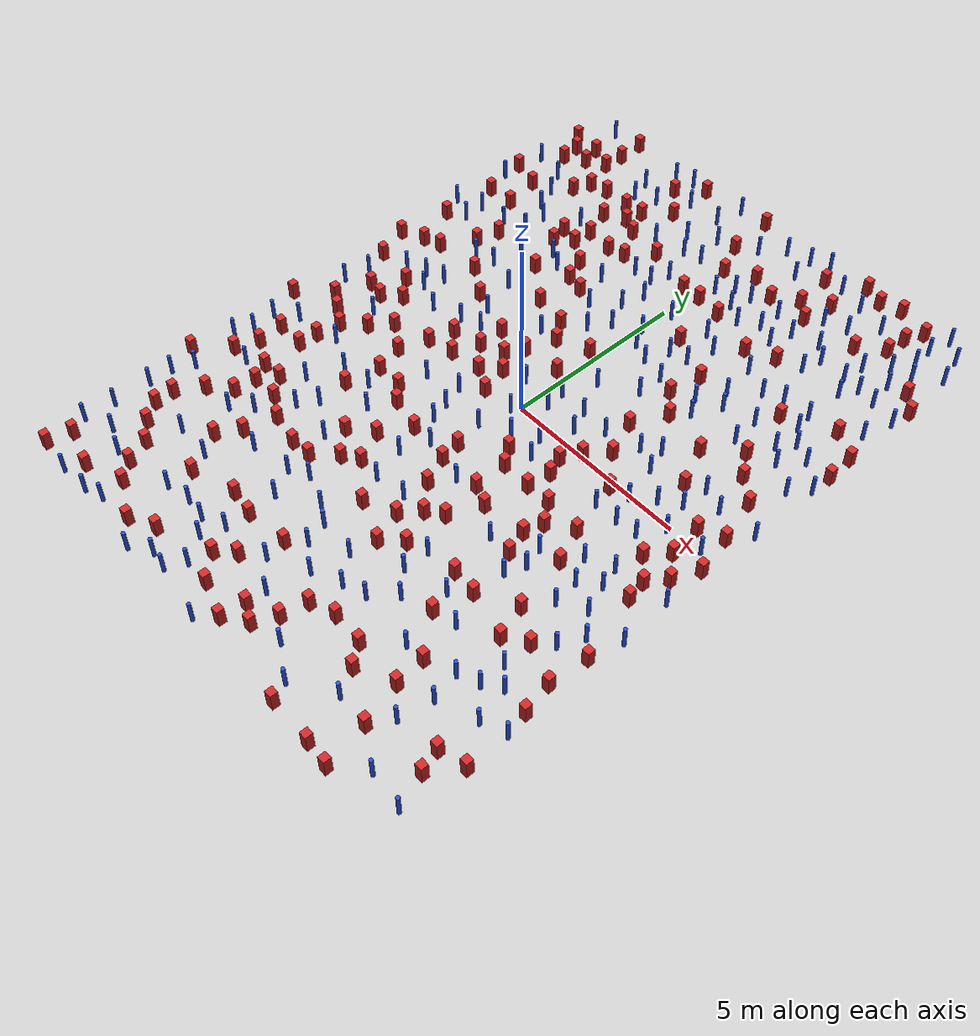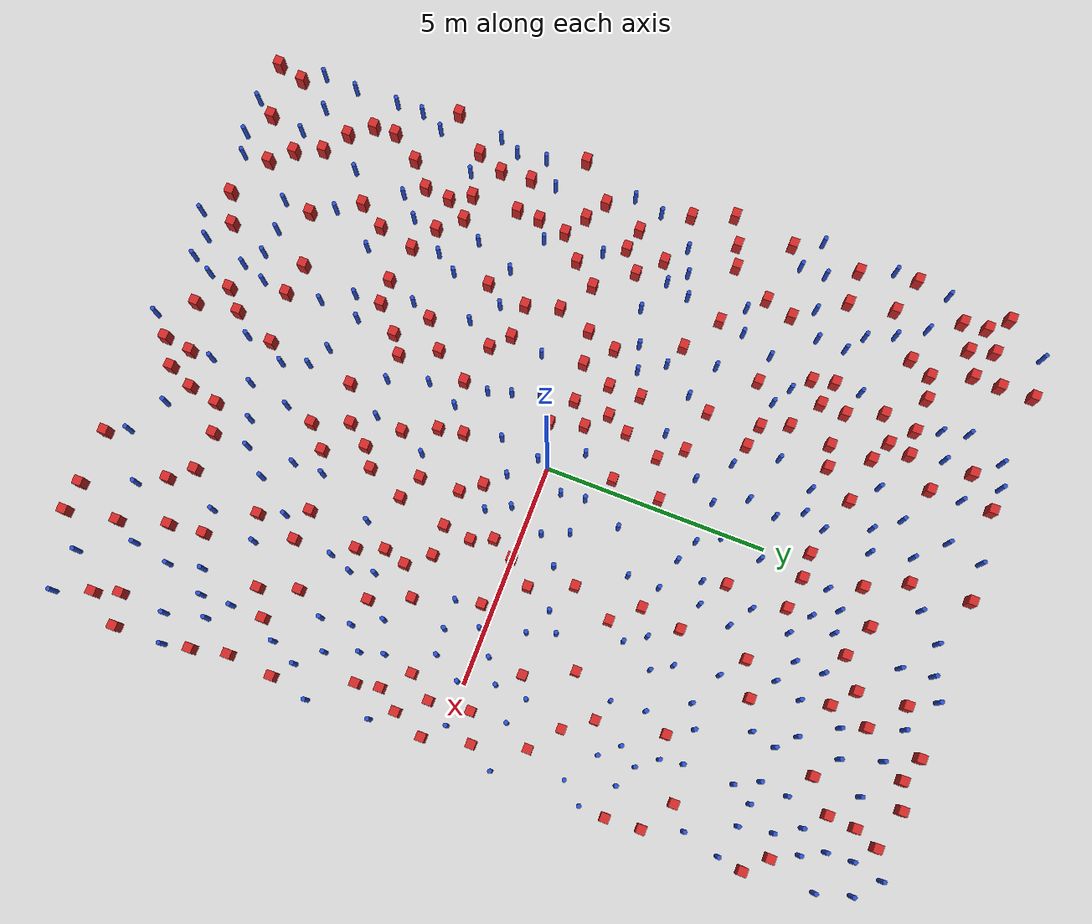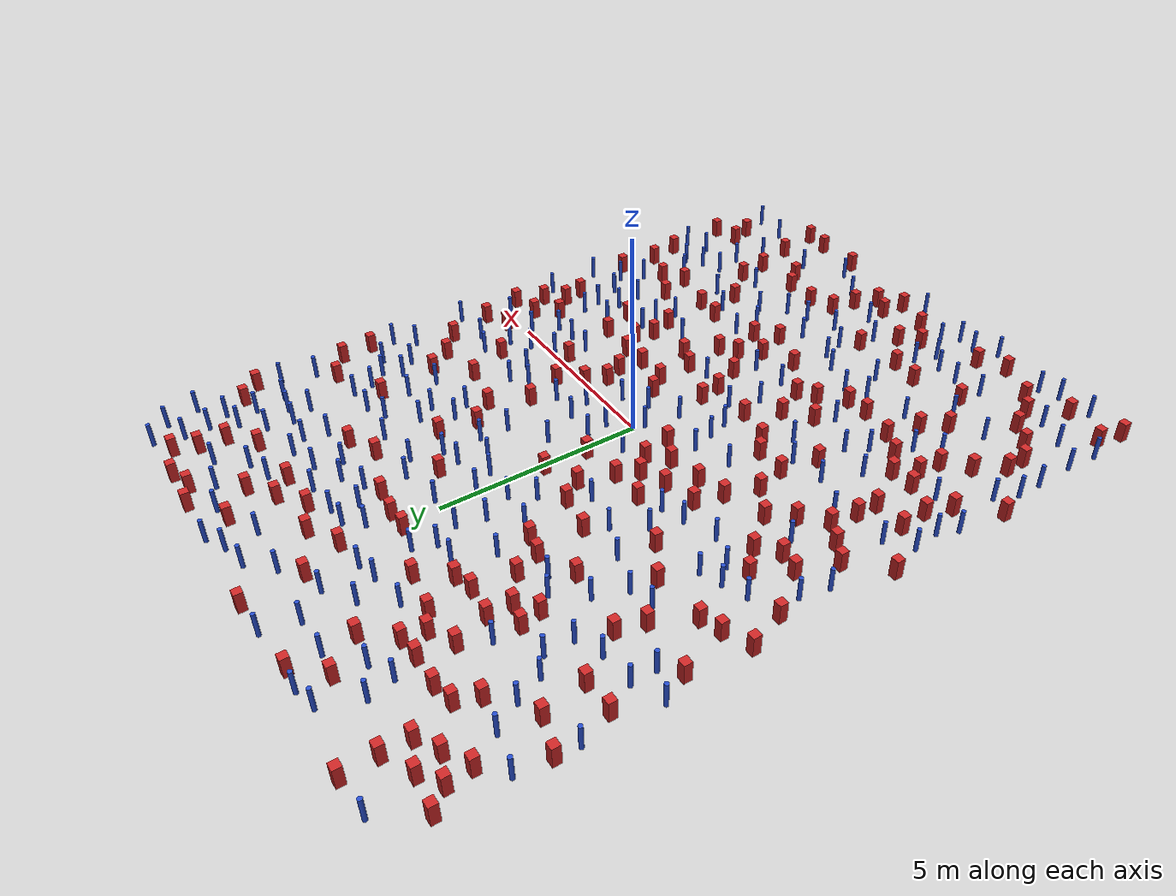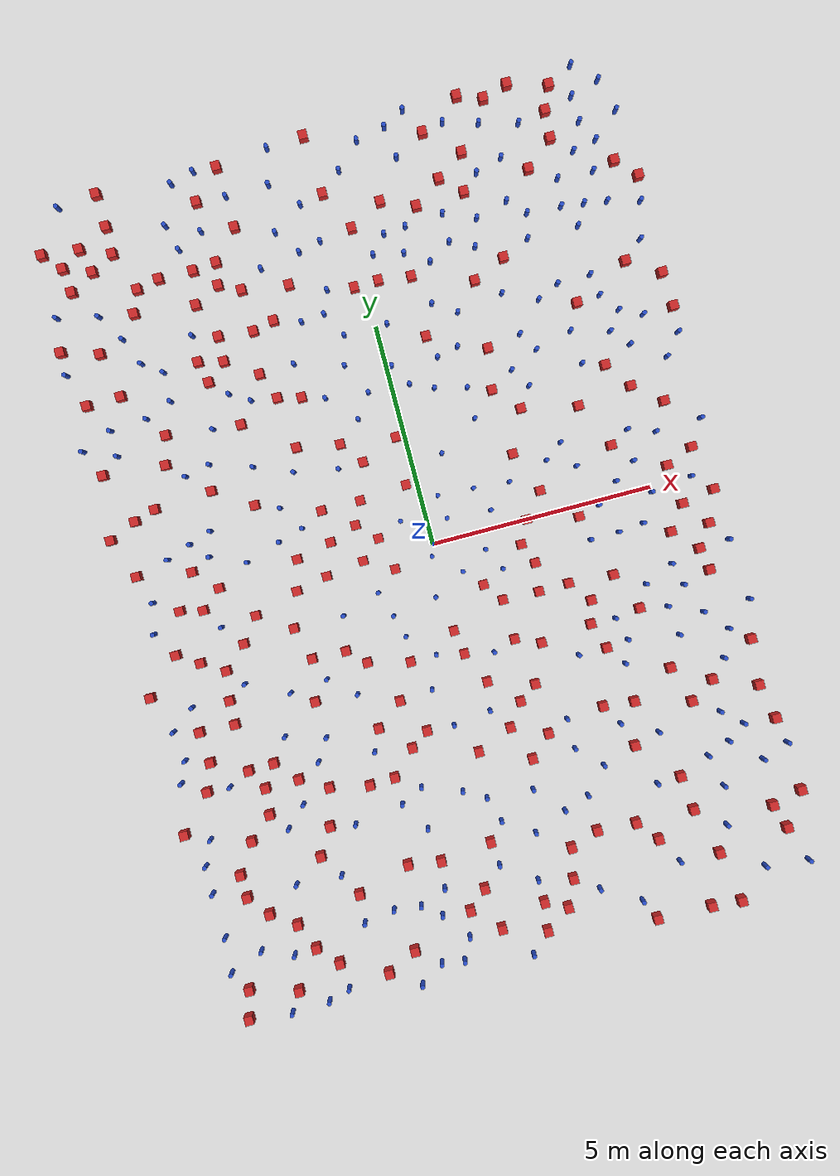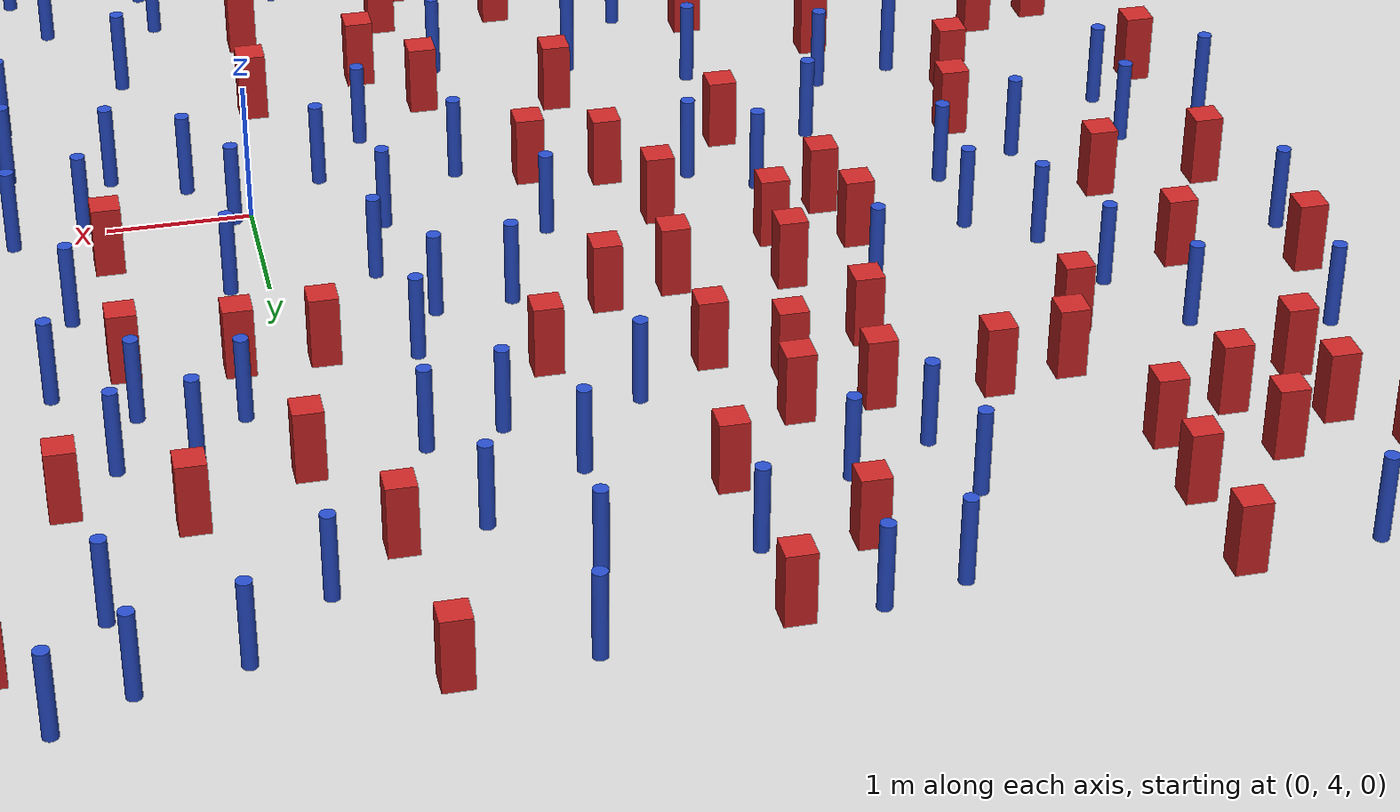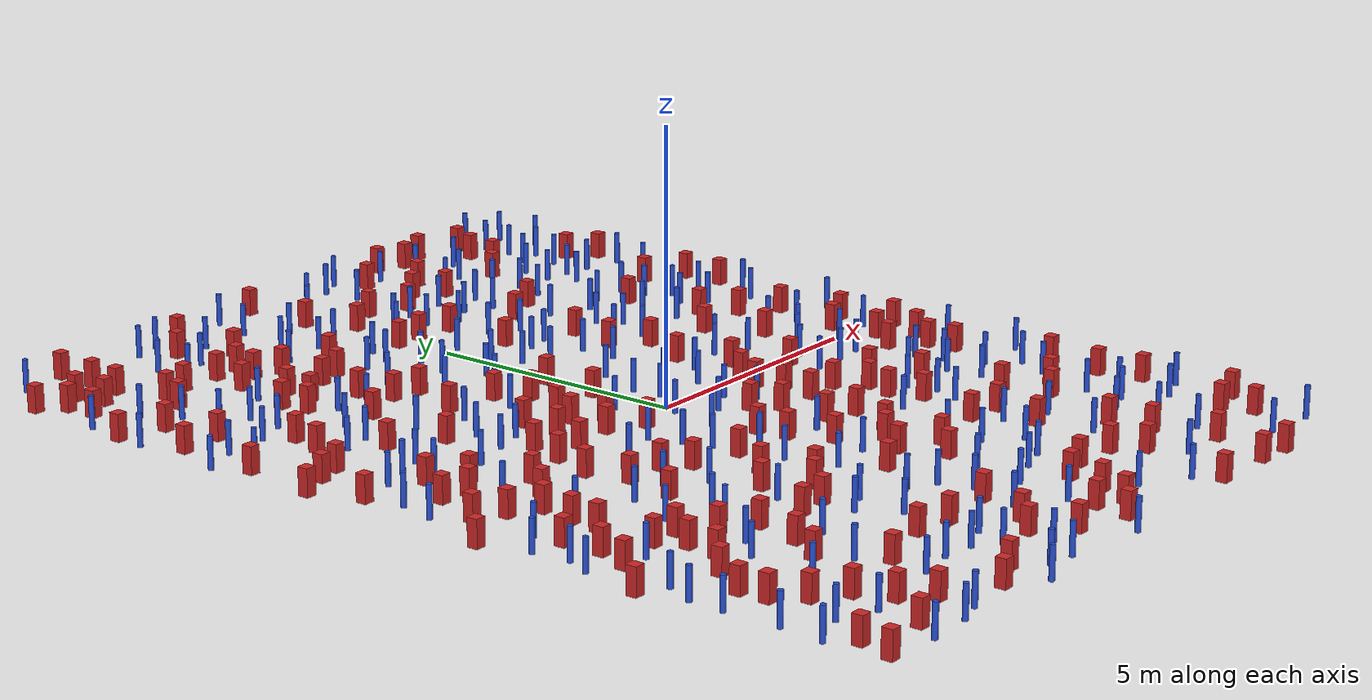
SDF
<sdf version="1.6">
  <model name="dense_66"><model name="pole_obstacle0">
  <static>true</static>
  <pose frame="">-2.32125434121 -1.0319699468 -9.47619616065e-06 5.49618799738e-07 2.3631041407e-07 -1.55090534797e-07</pose>
  <link name="link">
  <pose frame="">0 0 0.3 0 -0 0</pose>
    <inertial>
      <mass>1</mass>
      <inertia>
        <ixx>0.145833</ixx>
        <ixy>0</ixy>
        <ixz>0</ixz>
        <iyy>0.145833</iyy>
        <iyz>0</iyz>
        <izz>0.125</izz>
      </inertia>
    </inertial>
    <collision name="collision">
      <geometry>
        <cylinder>
          <radius>0.05</radius>
          <length>.6</length>
        </cylinder>
      </geometry>
      <max_contacts>10</max_contacts>
      <surface>
        <contact>
          <ode/>
        </contact>
        <bounce/>
        <friction>
          <torsional>
            <ode/>
          </torsional>
          <ode/>
        </friction>
      </surface>
    </collision>
    <visual name="visual">
      <geometry>
        <cylinder>
          <radius>0.05</radius>
          <length>.6</length>
        </cylinder>
      </geometry>
      <material>
        <script>
          <name>Gazebo/Blue</name>
          <uri>file://media/materials/scripts/gazebo.material</uri>
        </script>
      </material>
    </visual>
    <self_collide>0</self_collide>
    <kinematic>0</kinematic>
  </link>
</model>
<model name="pole_obstacle1">
  <static>true</static>
  <pose frame="">-2.13433146588 6.8682397058 -9.47619616065e-06 5.49618799738e-07 2.3631041406e-07 -1.55090534801e-07</pose>
  <link name="link">
  <pose frame="">0 0 0.3 0 -0 0</pose>
    <inertial>
      <mass>1</mass>
      <inertia>
        <ixx>0.145833</ixx>
        <ixy>0</ixy>
        <ixz>0</ixz>
        <iyy>0.145833</iyy>
        <iyz>0</iyz>
        <izz>0.125</izz>
      </inertia>
    </inertial>
    <collision name="collision">
      <geometry>
        <cylinder>
          <radius>0.05</radius>
          <length>.6</length>
        </cylinder>
      </geometry>
      <max_contacts>10</max_contacts>
      <surface>
        <contact>
          <ode/>
        </contact>
        <bounce/>
        <friction>
          <torsional>
            <ode/>
          </torsional>
          <ode/>
        </friction>
      </surface>
    </collision>
    <visual name="visual">
      <geometry>
        <cylinder>
          <radius>0.05</radius>
          <length>.6</length>
        </cylinder>
      </geometry>
      <material>
        <script>
          <name>Gazebo/Blue</name>
          <uri>file://media/materials/scripts/gazebo.material</uri>
        </script>
      </material>
    </visual>
    <self_collide>0</self_collide>
    <kinematic>0</kinematic>
  </link>
</model>
<model name="square_post_obstacle0">
  <static>true</static>
  <pose frame="">-5.65463043567 -1.24283270204 -6.11067671241e-07 -5.50515727128e-06 -8.79689657224e-07 2.37013304536e-05</pose>
  <link name="link">
    <pose frame="">0 0 0.25 0 -0 0</pose>
    <inertial>
      <mass>100</mass>
      <inertia>
        <ixx>0.166667</ixx>
        <ixy>0</ixy>
        <ixz>0</ixz>
        <iyy>0.166667</iyy>
        <iyz>0</iyz>
        <izz>0.166667</izz>
      </inertia>
    </inertial>
    <collision name="collision">
      <geometry>
        <box>
          <size>.2 .2 .5</size>
        </box>
      </geometry>
      <max_contacts>10</max_contacts>
      <surface>
        <contact>
          <ode/>
        </contact>
        <bounce/>
        <friction>
          <torsional>
            <ode/>
          </torsional>
          <ode/>
        </friction>
      </surface>
    </collision>
    <visual name="visual">
      <geometry>
        <box>
          <size>.2 .2 .5</size>
        </box>
      </geometry>
      <material>
        <script>
          <name>Gazebo/Red</name>
          <uri>file://media/materials/scripts/gazebo.material</uri>
        </script>
      </material>
    </visual>
    <self_collide>0</self_collide>
    <kinematic>0</kinematic>
  </link>
</model>
<model name="square_post_obstacle1">
  <static>true</static>
  <pose frame="">1.90221680884 -7.06881276278 -6.11067671241e-07 -5.50515727128e-06 -8.79689657224e-07 2.37013304536e-05</pose>
  <link name="link">
    <pose frame="">0 0 0.25 0 -0 0</pose>
    <inertial>
      <mass>100</mass>
      <inertia>
        <ixx>0.166667</ixx>
        <ixy>0</ixy>
        <ixz>0</ixz>
        <iyy>0.166667</iyy>
        <iyz>0</iyz>
        <izz>0.166667</izz>
      </inertia>
    </inertial>
    <collision name="collision">
      <geometry>
        <box>
          <size>.2 .2 .5</size>
        </box>
      </geometry>
      <max_contacts>10</max_contacts>
      <surface>
        <contact>
          <ode/>
        </contact>
        <bounce/>
        <friction>
          <torsional>
            <ode/>
          </torsional>
          <ode/>
        </friction>
      </surface>
    </collision>
    <visual name="visual">
      <geometry>
        <box>
          <size>.2 .2 .5</size>
        </box>
      </geometry>
      <material>
        <script>
          <name>Gazebo/Red</name>
          <uri>file://media/materials/scripts/gazebo.material</uri>
        </script>
      </material>
    </visual>
    <self_collide>0</self_collide>
    <kinematic>0</kinematic>
  </link>
</model>
<model name="pole_obstacle2">
  <static>true</static>
  <pose frame="">3.64827006361 4.64139536946 -9.47619616065e-06 5.49618799738e-07 2.3631041406e-07 -1.55090534801e-07</pose>
  <link name="link">
  <pose frame="">0 0 0.3 0 -0 0</pose>
    <inertial>
      <mass>1</mass>
      <inertia>
        <ixx>0.145833</ixx>
        <ixy>0</ixy>
        <ixz>0</ixz>
        <iyy>0.145833</iyy>
        <iyz>0</iyz>
        <izz>0.125</izz>
      </inertia>
    </inertial>
    <collision name="collision">
      <geometry>
        <cylinder>
          <radius>0.05</radius>
          <length>.6</length>
        </cylinder>
      </geometry>
      <max_contacts>10</max_contacts>
      <surface>
        <contact>
          <ode/>
        </contact>
        <bounce/>
        <friction>
          <torsional>
            <ode/>
          </torsional>
          <ode/>
        </friction>
      </surface>
    </collision>
    <visual name="visual">
      <geometry>
        <cylinder>
          <radius>0.05</radius>
          <length>.6</length>
        </cylinder>
      </geometry>
      <material>
        <script>
          <name>Gazebo/Blue</name>
          <uri>file://media/materials/scripts/gazebo.material</uri>
        </script>
      </material>
    </visual>
    <self_collide>0</self_collide>
    <kinematic>0</kinematic>
  </link>
</model>
<model name="pole_obstacle3">
  <static>true</static>
  <pose frame="">-0.0956623919668 -6.32274000697 -9.47619616065e-06 5.49618799737e-07 2.36310414062e-07 -1.550905348e-07</pose>
  <link name="link">
  <pose frame="">0 0 0.3 0 -0 0</pose>
    <inertial>
      <mass>1</mass>
      <inertia>
        <ixx>0.145833</ixx>
        <ixy>0</ixy>
        <ixz>0</ixz>
        <iyy>0.145833</iyy>
        <iyz>0</iyz>
        <izz>0.125</izz>
      </inertia>
    </inertial>
    <collision name="collision">
      <geometry>
        <cylinder>
          <radius>0.05</radius>
          <length>.6</length>
        </cylinder>
      </geometry>
      <max_contacts>10</max_contacts>
      <surface>
        <contact>
          <ode/>
        </contact>
        <bounce/>
        <friction>
          <torsional>
            <ode/>
          </torsional>
          <ode/>
        </friction>
      </surface>
    </collision>
    <visual name="visual">
      <geometry>
        <cylinder>
          <radius>0.05</radius>
          <length>.6</length>
        </cylinder>
      </geometry>
      <material>
        <script>
          <name>Gazebo/Blue</name>
          <uri>file://media/materials/scripts/gazebo.material</uri>
        </script>
      </material>
    </visual>
    <self_collide>0</self_collide>
    <kinematic>0</kinematic>
  </link>
</model>
<model name="pole_obstacle4">
  <static>true</static>
  <pose frame="">-3.21196088458 8.00425700751 -9.47619616065e-06 5.49618799737e-07 2.3631041406e-07 -1.55090534799e-07</pose>
  <link name="link">
  <pose frame="">0 0 0.3 0 -0 0</pose>
    <inertial>
      <mass>1</mass>
      <inertia>
        <ixx>0.145833</ixx>
        <ixy>0</ixy>
        <ixz>0</ixz>
        <iyy>0.145833</iyy>
        <iyz>0</iyz>
        <izz>0.125</izz>
      </inertia>
    </inertial>
    <collision name="collision">
      <geometry>
        <cylinder>
          <radius>0.05</radius>
          <length>.6</length>
        </cylinder>
      </geometry>
      <max_contacts>10</max_contacts>
      <surface>
        <contact>
          <ode/>
        </contact>
        <bounce/>
        <friction>
          <torsional>
            <ode/>
          </torsional>
          <ode/>
        </friction>
      </surface>
    </collision>
    <visual name="visual">
      <geometry>
        <cylinder>
          <radius>0.05</radius>
          <length>.6</length>
        </cylinder>
      </geometry>
      <material>
        <script>
          <name>Gazebo/Blue</name>
          <uri>file://media/materials/scripts/gazebo.material</uri>
        </script>
      </material>
    </visual>
    <self_collide>0</self_collide>
    <kinematic>0</kinematic>
  </link>
</model>
<model name="pole_obstacle5">
  <static>true</static>
  <pose frame="">-1.10176745117 -1.83270935728 -9.47619616065e-06 5.49618799737e-07 2.36310414065e-07 -1.55090534798e-07</pose>
  <link name="link">
  <pose frame="">0 0 0.3 0 -0 0</pose>
    <inertial>
      <mass>1</mass>
      <inertia>
        <ixx>0.145833</ixx>
        <ixy>0</ixy>
        <ixz>0</ixz>
        <iyy>0.145833</iyy>
        <iyz>0</iyz>
        <izz>0.125</izz>
      </inertia>
    </inertial>
    <collision name="collision">
      <geometry>
        <cylinder>
          <radius>0.05</radius>
          <length>.6</length>
        </cylinder>
      </geometry>
      <max_contacts>10</max_contacts>
      <surface>
        <contact>
          <ode/>
        </contact>
        <bounce/>
        <friction>
          <torsional>
            <ode/>
          </torsional>
          <ode/>
        </friction>
      </surface>
    </collision>
    <visual name="visual">
      <geometry>
        <cylinder>
          <radius>0.05</radius>
          <length>.6</length>
        </cylinder>
      </geometry>
      <material>
        <script>
          <name>Gazebo/Blue</name>
          <uri>file://media/materials/scripts/gazebo.material</uri>
        </script>
      </material>
    </visual>
    <self_collide>0</self_collide>
    <kinematic>0</kinematic>
  </link>
</model>
<model name="pole_obstacle6">
  <static>true</static>
  <pose frame="">-6.67259514434 -7.26067881693 -9.47619616065e-06 5.49618799737e-07 2.36310414037e-07 -1.55090534814e-07</pose>
  <link name="link">
  <pose frame="">0 0 0.3 0 -0 0</pose>
    <inertial>
      <mass>1</mass>
      <inertia>
        <ixx>0.145833</ixx>
        <ixy>0</ixy>
        <ixz>0</ixz>
        <iyy>0.145833</iyy>
        <iyz>0</iyz>
        <izz>0.125</izz>
      </inertia>
    </inertial>
    <collision name="collision">
      <geometry>
        <cylinder>
          <radius>0.05</radius>
          <length>.6</length>
        </cylinder>
      </geometry>
      <max_contacts>10</max_contacts>
      <surface>
        <contact>
          <ode/>
        </contact>
        <bounce/>
        <friction>
          <torsional>
            <ode/>
          </torsional>
          <ode/>
        </friction>
      </surface>
    </collision>
    <visual name="visual">
      <geometry>
        <cylinder>
          <radius>0.05</radius>
          <length>.6</length>
        </cylinder>
      </geometry>
      <material>
        <script>
          <name>Gazebo/Blue</name>
          <uri>file://media/materials/scripts/gazebo.material</uri>
        </script>
      </material>
    </visual>
    <self_collide>0</self_collide>
    <kinematic>0</kinematic>
  </link>
</model>
<model name="square_post_obstacle2">
  <static>true</static>
  <pose frame="">2.5933843695 0.53864934318 -6.11067671241e-07 -5.50515727128e-06 -8.79689657224e-07 2.37013304536e-05</pose>
  <link name="link">
    <pose frame="">0 0 0.25 0 -0 0</pose>
    <inertial>
      <mass>100</mass>
      <inertia>
        <ixx>0.166667</ixx>
        <ixy>0</ixy>
        <ixz>0</ixz>
        <iyy>0.166667</iyy>
        <iyz>0</iyz>
        <izz>0.166667</izz>
      </inertia>
    </inertial>
    <collision name="collision">
      <geometry>
        <box>
          <size>.2 .2 .5</size>
        </box>
      </geometry>
      <max_contacts>10</max_contacts>
      <surface>
        <contact>
          <ode/>
        </contact>
        <bounce/>
        <friction>
          <torsional>
            <ode/>
          </torsional>
          <ode/>
        </friction>
      </surface>
    </collision>
    <visual name="visual">
      <geometry>
        <box>
          <size>.2 .2 .5</size>
        </box>
      </geometry>
      <material>
        <script>
          <name>Gazebo/Red</name>
          <uri>file://media/materials/scripts/gazebo.material</uri>
        </script>
      </material>
    </visual>
    <self_collide>0</self_collide>
    <kinematic>0</kinematic>
  </link>
</model>
<model name="square_post_obstacle3">
  <static>true</static>
  <pose frame="">0.0373794791806 7.22785850671 -6.11067671241e-07 -5.50515727128e-06 -8.79689657224e-07 2.37013304536e-05</pose>
  <link name="link">
    <pose frame="">0 0 0.25 0 -0 0</pose>
    <inertial>
      <mass>100</mass>
      <inertia>
        <ixx>0.166667</ixx>
        <ixy>0</ixy>
        <ixz>0</ixz>
        <iyy>0.166667</iyy>
        <iyz>0</iyz>
        <izz>0.166667</izz>
      </inertia>
    </inertial>
    <collision name="collision">
      <geometry>
        <box>
          <size>.2 .2 .5</size>
        </box>
      </geometry>
      <max_contacts>10</max_contacts>
      <surface>
        <contact>
          <ode/>
        </contact>
        <bounce/>
        <friction>
          <torsional>
            <ode/>
          </torsional>
          <ode/>
        </friction>
      </surface>
    </collision>
    <visual name="visual">
      <geometry>
        <box>
          <size>.2 .2 .5</size>
        </box>
      </geometry>
      <material>
        <script>
          <name>Gazebo/Red</name>
          <uri>file://media/materials/scripts/gazebo.material</uri>
        </script>
      </material>
    </visual>
    <self_collide>0</self_collide>
    <kinematic>0</kinematic>
  </link>
</model>
<model name="square_post_obstacle4">
  <static>true</static>
  <pose frame="">6.48960787232 3.74774765811 -6.11067671241e-07 -5.50515727128e-06 -8.79689657224e-07 2.37013304536e-05</pose>
  <link name="link">
    <pose frame="">0 0 0.25 0 -0 0</pose>
    <inertial>
      <mass>100</mass>
      <inertia>
        <ixx>0.166667</ixx>
        <ixy>0</ixy>
        <ixz>0</ixz>
        <iyy>0.166667</iyy>
        <iyz>0</iyz>
        <izz>0.166667</izz>
      </inertia>
    </inertial>
    <collision name="collision">
      <geometry>
        <box>
          <size>.2 .2 .5</size>
        </box>
      </geometry>
      <max_contacts>10</max_contacts>
      <surface>
        <contact>
          <ode/>
        </contact>
        <bounce/>
        <friction>
          <torsional>
            <ode/>
          </torsional>
          <ode/>
        </friction>
      </surface>
    </collision>
    <visual name="visual">
      <geometry>
        <box>
          <size>.2 .2 .5</size>
        </box>
      </geometry>
      <material>
        <script>
          <name>Gazebo/Red</name>
          <uri>file://media/materials/scripts/gazebo.material</uri>
        </script>
      </material>
    </visual>
    <self_collide>0</self_collide>
    <kinematic>0</kinematic>
  </link>
</model>
<model name="pole_obstacle7">
  <static>true</static>
  <pose frame="">5.41939014065 1.15405519422 -9.47619616065e-06 5.49618799738e-07 2.36310414071e-07 -1.55090534796e-07</pose>
  <link name="link">
  <pose frame="">0 0 0.3 0 -0 0</pose>
    <inertial>
      <mass>1</mass>
      <inertia>
        <ixx>0.145833</ixx>
        <ixy>0</ixy>
        <ixz>0</ixz>
        <iyy>0.145833</iyy>
        <iyz>0</iyz>
        <izz>0.125</izz>
      </inertia>
    </inertial>
    <collision name="collision">
      <geometry>
        <cylinder>
          <radius>0.05</radius>
          <length>.6</length>
        </cylinder>
      </geometry>
      <max_contacts>10</max_contacts>
      <surface>
        <contact>
          <ode/>
        </contact>
        <bounce/>
        <friction>
          <torsional>
            <ode/>
          </torsional>
          <ode/>
        </friction>
      </surface>
    </collision>
    <visual name="visual">
      <geometry>
        <cylinder>
          <radius>0.05</radius>
          <length>.6</length>
        </cylinder>
      </geometry>
      <material>
        <script>
          <name>Gazebo/Blue</name>
          <uri>file://media/materials/scripts/gazebo.material</uri>
        </script>
      </material>
    </visual>
    <self_collide>0</self_collide>
    <kinematic>0</kinematic>
  </link>
</model>
<model name="pole_obstacle8">
  <static>true</static>
  <pose frame="">1.09570881919 -0.413410451894 -9.47619616065e-06 5.49618799737e-07 2.36310414064e-07 -1.55090534799e-07</pose>
  <link name="link">
  <pose frame="">0 0 0.3 0 -0 0</pose>
    <inertial>
      <mass>1</mass>
      <inertia>
        <ixx>0.145833</ixx>
        <ixy>0</ixy>
        <ixz>0</ixz>
        <iyy>0.145833</iyy>
        <iyz>0</iyz>
        <izz>0.125</izz>
      </inertia>
    </inertial>
    <collision name="collision">
      <geometry>
        <cylinder>
          <radius>0.05</radius>
          <length>.6</length>
        </cylinder>
      </geometry>
      <max_contacts>10</max_contacts>
      <surface>
        <contact>
          <ode/>
        </contact>
        <bounce/>
        <friction>
          <torsional>
            <ode/>
          </torsional>
          <ode/>
        </friction>
      </surface>
    </collision>
    <visual name="visual">
      <geometry>
        <cylinder>
          <radius>0.05</radius>
          <length>.6</length>
        </cylinder>
      </geometry>
      <material>
        <script>
          <name>Gazebo/Blue</name>
          <uri>file://media/materials/scripts/gazebo.material</uri>
        </script>
      </material>
    </visual>
    <self_collide>0</self_collide>
    <kinematic>0</kinematic>
  </link>
</model>
<model name="square_post_obstacle5">
  <static>true</static>
  <pose frame="">-0.949633495577 -0.323597789229 -6.11067671241e-07 -5.50515727128e-06 -8.79689657224e-07 2.37013304536e-05</pose>
  <link name="link">
    <pose frame="">0 0 0.25 0 -0 0</pose>
    <inertial>
      <mass>100</mass>
      <inertia>
        <ixx>0.166667</ixx>
        <ixy>0</ixy>
        <ixz>0</ixz>
        <iyy>0.166667</iyy>
        <iyz>0</iyz>
        <izz>0.166667</izz>
      </inertia>
    </inertial>
    <collision name="collision">
      <geometry>
        <box>
          <size>.2 .2 .5</size>
        </box>
      </geometry>
      <max_contacts>10</max_contacts>
      <surface>
        <contact>
          <ode/>
        </contact>
        <bounce/>
        <friction>
          <torsional>
            <ode/>
          </torsional>
          <ode/>
        </friction>
      </surface>
    </collision>
    <visual name="visual">
      <geometry>
        <box>
          <size>.2 .2 .5</size>
        </box>
      </geometry>
      <material>
        <script>
          <name>Gazebo/Red</name>
          <uri>file://media/materials/scripts/gazebo.material</uri>
        </script>
      </material>
    </visual>
    <self_collide>0</self_collide>
    <kinematic>0</kinematic>
  </link>
</model>
<model name="square_post_obstacle6">
  <static>true</static>
  <pose frame="">-1.17910384282 -3.9688895999 -6.11067671241e-07 -5.50515727128e-06 -8.79689657224e-07 2.37013304536e-05</pose>
  <link name="link">
    <pose frame="">0 0 0.25 0 -0 0</pose>
    <inertial>
      <mass>100</mass>
      <inertia>
        <ixx>0.166667</ixx>
        <ixy>0</ixy>
        <ixz>0</ixz>
        <iyy>0.166667</iyy>
        <iyz>0</iyz>
        <izz>0.166667</izz>
      </inertia>
    </inertial>
    <collision name="collision">
      <geometry>
        <box>
          <size>.2 .2 .5</size>
        </box>
      </geometry>
      <max_contacts>10</max_contacts>
      <surface>
        <contact>
          <ode/>
        </contact>
        <bounce/>
        <friction>
          <torsional>
            <ode/>
          </torsional>
          <ode/>
        </friction>
      </surface>
    </collision>
    <visual name="visual">
      <geometry>
        <box>
          <size>.2 .2 .5</size>
        </box>
      </geometry>
      <material>
        <script>
          <name>Gazebo/Red</name>
          <uri>file://media/materials/scripts/gazebo.material</uri>
        </script>
      </material>
    </visual>
    <self_collide>0</self_collide>
    <kinematic>0</kinematic>
  </link>
</model>
<model name="square_post_obstacle7">
  <static>true</static>
  <pose frame="">2.00111036596 -1.61508114656 -6.11067671241e-07 -5.50515727128e-06 -8.79689657224e-07 2.37013304536e-05</pose>
  <link name="link">
    <pose frame="">0 0 0.25 0 -0 0</pose>
    <inertial>
      <mass>100</mass>
      <inertia>
        <ixx>0.166667</ixx>
        <ixy>0</ixy>
        <ixz>0</ixz>
        <iyy>0.166667</iyy>
        <iyz>0</iyz>
        <izz>0.166667</izz>
      </inertia>
    </inertial>
    <collision name="collision">
      <geometry>
        <box>
          <size>.2 .2 .5</size>
        </box>
      </geometry>
      <max_contacts>10</max_contacts>
      <surface>
        <contact>
          <ode/>
        </contact>
        <bounce/>
        <friction>
          <torsional>
            <ode/>
          </torsional>
          <ode/>
        </friction>
      </surface>
    </collision>
    <visual name="visual">
      <geometry>
        <box>
          <size>.2 .2 .5</size>
        </box>
      </geometry>
      <material>
        <script>
          <name>Gazebo/Red</name>
          <uri>file://media/materials/scripts/gazebo.material</uri>
        </script>
      </material>
    </visual>
    <self_collide>0</self_collide>
    <kinematic>0</kinematic>
  </link>
</model>
<model name="pole_obstacle9">
  <static>true</static>
  <pose frame="">-1.62684005314 7.56220310109 -9.47619616065e-06 5.49618799737e-07 2.36310414061e-07 -1.550905348e-07</pose>
  <link name="link">
  <pose frame="">0 0 0.3 0 -0 0</pose>
    <inertial>
      <mass>1</mass>
      <inertia>
        <ixx>0.145833</ixx>
        <ixy>0</ixy>
        <ixz>0</ixz>
        <iyy>0.145833</iyy>
        <iyz>0</iyz>
        <izz>0.125</izz>
      </inertia>
    </inertial>
    <collision name="collision">
      <geometry>
        <cylinder>
          <radius>0.05</radius>
          <length>.6</length>
        </cylinder>
      </geometry>
      <max_contacts>10</max_contacts>
      <surface>
        <contact>
          <ode/>
        </contact>
        <bounce/>
        <friction>
          <torsional>
            <ode/>
          </torsional>
          <ode/>
        </friction>
      </surface>
    </collision>
    <visual name="visual">
      <geometry>
        <cylinder>
          <radius>0.05</radius>
          <length>.6</length>
        </cylinder>
      </geometry>
      <material>
        <script>
          <name>Gazebo/Blue</name>
          <uri>file://media/materials/scripts/gazebo.material</uri>
        </script>
      </material>
    </visual>
    <self_collide>0</self_collide>
    <kinematic>0</kinematic>
  </link>
</model>
<model name="pole_obstacle10">
  <static>true</static>
  <pose frame="">4.0586891352 -0.791165849269 -9.47619616065e-06 5.49618799737e-07 2.36310414061e-07 -1.550905348e-07</pose>
  <link name="link">
  <pose frame="">0 0 0.3 0 -0 0</pose>
    <inertial>
      <mass>1</mass>
      <inertia>
        <ixx>0.145833</ixx>
        <ixy>0</ixy>
        <ixz>0</ixz>
        <iyy>0.145833</iyy>
        <iyz>0</iyz>
        <izz>0.125</izz>
      </inertia>
    </inertial>
    <collision name="collision">
      <geometry>
        <cylinder>
          <radius>0.05</radius>
          <length>.6</length>
        </cylinder>
      </geometry>
      <max_contacts>10</max_contacts>
      <surface>
        <contact>
          <ode/>
        </contact>
        <bounce/>
        <friction>
          <torsional>
            <ode/>
          </torsional>
          <ode/>
        </friction>
      </surface>
    </collision>
    <visual name="visual">
      <geometry>
        <cylinder>
          <radius>0.05</radius>
          <length>.6</length>
        </cylinder>
      </geometry>
      <material>
        <script>
          <name>Gazebo/Blue</name>
          <uri>file://media/materials/scripts/gazebo.material</uri>
        </script>
      </material>
    </visual>
    <self_collide>0</self_collide>
    <kinematic>0</kinematic>
  </link>
</model>
<model name="pole_obstacle11">
  <static>true</static>
  <pose frame="">-6.33901266133 0.316842435383 -9.47619616065e-06 5.49618799737e-07 2.36310414057e-07 -1.55090534802e-07</pose>
  <link name="link">
  <pose frame="">0 0 0.3 0 -0 0</pose>
    <inertial>
      <mass>1</mass>
      <inertia>
        <ixx>0.145833</ixx>
        <ixy>0</ixy>
        <ixz>0</ixz>
        <iyy>0.145833</iyy>
        <iyz>0</iyz>
        <izz>0.125</izz>
      </inertia>
    </inertial>
    <collision name="collision">
      <geometry>
        <cylinder>
          <radius>0.05</radius>
          <length>.6</length>
        </cylinder>
      </geometry>
      <max_contacts>10</max_contacts>
      <surface>
        <contact>
          <ode/>
        </contact>
        <bounce/>
        <friction>
          <torsional>
            <ode/>
          </torsional>
          <ode/>
        </friction>
      </surface>
    </collision>
    <visual name="visual">
      <geometry>
        <cylinder>
          <radius>0.05</radius>
          <length>.6</length>
        </cylinder>
      </geometry>
      <material>
        <script>
          <name>Gazebo/Blue</name>
          <uri>file://media/materials/scripts/gazebo.material</uri>
        </script>
      </material>
    </visual>
    <self_collide>0</self_collide>
    <kinematic>0</kinematic>
  </link>
</model>
<model name="pole_obstacle12">
  <static>true</static>
  <pose frame="">-3.68326710678 -4.0231572233 -9.47619616065e-06 5.49618799737e-07 2.36310414057e-07 -1.55090534803e-07</pose>
  <link name="link">
  <pose frame="">0 0 0.3 0 -0 0</pose>
    <inertial>
      <mass>1</mass>
      <inertia>
        <ixx>0.145833</ixx>
        <ixy>0</ixy>
        <ixz>0</ixz>
        <iyy>0.145833</iyy>
        <iyz>0</iyz>
        <izz>0.125</izz>
      </inertia>
    </inertial>
    <collision name="collision">
      <geometry>
        <cylinder>
          <radius>0.05</radius>
          <length>.6</length>
        </cylinder>
      </geometry>
      <max_contacts>10</max_contacts>
      <surface>
        <contact>
          <ode/>
        </contact>
        <bounce/>
        <friction>
          <torsional>
            <ode/>
          </torsional>
          <ode/>
        </friction>
      </surface>
    </collision>
    <visual name="visual">
      <geometry>
        <cylinder>
          <radius>0.05</radius>
          <length>.6</length>
        </cylinder>
      </geometry>
      <material>
        <script>
          <name>Gazebo/Blue</name>
          <uri>file://media/materials/scripts/gazebo.material</uri>
        </script>
      </material>
    </visual>
    <self_collide>0</self_collide>
    <kinematic>0</kinematic>
  </link>
</model>
<model name="square_post_obstacle8">
  <static>true</static>
  <pose frame="">-5.1087759929 6.61862478687 -6.11067671241e-07 -5.50515727128e-06 -8.79689657224e-07 2.37013304536e-05</pose>
  <link name="link">
    <pose frame="">0 0 0.25 0 -0 0</pose>
    <inertial>
      <mass>100</mass>
      <inertia>
        <ixx>0.166667</ixx>
        <ixy>0</ixy>
        <ixz>0</ixz>
        <iyy>0.166667</iyy>
        <iyz>0</iyz>
        <izz>0.166667</izz>
      </inertia>
    </inertial>
    <collision name="collision">
      <geometry>
        <box>
          <size>.2 .2 .5</size>
        </box>
      </geometry>
      <max_contacts>10</max_contacts>
      <surface>
        <contact>
          <ode/>
        </contact>
        <bounce/>
        <friction>
          <torsional>
            <ode/>
          </torsional>
          <ode/>
        </friction>
      </surface>
    </collision>
    <visual name="visual">
      <geometry>
        <box>
          <size>.2 .2 .5</size>
        </box>
      </geometry>
      <material>
        <script>
          <name>Gazebo/Red</name>
          <uri>file://media/materials/scripts/gazebo.material</uri>
        </script>
      </material>
    </visual>
    <self_collide>0</self_collide>
    <kinematic>0</kinematic>
  </link>
</model>
<model name="square_post_obstacle9">
  <static>true</static>
  <pose frame="">0.0549202736242 -2.52824962371 -6.11067671241e-07 -5.50515727128e-06 -8.79689657224e-07 2.37013304536e-05</pose>
  <link name="link">
    <pose frame="">0 0 0.25 0 -0 0</pose>
    <inertial>
      <mass>100</mass>
      <inertia>
        <ixx>0.166667</ixx>
        <ixy>0</ixy>
        <ixz>0</ixz>
        <iyy>0.166667</iyy>
        <iyz>0</iyz>
        <izz>0.166667</izz>
      </inertia>
    </inertial>
    <collision name="collision">
      <geometry>
        <box>
          <size>.2 .2 .5</size>
        </box>
      </geometry>
      <max_contacts>10</max_contacts>
      <surface>
        <contact>
          <ode/>
        </contact>
        <bounce/>
        <friction>
          <torsional>
            <ode/>
          </torsional>
          <ode/>
        </friction>
      </surface>
    </collision>
    <visual name="visual">
      <geometry>
        <box>
          <size>.2 .2 .5</size>
        </box>
      </geometry>
      <material>
        <script>
          <name>Gazebo/Red</name>
          <uri>file://media/materials/scripts/gazebo.material</uri>
        </script>
      </material>
    </visual>
    <self_collide>0</self_collide>
    <kinematic>0</kinematic>
  </link>
</model>
<model name="pole_obstacle13">
  <static>true</static>
  <pose frame="">-4.82165275078 -1.93948873702 -9.47619616065e-06 5.49618799738e-07 2.36310414071e-07 -1.55090534796e-07</pose>
  <link name="link">
  <pose frame="">0 0 0.3 0 -0 0</pose>
    <inertial>
      <mass>1</mass>
      <inertia>
        <ixx>0.145833</ixx>
        <ixy>0</ixy>
        <ixz>0</ixz>
        <iyy>0.145833</iyy>
        <iyz>0</iyz>
        <izz>0.125</izz>
      </inertia>
    </inertial>
    <collision name="collision">
      <geometry>
        <cylinder>
          <radius>0.05</radius>
          <length>.6</length>
        </cylinder>
      </geometry>
      <max_contacts>10</max_contacts>
      <surface>
        <contact>
          <ode/>
        </contact>
        <bounce/>
        <friction>
          <torsional>
            <ode/>
          </torsional>
          <ode/>
        </friction>
      </surface>
    </collision>
    <visual name="visual">
      <geometry>
        <cylinder>
          <radius>0.05</radius>
          <length>.6</length>
        </cylinder>
      </geometry>
      <material>
        <script>
          <name>Gazebo/Blue</name>
          <uri>file://media/materials/scripts/gazebo.material</uri>
        </script>
      </material>
    </visual>
    <self_collide>0</self_collide>
    <kinematic>0</kinematic>
  </link>
</model>
<model name="square_post_obstacle10">
  <static>true</static>
  <pose frame="">3.17019763839 -7.59909208464 -6.11067671241e-07 -5.50515727128e-06 -8.79689657224e-07 2.37013304536e-05</pose>
  <link name="link">
    <pose frame="">0 0 0.25 0 -0 0</pose>
    <inertial>
      <mass>100</mass>
      <inertia>
        <ixx>0.166667</ixx>
        <ixy>0</ixy>
        <ixz>0</ixz>
        <iyy>0.166667</iyy>
        <iyz>0</iyz>
        <izz>0.166667</izz>
      </inertia>
    </inertial>
    <collision name="collision">
      <geometry>
        <box>
          <size>.2 .2 .5</size>
        </box>
      </geometry>
      <max_contacts>10</max_contacts>
      <surface>
        <contact>
          <ode/>
        </contact>
        <bounce/>
        <friction>
          <torsional>
            <ode/>
          </torsional>
          <ode/>
        </friction>
      </surface>
    </collision>
    <visual name="visual">
      <geometry>
        <box>
          <size>.2 .2 .5</size>
        </box>
      </geometry>
      <material>
        <script>
          <name>Gazebo/Red</name>
          <uri>file://media/materials/scripts/gazebo.material</uri>
        </script>
      </material>
    </visual>
    <self_collide>0</self_collide>
    <kinematic>0</kinematic>
  </link>
</model>
<model name="square_post_obstacle11">
  <static>true</static>
  <pose frame="">-5.11208348679 3.83488327447 -6.11067671241e-07 -5.50515727128e-06 -8.79689657224e-07 2.37013304536e-05</pose>
  <link name="link">
    <pose frame="">0 0 0.25 0 -0 0</pose>
    <inertial>
      <mass>100</mass>
      <inertia>
        <ixx>0.166667</ixx>
        <ixy>0</ixy>
        <ixz>0</ixz>
        <iyy>0.166667</iyy>
        <iyz>0</iyz>
        <izz>0.166667</izz>
      </inertia>
    </inertial>
    <collision name="collision">
      <geometry>
        <box>
          <size>.2 .2 .5</size>
        </box>
      </geometry>
      <max_contacts>10</max_contacts>
      <surface>
        <contact>
          <ode/>
        </contact>
        <bounce/>
        <friction>
          <torsional>
            <ode/>
          </torsional>
          <ode/>
        </friction>
      </surface>
    </collision>
    <visual name="visual">
      <geometry>
        <box>
          <size>.2 .2 .5</size>
        </box>
      </geometry>
      <material>
        <script>
          <name>Gazebo/Red</name>
          <uri>file://media/materials/scripts/gazebo.material</uri>
        </script>
      </material>
    </visual>
    <self_collide>0</self_collide>
    <kinematic>0</kinematic>
  </link>
</model>
<model name="pole_obstacle14">
  <static>true</static>
  <pose frame="">-3.8241816231 -6.57870441481 -9.47619616065e-06 5.49618799738e-07 2.3631041406e-07 -1.55090534801e-07</pose>
  <link name="link">
  <pose frame="">0 0 0.3 0 -0 0</pose>
    <inertial>
      <mass>1</mass>
      <inertia>
        <ixx>0.145833</ixx>
        <ixy>0</ixy>
        <ixz>0</ixz>
        <iyy>0.145833</iyy>
        <iyz>0</iyz>
        <izz>0.125</izz>
      </inertia>
    </inertial>
    <collision name="collision">
      <geometry>
        <cylinder>
          <radius>0.05</radius>
          <length>.6</length>
        </cylinder>
      </geometry>
      <max_contacts>10</max_contacts>
      <surface>
        <contact>
          <ode/>
        </contact>
        <bounce/>
        <friction>
          <torsional>
            <ode/>
          </torsional>
          <ode/>
        </friction>
      </surface>
    </collision>
    <visual name="visual">
      <geometry>
        <cylinder>
          <radius>0.05</radius>
          <length>.6</length>
        </cylinder>
      </geometry>
      <material>
        <script>
          <name>Gazebo/Blue</name>
          <uri>file://media/materials/scripts/gazebo.material</uri>
        </script>
      </material>
    </visual>
    <self_collide>0</self_collide>
    <kinematic>0</kinematic>
  </link>
</model>
<model name="pole_obstacle15">
  <static>true</static>
  <pose frame="">5.80588194587 3.73845712251 -9.47619616065e-06 5.49618799738e-07 2.36310414051e-07 -1.55090534805e-07</pose>
  <link name="link">
  <pose frame="">0 0 0.3 0 -0 0</pose>
    <inertial>
      <mass>1</mass>
      <inertia>
        <ixx>0.145833</ixx>
        <ixy>0</ixy>
        <ixz>0</ixz>
        <iyy>0.145833</iyy>
        <iyz>0</iyz>
        <izz>0.125</izz>
      </inertia>
    </inertial>
    <collision name="collision">
      <geometry>
        <cylinder>
          <radius>0.05</radius>
          <length>.6</length>
        </cylinder>
      </geometry>
      <max_contacts>10</max_contacts>
      <surface>
        <contact>
          <ode/>
        </contact>
        <bounce/>
        <friction>
          <torsional>
            <ode/>
          </torsional>
          <ode/>
        </friction>
      </surface>
    </collision>
    <visual name="visual">
      <geometry>
        <cylinder>
          <radius>0.05</radius>
          <length>.6</length>
        </cylinder>
      </geometry>
      <material>
        <script>
          <name>Gazebo/Blue</name>
          <uri>file://media/materials/scripts/gazebo.material</uri>
        </script>
      </material>
    </visual>
    <self_collide>0</self_collide>
    <kinematic>0</kinematic>
  </link>
</model>
<model name="square_post_obstacle12">
  <static>true</static>
  <pose frame="">4.40079657541 -8.23585152588 -6.11067671241e-07 -5.50515727128e-06 -8.79689657224e-07 2.37013304536e-05</pose>
  <link name="link">
    <pose frame="">0 0 0.25 0 -0 0</pose>
    <inertial>
      <mass>100</mass>
      <inertia>
        <ixx>0.166667</ixx>
        <ixy>0</ixy>
        <ixz>0</ixz>
        <iyy>0.166667</iyy>
        <iyz>0</iyz>
        <izz>0.166667</izz>
      </inertia>
    </inertial>
    <collision name="collision">
      <geometry>
        <box>
          <size>.2 .2 .5</size>
        </box>
      </geometry>
      <max_contacts>10</max_contacts>
      <surface>
        <contact>
          <ode/>
        </contact>
        <bounce/>
        <friction>
          <torsional>
            <ode/>
          </torsional>
          <ode/>
        </friction>
      </surface>
    </collision>
    <visual name="visual">
      <geometry>
        <box>
          <size>.2 .2 .5</size>
        </box>
      </geometry>
      <material>
        <script>
          <name>Gazebo/Red</name>
          <uri>file://media/materials/scripts/gazebo.material</uri>
        </script>
      </material>
    </visual>
    <self_collide>0</self_collide>
    <kinematic>0</kinematic>
  </link>
</model>
<model name="pole_obstacle16">
  <static>true</static>
  <pose frame="">-3.53106733543 4.36434588367 -9.4761961606e-06 5.49618799729e-07 2.36310414006e-07 -1.55090534822e-07</pose>
  <link name="link">
  <pose frame="">0 0 0.3 0 -0 0</pose>
    <inertial>
      <mass>1</mass>
      <inertia>
        <ixx>0.145833</ixx>
        <ixy>0</ixy>
        <ixz>0</ixz>
        <iyy>0.145833</iyy>
        <iyz>0</iyz>
        <izz>0.125</izz>
      </inertia>
    </inertial>
    <collision name="collision">
      <geometry>
        <cylinder>
          <radius>0.05</radius>
          <length>.6</length>
        </cylinder>
      </geometry>
      <max_contacts>10</max_contacts>
      <surface>
        <contact>
          <ode/>
        </contact>
        <bounce/>
        <friction>
          <torsional>
            <ode/>
          </torsional>
          <ode/>
        </friction>
      </surface>
    </collision>
    <visual name="visual">
      <geometry>
        <cylinder>
          <radius>0.05</radius>
          <length>.6</length>
        </cylinder>
      </geometry>
      <material>
        <script>
          <name>Gazebo/Blue</name>
          <uri>file://media/materials/scripts/gazebo.material</uri>
        </script>
      </material>
    </visual>
    <self_collide>0</self_collide>
    <kinematic>0</kinematic>
  </link>
</model>
<model name="pole_obstacle17">
  <static>true</static>
  <pose frame="">-2.89915703418 -7.61839342395 -9.47619616065e-06 5.49618799738e-07 2.3631041406e-07 -1.55090534801e-07</pose>
  <link name="link">
  <pose frame="">0 0 0.3 0 -0 0</pose>
    <inertial>
      <mass>1</mass>
      <inertia>
        <ixx>0.145833</ixx>
        <ixy>0</ixy>
        <ixz>0</ixz>
        <iyy>0.145833</iyy>
        <iyz>0</iyz>
        <izz>0.125</izz>
      </inertia>
    </inertial>
    <collision name="collision">
      <geometry>
        <cylinder>
          <radius>0.05</radius>
          <length>.6</length>
        </cylinder>
      </geometry>
      <max_contacts>10</max_contacts>
      <surface>
        <contact>
          <ode/>
        </contact>
        <bounce/>
        <friction>
          <torsional>
            <ode/>
          </torsional>
          <ode/>
        </friction>
      </surface>
    </collision>
    <visual name="visual">
      <geometry>
        <cylinder>
          <radius>0.05</radius>
          <length>.6</length>
        </cylinder>
      </geometry>
      <material>
        <script>
          <name>Gazebo/Blue</name>
          <uri>file://media/materials/scripts/gazebo.material</uri>
        </script>
      </material>
    </visual>
    <self_collide>0</self_collide>
    <kinematic>0</kinematic>
  </link>
</model>
<model name="square_post_obstacle13">
  <static>true</static>
  <pose frame="">-1.98647705047 3.88158295997 -6.11067671241e-07 -5.50515727128e-06 -8.79689657224e-07 2.37013304536e-05</pose>
  <link name="link">
    <pose frame="">0 0 0.25 0 -0 0</pose>
    <inertial>
      <mass>100</mass>
      <inertia>
        <ixx>0.166667</ixx>
        <ixy>0</ixy>
        <ixz>0</ixz>
        <iyy>0.166667</iyy>
        <iyz>0</iyz>
        <izz>0.166667</izz>
      </inertia>
    </inertial>
    <collision name="collision">
      <geometry>
        <box>
          <size>.2 .2 .5</size>
        </box>
      </geometry>
      <max_contacts>10</max_contacts>
      <surface>
        <contact>
          <ode/>
        </contact>
        <bounce/>
        <friction>
          <torsional>
            <ode/>
          </torsional>
          <ode/>
        </friction>
      </surface>
    </collision>
    <visual name="visual">
      <geometry>
        <box>
          <size>.2 .2 .5</size>
        </box>
      </geometry>
      <material>
        <script>
          <name>Gazebo/Red</name>
          <uri>file://media/materials/scripts/gazebo.material</uri>
        </script>
      </material>
    </visual>
    <self_collide>0</self_collide>
    <kinematic>0</kinematic>
  </link>
</model>
<model name="pole_obstacle18">
  <static>true</static>
  <pose frame="">-1.88941581441 -8.00734573347 -9.47619616065e-06 5.49618799737e-07 2.36310414013e-07 -1.55090534827e-07</pose>
  <link name="link">
  <pose frame="">0 0 0.3 0 -0 0</pose>
    <inertial>
      <mass>1</mass>
      <inertia>
        <ixx>0.145833</ixx>
        <ixy>0</ixy>
        <ixz>0</ixz>
        <iyy>0.145833</iyy>
        <iyz>0</iyz>
        <izz>0.125</izz>
      </inertia>
    </inertial>
    <collision name="collision">
      <geometry>
        <cylinder>
          <radius>0.05</radius>
          <length>.6</length>
        </cylinder>
      </geometry>
      <max_contacts>10</max_contacts>
      <surface>
        <contact>
          <ode/>
        </contact>
        <bounce/>
        <friction>
          <torsional>
            <ode/>
          </torsional>
          <ode/>
        </friction>
      </surface>
    </collision>
    <visual name="visual">
      <geometry>
        <cylinder>
          <radius>0.05</radius>
          <length>.6</length>
        </cylinder>
      </geometry>
      <material>
        <script>
          <name>Gazebo/Blue</name>
          <uri>file://media/materials/scripts/gazebo.material</uri>
        </script>
      </material>
    </visual>
    <self_collide>0</self_collide>
    <kinematic>0</kinematic>
  </link>
</model>
<model name="square_post_obstacle14">
  <static>true</static>
  <pose frame="">-3.79969899994 -5.47308644981 -6.11067671241e-07 -5.50515727128e-06 -8.79689657224e-07 2.37013304536e-05</pose>
  <link name="link">
    <pose frame="">0 0 0.25 0 -0 0</pose>
    <inertial>
      <mass>100</mass>
      <inertia>
        <ixx>0.166667</ixx>
        <ixy>0</ixy>
        <ixz>0</ixz>
        <iyy>0.166667</iyy>
        <iyz>0</iyz>
        <izz>0.166667</izz>
      </inertia>
    </inertial>
    <collision name="collision">
      <geometry>
        <box>
          <size>.2 .2 .5</size>
        </box>
      </geometry>
      <max_contacts>10</max_contacts>
      <surface>
        <contact>
          <ode/>
        </contact>
        <bounce/>
        <friction>
          <torsional>
            <ode/>
          </torsional>
          <ode/>
        </friction>
      </surface>
    </collision>
    <visual name="visual">
      <geometry>
        <box>
          <size>.2 .2 .5</size>
        </box>
      </geometry>
      <material>
        <script>
          <name>Gazebo/Red</name>
          <uri>file://media/materials/scripts/gazebo.material</uri>
        </script>
      </material>
    </visual>
    <self_collide>0</self_collide>
    <kinematic>0</kinematic>
  </link>
</model>
<model name="pole_obstacle19">
  <static>true</static>
  <pose frame="">-4.24836645206 -4.84858054004 -9.47619616065e-06 5.49618799737e-07 2.36310414037e-07 -1.55090534814e-07</pose>
  <link name="link">
  <pose frame="">0 0 0.3 0 -0 0</pose>
    <inertial>
      <mass>1</mass>
      <inertia>
        <ixx>0.145833</ixx>
        <ixy>0</ixy>
        <ixz>0</ixz>
        <iyy>0.145833</iyy>
        <iyz>0</iyz>
        <izz>0.125</izz>
      </inertia>
    </inertial>
    <collision name="collision">
      <geometry>
        <cylinder>
          <radius>0.05</radius>
          <length>.6</length>
        </cylinder>
      </geometry>
      <max_contacts>10</max_contacts>
      <surface>
        <contact>
          <ode/>
        </contact>
        <bounce/>
        <friction>
          <torsional>
            <ode/>
          </torsional>
          <ode/>
        </friction>
      </surface>
    </collision>
    <visual name="visual">
      <geometry>
        <cylinder>
          <radius>0.05</radius>
          <length>.6</length>
        </cylinder>
      </geometry>
      <material>
        <script>
          <name>Gazebo/Blue</name>
          <uri>file://media/materials/scripts/gazebo.material</uri>
        </script>
      </material>
    </visual>
    <self_collide>0</self_collide>
    <kinematic>0</kinematic>
  </link>
</model>
<model name="square_post_obstacle15">
  <static>true</static>
  <pose frame="">0.923780967184 -5.16612636264 -6.11067671241e-07 -5.50515727128e-06 -8.79689657224e-07 2.37013304536e-05</pose>
  <link name="link">
    <pose frame="">0 0 0.25 0 -0 0</pose>
    <inertial>
      <mass>100</mass>
      <inertia>
        <ixx>0.166667</ixx>
        <ixy>0</ixy>
        <ixz>0</ixz>
        <iyy>0.166667</iyy>
        <iyz>0</iyz>
        <izz>0.166667</izz>
      </inertia>
    </inertial>
    <collision name="collision">
      <geometry>
        <box>
          <size>.2 .2 .5</size>
        </box>
      </geometry>
      <max_contacts>10</max_contacts>
      <surface>
        <contact>
          <ode/>
        </contact>
        <bounce/>
        <friction>
          <torsional>
            <ode/>
          </torsional>
          <ode/>
        </friction>
      </surface>
    </collision>
    <visual name="visual">
      <geometry>
        <box>
          <size>.2 .2 .5</size>
        </box>
      </geometry>
      <material>
        <script>
          <name>Gazebo/Red</name>
          <uri>file://media/materials/scripts/gazebo.material</uri>
        </script>
      </material>
    </visual>
    <self_collide>0</self_collide>
    <kinematic>0</kinematic>
  </link>
</model>
<model name="square_post_obstacle16">
  <static>true</static>
  <pose frame="">2.93106004621 -2.60282671148 -6.11067671241e-07 -5.50515727128e-06 -8.79689657224e-07 2.37013304536e-05</pose>
  <link name="link">
    <pose frame="">0 0 0.25 0 -0 0</pose>
    <inertial>
      <mass>100</mass>
      <inertia>
        <ixx>0.166667</ixx>
        <ixy>0</ixy>
        <ixz>0</ixz>
        <iyy>0.166667</iyy>
        <iyz>0</iyz>
        <izz>0.166667</izz>
      </inertia>
    </inertial>
    <collision name="collision">
      <geometry>
        <box>
          <size>.2 .2 .5</size>
        </box>
      </geometry>
      <max_contacts>10</max_contacts>
      <surface>
        <contact>
          <ode/>
        </contact>
        <bounce/>
        <friction>
          <torsional>
            <ode/>
          </torsional>
          <ode/>
        </friction>
      </surface>
    </collision>
    <visual name="visual">
      <geometry>
        <box>
          <size>.2 .2 .5</size>
        </box>
      </geometry>
      <material>
        <script>
          <name>Gazebo/Red</name>
          <uri>file://media/materials/scripts/gazebo.material</uri>
        </script>
      </material>
    </visual>
    <self_collide>0</self_collide>
    <kinematic>0</kinematic>
  </link>
</model>
<model name="square_post_obstacle17">
  <static>true</static>
  <pose frame="">5.99314138072 -8.07054894317 -6.11067671241e-07 -5.50515727128e-06 -8.79689657224e-07 2.37013304536e-05</pose>
  <link name="link">
    <pose frame="">0 0 0.25 0 -0 0</pose>
    <inertial>
      <mass>100</mass>
      <inertia>
        <ixx>0.166667</ixx>
        <ixy>0</ixy>
        <ixz>0</ixz>
        <iyy>0.166667</iyy>
        <iyz>0</iyz>
        <izz>0.166667</izz>
      </inertia>
    </inertial>
    <collision name="collision">
      <geometry>
        <box>
          <size>.2 .2 .5</size>
        </box>
      </geometry>
      <max_contacts>10</max_contacts>
      <surface>
        <contact>
          <ode/>
        </contact>
        <bounce/>
        <friction>
          <torsional>
            <ode/>
          </torsional>
          <ode/>
        </friction>
      </surface>
    </collision>
    <visual name="visual">
      <geometry>
        <box>
          <size>.2 .2 .5</size>
        </box>
      </geometry>
      <material>
        <script>
          <name>Gazebo/Red</name>
          <uri>file://media/materials/scripts/gazebo.material</uri>
        </script>
      </material>
    </visual>
    <self_collide>0</self_collide>
    <kinematic>0</kinematic>
  </link>
</model>
<model name="pole_obstacle20">
  <static>true</static>
  <pose frame="">-5.65267209662 -9.24675906609 -9.47619616065e-06 5.49618799737e-07 2.36310414065e-07 -1.55090534796e-07</pose>
  <link name="link">
  <pose frame="">0 0 0.3 0 -0 0</pose>
    <inertial>
      <mass>1</mass>
      <inertia>
        <ixx>0.145833</ixx>
        <ixy>0</ixy>
        <ixz>0</ixz>
        <iyy>0.145833</iyy>
        <iyz>0</iyz>
        <izz>0.125</izz>
      </inertia>
    </inertial>
    <collision name="collision">
      <geometry>
        <cylinder>
          <radius>0.05</radius>
          <length>.6</length>
        </cylinder>
      </geometry>
      <max_contacts>10</max_contacts>
      <surface>
        <contact>
          <ode/>
        </contact>
        <bounce/>
        <friction>
          <torsional>
            <ode/>
          </torsional>
          <ode/>
        </friction>
      </surface>
    </collision>
    <visual name="visual">
      <geometry>
        <cylinder>
          <radius>0.05</radius>
          <length>.6</length>
        </cylinder>
      </geometry>
      <material>
        <script>
          <name>Gazebo/Blue</name>
          <uri>file://media/materials/scripts/gazebo.material</uri>
        </script>
      </material>
    </visual>
    <self_collide>0</self_collide>
    <kinematic>0</kinematic>
  </link>
</model>
<model name="pole_obstacle21">
  <static>true</static>
  <pose frame="">3.46122625504 -6.40201713126 -9.47619616065e-06 5.49618799738e-07 2.3631041406e-07 -1.55090534801e-07</pose>
  <link name="link">
  <pose frame="">0 0 0.3 0 -0 0</pose>
    <inertial>
      <mass>1</mass>
      <inertia>
        <ixx>0.145833</ixx>
        <ixy>0</ixy>
        <ixz>0</ixz>
        <iyy>0.145833</iyy>
        <iyz>0</iyz>
        <izz>0.125</izz>
      </inertia>
    </inertial>
    <collision name="collision">
      <geometry>
        <cylinder>
          <radius>0.05</radius>
          <length>.6</length>
        </cylinder>
      </geometry>
      <max_contacts>10</max_contacts>
      <surface>
        <contact>
          <ode/>
        </contact>
        <bounce/>
        <friction>
          <torsional>
            <ode/>
          </torsional>
          <ode/>
        </friction>
      </surface>
    </collision>
    <visual name="visual">
      <geometry>
        <cylinder>
          <radius>0.05</radius>
          <length>.6</length>
        </cylinder>
      </geometry>
      <material>
        <script>
          <name>Gazebo/Blue</name>
          <uri>file://media/materials/scripts/gazebo.material</uri>
        </script>
      </material>
    </visual>
    <self_collide>0</self_collide>
    <kinematic>0</kinematic>
  </link>
</model>
<model name="pole_obstacle22">
  <static>true</static>
  <pose frame="">2.90407277944 1.15484477547 -9.47619616065e-06 5.49618799737e-07 2.36310414072e-07 -1.55090534793e-07</pose>
  <link name="link">
  <pose frame="">0 0 0.3 0 -0 0</pose>
    <inertial>
      <mass>1</mass>
      <inertia>
        <ixx>0.145833</ixx>
        <ixy>0</ixy>
        <ixz>0</ixz>
        <iyy>0.145833</iyy>
        <iyz>0</iyz>
        <izz>0.125</izz>
      </inertia>
    </inertial>
    <collision name="collision">
      <geometry>
        <cylinder>
          <radius>0.05</radius>
          <length>.6</length>
        </cylinder>
      </geometry>
      <max_contacts>10</max_contacts>
      <surface>
        <contact>
          <ode/>
        </contact>
        <bounce/>
        <friction>
          <torsional>
            <ode/>
          </torsional>
          <ode/>
        </friction>
      </surface>
    </collision>
    <visual name="visual">
      <geometry>
        <cylinder>
          <radius>0.05</radius>
          <length>.6</length>
        </cylinder>
      </geometry>
      <material>
        <script>
          <name>Gazebo/Blue</name>
          <uri>file://media/materials/scripts/gazebo.material</uri>
        </script>
      </material>
    </visual>
    <self_collide>0</self_collide>
    <kinematic>0</kinematic>
  </link>
</model>
<model name="pole_obstacle23">
  <static>true</static>
  <pose frame="">-0.52916791174 3.61355758785 -9.47619616065e-06 5.49618799737e-07 2.36310414065e-07 -1.55090534797e-07</pose>
  <link name="link">
  <pose frame="">0 0 0.3 0 -0 0</pose>
    <inertial>
      <mass>1</mass>
      <inertia>
        <ixx>0.145833</ixx>
        <ixy>0</ixy>
        <ixz>0</ixz>
        <iyy>0.145833</iyy>
        <iyz>0</iyz>
        <izz>0.125</izz>
      </inertia>
    </inertial>
    <collision name="collision">
      <geometry>
        <cylinder>
          <radius>0.05</radius>
          <length>.6</length>
        </cylinder>
      </geometry>
      <max_contacts>10</max_contacts>
      <surface>
        <contact>
          <ode/>
        </contact>
        <bounce/>
        <friction>
          <torsional>
            <ode/>
          </torsional>
          <ode/>
        </friction>
      </surface>
    </collision>
    <visual name="visual">
      <geometry>
        <cylinder>
          <radius>0.05</radius>
          <length>.6</length>
        </cylinder>
      </geometry>
      <material>
        <script>
          <name>Gazebo/Blue</name>
          <uri>file://media/materials/scripts/gazebo.material</uri>
        </script>
      </material>
    </visual>
    <self_collide>0</self_collide>
    <kinematic>0</kinematic>
  </link>
</model>
<model name="square_post_obstacle18">
  <static>true</static>
  <pose frame="">-4.64852297488 -3.79975451232 -6.11067671241e-07 -5.50515727128e-06 -8.79689657224e-07 2.37013304536e-05</pose>
  <link name="link">
    <pose frame="">0 0 0.25 0 -0 0</pose>
    <inertial>
      <mass>100</mass>
      <inertia>
        <ixx>0.166667</ixx>
        <ixy>0</ixy>
        <ixz>0</ixz>
        <iyy>0.166667</iyy>
        <iyz>0</iyz>
        <izz>0.166667</izz>
      </inertia>
    </inertial>
    <collision name="collision">
      <geometry>
        <box>
          <size>.2 .2 .5</size>
        </box>
      </geometry>
      <max_contacts>10</max_contacts>
      <surface>
        <contact>
          <ode/>
        </contact>
        <bounce/>
        <friction>
          <torsional>
            <ode/>
          </torsional>
          <ode/>
        </friction>
      </surface>
    </collision>
    <visual name="visual">
      <geometry>
        <box>
          <size>.2 .2 .5</size>
        </box>
      </geometry>
      <material>
        <script>
          <name>Gazebo/Red</name>
          <uri>file://media/materials/scripts/gazebo.material</uri>
        </script>
      </material>
    </visual>
    <self_collide>0</self_collide>
    <kinematic>0</kinematic>
  </link>
</model>
<model name="pole_obstacle24">
  <static>true</static>
  <pose frame="">-1.66826216013 -9.10371279603 -9.47619616065e-06 5.49618799737e-07 2.36310414046e-07 -1.55090534809e-07</pose>
  <link name="link">
  <pose frame="">0 0 0.3 0 -0 0</pose>
    <inertial>
      <mass>1</mass>
      <inertia>
        <ixx>0.145833</ixx>
        <ixy>0</ixy>
        <ixz>0</ixz>
        <iyy>0.145833</iyy>
        <iyz>0</iyz>
        <izz>0.125</izz>
      </inertia>
    </inertial>
    <collision name="collision">
      <geometry>
        <cylinder>
          <radius>0.05</radius>
          <length>.6</length>
        </cylinder>
      </geometry>
      <max_contacts>10</max_contacts>
      <surface>
        <contact>
          <ode/>
        </contact>
        <bounce/>
        <friction>
          <torsional>
            <ode/>
          </torsional>
          <ode/>
        </friction>
      </surface>
    </collision>
    <visual name="visual">
      <geometry>
        <cylinder>
          <radius>0.05</radius>
          <length>.6</length>
        </cylinder>
      </geometry>
      <material>
        <script>
          <name>Gazebo/Blue</name>
          <uri>file://media/materials/scripts/gazebo.material</uri>
        </script>
      </material>
    </visual>
    <self_collide>0</self_collide>
    <kinematic>0</kinematic>
  </link>
</model>
<model name="pole_obstacle25">
  <static>true</static>
  <pose frame="">-5.43658093436 4.29527930174 -9.47619616065e-06 5.49618799737e-07 2.36310414037e-07 -1.55090534814e-07</pose>
  <link name="link">
  <pose frame="">0 0 0.3 0 -0 0</pose>
    <inertial>
      <mass>1</mass>
      <inertia>
        <ixx>0.145833</ixx>
        <ixy>0</ixy>
        <ixz>0</ixz>
        <iyy>0.145833</iyy>
        <iyz>0</iyz>
        <izz>0.125</izz>
      </inertia>
    </inertial>
    <collision name="collision">
      <geometry>
        <cylinder>
          <radius>0.05</radius>
          <length>.6</length>
        </cylinder>
      </geometry>
      <max_contacts>10</max_contacts>
      <surface>
        <contact>
          <ode/>
        </contact>
        <bounce/>
        <friction>
          <torsional>
            <ode/>
          </torsional>
          <ode/>
        </friction>
      </surface>
    </collision>
    <visual name="visual">
      <geometry>
        <cylinder>
          <radius>0.05</radius>
          <length>.6</length>
        </cylinder>
      </geometry>
      <material>
        <script>
          <name>Gazebo/Blue</name>
          <uri>file://media/materials/scripts/gazebo.material</uri>
        </script>
      </material>
    </visual>
    <self_collide>0</self_collide>
    <kinematic>0</kinematic>
  </link>
</model>
<model name="pole_obstacle26">
  <static>true</static>
  <pose frame="">-3.23937369056 -5.57305157557 -9.47619616065e-06 5.49618799738e-07 2.3631041406e-07 -1.55090534801e-07</pose>
  <link name="link">
  <pose frame="">0 0 0.3 0 -0 0</pose>
    <inertial>
      <mass>1</mass>
      <inertia>
        <ixx>0.145833</ixx>
        <ixy>0</ixy>
        <ixz>0</ixz>
        <iyy>0.145833</iyy>
        <iyz>0</iyz>
        <izz>0.125</izz>
      </inertia>
    </inertial>
    <collision name="collision">
      <geometry>
        <cylinder>
          <radius>0.05</radius>
          <length>.6</length>
        </cylinder>
      </geometry>
      <max_contacts>10</max_contacts>
      <surface>
        <contact>
          <ode/>
        </contact>
        <bounce/>
        <friction>
          <torsional>
            <ode/>
          </torsional>
          <ode/>
        </friction>
      </surface>
    </collision>
    <visual name="visual">
      <geometry>
        <cylinder>
          <radius>0.05</radius>
          <length>.6</length>
        </cylinder>
      </geometry>
      <material>
        <script>
          <name>Gazebo/Blue</name>
          <uri>file://media/materials/scripts/gazebo.material</uri>
        </script>
      </material>
    </visual>
    <self_collide>0</self_collide>
    <kinematic>0</kinematic>
  </link>
</model>
<model name="pole_obstacle27">
  <static>true</static>
  <pose frame="">3.4896971012 -2.61969887183 -9.47619616065e-06 5.49618799737e-07 2.36310414051e-07 -1.55090534807e-07</pose>
  <link name="link">
  <pose frame="">0 0 0.3 0 -0 0</pose>
    <inertial>
      <mass>1</mass>
      <inertia>
        <ixx>0.145833</ixx>
        <ixy>0</ixy>
        <ixz>0</ixz>
        <iyy>0.145833</iyy>
        <iyz>0</iyz>
        <izz>0.125</izz>
      </inertia>
    </inertial>
    <collision name="collision">
      <geometry>
        <cylinder>
          <radius>0.05</radius>
          <length>.6</length>
        </cylinder>
      </geometry>
      <max_contacts>10</max_contacts>
      <surface>
        <contact>
          <ode/>
        </contact>
        <bounce/>
        <friction>
          <torsional>
            <ode/>
          </torsional>
          <ode/>
        </friction>
      </surface>
    </collision>
    <visual name="visual">
      <geometry>
        <cylinder>
          <radius>0.05</radius>
          <length>.6</length>
        </cylinder>
      </geometry>
      <material>
        <script>
          <name>Gazebo/Blue</name>
          <uri>file://media/materials/scripts/gazebo.material</uri>
        </script>
      </material>
    </visual>
    <self_collide>0</self_collide>
    <kinematic>0</kinematic>
  </link>
</model>
<model name="pole_obstacle28">
  <static>true</static>
  <pose frame="">-1.50425184578 8.63080577014 -9.47619616065e-06 5.49618799737e-07 2.36310414046e-07 -1.55090534809e-07</pose>
  <link name="link">
  <pose frame="">0 0 0.3 0 -0 0</pose>
    <inertial>
      <mass>1</mass>
      <inertia>
        <ixx>0.145833</ixx>
        <ixy>0</ixy>
        <ixz>0</ixz>
        <iyy>0.145833</iyy>
        <iyz>0</iyz>
        <izz>0.125</izz>
      </inertia>
    </inertial>
    <collision name="collision">
      <geometry>
        <cylinder>
          <radius>0.05</radius>
          <length>.6</length>
        </cylinder>
      </geometry>
      <max_contacts>10</max_contacts>
      <surface>
        <contact>
          <ode/>
        </contact>
        <bounce/>
        <friction>
          <torsional>
            <ode/>
          </torsional>
          <ode/>
        </friction>
      </surface>
    </collision>
    <visual name="visual">
      <geometry>
        <cylinder>
          <radius>0.05</radius>
          <length>.6</length>
        </cylinder>
      </geometry>
      <material>
        <script>
          <name>Gazebo/Blue</name>
          <uri>file://media/materials/scripts/gazebo.material</uri>
        </script>
      </material>
    </visual>
    <self_collide>0</self_collide>
    <kinematic>0</kinematic>
  </link>
</model>
<model name="square_post_obstacle19">
  <static>true</static>
  <pose frame="">5.06456750365 9.18860553168 -6.11067671241e-07 -5.50515727128e-06 -8.79689657224e-07 2.37013304536e-05</pose>
  <link name="link">
    <pose frame="">0 0 0.25 0 -0 0</pose>
    <inertial>
      <mass>100</mass>
      <inertia>
        <ixx>0.166667</ixx>
        <ixy>0</ixy>
        <ixz>0</ixz>
        <iyy>0.166667</iyy>
        <iyz>0</iyz>
        <izz>0.166667</izz>
      </inertia>
    </inertial>
    <collision name="collision">
      <geometry>
        <box>
          <size>.2 .2 .5</size>
        </box>
      </geometry>
      <max_contacts>10</max_contacts>
      <surface>
        <contact>
          <ode/>
        </contact>
        <bounce/>
        <friction>
          <torsional>
            <ode/>
          </torsional>
          <ode/>
        </friction>
      </surface>
    </collision>
    <visual name="visual">
      <geometry>
        <box>
          <size>.2 .2 .5</size>
        </box>
      </geometry>
      <material>
        <script>
          <name>Gazebo/Red</name>
          <uri>file://media/materials/scripts/gazebo.material</uri>
        </script>
      </material>
    </visual>
    <self_collide>0</self_collide>
    <kinematic>0</kinematic>
  </link>
</model>
<model name="square_post_obstacle20">
  <static>true</static>
  <pose frame="">0.624835009478 -4.36766719274 -6.11067671241e-07 -5.50515727128e-06 -8.79689657224e-07 2.37013304536e-05</pose>
  <link name="link">
    <pose frame="">0 0 0.25 0 -0 0</pose>
    <inertial>
      <mass>100</mass>
      <inertia>
        <ixx>0.166667</ixx>
        <ixy>0</ixy>
        <ixz>0</ixz>
        <iyy>0.166667</iyy>
        <iyz>0</iyz>
        <izz>0.166667</izz>
      </inertia>
    </inertial>
    <collision name="collision">
      <geometry>
        <box>
          <size>.2 .2 .5</size>
        </box>
      </geometry>
      <max_contacts>10</max_contacts>
      <surface>
        <contact>
          <ode/>
        </contact>
        <bounce/>
        <friction>
          <torsional>
            <ode/>
          </torsional>
          <ode/>
        </friction>
      </surface>
    </collision>
    <visual name="visual">
      <geometry>
        <box>
          <size>.2 .2 .5</size>
        </box>
      </geometry>
      <material>
        <script>
          <name>Gazebo/Red</name>
          <uri>file://media/materials/scripts/gazebo.material</uri>
        </script>
      </material>
    </visual>
    <self_collide>0</self_collide>
    <kinematic>0</kinematic>
  </link>
</model>
<model name="pole_obstacle29">
  <static>true</static>
  <pose frame="">-2.71847354657 1.07524058883 -9.47619616065e-06 5.49618799737e-07 2.36310414072e-07 -1.55090534793e-07</pose>
  <link name="link">
  <pose frame="">0 0 0.3 0 -0 0</pose>
    <inertial>
      <mass>1</mass>
      <inertia>
        <ixx>0.145833</ixx>
        <ixy>0</ixy>
        <ixz>0</ixz>
        <iyy>0.145833</iyy>
        <iyz>0</iyz>
        <izz>0.125</izz>
      </inertia>
    </inertial>
    <collision name="collision">
      <geometry>
        <cylinder>
          <radius>0.05</radius>
          <length>.6</length>
        </cylinder>
      </geometry>
      <max_contacts>10</max_contacts>
      <surface>
        <contact>
          <ode/>
        </contact>
        <bounce/>
        <friction>
          <torsional>
            <ode/>
          </torsional>
          <ode/>
        </friction>
      </surface>
    </collision>
    <visual name="visual">
      <geometry>
        <cylinder>
          <radius>0.05</radius>
          <length>.6</length>
        </cylinder>
      </geometry>
      <material>
        <script>
          <name>Gazebo/Blue</name>
          <uri>file://media/materials/scripts/gazebo.material</uri>
        </script>
      </material>
    </visual>
    <self_collide>0</self_collide>
    <kinematic>0</kinematic>
  </link>
</model>
<model name="square_post_obstacle21">
  <static>true</static>
  <pose frame="">1.1205179076 -7.96489127767 -6.11067671241e-07 -5.50515727128e-06 -8.79689657224e-07 2.37013304536e-05</pose>
  <link name="link">
    <pose frame="">0 0 0.25 0 -0 0</pose>
    <inertial>
      <mass>100</mass>
      <inertia>
        <ixx>0.166667</ixx>
        <ixy>0</ixy>
        <ixz>0</ixz>
        <iyy>0.166667</iyy>
        <iyz>0</iyz>
        <izz>0.166667</izz>
      </inertia>
    </inertial>
    <collision name="collision">
      <geometry>
        <box>
          <size>.2 .2 .5</size>
        </box>
      </geometry>
      <max_contacts>10</max_contacts>
      <surface>
        <contact>
          <ode/>
        </contact>
        <bounce/>
        <friction>
          <torsional>
            <ode/>
          </torsional>
          <ode/>
        </friction>
      </surface>
    </collision>
    <visual name="visual">
      <geometry>
        <box>
          <size>.2 .2 .5</size>
        </box>
      </geometry>
      <material>
        <script>
          <name>Gazebo/Red</name>
          <uri>file://media/materials/scripts/gazebo.material</uri>
        </script>
      </material>
    </visual>
    <self_collide>0</self_collide>
    <kinematic>0</kinematic>
  </link>
</model>
<model name="pole_obstacle30">
  <static>true</static>
  <pose frame="">-1.22058557378 7.00821244844 -9.47619616065e-06 5.49618799737e-07 2.36310414061e-07 -1.550905348e-07</pose>
  <link name="link">
  <pose frame="">0 0 0.3 0 -0 0</pose>
    <inertial>
      <mass>1</mass>
      <inertia>
        <ixx>0.145833</ixx>
        <ixy>0</ixy>
        <ixz>0</ixz>
        <iyy>0.145833</iyy>
        <iyz>0</iyz>
        <izz>0.125</izz>
      </inertia>
    </inertial>
    <collision name="collision">
      <geometry>
        <cylinder>
          <radius>0.05</radius>
          <length>.6</length>
        </cylinder>
      </geometry>
      <max_contacts>10</max_contacts>
      <surface>
        <contact>
          <ode/>
        </contact>
        <bounce/>
        <friction>
          <torsional>
            <ode/>
          </torsional>
          <ode/>
        </friction>
      </surface>
    </collision>
    <visual name="visual">
      <geometry>
        <cylinder>
          <radius>0.05</radius>
          <length>.6</length>
        </cylinder>
      </geometry>
      <material>
        <script>
          <name>Gazebo/Blue</name>
          <uri>file://media/materials/scripts/gazebo.material</uri>
        </script>
      </material>
    </visual>
    <self_collide>0</self_collide>
    <kinematic>0</kinematic>
  </link>
</model>
<model name="square_post_obstacle22">
  <static>true</static>
  <pose frame="">-6.25952303792 2.1627253685 -6.11067671241e-07 -5.50515727128e-06 -8.79689657224e-07 2.37013304536e-05</pose>
  <link name="link">
    <pose frame="">0 0 0.25 0 -0 0</pose>
    <inertial>
      <mass>100</mass>
      <inertia>
        <ixx>0.166667</ixx>
        <ixy>0</ixy>
        <ixz>0</ixz>
        <iyy>0.166667</iyy>
        <iyz>0</iyz>
        <izz>0.166667</izz>
      </inertia>
    </inertial>
    <collision name="collision">
      <geometry>
        <box>
          <size>.2 .2 .5</size>
        </box>
      </geometry>
      <max_contacts>10</max_contacts>
      <surface>
        <contact>
          <ode/>
        </contact>
        <bounce/>
        <friction>
          <torsional>
            <ode/>
          </torsional>
          <ode/>
        </friction>
      </surface>
    </collision>
    <visual name="visual">
      <geometry>
        <box>
          <size>.2 .2 .5</size>
        </box>
      </geometry>
      <material>
        <script>
          <name>Gazebo/Red</name>
          <uri>file://media/materials/scripts/gazebo.material</uri>
        </script>
      </material>
    </visual>
    <self_collide>0</self_collide>
    <kinematic>0</kinematic>
  </link>
</model>
<model name="square_post_obstacle23">
  <static>true</static>
  <pose frame="">-1.03589581127 2.14946720359 -6.11067671241e-07 -5.50515727128e-06 -8.79689657224e-07 2.37013304536e-05</pose>
  <link name="link">
    <pose frame="">0 0 0.25 0 -0 0</pose>
    <inertial>
      <mass>100</mass>
      <inertia>
        <ixx>0.166667</ixx>
        <ixy>0</ixy>
        <ixz>0</ixz>
        <iyy>0.166667</iyy>
        <iyz>0</iyz>
        <izz>0.166667</izz>
      </inertia>
    </inertial>
    <collision name="collision">
      <geometry>
        <box>
          <size>.2 .2 .5</size>
        </box>
      </geometry>
      <max_contacts>10</max_contacts>
      <surface>
        <contact>
          <ode/>
        </contact>
        <bounce/>
        <friction>
          <torsional>
            <ode/>
          </torsional>
          <ode/>
        </friction>
      </surface>
    </collision>
    <visual name="visual">
      <geometry>
        <box>
          <size>.2 .2 .5</size>
        </box>
      </geometry>
      <material>
        <script>
          <name>Gazebo/Red</name>
          <uri>file://media/materials/scripts/gazebo.material</uri>
        </script>
      </material>
    </visual>
    <self_collide>0</self_collide>
    <kinematic>0</kinematic>
  </link>
</model>
<model name="pole_obstacle31">
  <static>true</static>
  <pose frame="">0.258231980519 4.98055791909 -9.47619616065e-06 5.49618799737e-07 2.36310414067e-07 -1.55090534795e-07</pose>
  <link name="link">
  <pose frame="">0 0 0.3 0 -0 0</pose>
    <inertial>
      <mass>1</mass>
      <inertia>
        <ixx>0.145833</ixx>
        <ixy>0</ixy>
        <ixz>0</ixz>
        <iyy>0.145833</iyy>
        <iyz>0</iyz>
        <izz>0.125</izz>
      </inertia>
    </inertial>
    <collision name="collision">
      <geometry>
        <cylinder>
          <radius>0.05</radius>
          <length>.6</length>
        </cylinder>
      </geometry>
      <max_contacts>10</max_contacts>
      <surface>
        <contact>
          <ode/>
        </contact>
        <bounce/>
        <friction>
          <torsional>
            <ode/>
          </torsional>
          <ode/>
        </friction>
      </surface>
    </collision>
    <visual name="visual">
      <geometry>
        <cylinder>
          <radius>0.05</radius>
          <length>.6</length>
        </cylinder>
      </geometry>
      <material>
        <script>
          <name>Gazebo/Blue</name>
          <uri>file://media/materials/scripts/gazebo.material</uri>
        </script>
      </material>
    </visual>
    <self_collide>0</self_collide>
    <kinematic>0</kinematic>
  </link>
</model>
<model name="square_post_obstacle24">
  <static>true</static>
  <pose frame="">-1.31617062168 1.34023704746 -6.11067671241e-07 -5.50515727128e-06 -8.79689657224e-07 2.37013304536e-05</pose>
  <link name="link">
    <pose frame="">0 0 0.25 0 -0 0</pose>
    <inertial>
      <mass>100</mass>
      <inertia>
        <ixx>0.166667</ixx>
        <ixy>0</ixy>
        <ixz>0</ixz>
        <iyy>0.166667</iyy>
        <iyz>0</iyz>
        <izz>0.166667</izz>
      </inertia>
    </inertial>
    <collision name="collision">
      <geometry>
        <box>
          <size>.2 .2 .5</size>
        </box>
      </geometry>
      <max_contacts>10</max_contacts>
      <surface>
        <contact>
          <ode/>
        </contact>
        <bounce/>
        <friction>
          <torsional>
            <ode/>
          </torsional>
          <ode/>
        </friction>
      </surface>
    </collision>
    <visual name="visual">
      <geometry>
        <box>
          <size>.2 .2 .5</size>
        </box>
      </geometry>
      <material>
        <script>
          <name>Gazebo/Red</name>
          <uri>file://media/materials/scripts/gazebo.material</uri>
        </script>
      </material>
    </visual>
    <self_collide>0</self_collide>
    <kinematic>0</kinematic>
  </link>
</model>
<model name="square_post_obstacle25">
  <static>true</static>
  <pose frame="">-3.05869939049 7.25814475524 -6.11067671241e-07 -5.50515727128e-06 -8.79689657224e-07 2.37013304536e-05</pose>
  <link name="link">
    <pose frame="">0 0 0.25 0 -0 0</pose>
    <inertial>
      <mass>100</mass>
      <inertia>
        <ixx>0.166667</ixx>
        <ixy>0</ixy>
        <ixz>0</ixz>
        <iyy>0.166667</iyy>
        <iyz>0</iyz>
        <izz>0.166667</izz>
      </inertia>
    </inertial>
    <collision name="collision">
      <geometry>
        <box>
          <size>.2 .2 .5</size>
        </box>
      </geometry>
      <max_contacts>10</max_contacts>
      <surface>
        <contact>
          <ode/>
        </contact>
        <bounce/>
        <friction>
          <torsional>
            <ode/>
          </torsional>
          <ode/>
        </friction>
      </surface>
    </collision>
    <visual name="visual">
      <geometry>
        <box>
          <size>.2 .2 .5</size>
        </box>
      </geometry>
      <material>
        <script>
          <name>Gazebo/Red</name>
          <uri>file://media/materials/scripts/gazebo.material</uri>
        </script>
      </material>
    </visual>
    <self_collide>0</self_collide>
    <kinematic>0</kinematic>
  </link>
</model>
<model name="square_post_obstacle26">
  <static>true</static>
  <pose frame="">3.58451484105 9.26564607934 -6.11067671241e-07 -5.50515727128e-06 -8.79689657224e-07 2.37013304536e-05</pose>
  <link name="link">
    <pose frame="">0 0 0.25 0 -0 0</pose>
    <inertial>
      <mass>100</mass>
      <inertia>
        <ixx>0.166667</ixx>
        <ixy>0</ixy>
        <ixz>0</ixz>
        <iyy>0.166667</iyy>
        <iyz>0</iyz>
        <izz>0.166667</izz>
      </inertia>
    </inertial>
    <collision name="collision">
      <geometry>
        <box>
          <size>.2 .2 .5</size>
        </box>
      </geometry>
      <max_contacts>10</max_contacts>
      <surface>
        <contact>
          <ode/>
        </contact>
        <bounce/>
        <friction>
          <torsional>
            <ode/>
          </torsional>
          <ode/>
        </friction>
      </surface>
    </collision>
    <visual name="visual">
      <geometry>
        <box>
          <size>.2 .2 .5</size>
        </box>
      </geometry>
      <material>
        <script>
          <name>Gazebo/Red</name>
          <uri>file://media/materials/scripts/gazebo.material</uri>
        </script>
      </material>
    </visual>
    <self_collide>0</self_collide>
    <kinematic>0</kinematic>
  </link>
</model>
<model name="pole_obstacle32">
  <static>true</static>
  <pose frame="">3.352178859 8.76309005631 -9.4761961606e-06 5.49618799729e-07 2.36310414e-07 -1.55090534824e-07</pose>
  <link name="link">
  <pose frame="">0 0 0.3 0 -0 0</pose>
    <inertial>
      <mass>1</mass>
      <inertia>
        <ixx>0.145833</ixx>
        <ixy>0</ixy>
        <ixz>0</ixz>
        <iyy>0.145833</iyy>
        <iyz>0</iyz>
        <izz>0.125</izz>
      </inertia>
    </inertial>
    <collision name="collision">
      <geometry>
        <cylinder>
          <radius>0.05</radius>
          <length>.6</length>
        </cylinder>
      </geometry>
      <max_contacts>10</max_contacts>
      <surface>
        <contact>
          <ode/>
        </contact>
        <bounce/>
        <friction>
          <torsional>
            <ode/>
          </torsional>
          <ode/>
        </friction>
      </surface>
    </collision>
    <visual name="visual">
      <geometry>
        <cylinder>
          <radius>0.05</radius>
          <length>.6</length>
        </cylinder>
      </geometry>
      <material>
        <script>
          <name>Gazebo/Blue</name>
          <uri>file://media/materials/scripts/gazebo.material</uri>
        </script>
      </material>
    </visual>
    <self_collide>0</self_collide>
    <kinematic>0</kinematic>
  </link>
</model>
<model name="square_post_obstacle27">
  <static>true</static>
  <pose frame="">0.795154790728 7.63731687409 -6.11067671241e-07 -5.50515727128e-06 -8.79689657224e-07 2.37013304536e-05</pose>
  <link name="link">
    <pose frame="">0 0 0.25 0 -0 0</pose>
    <inertial>
      <mass>100</mass>
      <inertia>
        <ixx>0.166667</ixx>
        <ixy>0</ixy>
        <ixz>0</ixz>
        <iyy>0.166667</iyy>
        <iyz>0</iyz>
        <izz>0.166667</izz>
      </inertia>
    </inertial>
    <collision name="collision">
      <geometry>
        <box>
          <size>.2 .2 .5</size>
        </box>
      </geometry>
      <max_contacts>10</max_contacts>
      <surface>
        <contact>
          <ode/>
        </contact>
        <bounce/>
        <friction>
          <torsional>
            <ode/>
          </torsional>
          <ode/>
        </friction>
      </surface>
    </collision>
    <visual name="visual">
      <geometry>
        <box>
          <size>.2 .2 .5</size>
        </box>
      </geometry>
      <material>
        <script>
          <name>Gazebo/Red</name>
          <uri>file://media/materials/scripts/gazebo.material</uri>
        </script>
      </material>
    </visual>
    <self_collide>0</self_collide>
    <kinematic>0</kinematic>
  </link>
</model>
<model name="square_post_obstacle28">
  <static>true</static>
  <pose frame="">2.64574567322 2.40821894053 -6.11067671241e-07 -5.50515727128e-06 -8.79689657224e-07 2.37013304536e-05</pose>
  <link name="link">
    <pose frame="">0 0 0.25 0 -0 0</pose>
    <inertial>
      <mass>100</mass>
      <inertia>
        <ixx>0.166667</ixx>
        <ixy>0</ixy>
        <ixz>0</ixz>
        <iyy>0.166667</iyy>
        <iyz>0</iyz>
        <izz>0.166667</izz>
      </inertia>
    </inertial>
    <collision name="collision">
      <geometry>
        <box>
          <size>.2 .2 .5</size>
        </box>
      </geometry>
      <max_contacts>10</max_contacts>
      <surface>
        <contact>
          <ode/>
        </contact>
        <bounce/>
        <friction>
          <torsional>
            <ode/>
          </torsional>
          <ode/>
        </friction>
      </surface>
    </collision>
    <visual name="visual">
      <geometry>
        <box>
          <size>.2 .2 .5</size>
        </box>
      </geometry>
      <material>
        <script>
          <name>Gazebo/Red</name>
          <uri>file://media/materials/scripts/gazebo.material</uri>
        </script>
      </material>
    </visual>
    <self_collide>0</self_collide>
    <kinematic>0</kinematic>
  </link>
</model>
<model name="pole_obstacle33">
  <static>true</static>
  <pose frame="">1.53387280645 6.06597143249 -9.47619616065e-06 5.49618799737e-07 2.36310414061e-07 -1.550905348e-07</pose>
  <link name="link">
  <pose frame="">0 0 0.3 0 -0 0</pose>
    <inertial>
      <mass>1</mass>
      <inertia>
        <ixx>0.145833</ixx>
        <ixy>0</ixy>
        <ixz>0</ixz>
        <iyy>0.145833</iyy>
        <iyz>0</iyz>
        <izz>0.125</izz>
      </inertia>
    </inertial>
    <collision name="collision">
      <geometry>
        <cylinder>
          <radius>0.05</radius>
          <length>.6</length>
        </cylinder>
      </geometry>
      <max_contacts>10</max_contacts>
      <surface>
        <contact>
          <ode/>
        </contact>
        <bounce/>
        <friction>
          <torsional>
            <ode/>
          </torsional>
          <ode/>
        </friction>
      </surface>
    </collision>
    <visual name="visual">
      <geometry>
        <cylinder>
          <radius>0.05</radius>
          <length>.6</length>
        </cylinder>
      </geometry>
      <material>
        <script>
          <name>Gazebo/Blue</name>
          <uri>file://media/materials/scripts/gazebo.material</uri>
        </script>
      </material>
    </visual>
    <self_collide>0</self_collide>
    <kinematic>0</kinematic>
  </link>
</model>
<model name="pole_obstacle34">
  <static>true</static>
  <pose frame="">6.45765616082 1.19782271041 -9.47619616065e-06 5.49618799738e-07 2.36310414071e-07 -1.55090534796e-07</pose>
  <link name="link">
  <pose frame="">0 0 0.3 0 -0 0</pose>
    <inertial>
      <mass>1</mass>
      <inertia>
        <ixx>0.145833</ixx>
        <ixy>0</ixy>
        <ixz>0</ixz>
        <iyy>0.145833</iyy>
        <iyz>0</iyz>
        <izz>0.125</izz>
      </inertia>
    </inertial>
    <collision name="collision">
      <geometry>
        <cylinder>
          <radius>0.05</radius>
          <length>.6</length>
        </cylinder>
      </geometry>
      <max_contacts>10</max_contacts>
      <surface>
        <contact>
          <ode/>
        </contact>
        <bounce/>
        <friction>
          <torsional>
            <ode/>
          </torsional>
          <ode/>
        </friction>
      </surface>
    </collision>
    <visual name="visual">
      <geometry>
        <cylinder>
          <radius>0.05</radius>
          <length>.6</length>
        </cylinder>
      </geometry>
      <material>
        <script>
          <name>Gazebo/Blue</name>
          <uri>file://media/materials/scripts/gazebo.material</uri>
        </script>
      </material>
    </visual>
    <self_collide>0</self_collide>
    <kinematic>0</kinematic>
  </link>
</model>
<model name="square_post_obstacle29">
  <static>true</static>
  <pose frame="">6.18455835124 -4.8553304851 -6.11067671241e-07 -5.50515727128e-06 -8.79689657224e-07 2.37013304536e-05</pose>
  <link name="link">
    <pose frame="">0 0 0.25 0 -0 0</pose>
    <inertial>
      <mass>100</mass>
      <inertia>
        <ixx>0.166667</ixx>
        <ixy>0</ixy>
        <ixz>0</ixz>
        <iyy>0.166667</iyy>
        <iyz>0</iyz>
        <izz>0.166667</izz>
      </inertia>
    </inertial>
    <collision name="collision">
      <geometry>
        <box>
          <size>.2 .2 .5</size>
        </box>
      </geometry>
      <max_contacts>10</max_contacts>
      <surface>
        <contact>
          <ode/>
        </contact>
        <bounce/>
        <friction>
          <torsional>
            <ode/>
          </torsional>
          <ode/>
        </friction>
      </surface>
    </collision>
    <visual name="visual">
      <geometry>
        <box>
          <size>.2 .2 .5</size>
        </box>
      </geometry>
      <material>
        <script>
          <name>Gazebo/Red</name>
          <uri>file://media/materials/scripts/gazebo.material</uri>
        </script>
      </material>
    </visual>
    <self_collide>0</self_collide>
    <kinematic>0</kinematic>
  </link>
</model>
<model name="pole_obstacle35">
  <static>true</static>
  <pose frame="">2.06796821063 7.03026522082 -9.47619616065e-06 5.49618799738e-07 2.3631041406e-07 -1.55090534801e-07</pose>
  <link name="link">
  <pose frame="">0 0 0.3 0 -0 0</pose>
    <inertial>
      <mass>1</mass>
      <inertia>
        <ixx>0.145833</ixx>
        <ixy>0</ixy>
        <ixz>0</ixz>
        <iyy>0.145833</iyy>
        <iyz>0</iyz>
        <izz>0.125</izz>
      </inertia>
    </inertial>
    <collision name="collision">
      <geometry>
        <cylinder>
          <radius>0.05</radius>
          <length>.6</length>
        </cylinder>
      </geometry>
      <max_contacts>10</max_contacts>
      <surface>
        <contact>
          <ode/>
        </contact>
        <bounce/>
        <friction>
          <torsional>
            <ode/>
          </torsional>
          <ode/>
        </friction>
      </surface>
    </collision>
    <visual name="visual">
      <geometry>
        <cylinder>
          <radius>0.05</radius>
          <length>.6</length>
        </cylinder>
      </geometry>
      <material>
        <script>
          <name>Gazebo/Blue</name>
          <uri>file://media/materials/scripts/gazebo.material</uri>
        </script>
      </material>
    </visual>
    <self_collide>0</self_collide>
    <kinematic>0</kinematic>
  </link>
</model>
<model name="square_post_obstacle30">
  <static>true</static>
  <pose frame="">-3.35750983752 -8.94683915711 -6.11067671241e-07 -5.50515727128e-06 -8.79689657224e-07 2.37013304536e-05</pose>
  <link name="link">
    <pose frame="">0 0 0.25 0 -0 0</pose>
    <inertial>
      <mass>100</mass>
      <inertia>
        <ixx>0.166667</ixx>
        <ixy>0</ixy>
        <ixz>0</ixz>
        <iyy>0.166667</iyy>
        <iyz>0</iyz>
        <izz>0.166667</izz>
      </inertia>
    </inertial>
    <collision name="collision">
      <geometry>
        <box>
          <size>.2 .2 .5</size>
        </box>
      </geometry>
      <max_contacts>10</max_contacts>
      <surface>
        <contact>
          <ode/>
        </contact>
        <bounce/>
        <friction>
          <torsional>
            <ode/>
          </torsional>
          <ode/>
        </friction>
      </surface>
    </collision>
    <visual name="visual">
      <geometry>
        <box>
          <size>.2 .2 .5</size>
        </box>
      </geometry>
      <material>
        <script>
          <name>Gazebo/Red</name>
          <uri>file://media/materials/scripts/gazebo.material</uri>
        </script>
      </material>
    </visual>
    <self_collide>0</self_collide>
    <kinematic>0</kinematic>
  </link>
</model>
<model name="pole_obstacle36">
  <static>true</static>
  <pose frame="">2.41987937067 -5.7076169311 -9.47619616065e-06 5.49618799738e-07 2.3631041406e-07 -1.55090534801e-07</pose>
  <link name="link">
  <pose frame="">0 0 0.3 0 -0 0</pose>
    <inertial>
      <mass>1</mass>
      <inertia>
        <ixx>0.145833</ixx>
        <ixy>0</ixy>
        <ixz>0</ixz>
        <iyy>0.145833</iyy>
        <iyz>0</iyz>
        <izz>0.125</izz>
      </inertia>
    </inertial>
    <collision name="collision">
      <geometry>
        <cylinder>
          <radius>0.05</radius>
          <length>.6</length>
        </cylinder>
      </geometry>
      <max_contacts>10</max_contacts>
      <surface>
        <contact>
          <ode/>
        </contact>
        <bounce/>
        <friction>
          <torsional>
            <ode/>
          </torsional>
          <ode/>
        </friction>
      </surface>
    </collision>
    <visual name="visual">
      <geometry>
        <cylinder>
          <radius>0.05</radius>
          <length>.6</length>
        </cylinder>
      </geometry>
      <material>
        <script>
          <name>Gazebo/Blue</name>
          <uri>file://media/materials/scripts/gazebo.material</uri>
        </script>
      </material>
    </visual>
    <self_collide>0</self_collide>
    <kinematic>0</kinematic>
  </link>
</model>
<model name="pole_obstacle37">
  <static>true</static>
  <pose frame="">4.77252023178 -3.33316280584 -9.47619616065e-06 5.49618799738e-07 2.36310414051e-07 -1.55090534805e-07</pose>
  <link name="link">
  <pose frame="">0 0 0.3 0 -0 0</pose>
    <inertial>
      <mass>1</mass>
      <inertia>
        <ixx>0.145833</ixx>
        <ixy>0</ixy>
        <ixz>0</ixz>
        <iyy>0.145833</iyy>
        <iyz>0</iyz>
        <izz>0.125</izz>
      </inertia>
    </inertial>
    <collision name="collision">
      <geometry>
        <cylinder>
          <radius>0.05</radius>
          <length>.6</length>
        </cylinder>
      </geometry>
      <max_contacts>10</max_contacts>
      <surface>
        <contact>
          <ode/>
        </contact>
        <bounce/>
        <friction>
          <torsional>
            <ode/>
          </torsional>
          <ode/>
        </friction>
      </surface>
    </collision>
    <visual name="visual">
      <geometry>
        <cylinder>
          <radius>0.05</radius>
          <length>.6</length>
        </cylinder>
      </geometry>
      <material>
        <script>
          <name>Gazebo/Blue</name>
          <uri>file://media/materials/scripts/gazebo.material</uri>
        </script>
      </material>
    </visual>
    <self_collide>0</self_collide>
    <kinematic>0</kinematic>
  </link>
</model>
<model name="pole_obstacle38">
  <static>true</static>
  <pose frame="">-1.71604727586 -6.06814632395 -9.47619616065e-06 5.49618799737e-07 2.36310414061e-07 -1.550905348e-07</pose>
  <link name="link">
  <pose frame="">0 0 0.3 0 -0 0</pose>
    <inertial>
      <mass>1</mass>
      <inertia>
        <ixx>0.145833</ixx>
        <ixy>0</ixy>
        <ixz>0</ixz>
        <iyy>0.145833</iyy>
        <iyz>0</iyz>
        <izz>0.125</izz>
      </inertia>
    </inertial>
    <collision name="collision">
      <geometry>
        <cylinder>
          <radius>0.05</radius>
          <length>.6</length>
        </cylinder>
      </geometry>
      <max_contacts>10</max_contacts>
      <surface>
        <contact>
          <ode/>
        </contact>
        <bounce/>
        <friction>
          <torsional>
            <ode/>
          </torsional>
          <ode/>
        </friction>
      </surface>
    </collision>
    <visual name="visual">
      <geometry>
        <cylinder>
          <radius>0.05</radius>
          <length>.6</length>
        </cylinder>
      </geometry>
      <material>
        <script>
          <name>Gazebo/Blue</name>
          <uri>file://media/materials/scripts/gazebo.material</uri>
        </script>
      </material>
    </visual>
    <self_collide>0</self_collide>
    <kinematic>0</kinematic>
  </link>
</model>
<model name="pole_obstacle39">
  <static>true</static>
  <pose frame="">-0.154270674487 -9.36307981008 -9.47619616065e-06 5.49618799737e-07 2.36310414038e-07 -1.55090534815e-07</pose>
  <link name="link">
  <pose frame="">0 0 0.3 0 -0 0</pose>
    <inertial>
      <mass>1</mass>
      <inertia>
        <ixx>0.145833</ixx>
        <ixy>0</ixy>
        <ixz>0</ixz>
        <iyy>0.145833</iyy>
        <iyz>0</iyz>
        <izz>0.125</izz>
      </inertia>
    </inertial>
    <collision name="collision">
      <geometry>
        <cylinder>
          <radius>0.05</radius>
          <length>.6</length>
        </cylinder>
      </geometry>
      <max_contacts>10</max_contacts>
      <surface>
        <contact>
          <ode/>
        </contact>
        <bounce/>
        <friction>
          <torsional>
            <ode/>
          </torsional>
          <ode/>
        </friction>
      </surface>
    </collision>
    <visual name="visual">
      <geometry>
        <cylinder>
          <radius>0.05</radius>
          <length>.6</length>
        </cylinder>
      </geometry>
      <material>
        <script>
          <name>Gazebo/Blue</name>
          <uri>file://media/materials/scripts/gazebo.material</uri>
        </script>
      </material>
    </visual>
    <self_collide>0</self_collide>
    <kinematic>0</kinematic>
  </link>
</model>
<model name="pole_obstacle40">
  <static>true</static>
  <pose frame="">-1.62080458927 -5.14639757813 -9.47619616065e-06 5.49618799737e-07 2.36310414061e-07 -1.550905348e-07</pose>
  <link name="link">
  <pose frame="">0 0 0.3 0 -0 0</pose>
    <inertial>
      <mass>1</mass>
      <inertia>
        <ixx>0.145833</ixx>
        <ixy>0</ixy>
        <ixz>0</ixz>
        <iyy>0.145833</iyy>
        <iyz>0</iyz>
        <izz>0.125</izz>
      </inertia>
    </inertial>
    <collision name="collision">
      <geometry>
        <cylinder>
          <radius>0.05</radius>
          <length>.6</length>
        </cylinder>
      </geometry>
      <max_contacts>10</max_contacts>
      <surface>
        <contact>
          <ode/>
        </contact>
        <bounce/>
        <friction>
          <torsional>
            <ode/>
          </torsional>
          <ode/>
        </friction>
      </surface>
    </collision>
    <visual name="visual">
      <geometry>
        <cylinder>
          <radius>0.05</radius>
          <length>.6</length>
        </cylinder>
      </geometry>
      <material>
        <script>
          <name>Gazebo/Blue</name>
          <uri>file://media/materials/scripts/gazebo.material</uri>
        </script>
      </material>
    </visual>
    <self_collide>0</self_collide>
    <kinematic>0</kinematic>
  </link>
</model>
<model name="pole_obstacle41">
  <static>true</static>
  <pose frame="">6.16754194107 5.36810423924 -9.47619616065e-06 5.49618799737e-07 2.36310414037e-07 -1.55090534814e-07</pose>
  <link name="link">
  <pose frame="">0 0 0.3 0 -0 0</pose>
    <inertial>
      <mass>1</mass>
      <inertia>
        <ixx>0.145833</ixx>
        <ixy>0</ixy>
        <ixz>0</ixz>
        <iyy>0.145833</iyy>
        <iyz>0</iyz>
        <izz>0.125</izz>
      </inertia>
    </inertial>
    <collision name="collision">
      <geometry>
        <cylinder>
          <radius>0.05</radius>
          <length>.6</length>
        </cylinder>
      </geometry>
      <max_contacts>10</max_contacts>
      <surface>
        <contact>
          <ode/>
        </contact>
        <bounce/>
        <friction>
          <torsional>
            <ode/>
          </torsional>
          <ode/>
        </friction>
      </surface>
    </collision>
    <visual name="visual">
      <geometry>
        <cylinder>
          <radius>0.05</radius>
          <length>.6</length>
        </cylinder>
      </geometry>
      <material>
        <script>
          <name>Gazebo/Blue</name>
          <uri>file://media/materials/scripts/gazebo.material</uri>
        </script>
      </material>
    </visual>
    <self_collide>0</self_collide>
    <kinematic>0</kinematic>
  </link>
</model>
<model name="pole_obstacle42">
  <static>true</static>
  <pose frame="">-4.08687508613 0.654166214375 -9.47619616065e-06 5.49618799737e-07 2.36310414061e-07 -1.550905348e-07</pose>
  <link name="link">
  <pose frame="">0 0 0.3 0 -0 0</pose>
    <inertial>
      <mass>1</mass>
      <inertia>
        <ixx>0.145833</ixx>
        <ixy>0</ixy>
        <ixz>0</ixz>
        <iyy>0.145833</iyy>
        <iyz>0</iyz>
        <izz>0.125</izz>
      </inertia>
    </inertial>
    <collision name="collision">
      <geometry>
        <cylinder>
          <radius>0.05</radius>
          <length>.6</length>
        </cylinder>
      </geometry>
      <max_contacts>10</max_contacts>
      <surface>
        <contact>
          <ode/>
        </contact>
        <bounce/>
        <friction>
          <torsional>
            <ode/>
          </torsional>
          <ode/>
        </friction>
      </surface>
    </collision>
    <visual name="visual">
      <geometry>
        <cylinder>
          <radius>0.05</radius>
          <length>.6</length>
        </cylinder>
      </geometry>
      <material>
        <script>
          <name>Gazebo/Blue</name>
          <uri>file://media/materials/scripts/gazebo.material</uri>
        </script>
      </material>
    </visual>
    <self_collide>0</self_collide>
    <kinematic>0</kinematic>
  </link>
</model>
<model name="square_post_obstacle31">
  <static>true</static>
  <pose frame="">-2.15792530512 5.68523999802 -6.11067671241e-07 -5.50515727128e-06 -8.79689657224e-07 2.37013304536e-05</pose>
  <link name="link">
    <pose frame="">0 0 0.25 0 -0 0</pose>
    <inertial>
      <mass>100</mass>
      <inertia>
        <ixx>0.166667</ixx>
        <ixy>0</ixy>
        <ixz>0</ixz>
        <iyy>0.166667</iyy>
        <iyz>0</iyz>
        <izz>0.166667</izz>
      </inertia>
    </inertial>
    <collision name="collision">
      <geometry>
        <box>
          <size>.2 .2 .5</size>
        </box>
      </geometry>
      <max_contacts>10</max_contacts>
      <surface>
        <contact>
          <ode/>
        </contact>
        <bounce/>
        <friction>
          <torsional>
            <ode/>
          </torsional>
          <ode/>
        </friction>
      </surface>
    </collision>
    <visual name="visual">
      <geometry>
        <box>
          <size>.2 .2 .5</size>
        </box>
      </geometry>
      <material>
        <script>
          <name>Gazebo/Red</name>
          <uri>file://media/materials/scripts/gazebo.material</uri>
        </script>
      </material>
    </visual>
    <self_collide>0</self_collide>
    <kinematic>0</kinematic>
  </link>
</model>
<model name="square_post_obstacle32">
  <static>true</static>
  <pose frame="">5.12955143993 2.27299432949 -6.11067671241e-07 -5.50515727128e-06 -8.79689657224e-07 2.37013304536e-05</pose>
  <link name="link">
    <pose frame="">0 0 0.25 0 -0 0</pose>
    <inertial>
      <mass>100</mass>
      <inertia>
        <ixx>0.166667</ixx>
        <ixy>0</ixy>
        <ixz>0</ixz>
        <iyy>0.166667</iyy>
        <iyz>0</iyz>
        <izz>0.166667</izz>
      </inertia>
    </inertial>
    <collision name="collision">
      <geometry>
        <box>
          <size>.2 .2 .5</size>
        </box>
      </geometry>
      <max_contacts>10</max_contacts>
      <surface>
        <contact>
          <ode/>
        </contact>
        <bounce/>
        <friction>
          <torsional>
            <ode/>
          </torsional>
          <ode/>
        </friction>
      </surface>
    </collision>
    <visual name="visual">
      <geometry>
        <box>
          <size>.2 .2 .5</size>
        </box>
      </geometry>
      <material>
        <script>
          <name>Gazebo/Red</name>
          <uri>file://media/materials/scripts/gazebo.material</uri>
        </script>
      </material>
    </visual>
    <self_collide>0</self_collide>
    <kinematic>0</kinematic>
  </link>
</model>
<model name="square_post_obstacle33">
  <static>true</static>
  <pose frame="">5.16798180092 -1.0774412302 -6.11067671241e-07 -5.50515727128e-06 -8.79689657224e-07 2.37013304536e-05</pose>
  <link name="link">
    <pose frame="">0 0 0.25 0 -0 0</pose>
    <inertial>
      <mass>100</mass>
      <inertia>
        <ixx>0.166667</ixx>
        <ixy>0</ixy>
        <ixz>0</ixz>
        <iyy>0.166667</iyy>
        <iyz>0</iyz>
        <izz>0.166667</izz>
      </inertia>
    </inertial>
    <collision name="collision">
      <geometry>
        <box>
          <size>.2 .2 .5</size>
        </box>
      </geometry>
      <max_contacts>10</max_contacts>
      <surface>
        <contact>
          <ode/>
        </contact>
        <bounce/>
        <friction>
          <torsional>
            <ode/>
          </torsional>
          <ode/>
        </friction>
      </surface>
    </collision>
    <visual name="visual">
      <geometry>
        <box>
          <size>.2 .2 .5</size>
        </box>
      </geometry>
      <material>
        <script>
          <name>Gazebo/Red</name>
          <uri>file://media/materials/scripts/gazebo.material</uri>
        </script>
      </material>
    </visual>
    <self_collide>0</self_collide>
    <kinematic>0</kinematic>
  </link>
</model>
<model name="square_post_obstacle34">
  <static>true</static>
  <pose frame="">4.6058372491 -9.38448085842 -6.11067671241e-07 -5.50515727128e-06 -8.79689657224e-07 2.37013304536e-05</pose>
  <link name="link">
    <pose frame="">0 0 0.25 0 -0 0</pose>
    <inertial>
      <mass>100</mass>
      <inertia>
        <ixx>0.166667</ixx>
        <ixy>0</ixy>
        <ixz>0</ixz>
        <iyy>0.166667</iyy>
        <iyz>0</iyz>
        <izz>0.166667</izz>
      </inertia>
    </inertial>
    <collision name="collision">
      <geometry>
        <box>
          <size>.2 .2 .5</size>
        </box>
      </geometry>
      <max_contacts>10</max_contacts>
      <surface>
        <contact>
          <ode/>
        </contact>
        <bounce/>
        <friction>
          <torsional>
            <ode/>
          </torsional>
          <ode/>
        </friction>
      </surface>
    </collision>
    <visual name="visual">
      <geometry>
        <box>
          <size>.2 .2 .5</size>
        </box>
      </geometry>
      <material>
        <script>
          <name>Gazebo/Red</name>
          <uri>file://media/materials/scripts/gazebo.material</uri>
        </script>
      </material>
    </visual>
    <self_collide>0</self_collide>
    <kinematic>0</kinematic>
  </link>
</model>
<model name="pole_obstacle43">
  <static>true</static>
  <pose frame="">0.69562404979 6.92408843927 -9.47619616065e-06 5.49618799737e-07 2.36310414065e-07 -1.55090534796e-07</pose>
  <link name="link">
  <pose frame="">0 0 0.3 0 -0 0</pose>
    <inertial>
      <mass>1</mass>
      <inertia>
        <ixx>0.145833</ixx>
        <ixy>0</ixy>
        <ixz>0</ixz>
        <iyy>0.145833</iyy>
        <iyz>0</iyz>
        <izz>0.125</izz>
      </inertia>
    </inertial>
    <collision name="collision">
      <geometry>
        <cylinder>
          <radius>0.05</radius>
          <length>.6</length>
        </cylinder>
      </geometry>
      <max_contacts>10</max_contacts>
      <surface>
        <contact>
          <ode/>
        </contact>
        <bounce/>
        <friction>
          <torsional>
            <ode/>
          </torsional>
          <ode/>
        </friction>
      </surface>
    </collision>
    <visual name="visual">
      <geometry>
        <cylinder>
          <radius>0.05</radius>
          <length>.6</length>
        </cylinder>
      </geometry>
      <material>
        <script>
          <name>Gazebo/Blue</name>
          <uri>file://media/materials/scripts/gazebo.material</uri>
        </script>
      </material>
    </visual>
    <self_collide>0</self_collide>
    <kinematic>0</kinematic>
  </link>
</model>
<model name="pole_obstacle44">
  <static>true</static>
  <pose frame="">5.86850376428 -6.47492850692 -9.47619616065e-06 5.49618799737e-07 2.36310414037e-07 -1.55090534814e-07</pose>
  <link name="link">
  <pose frame="">0 0 0.3 0 -0 0</pose>
    <inertial>
      <mass>1</mass>
      <inertia>
        <ixx>0.145833</ixx>
        <ixy>0</ixy>
        <ixz>0</ixz>
        <iyy>0.145833</iyy>
        <iyz>0</iyz>
        <izz>0.125</izz>
      </inertia>
    </inertial>
    <collision name="collision">
      <geometry>
        <cylinder>
          <radius>0.05</radius>
          <length>.6</length>
        </cylinder>
      </geometry>
      <max_contacts>10</max_contacts>
      <surface>
        <contact>
          <ode/>
        </contact>
        <bounce/>
        <friction>
          <torsional>
            <ode/>
          </torsional>
          <ode/>
        </friction>
      </surface>
    </collision>
    <visual name="visual">
      <geometry>
        <cylinder>
          <radius>0.05</radius>
          <length>.6</length>
        </cylinder>
      </geometry>
      <material>
        <script>
          <name>Gazebo/Blue</name>
          <uri>file://media/materials/scripts/gazebo.material</uri>
        </script>
      </material>
    </visual>
    <self_collide>0</self_collide>
    <kinematic>0</kinematic>
  </link>
</model>
<model name="pole_obstacle45">
  <static>true</static>
  <pose frame="">-3.58425441482 9.18958862862 -9.47619616065e-06 5.49618799738e-07 2.36310414059e-07 -1.55090534802e-07</pose>
  <link name="link">
  <pose frame="">0 0 0.3 0 -0 0</pose>
    <inertial>
      <mass>1</mass>
      <inertia>
        <ixx>0.145833</ixx>
        <ixy>0</ixy>
        <ixz>0</ixz>
        <iyy>0.145833</iyy>
        <iyz>0</iyz>
        <izz>0.125</izz>
      </inertia>
    </inertial>
    <collision name="collision">
      <geometry>
        <cylinder>
          <radius>0.05</radius>
          <length>.6</length>
        </cylinder>
      </geometry>
      <max_contacts>10</max_contacts>
      <surface>
        <contact>
          <ode/>
        </contact>
        <bounce/>
        <friction>
          <torsional>
            <ode/>
          </torsional>
          <ode/>
        </friction>
      </surface>
    </collision>
    <visual name="visual">
      <geometry>
        <cylinder>
          <radius>0.05</radius>
          <length>.6</length>
        </cylinder>
      </geometry>
      <material>
        <script>
          <name>Gazebo/Blue</name>
          <uri>file://media/materials/scripts/gazebo.material</uri>
        </script>
      </material>
    </visual>
    <self_collide>0</self_collide>
    <kinematic>0</kinematic>
  </link>
</model>
<model name="square_post_obstacle35">
  <static>true</static>
  <pose frame="">-2.99519555615 0.434868840556 -6.11067671241e-07 -5.50515727128e-06 -8.79689657224e-07 2.37013304536e-05</pose>
  <link name="link">
    <pose frame="">0 0 0.25 0 -0 0</pose>
    <inertial>
      <mass>100</mass>
      <inertia>
        <ixx>0.166667</ixx>
        <ixy>0</ixy>
        <ixz>0</ixz>
        <iyy>0.166667</iyy>
        <iyz>0</iyz>
        <izz>0.166667</izz>
      </inertia>
    </inertial>
    <collision name="collision">
      <geometry>
        <box>
          <size>.2 .2 .5</size>
        </box>
      </geometry>
      <max_contacts>10</max_contacts>
      <surface>
        <contact>
          <ode/>
        </contact>
        <bounce/>
        <friction>
          <torsional>
            <ode/>
          </torsional>
          <ode/>
        </friction>
      </surface>
    </collision>
    <visual name="visual">
      <geometry>
        <box>
          <size>.2 .2 .5</size>
        </box>
      </geometry>
      <material>
        <script>
          <name>Gazebo/Red</name>
          <uri>file://media/materials/scripts/gazebo.material</uri>
        </script>
      </material>
    </visual>
    <self_collide>0</self_collide>
    <kinematic>0</kinematic>
  </link>
</model>
<model name="pole_obstacle46">
  <static>true</static>
  <pose frame="">1.32985829244 5.16014853182 -9.47619616065e-06 5.49618799737e-07 2.36310414061e-07 -1.550905348e-07</pose>
  <link name="link">
  <pose frame="">0 0 0.3 0 -0 0</pose>
    <inertial>
      <mass>1</mass>
      <inertia>
        <ixx>0.145833</ixx>
        <ixy>0</ixy>
        <ixz>0</ixz>
        <iyy>0.145833</iyy>
        <iyz>0</iyz>
        <izz>0.125</izz>
      </inertia>
    </inertial>
    <collision name="collision">
      <geometry>
        <cylinder>
          <radius>0.05</radius>
          <length>.6</length>
        </cylinder>
      </geometry>
      <max_contacts>10</max_contacts>
      <surface>
        <contact>
          <ode/>
        </contact>
        <bounce/>
        <friction>
          <torsional>
            <ode/>
          </torsional>
          <ode/>
        </friction>
      </surface>
    </collision>
    <visual name="visual">
      <geometry>
        <cylinder>
          <radius>0.05</radius>
          <length>.6</length>
        </cylinder>
      </geometry>
      <material>
        <script>
          <name>Gazebo/Blue</name>
          <uri>file://media/materials/scripts/gazebo.material</uri>
        </script>
      </material>
    </visual>
    <self_collide>0</self_collide>
    <kinematic>0</kinematic>
  </link>
</model>
<model name="pole_obstacle47">
  <static>true</static>
  <pose frame="">-1.03991508712 5.5405683807 -9.47619616065e-06 5.49618799737e-07 2.36310414062e-07 -1.55090534799e-07</pose>
  <link name="link">
  <pose frame="">0 0 0.3 0 -0 0</pose>
    <inertial>
      <mass>1</mass>
      <inertia>
        <ixx>0.145833</ixx>
        <ixy>0</ixy>
        <ixz>0</ixz>
        <iyy>0.145833</iyy>
        <iyz>0</iyz>
        <izz>0.125</izz>
      </inertia>
    </inertial>
    <collision name="collision">
      <geometry>
        <cylinder>
          <radius>0.05</radius>
          <length>.6</length>
        </cylinder>
      </geometry>
      <max_contacts>10</max_contacts>
      <surface>
        <contact>
          <ode/>
        </contact>
        <bounce/>
        <friction>
          <torsional>
            <ode/>
          </torsional>
          <ode/>
        </friction>
      </surface>
    </collision>
    <visual name="visual">
      <geometry>
        <cylinder>
          <radius>0.05</radius>
          <length>.6</length>
        </cylinder>
      </geometry>
      <material>
        <script>
          <name>Gazebo/Blue</name>
          <uri>file://media/materials/scripts/gazebo.material</uri>
        </script>
      </material>
    </visual>
    <self_collide>0</self_collide>
    <kinematic>0</kinematic>
  </link>
</model>
<model name="square_post_obstacle36">
  <static>true</static>
  <pose frame="">-2.3838666586 2.83522698682 -6.11067671241e-07 -5.50515727128e-06 -8.79689657224e-07 2.37013304536e-05</pose>
  <link name="link">
    <pose frame="">0 0 0.25 0 -0 0</pose>
    <inertial>
      <mass>100</mass>
      <inertia>
        <ixx>0.166667</ixx>
        <ixy>0</ixy>
        <ixz>0</ixz>
        <iyy>0.166667</iyy>
        <iyz>0</iyz>
        <izz>0.166667</izz>
      </inertia>
    </inertial>
    <collision name="collision">
      <geometry>
        <box>
          <size>.2 .2 .5</size>
        </box>
      </geometry>
      <max_contacts>10</max_contacts>
      <surface>
        <contact>
          <ode/>
        </contact>
        <bounce/>
        <friction>
          <torsional>
            <ode/>
          </torsional>
          <ode/>
        </friction>
      </surface>
    </collision>
    <visual name="visual">
      <geometry>
        <box>
          <size>.2 .2 .5</size>
        </box>
      </geometry>
      <material>
        <script>
          <name>Gazebo/Red</name>
          <uri>file://media/materials/scripts/gazebo.material</uri>
        </script>
      </material>
    </visual>
    <self_collide>0</self_collide>
    <kinematic>0</kinematic>
  </link>
</model>
<model name="square_post_obstacle37">
  <static>true</static>
  <pose frame="">-6.00834548751 -3.42976978589 -6.11067671241e-07 -5.50515727128e-06 -8.79689657224e-07 2.37013304536e-05</pose>
  <link name="link">
    <pose frame="">0 0 0.25 0 -0 0</pose>
    <inertial>
      <mass>100</mass>
      <inertia>
        <ixx>0.166667</ixx>
        <ixy>0</ixy>
        <ixz>0</ixz>
        <iyy>0.166667</iyy>
        <iyz>0</iyz>
        <izz>0.166667</izz>
      </inertia>
    </inertial>
    <collision name="collision">
      <geometry>
        <box>
          <size>.2 .2 .5</size>
        </box>
      </geometry>
      <max_contacts>10</max_contacts>
      <surface>
        <contact>
          <ode/>
        </contact>
        <bounce/>
        <friction>
          <torsional>
            <ode/>
          </torsional>
          <ode/>
        </friction>
      </surface>
    </collision>
    <visual name="visual">
      <geometry>
        <box>
          <size>.2 .2 .5</size>
        </box>
      </geometry>
      <material>
        <script>
          <name>Gazebo/Red</name>
          <uri>file://media/materials/scripts/gazebo.material</uri>
        </script>
      </material>
    </visual>
    <self_collide>0</self_collide>
    <kinematic>0</kinematic>
  </link>
</model>
<model name="pole_obstacle48">
  <static>true</static>
  <pose frame="">0.485153723488 -0.759174582929 -9.47619616065e-06 5.49618799737e-07 2.36310414054e-07 -1.55090534804e-07</pose>
  <link name="link">
  <pose frame="">0 0 0.3 0 -0 0</pose>
    <inertial>
      <mass>1</mass>
      <inertia>
        <ixx>0.145833</ixx>
        <ixy>0</ixy>
        <ixz>0</ixz>
        <iyy>0.145833</iyy>
        <iyz>0</iyz>
        <izz>0.125</izz>
      </inertia>
    </inertial>
    <collision name="collision">
      <geometry>
        <cylinder>
          <radius>0.05</radius>
          <length>.6</length>
        </cylinder>
      </geometry>
      <max_contacts>10</max_contacts>
      <surface>
        <contact>
          <ode/>
        </contact>
        <bounce/>
        <friction>
          <torsional>
            <ode/>
          </torsional>
          <ode/>
        </friction>
      </surface>
    </collision>
    <visual name="visual">
      <geometry>
        <cylinder>
          <radius>0.05</radius>
          <length>.6</length>
        </cylinder>
      </geometry>
      <material>
        <script>
          <name>Gazebo/Blue</name>
          <uri>file://media/materials/scripts/gazebo.material</uri>
        </script>
      </material>
    </visual>
    <self_collide>0</self_collide>
    <kinematic>0</kinematic>
  </link>
</model>
<model name="square_post_obstacle38">
  <static>true</static>
  <pose frame="">-6.75622918908 8.38984562279 -6.11067671241e-07 -5.50515727128e-06 -8.79689657224e-07 2.37013304536e-05</pose>
  <link name="link">
    <pose frame="">0 0 0.25 0 -0 0</pose>
    <inertial>
      <mass>100</mass>
      <inertia>
        <ixx>0.166667</ixx>
        <ixy>0</ixy>
        <ixz>0</ixz>
        <iyy>0.166667</iyy>
        <iyz>0</iyz>
        <izz>0.166667</izz>
      </inertia>
    </inertial>
    <collision name="collision">
      <geometry>
        <box>
          <size>.2 .2 .5</size>
        </box>
      </geometry>
      <max_contacts>10</max_contacts>
      <surface>
        <contact>
          <ode/>
        </contact>
        <bounce/>
        <friction>
          <torsional>
            <ode/>
          </torsional>
          <ode/>
        </friction>
      </surface>
    </collision>
    <visual name="visual">
      <geometry>
        <box>
          <size>.2 .2 .5</size>
        </box>
      </geometry>
      <material>
        <script>
          <name>Gazebo/Red</name>
          <uri>file://media/materials/scripts/gazebo.material</uri>
        </script>
      </material>
    </visual>
    <self_collide>0</self_collide>
    <kinematic>0</kinematic>
  </link>
</model>
<model name="square_post_obstacle39">
  <static>true</static>
  <pose frame="">-2.20349257299 -3.6469477243 -6.11067671241e-07 -5.50515727128e-06 -8.79689657224e-07 2.37013304536e-05</pose>
  <link name="link">
    <pose frame="">0 0 0.25 0 -0 0</pose>
    <inertial>
      <mass>100</mass>
      <inertia>
        <ixx>0.166667</ixx>
        <ixy>0</ixy>
        <ixz>0</ixz>
        <iyy>0.166667</iyy>
        <iyz>0</iyz>
        <izz>0.166667</izz>
      </inertia>
    </inertial>
    <collision name="collision">
      <geometry>
        <box>
          <size>.2 .2 .5</size>
        </box>
      </geometry>
      <max_contacts>10</max_contacts>
      <surface>
        <contact>
          <ode/>
        </contact>
        <bounce/>
        <friction>
          <torsional>
            <ode/>
          </torsional>
          <ode/>
        </friction>
      </surface>
    </collision>
    <visual name="visual">
      <geometry>
        <box>
          <size>.2 .2 .5</size>
        </box>
      </geometry>
      <material>
        <script>
          <name>Gazebo/Red</name>
          <uri>file://media/materials/scripts/gazebo.material</uri>
        </script>
      </material>
    </visual>
    <self_collide>0</self_collide>
    <kinematic>0</kinematic>
  </link>
</model>
<model name="pole_obstacle49">
  <static>true</static>
  <pose frame="">-4.35210475072 2.96771389852 -9.47619616065e-06 5.49618799738e-07 2.36310414051e-07 -1.55090534805e-07</pose>
  <link name="link">
  <pose frame="">0 0 0.3 0 -0 0</pose>
    <inertial>
      <mass>1</mass>
      <inertia>
        <ixx>0.145833</ixx>
        <ixy>0</ixy>
        <ixz>0</ixz>
        <iyy>0.145833</iyy>
        <iyz>0</iyz>
        <izz>0.125</izz>
      </inertia>
    </inertial>
    <collision name="collision">
      <geometry>
        <cylinder>
          <radius>0.05</radius>
          <length>.6</length>
        </cylinder>
      </geometry>
      <max_contacts>10</max_contacts>
      <surface>
        <contact>
          <ode/>
        </contact>
        <bounce/>
        <friction>
          <torsional>
            <ode/>
          </torsional>
          <ode/>
        </friction>
      </surface>
    </collision>
    <visual name="visual">
      <geometry>
        <cylinder>
          <radius>0.05</radius>
          <length>.6</length>
        </cylinder>
      </geometry>
      <material>
        <script>
          <name>Gazebo/Blue</name>
          <uri>file://media/materials/scripts/gazebo.material</uri>
        </script>
      </material>
    </visual>
    <self_collide>0</self_collide>
    <kinematic>0</kinematic>
  </link>
</model>
<model name="pole_obstacle50">
  <static>true</static>
  <pose frame="">4.98715993987 -0.121906140643 -9.47619616065e-06 5.49618799738e-07 2.36310414065e-07 -1.55090534799e-07</pose>
  <link name="link">
  <pose frame="">0 0 0.3 0 -0 0</pose>
    <inertial>
      <mass>1</mass>
      <inertia>
        <ixx>0.145833</ixx>
        <ixy>0</ixy>
        <ixz>0</ixz>
        <iyy>0.145833</iyy>
        <iyz>0</iyz>
        <izz>0.125</izz>
      </inertia>
    </inertial>
    <collision name="collision">
      <geometry>
        <cylinder>
          <radius>0.05</radius>
          <length>.6</length>
        </cylinder>
      </geometry>
      <max_contacts>10</max_contacts>
      <surface>
        <contact>
          <ode/>
        </contact>
        <bounce/>
        <friction>
          <torsional>
            <ode/>
          </torsional>
          <ode/>
        </friction>
      </surface>
    </collision>
    <visual name="visual">
      <geometry>
        <cylinder>
          <radius>0.05</radius>
          <length>.6</length>
        </cylinder>
      </geometry>
      <material>
        <script>
          <name>Gazebo/Blue</name>
          <uri>file://media/materials/scripts/gazebo.material</uri>
        </script>
      </material>
    </visual>
    <self_collide>0</self_collide>
    <kinematic>0</kinematic>
  </link>
</model>
<model name="pole_obstacle51">
  <static>true</static>
  <pose frame="">-2.12303213821 -5.40189653144 -9.47619616065e-06 5.49618799738e-07 2.3631041406e-07 -1.55090534801e-07</pose>
  <link name="link">
  <pose frame="">0 0 0.3 0 -0 0</pose>
    <inertial>
      <mass>1</mass>
      <inertia>
        <ixx>0.145833</ixx>
        <ixy>0</ixy>
        <ixz>0</ixz>
        <iyy>0.145833</iyy>
        <iyz>0</iyz>
        <izz>0.125</izz>
      </inertia>
    </inertial>
    <collision name="collision">
      <geometry>
        <cylinder>
          <radius>0.05</radius>
          <length>.6</length>
        </cylinder>
      </geometry>
      <max_contacts>10</max_contacts>
      <surface>
        <contact>
          <ode/>
        </contact>
        <bounce/>
        <friction>
          <torsional>
            <ode/>
          </torsional>
          <ode/>
        </friction>
      </surface>
    </collision>
    <visual name="visual">
      <geometry>
        <cylinder>
          <radius>0.05</radius>
          <length>.6</length>
        </cylinder>
      </geometry>
      <material>
        <script>
          <name>Gazebo/Blue</name>
          <uri>file://media/materials/scripts/gazebo.material</uri>
        </script>
      </material>
    </visual>
    <self_collide>0</self_collide>
    <kinematic>0</kinematic>
  </link>
</model>
<model name="pole_obstacle52">
  <static>true</static>
  <pose frame="">-5.49921110554 6.13548328127 -9.47619616065e-06 5.49618799737e-07 2.36310414037e-07 -1.55090534814e-07</pose>
  <link name="link">
  <pose frame="">0 0 0.3 0 -0 0</pose>
    <inertial>
      <mass>1</mass>
      <inertia>
        <ixx>0.145833</ixx>
        <ixy>0</ixy>
        <ixz>0</ixz>
        <iyy>0.145833</iyy>
        <iyz>0</iyz>
        <izz>0.125</izz>
      </inertia>
    </inertial>
    <collision name="collision">
      <geometry>
        <cylinder>
          <radius>0.05</radius>
          <length>.6</length>
        </cylinder>
      </geometry>
      <max_contacts>10</max_contacts>
      <surface>
        <contact>
          <ode/>
        </contact>
        <bounce/>
        <friction>
          <torsional>
            <ode/>
          </torsional>
          <ode/>
        </friction>
      </surface>
    </collision>
    <visual name="visual">
      <geometry>
        <cylinder>
          <radius>0.05</radius>
          <length>.6</length>
        </cylinder>
      </geometry>
      <material>
        <script>
          <name>Gazebo/Blue</name>
          <uri>file://media/materials/scripts/gazebo.material</uri>
        </script>
      </material>
    </visual>
    <self_collide>0</self_collide>
    <kinematic>0</kinematic>
  </link>
</model>
<model name="pole_obstacle53">
  <static>true</static>
  <pose frame="">4.2074985339 8.54197435382 -9.47619616065e-06 5.49618799737e-07 2.36310414065e-07 -1.55090534796e-07</pose>
  <link name="link">
  <pose frame="">0 0 0.3 0 -0 0</pose>
    <inertial>
      <mass>1</mass>
      <inertia>
        <ixx>0.145833</ixx>
        <ixy>0</ixy>
        <ixz>0</ixz>
        <iyy>0.145833</iyy>
        <iyz>0</iyz>
        <izz>0.125</izz>
      </inertia>
    </inertial>
    <collision name="collision">
      <geometry>
        <cylinder>
          <radius>0.05</radius>
          <length>.6</length>
        </cylinder>
      </geometry>
      <max_contacts>10</max_contacts>
      <surface>
        <contact>
          <ode/>
        </contact>
        <bounce/>
        <friction>
          <torsional>
            <ode/>
          </torsional>
          <ode/>
        </friction>
      </surface>
    </collision>
    <visual name="visual">
      <geometry>
        <cylinder>
          <radius>0.05</radius>
          <length>.6</length>
        </cylinder>
      </geometry>
      <material>
        <script>
          <name>Gazebo/Blue</name>
          <uri>file://media/materials/scripts/gazebo.material</uri>
        </script>
      </material>
    </visual>
    <self_collide>0</self_collide>
    <kinematic>0</kinematic>
  </link>
</model>
<model name="square_post_obstacle40">
  <static>true</static>
  <pose frame="">-5.22100148265 8.64073795015 -6.11067671241e-07 -5.50515727128e-06 -8.79689657224e-07 2.37013304536e-05</pose>
  <link name="link">
    <pose frame="">0 0 0.25 0 -0 0</pose>
    <inertial>
      <mass>100</mass>
      <inertia>
        <ixx>0.166667</ixx>
        <ixy>0</ixy>
        <ixz>0</ixz>
        <iyy>0.166667</iyy>
        <iyz>0</iyz>
        <izz>0.166667</izz>
      </inertia>
    </inertial>
    <collision name="collision">
      <geometry>
        <box>
          <size>.2 .2 .5</size>
        </box>
      </geometry>
      <max_contacts>10</max_contacts>
      <surface>
        <contact>
          <ode/>
        </contact>
        <bounce/>
        <friction>
          <torsional>
            <ode/>
          </torsional>
          <ode/>
        </friction>
      </surface>
    </collision>
    <visual name="visual">
      <geometry>
        <box>
          <size>.2 .2 .5</size>
        </box>
      </geometry>
      <material>
        <script>
          <name>Gazebo/Red</name>
          <uri>file://media/materials/scripts/gazebo.material</uri>
        </script>
      </material>
    </visual>
    <self_collide>0</self_collide>
    <kinematic>0</kinematic>
  </link>
</model>
<model name="pole_obstacle54">
  <static>true</static>
  <pose frame="">4.70921393497 -6.09440306685 -9.47619616065e-06 5.49618799737e-07 2.36310414037e-07 -1.55090534814e-07</pose>
  <link name="link">
  <pose frame="">0 0 0.3 0 -0 0</pose>
    <inertial>
      <mass>1</mass>
      <inertia>
        <ixx>0.145833</ixx>
        <ixy>0</ixy>
        <ixz>0</ixz>
        <iyy>0.145833</iyy>
        <iyz>0</iyz>
        <izz>0.125</izz>
      </inertia>
    </inertial>
    <collision name="collision">
      <geometry>
        <cylinder>
          <radius>0.05</radius>
          <length>.6</length>
        </cylinder>
      </geometry>
      <max_contacts>10</max_contacts>
      <surface>
        <contact>
          <ode/>
        </contact>
        <bounce/>
        <friction>
          <torsional>
            <ode/>
          </torsional>
          <ode/>
        </friction>
      </surface>
    </collision>
    <visual name="visual">
      <geometry>
        <cylinder>
          <radius>0.05</radius>
          <length>.6</length>
        </cylinder>
      </geometry>
      <material>
        <script>
          <name>Gazebo/Blue</name>
          <uri>file://media/materials/scripts/gazebo.material</uri>
        </script>
      </material>
    </visual>
    <self_collide>0</self_collide>
    <kinematic>0</kinematic>
  </link>
</model>
<model name="square_post_obstacle41">
  <static>true</static>
  <pose frame="">2.21705216927 1.48048706928 -6.11067671241e-07 -5.50515727128e-06 -8.79689657224e-07 2.37013304536e-05</pose>
  <link name="link">
    <pose frame="">0 0 0.25 0 -0 0</pose>
    <inertial>
      <mass>100</mass>
      <inertia>
        <ixx>0.166667</ixx>
        <ixy>0</ixy>
        <ixz>0</ixz>
        <iyy>0.166667</iyy>
        <iyz>0</iyz>
        <izz>0.166667</izz>
      </inertia>
    </inertial>
    <collision name="collision">
      <geometry>
        <box>
          <size>.2 .2 .5</size>
        </box>
      </geometry>
      <max_contacts>10</max_contacts>
      <surface>
        <contact>
          <ode/>
        </contact>
        <bounce/>
        <friction>
          <torsional>
            <ode/>
          </torsional>
          <ode/>
        </friction>
      </surface>
    </collision>
    <visual name="visual">
      <geometry>
        <box>
          <size>.2 .2 .5</size>
        </box>
      </geometry>
      <material>
        <script>
          <name>Gazebo/Red</name>
          <uri>file://media/materials/scripts/gazebo.material</uri>
        </script>
      </material>
    </visual>
    <self_collide>0</self_collide>
    <kinematic>0</kinematic>
  </link>
</model>
<model name="pole_obstacle55">
  <static>true</static>
  <pose frame="">5.59335642889 -4.07822413194 -9.47619616065e-06 5.49618799737e-07 2.36310414037e-07 -1.55090534814e-07</pose>
  <link name="link">
  <pose frame="">0 0 0.3 0 -0 0</pose>
    <inertial>
      <mass>1</mass>
      <inertia>
        <ixx>0.145833</ixx>
        <ixy>0</ixy>
        <ixz>0</ixz>
        <iyy>0.145833</iyy>
        <iyz>0</iyz>
        <izz>0.125</izz>
      </inertia>
    </inertial>
    <collision name="collision">
      <geometry>
        <cylinder>
          <radius>0.05</radius>
          <length>.6</length>
        </cylinder>
      </geometry>
      <max_contacts>10</max_contacts>
      <surface>
        <contact>
          <ode/>
        </contact>
        <bounce/>
        <friction>
          <torsional>
            <ode/>
          </torsional>
          <ode/>
        </friction>
      </surface>
    </collision>
    <visual name="visual">
      <geometry>
        <cylinder>
          <radius>0.05</radius>
          <length>.6</length>
        </cylinder>
      </geometry>
      <material>
        <script>
          <name>Gazebo/Blue</name>
          <uri>file://media/materials/scripts/gazebo.material</uri>
        </script>
      </material>
    </visual>
    <self_collide>0</self_collide>
    <kinematic>0</kinematic>
  </link>
</model>
<model name="square_post_obstacle42">
  <static>true</static>
  <pose frame="">4.44764341895 4.35927794571 -6.11067671241e-07 -5.50515727128e-06 -8.79689657224e-07 2.37013304536e-05</pose>
  <link name="link">
    <pose frame="">0 0 0.25 0 -0 0</pose>
    <inertial>
      <mass>100</mass>
      <inertia>
        <ixx>0.166667</ixx>
        <ixy>0</ixy>
        <ixz>0</ixz>
        <iyy>0.166667</iyy>
        <iyz>0</iyz>
        <izz>0.166667</izz>
      </inertia>
    </inertial>
    <collision name="collision">
      <geometry>
        <box>
          <size>.2 .2 .5</size>
        </box>
      </geometry>
      <max_contacts>10</max_contacts>
      <surface>
        <contact>
          <ode/>
        </contact>
        <bounce/>
        <friction>
          <torsional>
            <ode/>
          </torsional>
          <ode/>
        </friction>
      </surface>
    </collision>
    <visual name="visual">
      <geometry>
        <box>
          <size>.2 .2 .5</size>
        </box>
      </geometry>
      <material>
        <script>
          <name>Gazebo/Red</name>
          <uri>file://media/materials/scripts/gazebo.material</uri>
        </script>
      </material>
    </visual>
    <self_collide>0</self_collide>
    <kinematic>0</kinematic>
  </link>
</model>
<model name="square_post_obstacle43">
  <static>true</static>
  <pose frame="">2.68292773545 -1.60487296633 -6.11067671241e-07 -5.50515727128e-06 -8.79689657224e-07 2.37013304536e-05</pose>
  <link name="link">
    <pose frame="">0 0 0.25 0 -0 0</pose>
    <inertial>
      <mass>100</mass>
      <inertia>
        <ixx>0.166667</ixx>
        <ixy>0</ixy>
        <ixz>0</ixz>
        <iyy>0.166667</iyy>
        <iyz>0</iyz>
        <izz>0.166667</izz>
      </inertia>
    </inertial>
    <collision name="collision">
      <geometry>
        <box>
          <size>.2 .2 .5</size>
        </box>
      </geometry>
      <max_contacts>10</max_contacts>
      <surface>
        <contact>
          <ode/>
        </contact>
        <bounce/>
        <friction>
          <torsional>
            <ode/>
          </torsional>
          <ode/>
        </friction>
      </surface>
    </collision>
    <visual name="visual">
      <geometry>
        <box>
          <size>.2 .2 .5</size>
        </box>
      </geometry>
      <material>
        <script>
          <name>Gazebo/Red</name>
          <uri>file://media/materials/scripts/gazebo.material</uri>
        </script>
      </material>
    </visual>
    <self_collide>0</self_collide>
    <kinematic>0</kinematic>
  </link>
</model>
<model name="pole_obstacle56">
  <static>true</static>
  <pose frame="">1.306476107 9.21551760997 -9.47619616065e-06 5.49618799737e-07 2.36310414046e-07 -1.55090534809e-07</pose>
  <link name="link">
  <pose frame="">0 0 0.3 0 -0 0</pose>
    <inertial>
      <mass>1</mass>
      <inertia>
        <ixx>0.145833</ixx>
        <ixy>0</ixy>
        <ixz>0</ixz>
        <iyy>0.145833</iyy>
        <iyz>0</iyz>
        <izz>0.125</izz>
      </inertia>
    </inertial>
    <collision name="collision">
      <geometry>
        <cylinder>
          <radius>0.05</radius>
          <length>.6</length>
        </cylinder>
      </geometry>
      <max_contacts>10</max_contacts>
      <surface>
        <contact>
          <ode/>
        </contact>
        <bounce/>
        <friction>
          <torsional>
            <ode/>
          </torsional>
          <ode/>
        </friction>
      </surface>
    </collision>
    <visual name="visual">
      <geometry>
        <cylinder>
          <radius>0.05</radius>
          <length>.6</length>
        </cylinder>
      </geometry>
      <material>
        <script>
          <name>Gazebo/Blue</name>
          <uri>file://media/materials/scripts/gazebo.material</uri>
        </script>
      </material>
    </visual>
    <self_collide>0</self_collide>
    <kinematic>0</kinematic>
  </link>
</model>
<model name="pole_obstacle57">
  <static>true</static>
  <pose frame="">0.444901139323 0.4705834862 -9.47619616065e-06 5.49618799737e-07 2.36310414059e-07 -1.55090534801e-07</pose>
  <link name="link">
  <pose frame="">0 0 0.3 0 -0 0</pose>
    <inertial>
      <mass>1</mass>
      <inertia>
        <ixx>0.145833</ixx>
        <ixy>0</ixy>
        <ixz>0</ixz>
        <iyy>0.145833</iyy>
        <iyz>0</iyz>
        <izz>0.125</izz>
      </inertia>
    </inertial>
    <collision name="collision">
      <geometry>
        <cylinder>
          <radius>0.05</radius>
          <length>.6</length>
        </cylinder>
      </geometry>
      <max_contacts>10</max_contacts>
      <surface>
        <contact>
          <ode/>
        </contact>
        <bounce/>
        <friction>
          <torsional>
            <ode/>
          </torsional>
          <ode/>
        </friction>
      </surface>
    </collision>
    <visual name="visual">
      <geometry>
        <cylinder>
          <radius>0.05</radius>
          <length>.6</length>
        </cylinder>
      </geometry>
      <material>
        <script>
          <name>Gazebo/Blue</name>
          <uri>file://media/materials/scripts/gazebo.material</uri>
        </script>
      </material>
    </visual>
    <self_collide>0</self_collide>
    <kinematic>0</kinematic>
  </link>
</model>
<model name="pole_obstacle58">
  <static>true</static>
  <pose frame="">-6.08665148745 -2.14628838133 -9.47619616065e-06 5.49618799738e-07 2.36310414051e-07 -1.55090534805e-07</pose>
  <link name="link">
  <pose frame="">0 0 0.3 0 -0 0</pose>
    <inertial>
      <mass>1</mass>
      <inertia>
        <ixx>0.145833</ixx>
        <ixy>0</ixy>
        <ixz>0</ixz>
        <iyy>0.145833</iyy>
        <iyz>0</iyz>
        <izz>0.125</izz>
      </inertia>
    </inertial>
    <collision name="collision">
      <geometry>
        <cylinder>
          <radius>0.05</radius>
          <length>.6</length>
        </cylinder>
      </geometry>
      <max_contacts>10</max_contacts>
      <surface>
        <contact>
          <ode/>
        </contact>
        <bounce/>
        <friction>
          <torsional>
            <ode/>
          </torsional>
          <ode/>
        </friction>
      </surface>
    </collision>
    <visual name="visual">
      <geometry>
        <cylinder>
          <radius>0.05</radius>
          <length>.6</length>
        </cylinder>
      </geometry>
      <material>
        <script>
          <name>Gazebo/Blue</name>
          <uri>file://media/materials/scripts/gazebo.material</uri>
        </script>
      </material>
    </visual>
    <self_collide>0</self_collide>
    <kinematic>0</kinematic>
  </link>
</model>
<model name="square_post_obstacle44">
  <static>true</static>
  <pose frame="">4.06432454565 -2.53855015095 -6.11067671241e-07 -5.50515727128e-06 -8.79689657224e-07 2.37013304536e-05</pose>
  <link name="link">
    <pose frame="">0 0 0.25 0 -0 0</pose>
    <inertial>
      <mass>100</mass>
      <inertia>
        <ixx>0.166667</ixx>
        <ixy>0</ixy>
        <ixz>0</ixz>
        <iyy>0.166667</iyy>
        <iyz>0</iyz>
        <izz>0.166667</izz>
      </inertia>
    </inertial>
    <collision name="collision">
      <geometry>
        <box>
          <size>.2 .2 .5</size>
        </box>
      </geometry>
      <max_contacts>10</max_contacts>
      <surface>
        <contact>
          <ode/>
        </contact>
        <bounce/>
        <friction>
          <torsional>
            <ode/>
          </torsional>
          <ode/>
        </friction>
      </surface>
    </collision>
    <visual name="visual">
      <geometry>
        <box>
          <size>.2 .2 .5</size>
        </box>
      </geometry>
      <material>
        <script>
          <name>Gazebo/Red</name>
          <uri>file://media/materials/scripts/gazebo.material</uri>
        </script>
      </material>
    </visual>
    <self_collide>0</self_collide>
    <kinematic>0</kinematic>
  </link>
</model>
<model name="pole_obstacle59">
  <static>true</static>
  <pose frame="">0.376433804621 1.01182041943 -9.47619616065e-06 5.49618799737e-07 2.36310414063e-07 -1.55090534797e-07</pose>
  <link name="link">
  <pose frame="">0 0 0.3 0 -0 0</pose>
    <inertial>
      <mass>1</mass>
      <inertia>
        <ixx>0.145833</ixx>
        <ixy>0</ixy>
        <ixz>0</ixz>
        <iyy>0.145833</iyy>
        <iyz>0</iyz>
        <izz>0.125</izz>
      </inertia>
    </inertial>
    <collision name="collision">
      <geometry>
        <cylinder>
          <radius>0.05</radius>
          <length>.6</length>
        </cylinder>
      </geometry>
      <max_contacts>10</max_contacts>
      <surface>
        <contact>
          <ode/>
        </contact>
        <bounce/>
        <friction>
          <torsional>
            <ode/>
          </torsional>
          <ode/>
        </friction>
      </surface>
    </collision>
    <visual name="visual">
      <geometry>
        <cylinder>
          <radius>0.05</radius>
          <length>.6</length>
        </cylinder>
      </geometry>
      <material>
        <script>
          <name>Gazebo/Blue</name>
          <uri>file://media/materials/scripts/gazebo.material</uri>
        </script>
      </material>
    </visual>
    <self_collide>0</self_collide>
    <kinematic>0</kinematic>
  </link>
</model>
<model name="square_post_obstacle45">
  <static>true</static>
  <pose frame="">-2.34434877915 -6.73400630385 -6.11067671241e-07 -5.50515727128e-06 -8.79689657224e-07 2.37013304536e-05</pose>
  <link name="link">
    <pose frame="">0 0 0.25 0 -0 0</pose>
    <inertial>
      <mass>100</mass>
      <inertia>
        <ixx>0.166667</ixx>
        <ixy>0</ixy>
        <ixz>0</ixz>
        <iyy>0.166667</iyy>
        <iyz>0</iyz>
        <izz>0.166667</izz>
      </inertia>
    </inertial>
    <collision name="collision">
      <geometry>
        <box>
          <size>.2 .2 .5</size>
        </box>
      </geometry>
      <max_contacts>10</max_contacts>
      <surface>
        <contact>
          <ode/>
        </contact>
        <bounce/>
        <friction>
          <torsional>
            <ode/>
          </torsional>
          <ode/>
        </friction>
      </surface>
    </collision>
    <visual name="visual">
      <geometry>
        <box>
          <size>.2 .2 .5</size>
        </box>
      </geometry>
      <material>
        <script>
          <name>Gazebo/Red</name>
          <uri>file://media/materials/scripts/gazebo.material</uri>
        </script>
      </material>
    </visual>
    <self_collide>0</self_collide>
    <kinematic>0</kinematic>
  </link>
</model>
<model name="pole_obstacle60">
  <static>true</static>
  <pose frame="">5.51579804954 8.23360933361 -9.47619616065e-06 5.49618799737e-07 2.36310414065e-07 -1.55090534796e-07</pose>
  <link name="link">
  <pose frame="">0 0 0.3 0 -0 0</pose>
    <inertial>
      <mass>1</mass>
      <inertia>
        <ixx>0.145833</ixx>
        <ixy>0</ixy>
        <ixz>0</ixz>
        <iyy>0.145833</iyy>
        <iyz>0</iyz>
        <izz>0.125</izz>
      </inertia>
    </inertial>
    <collision name="collision">
      <geometry>
        <cylinder>
          <radius>0.05</radius>
          <length>.6</length>
        </cylinder>
      </geometry>
      <max_contacts>10</max_contacts>
      <surface>
        <contact>
          <ode/>
        </contact>
        <bounce/>
        <friction>
          <torsional>
            <ode/>
          </torsional>
          <ode/>
        </friction>
      </surface>
    </collision>
    <visual name="visual">
      <geometry>
        <cylinder>
          <radius>0.05</radius>
          <length>.6</length>
        </cylinder>
      </geometry>
      <material>
        <script>
          <name>Gazebo/Blue</name>
          <uri>file://media/materials/scripts/gazebo.material</uri>
        </script>
      </material>
    </visual>
    <self_collide>0</self_collide>
    <kinematic>0</kinematic>
  </link>
</model>
<model name="square_post_obstacle46">
  <static>true</static>
  <pose frame="">3.69360669711 -1.67688047784 -6.11067671241e-07 -5.50515727128e-06 -8.79689657224e-07 2.37013304536e-05</pose>
  <link name="link">
    <pose frame="">0 0 0.25 0 -0 0</pose>
    <inertial>
      <mass>100</mass>
      <inertia>
        <ixx>0.166667</ixx>
        <ixy>0</ixy>
        <ixz>0</ixz>
        <iyy>0.166667</iyy>
        <iyz>0</iyz>
        <izz>0.166667</izz>
      </inertia>
    </inertial>
    <collision name="collision">
      <geometry>
        <box>
          <size>.2 .2 .5</size>
        </box>
      </geometry>
      <max_contacts>10</max_contacts>
      <surface>
        <contact>
          <ode/>
        </contact>
        <bounce/>
        <friction>
          <torsional>
            <ode/>
          </torsional>
          <ode/>
        </friction>
      </surface>
    </collision>
    <visual name="visual">
      <geometry>
        <box>
          <size>.2 .2 .5</size>
        </box>
      </geometry>
      <material>
        <script>
          <name>Gazebo/Red</name>
          <uri>file://media/materials/scripts/gazebo.material</uri>
        </script>
      </material>
    </visual>
    <self_collide>0</self_collide>
    <kinematic>0</kinematic>
  </link>
</model>
<model name="pole_obstacle61">
  <static>true</static>
  <pose frame="">-1.44753724713 -0.739697530865 -9.47619616065e-06 5.49618799737e-07 2.36310414065e-07 -1.55090534798e-07</pose>
  <link name="link">
  <pose frame="">0 0 0.3 0 -0 0</pose>
    <inertial>
      <mass>1</mass>
      <inertia>
        <ixx>0.145833</ixx>
        <ixy>0</ixy>
        <ixz>0</ixz>
        <iyy>0.145833</iyy>
        <iyz>0</iyz>
        <izz>0.125</izz>
      </inertia>
    </inertial>
    <collision name="collision">
      <geometry>
        <cylinder>
          <radius>0.05</radius>
          <length>.6</length>
        </cylinder>
      </geometry>
      <max_contacts>10</max_contacts>
      <surface>
        <contact>
          <ode/>
        </contact>
        <bounce/>
        <friction>
          <torsional>
            <ode/>
          </torsional>
          <ode/>
        </friction>
      </surface>
    </collision>
    <visual name="visual">
      <geometry>
        <cylinder>
          <radius>0.05</radius>
          <length>.6</length>
        </cylinder>
      </geometry>
      <material>
        <script>
          <name>Gazebo/Blue</name>
          <uri>file://media/materials/scripts/gazebo.material</uri>
        </script>
      </material>
    </visual>
    <self_collide>0</self_collide>
    <kinematic>0</kinematic>
  </link>
</model>
<model name="square_post_obstacle47">
  <static>true</static>
  <pose frame="">5.57472550975 -0.539554351057 -6.11067671241e-07 -5.50515727128e-06 -8.79689657224e-07 2.37013304536e-05</pose>
  <link name="link">
    <pose frame="">0 0 0.25 0 -0 0</pose>
    <inertial>
      <mass>100</mass>
      <inertia>
        <ixx>0.166667</ixx>
        <ixy>0</ixy>
        <ixz>0</ixz>
        <iyy>0.166667</iyy>
        <iyz>0</iyz>
        <izz>0.166667</izz>
      </inertia>
    </inertial>
    <collision name="collision">
      <geometry>
        <box>
          <size>.2 .2 .5</size>
        </box>
      </geometry>
      <max_contacts>10</max_contacts>
      <surface>
        <contact>
          <ode/>
        </contact>
        <bounce/>
        <friction>
          <torsional>
            <ode/>
          </torsional>
          <ode/>
        </friction>
      </surface>
    </collision>
    <visual name="visual">
      <geometry>
        <box>
          <size>.2 .2 .5</size>
        </box>
      </geometry>
      <material>
        <script>
          <name>Gazebo/Red</name>
          <uri>file://media/materials/scripts/gazebo.material</uri>
        </script>
      </material>
    </visual>
    <self_collide>0</self_collide>
    <kinematic>0</kinematic>
  </link>
</model>
<model name="pole_obstacle62">
  <static>true</static>
  <pose frame="">4.65214553466 6.51586368722 -9.47619616065e-06 5.49618799737e-07 2.36310414037e-07 -1.55090534814e-07</pose>
  <link name="link">
  <pose frame="">0 0 0.3 0 -0 0</pose>
    <inertial>
      <mass>1</mass>
      <inertia>
        <ixx>0.145833</ixx>
        <ixy>0</ixy>
        <ixz>0</ixz>
        <iyy>0.145833</iyy>
        <iyz>0</iyz>
        <izz>0.125</izz>
      </inertia>
    </inertial>
    <collision name="collision">
      <geometry>
        <cylinder>
          <radius>0.05</radius>
          <length>.6</length>
        </cylinder>
      </geometry>
      <max_contacts>10</max_contacts>
      <surface>
        <contact>
          <ode/>
        </contact>
        <bounce/>
        <friction>
          <torsional>
            <ode/>
          </torsional>
          <ode/>
        </friction>
      </surface>
    </collision>
    <visual name="visual">
      <geometry>
        <cylinder>
          <radius>0.05</radius>
          <length>.6</length>
        </cylinder>
      </geometry>
      <material>
        <script>
          <name>Gazebo/Blue</name>
          <uri>file://media/materials/scripts/gazebo.material</uri>
        </script>
      </material>
    </visual>
    <self_collide>0</self_collide>
    <kinematic>0</kinematic>
  </link>
</model>
<model name="square_post_obstacle48">
  <static>true</static>
  <pose frame="">-5.24168588605 -2.21240760221 -6.11067671241e-07 -5.50515727128e-06 -8.79689657224e-07 2.37013304536e-05</pose>
  <link name="link">
    <pose frame="">0 0 0.25 0 -0 0</pose>
    <inertial>
      <mass>100</mass>
      <inertia>
        <ixx>0.166667</ixx>
        <ixy>0</ixy>
        <ixz>0</ixz>
        <iyy>0.166667</iyy>
        <iyz>0</iyz>
        <izz>0.166667</izz>
      </inertia>
    </inertial>
    <collision name="collision">
      <geometry>
        <box>
          <size>.2 .2 .5</size>
        </box>
      </geometry>
      <max_contacts>10</max_contacts>
      <surface>
        <contact>
          <ode/>
        </contact>
        <bounce/>
        <friction>
          <torsional>
            <ode/>
          </torsional>
          <ode/>
        </friction>
      </surface>
    </collision>
    <visual name="visual">
      <geometry>
        <box>
          <size>.2 .2 .5</size>
        </box>
      </geometry>
      <material>
        <script>
          <name>Gazebo/Red</name>
          <uri>file://media/materials/scripts/gazebo.material</uri>
        </script>
      </material>
    </visual>
    <self_collide>0</self_collide>
    <kinematic>0</kinematic>
  </link>
</model>
<model name="square_post_obstacle49">
  <static>true</static>
  <pose frame="">3.93376461186 -9.32738936467 -6.11067671241e-07 -5.50515727128e-06 -8.79689657224e-07 2.37013304536e-05</pose>
  <link name="link">
    <pose frame="">0 0 0.25 0 -0 0</pose>
    <inertial>
      <mass>100</mass>
      <inertia>
        <ixx>0.166667</ixx>
        <ixy>0</ixy>
        <ixz>0</ixz>
        <iyy>0.166667</iyy>
        <iyz>0</iyz>
        <izz>0.166667</izz>
      </inertia>
    </inertial>
    <collision name="collision">
      <geometry>
        <box>
          <size>.2 .2 .5</size>
        </box>
      </geometry>
      <max_contacts>10</max_contacts>
      <surface>
        <contact>
          <ode/>
        </contact>
        <bounce/>
        <friction>
          <torsional>
            <ode/>
          </torsional>
          <ode/>
        </friction>
      </surface>
    </collision>
    <visual name="visual">
      <geometry>
        <box>
          <size>.2 .2 .5</size>
        </box>
      </geometry>
      <material>
        <script>
          <name>Gazebo/Red</name>
          <uri>file://media/materials/scripts/gazebo.material</uri>
        </script>
      </material>
    </visual>
    <self_collide>0</self_collide>
    <kinematic>0</kinematic>
  </link>
</model>
<model name="pole_obstacle63">
  <static>true</static>
  <pose frame="">-0.238737438077 -1.15729490668 -9.47619616065e-06 5.49618799738e-07 2.36310414065e-07 -1.55090534798e-07</pose>
  <link name="link">
  <pose frame="">0 0 0.3 0 -0 0</pose>
    <inertial>
      <mass>1</mass>
      <inertia>
        <ixx>0.145833</ixx>
        <ixy>0</ixy>
        <ixz>0</ixz>
        <iyy>0.145833</iyy>
        <iyz>0</iyz>
        <izz>0.125</izz>
      </inertia>
    </inertial>
    <collision name="collision">
      <geometry>
        <cylinder>
          <radius>0.05</radius>
          <length>.6</length>
        </cylinder>
      </geometry>
      <max_contacts>10</max_contacts>
      <surface>
        <contact>
          <ode/>
        </contact>
        <bounce/>
        <friction>
          <torsional>
            <ode/>
          </torsional>
          <ode/>
        </friction>
      </surface>
    </collision>
    <visual name="visual">
      <geometry>
        <cylinder>
          <radius>0.05</radius>
          <length>.6</length>
        </cylinder>
      </geometry>
      <material>
        <script>
          <name>Gazebo/Blue</name>
          <uri>file://media/materials/scripts/gazebo.material</uri>
        </script>
      </material>
    </visual>
    <self_collide>0</self_collide>
    <kinematic>0</kinematic>
  </link>
</model>
<model name="pole_obstacle64">
  <static>true</static>
  <pose frame="">5.15164421931 -2.28391200786 -9.47619616065e-06 5.49618799738e-07 2.36310414051e-07 -1.55090534805e-07</pose>
  <link name="link">
  <pose frame="">0 0 0.3 0 -0 0</pose>
    <inertial>
      <mass>1</mass>
      <inertia>
        <ixx>0.145833</ixx>
        <ixy>0</ixy>
        <ixz>0</ixz>
        <iyy>0.145833</iyy>
        <iyz>0</iyz>
        <izz>0.125</izz>
      </inertia>
    </inertial>
    <collision name="collision">
      <geometry>
        <cylinder>
          <radius>0.05</radius>
          <length>.6</length>
        </cylinder>
      </geometry>
      <max_contacts>10</max_contacts>
      <surface>
        <contact>
          <ode/>
        </contact>
        <bounce/>
        <friction>
          <torsional>
            <ode/>
          </torsional>
          <ode/>
        </friction>
      </surface>
    </collision>
    <visual name="visual">
      <geometry>
        <cylinder>
          <radius>0.05</radius>
          <length>.6</length>
        </cylinder>
      </geometry>
      <material>
        <script>
          <name>Gazebo/Blue</name>
          <uri>file://media/materials/scripts/gazebo.material</uri>
        </script>
      </material>
    </visual>
    <self_collide>0</self_collide>
    <kinematic>0</kinematic>
  </link>
</model>
<model name="pole_obstacle65">
  <static>true</static>
  <pose frame="">0.762552935195 -5.82408993709 -9.47619616065e-06 5.49618799737e-07 2.36310414065e-07 -1.55090534796e-07</pose>
  <link name="link">
  <pose frame="">0 0 0.3 0 -0 0</pose>
    <inertial>
      <mass>1</mass>
      <inertia>
        <ixx>0.145833</ixx>
        <ixy>0</ixy>
        <ixz>0</ixz>
        <iyy>0.145833</iyy>
        <iyz>0</iyz>
        <izz>0.125</izz>
      </inertia>
    </inertial>
    <collision name="collision">
      <geometry>
        <cylinder>
          <radius>0.05</radius>
          <length>.6</length>
        </cylinder>
      </geometry>
      <max_contacts>10</max_contacts>
      <surface>
        <contact>
          <ode/>
        </contact>
        <bounce/>
        <friction>
          <torsional>
            <ode/>
          </torsional>
          <ode/>
        </friction>
      </surface>
    </collision>
    <visual name="visual">
      <geometry>
        <cylinder>
          <radius>0.05</radius>
          <length>.6</length>
        </cylinder>
      </geometry>
      <material>
        <script>
          <name>Gazebo/Blue</name>
          <uri>file://media/materials/scripts/gazebo.material</uri>
        </script>
      </material>
    </visual>
    <self_collide>0</self_collide>
    <kinematic>0</kinematic>
  </link>
</model>
<model name="pole_obstacle66">
  <static>true</static>
  <pose frame="">5.87205390069 -3.47943715015 -9.47619616065e-06 5.49618799738e-07 2.36310414051e-07 -1.55090534805e-07</pose>
  <link name="link">
  <pose frame="">0 0 0.3 0 -0 0</pose>
    <inertial>
      <mass>1</mass>
      <inertia>
        <ixx>0.145833</ixx>
        <ixy>0</ixy>
        <ixz>0</ixz>
        <iyy>0.145833</iyy>
        <iyz>0</iyz>
        <izz>0.125</izz>
      </inertia>
    </inertial>
    <collision name="collision">
      <geometry>
        <cylinder>
          <radius>0.05</radius>
          <length>.6</length>
        </cylinder>
      </geometry>
      <max_contacts>10</max_contacts>
      <surface>
        <contact>
          <ode/>
        </contact>
        <bounce/>
        <friction>
          <torsional>
            <ode/>
          </torsional>
          <ode/>
        </friction>
      </surface>
    </collision>
    <visual name="visual">
      <geometry>
        <cylinder>
          <radius>0.05</radius>
          <length>.6</length>
        </cylinder>
      </geometry>
      <material>
        <script>
          <name>Gazebo/Blue</name>
          <uri>file://media/materials/scripts/gazebo.material</uri>
        </script>
      </material>
    </visual>
    <self_collide>0</self_collide>
    <kinematic>0</kinematic>
  </link>
</model>
<model name="square_post_obstacle50">
  <static>true</static>
  <pose frame="">0.278762487672 -8.93921164825 -6.11067671241e-07 -5.50515727128e-06 -8.79689657224e-07 2.37013304536e-05</pose>
  <link name="link">
    <pose frame="">0 0 0.25 0 -0 0</pose>
    <inertial>
      <mass>100</mass>
      <inertia>
        <ixx>0.166667</ixx>
        <ixy>0</ixy>
        <ixz>0</ixz>
        <iyy>0.166667</iyy>
        <iyz>0</iyz>
        <izz>0.166667</izz>
      </inertia>
    </inertial>
    <collision name="collision">
      <geometry>
        <box>
          <size>.2 .2 .5</size>
        </box>
      </geometry>
      <max_contacts>10</max_contacts>
      <surface>
        <contact>
          <ode/>
        </contact>
        <bounce/>
        <friction>
          <torsional>
            <ode/>
          </torsional>
          <ode/>
        </friction>
      </surface>
    </collision>
    <visual name="visual">
      <geometry>
        <box>
          <size>.2 .2 .5</size>
        </box>
      </geometry>
      <material>
        <script>
          <name>Gazebo/Red</name>
          <uri>file://media/materials/scripts/gazebo.material</uri>
        </script>
      </material>
    </visual>
    <self_collide>0</self_collide>
    <kinematic>0</kinematic>
  </link>
</model>
<model name="pole_obstacle67">
  <static>true</static>
  <pose frame="">1.88777173425 -4.50713236287 -9.47619616065e-06 5.49618799737e-07 2.36310414061e-07 -1.550905348e-07</pose>
  <link name="link">
  <pose frame="">0 0 0.3 0 -0 0</pose>
    <inertial>
      <mass>1</mass>
      <inertia>
        <ixx>0.145833</ixx>
        <ixy>0</ixy>
        <ixz>0</ixz>
        <iyy>0.145833</iyy>
        <iyz>0</iyz>
        <izz>0.125</izz>
      </inertia>
    </inertial>
    <collision name="collision">
      <geometry>
        <cylinder>
          <radius>0.05</radius>
          <length>.6</length>
        </cylinder>
      </geometry>
      <max_contacts>10</max_contacts>
      <surface>
        <contact>
          <ode/>
        </contact>
        <bounce/>
        <friction>
          <torsional>
            <ode/>
          </torsional>
          <ode/>
        </friction>
      </surface>
    </collision>
    <visual name="visual">
      <geometry>
        <cylinder>
          <radius>0.05</radius>
          <length>.6</length>
        </cylinder>
      </geometry>
      <material>
        <script>
          <name>Gazebo/Blue</name>
          <uri>file://media/materials/scripts/gazebo.material</uri>
        </script>
      </material>
    </visual>
    <self_collide>0</self_collide>
    <kinematic>0</kinematic>
  </link>
</model>
<model name="pole_obstacle68">
  <static>true</static>
  <pose frame="">6.07585043985 2.69736077914 -9.47619616065e-06 5.49618799738e-07 2.36310414051e-07 -1.55090534805e-07</pose>
  <link name="link">
  <pose frame="">0 0 0.3 0 -0 0</pose>
    <inertial>
      <mass>1</mass>
      <inertia>
        <ixx>0.145833</ixx>
        <ixy>0</ixy>
        <ixz>0</ixz>
        <iyy>0.145833</iyy>
        <iyz>0</iyz>
        <izz>0.125</izz>
      </inertia>
    </inertial>
    <collision name="collision">
      <geometry>
        <cylinder>
          <radius>0.05</radius>
          <length>.6</length>
        </cylinder>
      </geometry>
      <max_contacts>10</max_contacts>
      <surface>
        <contact>
          <ode/>
        </contact>
        <bounce/>
        <friction>
          <torsional>
            <ode/>
          </torsional>
          <ode/>
        </friction>
      </surface>
    </collision>
    <visual name="visual">
      <geometry>
        <cylinder>
          <radius>0.05</radius>
          <length>.6</length>
        </cylinder>
      </geometry>
      <material>
        <script>
          <name>Gazebo/Blue</name>
          <uri>file://media/materials/scripts/gazebo.material</uri>
        </script>
      </material>
    </visual>
    <self_collide>0</self_collide>
    <kinematic>0</kinematic>
  </link>
</model>
<model name="square_post_obstacle51">
  <static>true</static>
  <pose frame="">-3.59991834089 1.83453150276 -6.11067671241e-07 -5.50515727128e-06 -8.79689657224e-07 2.37013304536e-05</pose>
  <link name="link">
    <pose frame="">0 0 0.25 0 -0 0</pose>
    <inertial>
      <mass>100</mass>
      <inertia>
        <ixx>0.166667</ixx>
        <ixy>0</ixy>
        <ixz>0</ixz>
        <iyy>0.166667</iyy>
        <iyz>0</iyz>
        <izz>0.166667</izz>
      </inertia>
    </inertial>
    <collision name="collision">
      <geometry>
        <box>
          <size>.2 .2 .5</size>
        </box>
      </geometry>
      <max_contacts>10</max_contacts>
      <surface>
        <contact>
          <ode/>
        </contact>
        <bounce/>
        <friction>
          <torsional>
            <ode/>
          </torsional>
          <ode/>
        </friction>
      </surface>
    </collision>
    <visual name="visual">
      <geometry>
        <box>
          <size>.2 .2 .5</size>
        </box>
      </geometry>
      <material>
        <script>
          <name>Gazebo/Red</name>
          <uri>file://media/materials/scripts/gazebo.material</uri>
        </script>
      </material>
    </visual>
    <self_collide>0</self_collide>
    <kinematic>0</kinematic>
  </link>
</model>
<model name="square_post_obstacle52">
  <static>true</static>
  <pose frame="">2.13233644787 2.96930291562 -6.11067671241e-07 -5.50515727128e-06 -8.79689657224e-07 2.37013304536e-05</pose>
  <link name="link">
    <pose frame="">0 0 0.25 0 -0 0</pose>
    <inertial>
      <mass>100</mass>
      <inertia>
        <ixx>0.166667</ixx>
        <ixy>0</ixy>
        <ixz>0</ixz>
        <iyy>0.166667</iyy>
        <iyz>0</iyz>
        <izz>0.166667</izz>
      </inertia>
    </inertial>
    <collision name="collision">
      <geometry>
        <box>
          <size>.2 .2 .5</size>
        </box>
      </geometry>
      <max_contacts>10</max_contacts>
      <surface>
        <contact>
          <ode/>
        </contact>
        <bounce/>
        <friction>
          <torsional>
            <ode/>
          </torsional>
          <ode/>
        </friction>
      </surface>
    </collision>
    <visual name="visual">
      <geometry>
        <box>
          <size>.2 .2 .5</size>
        </box>
      </geometry>
      <material>
        <script>
          <name>Gazebo/Red</name>
          <uri>file://media/materials/scripts/gazebo.material</uri>
        </script>
      </material>
    </visual>
    <self_collide>0</self_collide>
    <kinematic>0</kinematic>
  </link>
</model>
<model name="square_post_obstacle53">
  <static>true</static>
  <pose frame="">-0.687866372086 -8.63134660337 -6.11067671241e-07 -5.50515727128e-06 -8.79689657224e-07 2.37013304536e-05</pose>
  <link name="link">
    <pose frame="">0 0 0.25 0 -0 0</pose>
    <inertial>
      <mass>100</mass>
      <inertia>
        <ixx>0.166667</ixx>
        <ixy>0</ixy>
        <ixz>0</ixz>
        <iyy>0.166667</iyy>
        <iyz>0</iyz>
        <izz>0.166667</izz>
      </inertia>
    </inertial>
    <collision name="collision">
      <geometry>
        <box>
          <size>.2 .2 .5</size>
        </box>
      </geometry>
      <max_contacts>10</max_contacts>
      <surface>
        <contact>
          <ode/>
        </contact>
        <bounce/>
        <friction>
          <torsional>
            <ode/>
          </torsional>
          <ode/>
        </friction>
      </surface>
    </collision>
    <visual name="visual">
      <geometry>
        <box>
          <size>.2 .2 .5</size>
        </box>
      </geometry>
      <material>
        <script>
          <name>Gazebo/Red</name>
          <uri>file://media/materials/scripts/gazebo.material</uri>
        </script>
      </material>
    </visual>
    <self_collide>0</self_collide>
    <kinematic>0</kinematic>
  </link>
</model>
<model name="square_post_obstacle54">
  <static>true</static>
  <pose frame="">-2.13394723603 -4.78786241825 -6.11067671241e-07 -5.50515727128e-06 -8.79689657224e-07 2.37013304536e-05</pose>
  <link name="link">
    <pose frame="">0 0 0.25 0 -0 0</pose>
    <inertial>
      <mass>100</mass>
      <inertia>
        <ixx>0.166667</ixx>
        <ixy>0</ixy>
        <ixz>0</ixz>
        <iyy>0.166667</iyy>
        <iyz>0</iyz>
        <izz>0.166667</izz>
      </inertia>
    </inertial>
    <collision name="collision">
      <geometry>
        <box>
          <size>.2 .2 .5</size>
        </box>
      </geometry>
      <max_contacts>10</max_contacts>
      <surface>
        <contact>
          <ode/>
        </contact>
        <bounce/>
        <friction>
          <torsional>
            <ode/>
          </torsional>
          <ode/>
        </friction>
      </surface>
    </collision>
    <visual name="visual">
      <geometry>
        <box>
          <size>.2 .2 .5</size>
        </box>
      </geometry>
      <material>
        <script>
          <name>Gazebo/Red</name>
          <uri>file://media/materials/scripts/gazebo.material</uri>
        </script>
      </material>
    </visual>
    <self_collide>0</self_collide>
    <kinematic>0</kinematic>
  </link>
</model>
<model name="square_post_obstacle55">
  <static>true</static>
  <pose frame="">-2.45650557766 -0.0921689428949 -6.11067671241e-07 -5.50515727128e-06 -8.79689657224e-07 2.37013304536e-05</pose>
  <link name="link">
    <pose frame="">0 0 0.25 0 -0 0</pose>
    <inertial>
      <mass>100</mass>
      <inertia>
        <ixx>0.166667</ixx>
        <ixy>0</ixy>
        <ixz>0</ixz>
        <iyy>0.166667</iyy>
        <iyz>0</iyz>
        <izz>0.166667</izz>
      </inertia>
    </inertial>
    <collision name="collision">
      <geometry>
        <box>
          <size>.2 .2 .5</size>
        </box>
      </geometry>
      <max_contacts>10</max_contacts>
      <surface>
        <contact>
          <ode/>
        </contact>
        <bounce/>
        <friction>
          <torsional>
            <ode/>
          </torsional>
          <ode/>
        </friction>
      </surface>
    </collision>
    <visual name="visual">
      <geometry>
        <box>
          <size>.2 .2 .5</size>
        </box>
      </geometry>
      <material>
        <script>
          <name>Gazebo/Red</name>
          <uri>file://media/materials/scripts/gazebo.material</uri>
        </script>
      </material>
    </visual>
    <self_collide>0</self_collide>
    <kinematic>0</kinematic>
  </link>
</model>
<model name="square_post_obstacle56">
  <static>true</static>
  <pose frame="">-5.8035503685 -0.0130080551131 -6.11067671241e-07 -5.50515727128e-06 -8.79689657224e-07 2.37013304536e-05</pose>
  <link name="link">
    <pose frame="">0 0 0.25 0 -0 0</pose>
    <inertial>
      <mass>100</mass>
      <inertia>
        <ixx>0.166667</ixx>
        <ixy>0</ixy>
        <ixz>0</ixz>
        <iyy>0.166667</iyy>
        <iyz>0</iyz>
        <izz>0.166667</izz>
      </inertia>
    </inertial>
    <collision name="collision">
      <geometry>
        <box>
          <size>.2 .2 .5</size>
        </box>
      </geometry>
      <max_contacts>10</max_contacts>
      <surface>
        <contact>
          <ode/>
        </contact>
        <bounce/>
        <friction>
          <torsional>
            <ode/>
          </torsional>
          <ode/>
        </friction>
      </surface>
    </collision>
    <visual name="visual">
      <geometry>
        <box>
          <size>.2 .2 .5</size>
        </box>
      </geometry>
      <material>
        <script>
          <name>Gazebo/Red</name>
          <uri>file://media/materials/scripts/gazebo.material</uri>
        </script>
      </material>
    </visual>
    <self_collide>0</self_collide>
    <kinematic>0</kinematic>
  </link>
</model>
<model name="square_post_obstacle57">
  <static>true</static>
  <pose frame="">-6.38571675493 7.98273906625 -6.11067671241e-07 -5.50515727128e-06 -8.79689657224e-07 2.37013304536e-05</pose>
  <link name="link">
    <pose frame="">0 0 0.25 0 -0 0</pose>
    <inertial>
      <mass>100</mass>
      <inertia>
        <ixx>0.166667</ixx>
        <ixy>0</ixy>
        <ixz>0</ixz>
        <iyy>0.166667</iyy>
        <iyz>0</iyz>
        <izz>0.166667</izz>
      </inertia>
    </inertial>
    <collision name="collision">
      <geometry>
        <box>
          <size>.2 .2 .5</size>
        </box>
      </geometry>
      <max_contacts>10</max_contacts>
      <surface>
        <contact>
          <ode/>
        </contact>
        <bounce/>
        <friction>
          <torsional>
            <ode/>
          </torsional>
          <ode/>
        </friction>
      </surface>
    </collision>
    <visual name="visual">
      <geometry>
        <box>
          <size>.2 .2 .5</size>
        </box>
      </geometry>
      <material>
        <script>
          <name>Gazebo/Red</name>
          <uri>file://media/materials/scripts/gazebo.material</uri>
        </script>
      </material>
    </visual>
    <self_collide>0</self_collide>
    <kinematic>0</kinematic>
  </link>
</model>
<model name="square_post_obstacle58">
  <static>true</static>
  <pose frame="">6.08697108432 0.623994106372 -6.11067671241e-07 -5.50515727128e-06 -8.79689657224e-07 2.37013304536e-05</pose>
  <link name="link">
    <pose frame="">0 0 0.25 0 -0 0</pose>
    <inertial>
      <mass>100</mass>
      <inertia>
        <ixx>0.166667</ixx>
        <ixy>0</ixy>
        <ixz>0</ixz>
        <iyy>0.166667</iyy>
        <iyz>0</iyz>
        <izz>0.166667</izz>
      </inertia>
    </inertial>
    <collision name="collision">
      <geometry>
        <box>
          <size>.2 .2 .5</size>
        </box>
      </geometry>
      <max_contacts>10</max_contacts>
      <surface>
        <contact>
          <ode/>
        </contact>
        <bounce/>
        <friction>
          <torsional>
            <ode/>
          </torsional>
          <ode/>
        </friction>
      </surface>
    </collision>
    <visual name="visual">
      <geometry>
        <box>
          <size>.2 .2 .5</size>
        </box>
      </geometry>
      <material>
        <script>
          <name>Gazebo/Red</name>
          <uri>file://media/materials/scripts/gazebo.material</uri>
        </script>
      </material>
    </visual>
    <self_collide>0</self_collide>
    <kinematic>0</kinematic>
  </link>
</model>
<model name="pole_obstacle69">
  <static>true</static>
  <pose frame="">-2.46625225845 -2.79615076091 -9.47619616065e-06 5.49618799737e-07 2.36310414051e-07 -1.55090534807e-07</pose>
  <link name="link">
  <pose frame="">0 0 0.3 0 -0 0</pose>
    <inertial>
      <mass>1</mass>
      <inertia>
        <ixx>0.145833</ixx>
        <ixy>0</ixy>
        <ixz>0</ixz>
        <iyy>0.145833</iyy>
        <iyz>0</iyz>
        <izz>0.125</izz>
      </inertia>
    </inertial>
    <collision name="collision">
      <geometry>
        <cylinder>
          <radius>0.05</radius>
          <length>.6</length>
        </cylinder>
      </geometry>
      <max_contacts>10</max_contacts>
      <surface>
        <contact>
          <ode/>
        </contact>
        <bounce/>
        <friction>
          <torsional>
            <ode/>
          </torsional>
          <ode/>
        </friction>
      </surface>
    </collision>
    <visual name="visual">
      <geometry>
        <cylinder>
          <radius>0.05</radius>
          <length>.6</length>
        </cylinder>
      </geometry>
      <material>
        <script>
          <name>Gazebo/Blue</name>
          <uri>file://media/materials/scripts/gazebo.material</uri>
        </script>
      </material>
    </visual>
    <self_collide>0</self_collide>
    <kinematic>0</kinematic>
  </link>
</model>
<model name="pole_obstacle70">
  <static>true</static>
  <pose frame="">5.9205615285 0.000213088698454 -9.47619616065e-06 5.49618799737e-07 2.36310414074e-07 -1.55090534794e-07</pose>
  <link name="link">
  <pose frame="">0 0 0.3 0 -0 0</pose>
    <inertial>
      <mass>1</mass>
      <inertia>
        <ixx>0.145833</ixx>
        <ixy>0</ixy>
        <ixz>0</ixz>
        <iyy>0.145833</iyy>
        <iyz>0</iyz>
        <izz>0.125</izz>
      </inertia>
    </inertial>
    <collision name="collision">
      <geometry>
        <cylinder>
          <radius>0.05</radius>
          <length>.6</length>
        </cylinder>
      </geometry>
      <max_contacts>10</max_contacts>
      <surface>
        <contact>
          <ode/>
        </contact>
        <bounce/>
        <friction>
          <torsional>
            <ode/>
          </torsional>
          <ode/>
        </friction>
      </surface>
    </collision>
    <visual name="visual">
      <geometry>
        <cylinder>
          <radius>0.05</radius>
          <length>.6</length>
        </cylinder>
      </geometry>
      <material>
        <script>
          <name>Gazebo/Blue</name>
          <uri>file://media/materials/scripts/gazebo.material</uri>
        </script>
      </material>
    </visual>
    <self_collide>0</self_collide>
    <kinematic>0</kinematic>
  </link>
</model>
<model name="square_post_obstacle59">
  <static>true</static>
  <pose frame="">6.49951302498 -7.34494164126 -6.11067671241e-07 -5.50515727128e-06 -8.79689657224e-07 2.37013304536e-05</pose>
  <link name="link">
    <pose frame="">0 0 0.25 0 -0 0</pose>
    <inertial>
      <mass>100</mass>
      <inertia>
        <ixx>0.166667</ixx>
        <ixy>0</ixy>
        <ixz>0</ixz>
        <iyy>0.166667</iyy>
        <iyz>0</iyz>
        <izz>0.166667</izz>
      </inertia>
    </inertial>
    <collision name="collision">
      <geometry>
        <box>
          <size>.2 .2 .5</size>
        </box>
      </geometry>
      <max_contacts>10</max_contacts>
      <surface>
        <contact>
          <ode/>
        </contact>
        <bounce/>
        <friction>
          <torsional>
            <ode/>
          </torsional>
          <ode/>
        </friction>
      </surface>
    </collision>
    <visual name="visual">
      <geometry>
        <box>
          <size>.2 .2 .5</size>
        </box>
      </geometry>
      <material>
        <script>
          <name>Gazebo/Red</name>
          <uri>file://media/materials/scripts/gazebo.material</uri>
        </script>
      </material>
    </visual>
    <self_collide>0</self_collide>
    <kinematic>0</kinematic>
  </link>
</model>
<model name="square_post_obstacle60">
  <static>true</static>
  <pose frame="">-4.0104236069 5.22577910065 -6.11067671241e-07 -5.50515727128e-06 -8.79689657224e-07 2.37013304536e-05</pose>
  <link name="link">
    <pose frame="">0 0 0.25 0 -0 0</pose>
    <inertial>
      <mass>100</mass>
      <inertia>
        <ixx>0.166667</ixx>
        <ixy>0</ixy>
        <ixz>0</ixz>
        <iyy>0.166667</iyy>
        <iyz>0</iyz>
        <izz>0.166667</izz>
      </inertia>
    </inertial>
    <collision name="collision">
      <geometry>
        <box>
          <size>.2 .2 .5</size>
        </box>
      </geometry>
      <max_contacts>10</max_contacts>
      <surface>
        <contact>
          <ode/>
        </contact>
        <bounce/>
        <friction>
          <torsional>
            <ode/>
          </torsional>
          <ode/>
        </friction>
      </surface>
    </collision>
    <visual name="visual">
      <geometry>
        <box>
          <size>.2 .2 .5</size>
        </box>
      </geometry>
      <material>
        <script>
          <name>Gazebo/Red</name>
          <uri>file://media/materials/scripts/gazebo.material</uri>
        </script>
      </material>
    </visual>
    <self_collide>0</self_collide>
    <kinematic>0</kinematic>
  </link>
</model>
<model name="square_post_obstacle61">
  <static>true</static>
  <pose frame="">-5.26277890673 -2.74680160651 -6.11067671241e-07 -5.50515727128e-06 -8.79689657224e-07 2.37013304536e-05</pose>
  <link name="link">
    <pose frame="">0 0 0.25 0 -0 0</pose>
    <inertial>
      <mass>100</mass>
      <inertia>
        <ixx>0.166667</ixx>
        <ixy>0</ixy>
        <ixz>0</ixz>
        <iyy>0.166667</iyy>
        <iyz>0</iyz>
        <izz>0.166667</izz>
      </inertia>
    </inertial>
    <collision name="collision">
      <geometry>
        <box>
          <size>.2 .2 .5</size>
        </box>
      </geometry>
      <max_contacts>10</max_contacts>
      <surface>
        <contact>
          <ode/>
        </contact>
        <bounce/>
        <friction>
          <torsional>
            <ode/>
          </torsional>
          <ode/>
        </friction>
      </surface>
    </collision>
    <visual name="visual">
      <geometry>
        <box>
          <size>.2 .2 .5</size>
        </box>
      </geometry>
      <material>
        <script>
          <name>Gazebo/Red</name>
          <uri>file://media/materials/scripts/gazebo.material</uri>
        </script>
      </material>
    </visual>
    <self_collide>0</self_collide>
    <kinematic>0</kinematic>
  </link>
</model>
<model name="pole_obstacle71">
  <static>true</static>
  <pose frame="">2.48449733833 -8.82898248215 -9.4761961606e-06 5.49618799729e-07 2.36310414e-07 -1.55090534824e-07</pose>
  <link name="link">
  <pose frame="">0 0 0.3 0 -0 0</pose>
    <inertial>
      <mass>1</mass>
      <inertia>
        <ixx>0.145833</ixx>
        <ixy>0</ixy>
        <ixz>0</ixz>
        <iyy>0.145833</iyy>
        <iyz>0</iyz>
        <izz>0.125</izz>
      </inertia>
    </inertial>
    <collision name="collision">
      <geometry>
        <cylinder>
          <radius>0.05</radius>
          <length>.6</length>
        </cylinder>
      </geometry>
      <max_contacts>10</max_contacts>
      <surface>
        <contact>
          <ode/>
        </contact>
        <bounce/>
        <friction>
          <torsional>
            <ode/>
          </torsional>
          <ode/>
        </friction>
      </surface>
    </collision>
    <visual name="visual">
      <geometry>
        <cylinder>
          <radius>0.05</radius>
          <length>.6</length>
        </cylinder>
      </geometry>
      <material>
        <script>
          <name>Gazebo/Blue</name>
          <uri>file://media/materials/scripts/gazebo.material</uri>
        </script>
      </material>
    </visual>
    <self_collide>0</self_collide>
    <kinematic>0</kinematic>
  </link>
</model>
<model name="pole_obstacle72">
  <static>true</static>
  <pose frame="">-5.21462465853 1.35950944324 -9.47619616065e-06 5.49618799738e-07 2.36310414071e-07 -1.55090534796e-07</pose>
  <link name="link">
  <pose frame="">0 0 0.3 0 -0 0</pose>
    <inertial>
      <mass>1</mass>
      <inertia>
        <ixx>0.145833</ixx>
        <ixy>0</ixy>
        <ixz>0</ixz>
        <iyy>0.145833</iyy>
        <iyz>0</iyz>
        <izz>0.125</izz>
      </inertia>
    </inertial>
    <collision name="collision">
      <geometry>
        <cylinder>
          <radius>0.05</radius>
          <length>.6</length>
        </cylinder>
      </geometry>
      <max_contacts>10</max_contacts>
      <surface>
        <contact>
          <ode/>
        </contact>
        <bounce/>
        <friction>
          <torsional>
            <ode/>
          </torsional>
          <ode/>
        </friction>
      </surface>
    </collision>
    <visual name="visual">
      <geometry>
        <cylinder>
          <radius>0.05</radius>
          <length>.6</length>
        </cylinder>
      </geometry>
      <material>
        <script>
          <name>Gazebo/Blue</name>
          <uri>file://media/materials/scripts/gazebo.material</uri>
        </script>
      </material>
    </visual>
    <self_collide>0</self_collide>
    <kinematic>0</kinematic>
  </link>
</model>
<model name="square_post_obstacle62">
  <static>true</static>
  <pose frame="">-1.59118204534 0.0291003635134 -6.11067671241e-07 -5.50515727128e-06 -8.79689657224e-07 2.37013304536e-05</pose>
  <link name="link">
    <pose frame="">0 0 0.25 0 -0 0</pose>
    <inertial>
      <mass>100</mass>
      <inertia>
        <ixx>0.166667</ixx>
        <ixy>0</ixy>
        <ixz>0</ixz>
        <iyy>0.166667</iyy>
        <iyz>0</iyz>
        <izz>0.166667</izz>
      </inertia>
    </inertial>
    <collision name="collision">
      <geometry>
        <box>
          <size>.2 .2 .5</size>
        </box>
      </geometry>
      <max_contacts>10</max_contacts>
      <surface>
        <contact>
          <ode/>
        </contact>
        <bounce/>
        <friction>
          <torsional>
            <ode/>
          </torsional>
          <ode/>
        </friction>
      </surface>
    </collision>
    <visual name="visual">
      <geometry>
        <box>
          <size>.2 .2 .5</size>
        </box>
      </geometry>
      <material>
        <script>
          <name>Gazebo/Red</name>
          <uri>file://media/materials/scripts/gazebo.material</uri>
        </script>
      </material>
    </visual>
    <self_collide>0</self_collide>
    <kinematic>0</kinematic>
  </link>
</model>
<model name="square_post_obstacle63">
  <static>true</static>
  <pose frame="">-6.68951539623 3.32651231091 -6.11067671241e-07 -5.50515727128e-06 -8.79689657224e-07 2.37013304536e-05</pose>
  <link name="link">
    <pose frame="">0 0 0.25 0 -0 0</pose>
    <inertial>
      <mass>100</mass>
      <inertia>
        <ixx>0.166667</ixx>
        <ixy>0</ixy>
        <ixz>0</ixz>
        <iyy>0.166667</iyy>
        <iyz>0</iyz>
        <izz>0.166667</izz>
      </inertia>
    </inertial>
    <collision name="collision">
      <geometry>
        <box>
          <size>.2 .2 .5</size>
        </box>
      </geometry>
      <max_contacts>10</max_contacts>
      <surface>
        <contact>
          <ode/>
        </contact>
        <bounce/>
        <friction>
          <torsional>
            <ode/>
          </torsional>
          <ode/>
        </friction>
      </surface>
    </collision>
    <visual name="visual">
      <geometry>
        <box>
          <size>.2 .2 .5</size>
        </box>
      </geometry>
      <material>
        <script>
          <name>Gazebo/Red</name>
          <uri>file://media/materials/scripts/gazebo.material</uri>
        </script>
      </material>
    </visual>
    <self_collide>0</self_collide>
    <kinematic>0</kinematic>
  </link>
</model>
<model name="pole_obstacle73">
  <static>true</static>
  <pose frame="">1.90508628922 -6.26551752722 -9.47619616065e-06 5.49618799737e-07 2.36310414061e-07 -1.550905348e-07</pose>
  <link name="link">
  <pose frame="">0 0 0.3 0 -0 0</pose>
    <inertial>
      <mass>1</mass>
      <inertia>
        <ixx>0.145833</ixx>
        <ixy>0</ixy>
        <ixz>0</ixz>
        <iyy>0.145833</iyy>
        <iyz>0</iyz>
        <izz>0.125</izz>
      </inertia>
    </inertial>
    <collision name="collision">
      <geometry>
        <cylinder>
          <radius>0.05</radius>
          <length>.6</length>
        </cylinder>
      </geometry>
      <max_contacts>10</max_contacts>
      <surface>
        <contact>
          <ode/>
        </contact>
        <bounce/>
        <friction>
          <torsional>
            <ode/>
          </torsional>
          <ode/>
        </friction>
      </surface>
    </collision>
    <visual name="visual">
      <geometry>
        <cylinder>
          <radius>0.05</radius>
          <length>.6</length>
        </cylinder>
      </geometry>
      <material>
        <script>
          <name>Gazebo/Blue</name>
          <uri>file://media/materials/scripts/gazebo.material</uri>
        </script>
      </material>
    </visual>
    <self_collide>0</self_collide>
    <kinematic>0</kinematic>
  </link>
</model>
<model name="pole_obstacle74">
  <static>true</static>
  <pose frame="">0.635457854481 9.07619519162 -9.47619616065e-06 5.49618799737e-07 2.36310414038e-07 -1.55090534813e-07</pose>
  <link name="link">
  <pose frame="">0 0 0.3 0 -0 0</pose>
    <inertial>
      <mass>1</mass>
      <inertia>
        <ixx>0.145833</ixx>
        <ixy>0</ixy>
        <ixz>0</ixz>
        <iyy>0.145833</iyy>
        <iyz>0</iyz>
        <izz>0.125</izz>
      </inertia>
    </inertial>
    <collision name="collision">
      <geometry>
        <cylinder>
          <radius>0.05</radius>
          <length>.6</length>
        </cylinder>
      </geometry>
      <max_contacts>10</max_contacts>
      <surface>
        <contact>
          <ode/>
        </contact>
        <bounce/>
        <friction>
          <torsional>
            <ode/>
          </torsional>
          <ode/>
        </friction>
      </surface>
    </collision>
    <visual name="visual">
      <geometry>
        <cylinder>
          <radius>0.05</radius>
          <length>.6</length>
        </cylinder>
      </geometry>
      <material>
        <script>
          <name>Gazebo/Blue</name>
          <uri>file://media/materials/scripts/gazebo.material</uri>
        </script>
      </material>
    </visual>
    <self_collide>0</self_collide>
    <kinematic>0</kinematic>
  </link>
</model>
<model name="square_post_obstacle64">
  <static>true</static>
  <pose frame="">-1.1421200099 -2.39892744462 -6.11067671241e-07 -5.50515727128e-06 -8.79689657224e-07 2.37013304536e-05</pose>
  <link name="link">
    <pose frame="">0 0 0.25 0 -0 0</pose>
    <inertial>
      <mass>100</mass>
      <inertia>
        <ixx>0.166667</ixx>
        <ixy>0</ixy>
        <ixz>0</ixz>
        <iyy>0.166667</iyy>
        <iyz>0</iyz>
        <izz>0.166667</izz>
      </inertia>
    </inertial>
    <collision name="collision">
      <geometry>
        <box>
          <size>.2 .2 .5</size>
        </box>
      </geometry>
      <max_contacts>10</max_contacts>
      <surface>
        <contact>
          <ode/>
        </contact>
        <bounce/>
        <friction>
          <torsional>
            <ode/>
          </torsional>
          <ode/>
        </friction>
      </surface>
    </collision>
    <visual name="visual">
      <geometry>
        <box>
          <size>.2 .2 .5</size>
        </box>
      </geometry>
      <material>
        <script>
          <name>Gazebo/Red</name>
          <uri>file://media/materials/scripts/gazebo.material</uri>
        </script>
      </material>
    </visual>
    <self_collide>0</self_collide>
    <kinematic>0</kinematic>
  </link>
</model>
<model name="pole_obstacle75">
  <static>true</static>
  <pose frame="">2.49942651984 -3.2010514749 -9.47619616065e-06 5.49618799737e-07 2.36310414051e-07 -1.55090534807e-07</pose>
  <link name="link">
  <pose frame="">0 0 0.3 0 -0 0</pose>
    <inertial>
      <mass>1</mass>
      <inertia>
        <ixx>0.145833</ixx>
        <ixy>0</ixy>
        <ixz>0</ixz>
        <iyy>0.145833</iyy>
        <iyz>0</iyz>
        <izz>0.125</izz>
      </inertia>
    </inertial>
    <collision name="collision">
      <geometry>
        <cylinder>
          <radius>0.05</radius>
          <length>.6</length>
        </cylinder>
      </geometry>
      <max_contacts>10</max_contacts>
      <surface>
        <contact>
          <ode/>
        </contact>
        <bounce/>
        <friction>
          <torsional>
            <ode/>
          </torsional>
          <ode/>
        </friction>
      </surface>
    </collision>
    <visual name="visual">
      <geometry>
        <cylinder>
          <radius>0.05</radius>
          <length>.6</length>
        </cylinder>
      </geometry>
      <material>
        <script>
          <name>Gazebo/Blue</name>
          <uri>file://media/materials/scripts/gazebo.material</uri>
        </script>
      </material>
    </visual>
    <self_collide>0</self_collide>
    <kinematic>0</kinematic>
  </link>
</model>
<model name="pole_obstacle76">
  <static>true</static>
  <pose frame="">1.61790593784 3.15919963644 -9.47619616065e-06 5.49618799737e-07 2.36310414062e-07 -1.55090534798e-07</pose>
  <link name="link">
  <pose frame="">0 0 0.3 0 -0 0</pose>
    <inertial>
      <mass>1</mass>
      <inertia>
        <ixx>0.145833</ixx>
        <ixy>0</ixy>
        <ixz>0</ixz>
        <iyy>0.145833</iyy>
        <iyz>0</iyz>
        <izz>0.125</izz>
      </inertia>
    </inertial>
    <collision name="collision">
      <geometry>
        <cylinder>
          <radius>0.05</radius>
          <length>.6</length>
        </cylinder>
      </geometry>
      <max_contacts>10</max_contacts>
      <surface>
        <contact>
          <ode/>
        </contact>
        <bounce/>
        <friction>
          <torsional>
            <ode/>
          </torsional>
          <ode/>
        </friction>
      </surface>
    </collision>
    <visual name="visual">
      <geometry>
        <cylinder>
          <radius>0.05</radius>
          <length>.6</length>
        </cylinder>
      </geometry>
      <material>
        <script>
          <name>Gazebo/Blue</name>
          <uri>file://media/materials/scripts/gazebo.material</uri>
        </script>
      </material>
    </visual>
    <self_collide>0</self_collide>
    <kinematic>0</kinematic>
  </link>
</model>
<model name="square_post_obstacle65">
  <static>true</static>
  <pose frame="">1.02355732992 4.49002078111 -6.11067671241e-07 -5.50515727128e-06 -8.79689657224e-07 2.37013304536e-05</pose>
  <link name="link">
    <pose frame="">0 0 0.25 0 -0 0</pose>
    <inertial>
      <mass>100</mass>
      <inertia>
        <ixx>0.166667</ixx>
        <ixy>0</ixy>
        <ixz>0</ixz>
        <iyy>0.166667</iyy>
        <iyz>0</iyz>
        <izz>0.166667</izz>
      </inertia>
    </inertial>
    <collision name="collision">
      <geometry>
        <box>
          <size>.2 .2 .5</size>
        </box>
      </geometry>
      <max_contacts>10</max_contacts>
      <surface>
        <contact>
          <ode/>
        </contact>
        <bounce/>
        <friction>
          <torsional>
            <ode/>
          </torsional>
          <ode/>
        </friction>
      </surface>
    </collision>
    <visual name="visual">
      <geometry>
        <box>
          <size>.2 .2 .5</size>
        </box>
      </geometry>
      <material>
        <script>
          <name>Gazebo/Red</name>
          <uri>file://media/materials/scripts/gazebo.material</uri>
        </script>
      </material>
    </visual>
    <self_collide>0</self_collide>
    <kinematic>0</kinematic>
  </link>
</model>
<model name="pole_obstacle77">
  <static>true</static>
  <pose frame="">-1.564379954 5.50133856745 -9.47619616065e-06 5.49618799737e-07 2.36310414061e-07 -1.550905348e-07</pose>
  <link name="link">
  <pose frame="">0 0 0.3 0 -0 0</pose>
    <inertial>
      <mass>1</mass>
      <inertia>
        <ixx>0.145833</ixx>
        <ixy>0</ixy>
        <ixz>0</ixz>
        <iyy>0.145833</iyy>
        <iyz>0</iyz>
        <izz>0.125</izz>
      </inertia>
    </inertial>
    <collision name="collision">
      <geometry>
        <cylinder>
          <radius>0.05</radius>
          <length>.6</length>
        </cylinder>
      </geometry>
      <max_contacts>10</max_contacts>
      <surface>
        <contact>
          <ode/>
        </contact>
        <bounce/>
        <friction>
          <torsional>
            <ode/>
          </torsional>
          <ode/>
        </friction>
      </surface>
    </collision>
    <visual name="visual">
      <geometry>
        <cylinder>
          <radius>0.05</radius>
          <length>.6</length>
        </cylinder>
      </geometry>
      <material>
        <script>
          <name>Gazebo/Blue</name>
          <uri>file://media/materials/scripts/gazebo.material</uri>
        </script>
      </material>
    </visual>
    <self_collide>0</self_collide>
    <kinematic>0</kinematic>
  </link>
</model>
<model name="square_post_obstacle66">
  <static>true</static>
  <pose frame="">2.8184095951 8.23526689373 -6.11067671241e-07 -5.50515727128e-06 -8.79689657224e-07 2.37013304536e-05</pose>
  <link name="link">
    <pose frame="">0 0 0.25 0 -0 0</pose>
    <inertial>
      <mass>100</mass>
      <inertia>
        <ixx>0.166667</ixx>
        <ixy>0</ixy>
        <ixz>0</ixz>
        <iyy>0.166667</iyy>
        <iyz>0</iyz>
        <izz>0.166667</izz>
      </inertia>
    </inertial>
    <collision name="collision">
      <geometry>
        <box>
          <size>.2 .2 .5</size>
        </box>
      </geometry>
      <max_contacts>10</max_contacts>
      <surface>
        <contact>
          <ode/>
        </contact>
        <bounce/>
        <friction>
          <torsional>
            <ode/>
          </torsional>
          <ode/>
        </friction>
      </surface>
    </collision>
    <visual name="visual">
      <geometry>
        <box>
          <size>.2 .2 .5</size>
        </box>
      </geometry>
      <material>
        <script>
          <name>Gazebo/Red</name>
          <uri>file://media/materials/scripts/gazebo.material</uri>
        </script>
      </material>
    </visual>
    <self_collide>0</self_collide>
    <kinematic>0</kinematic>
  </link>
</model>
<model name="pole_obstacle78">
  <static>true</static>
  <pose frame="">5.30607369204 3.97363138098 -9.47619616065e-06 5.49618799737e-07 2.36310414054e-07 -1.55090534804e-07</pose>
  <link name="link">
  <pose frame="">0 0 0.3 0 -0 0</pose>
    <inertial>
      <mass>1</mass>
      <inertia>
        <ixx>0.145833</ixx>
        <ixy>0</ixy>
        <ixz>0</ixz>
        <iyy>0.145833</iyy>
        <iyz>0</iyz>
        <izz>0.125</izz>
      </inertia>
    </inertial>
    <collision name="collision">
      <geometry>
        <cylinder>
          <radius>0.05</radius>
          <length>.6</length>
        </cylinder>
      </geometry>
      <max_contacts>10</max_contacts>
      <surface>
        <contact>
          <ode/>
        </contact>
        <bounce/>
        <friction>
          <torsional>
            <ode/>
          </torsional>
          <ode/>
        </friction>
      </surface>
    </collision>
    <visual name="visual">
      <geometry>
        <cylinder>
          <radius>0.05</radius>
          <length>.6</length>
        </cylinder>
      </geometry>
      <material>
        <script>
          <name>Gazebo/Blue</name>
          <uri>file://media/materials/scripts/gazebo.material</uri>
        </script>
      </material>
    </visual>
    <self_collide>0</self_collide>
    <kinematic>0</kinematic>
  </link>
</model>
<model name="pole_obstacle79">
  <static>true</static>
  <pose frame="">-0.725722338349 4.97566470522 -9.47619616065e-06 5.49618799737e-07 2.36310414065e-07 -1.55090534796e-07</pose>
  <link name="link">
  <pose frame="">0 0 0.3 0 -0 0</pose>
    <inertial>
      <mass>1</mass>
      <inertia>
        <ixx>0.145833</ixx>
        <ixy>0</ixy>
        <ixz>0</ixz>
        <iyy>0.145833</iyy>
        <iyz>0</iyz>
        <izz>0.125</izz>
      </inertia>
    </inertial>
    <collision name="collision">
      <geometry>
        <cylinder>
          <radius>0.05</radius>
          <length>.6</length>
        </cylinder>
      </geometry>
      <max_contacts>10</max_contacts>
      <surface>
        <contact>
          <ode/>
        </contact>
        <bounce/>
        <friction>
          <torsional>
            <ode/>
          </torsional>
          <ode/>
        </friction>
      </surface>
    </collision>
    <visual name="visual">
      <geometry>
        <cylinder>
          <radius>0.05</radius>
          <length>.6</length>
        </cylinder>
      </geometry>
      <material>
        <script>
          <name>Gazebo/Blue</name>
          <uri>file://media/materials/scripts/gazebo.material</uri>
        </script>
      </material>
    </visual>
    <self_collide>0</self_collide>
    <kinematic>0</kinematic>
  </link>
</model>
<model name="square_post_obstacle67">
  <static>true</static>
  <pose frame="">-1.59296998925 -4.2538629769 -6.11067671241e-07 -5.50515727128e-06 -8.79689657224e-07 2.37013304536e-05</pose>
  <link name="link">
    <pose frame="">0 0 0.25 0 -0 0</pose>
    <inertial>
      <mass>100</mass>
      <inertia>
        <ixx>0.166667</ixx>
        <ixy>0</ixy>
        <ixz>0</ixz>
        <iyy>0.166667</iyy>
        <iyz>0</iyz>
        <izz>0.166667</izz>
      </inertia>
    </inertial>
    <collision name="collision">
      <geometry>
        <box>
          <size>.2 .2 .5</size>
        </box>
      </geometry>
      <max_contacts>10</max_contacts>
      <surface>
        <contact>
          <ode/>
        </contact>
        <bounce/>
        <friction>
          <torsional>
            <ode/>
          </torsional>
          <ode/>
        </friction>
      </surface>
    </collision>
    <visual name="visual">
      <geometry>
        <box>
          <size>.2 .2 .5</size>
        </box>
      </geometry>
      <material>
        <script>
          <name>Gazebo/Red</name>
          <uri>file://media/materials/scripts/gazebo.material</uri>
        </script>
      </material>
    </visual>
    <self_collide>0</self_collide>
    <kinematic>0</kinematic>
  </link>
</model>
<model name="square_post_obstacle68">
  <static>true</static>
  <pose frame="">4.37310517181 1.10966237829 -6.11067671241e-07 -5.50515727128e-06 -8.79689657224e-07 2.37013304536e-05</pose>
  <link name="link">
    <pose frame="">0 0 0.25 0 -0 0</pose>
    <inertial>
      <mass>100</mass>
      <inertia>
        <ixx>0.166667</ixx>
        <ixy>0</ixy>
        <ixz>0</ixz>
        <iyy>0.166667</iyy>
        <iyz>0</iyz>
        <izz>0.166667</izz>
      </inertia>
    </inertial>
    <collision name="collision">
      <geometry>
        <box>
          <size>.2 .2 .5</size>
        </box>
      </geometry>
      <max_contacts>10</max_contacts>
      <surface>
        <contact>
          <ode/>
        </contact>
        <bounce/>
        <friction>
          <torsional>
            <ode/>
          </torsional>
          <ode/>
        </friction>
      </surface>
    </collision>
    <visual name="visual">
      <geometry>
        <box>
          <size>.2 .2 .5</size>
        </box>
      </geometry>
      <material>
        <script>
          <name>Gazebo/Red</name>
          <uri>file://media/materials/scripts/gazebo.material</uri>
        </script>
      </material>
    </visual>
    <self_collide>0</self_collide>
    <kinematic>0</kinematic>
  </link>
</model>
<model name="pole_obstacle80">
  <static>true</static>
  <pose frame="">3.50712779258 -8.19455391345 -9.4761961606e-06 5.49618799729e-07 2.36310414e-07 -1.55090534824e-07</pose>
  <link name="link">
  <pose frame="">0 0 0.3 0 -0 0</pose>
    <inertial>
      <mass>1</mass>
      <inertia>
        <ixx>0.145833</ixx>
        <ixy>0</ixy>
        <ixz>0</ixz>
        <iyy>0.145833</iyy>
        <iyz>0</iyz>
        <izz>0.125</izz>
      </inertia>
    </inertial>
    <collision name="collision">
      <geometry>
        <cylinder>
          <radius>0.05</radius>
          <length>.6</length>
        </cylinder>
      </geometry>
      <max_contacts>10</max_contacts>
      <surface>
        <contact>
          <ode/>
        </contact>
        <bounce/>
        <friction>
          <torsional>
            <ode/>
          </torsional>
          <ode/>
        </friction>
      </surface>
    </collision>
    <visual name="visual">
      <geometry>
        <cylinder>
          <radius>0.05</radius>
          <length>.6</length>
        </cylinder>
      </geometry>
      <material>
        <script>
          <name>Gazebo/Blue</name>
          <uri>file://media/materials/scripts/gazebo.material</uri>
        </script>
      </material>
    </visual>
    <self_collide>0</self_collide>
    <kinematic>0</kinematic>
  </link>
</model>
<model name="square_post_obstacle69">
  <static>true</static>
  <pose frame="">-5.32071702144 0.758949384527 -6.11067671241e-07 -5.50515727128e-06 -8.79689657224e-07 2.37013304536e-05</pose>
  <link name="link">
    <pose frame="">0 0 0.25 0 -0 0</pose>
    <inertial>
      <mass>100</mass>
      <inertia>
        <ixx>0.166667</ixx>
        <ixy>0</ixy>
        <ixz>0</ixz>
        <iyy>0.166667</iyy>
        <iyz>0</iyz>
        <izz>0.166667</izz>
      </inertia>
    </inertial>
    <collision name="collision">
      <geometry>
        <box>
          <size>.2 .2 .5</size>
        </box>
      </geometry>
      <max_contacts>10</max_contacts>
      <surface>
        <contact>
          <ode/>
        </contact>
        <bounce/>
        <friction>
          <torsional>
            <ode/>
          </torsional>
          <ode/>
        </friction>
      </surface>
    </collision>
    <visual name="visual">
      <geometry>
        <box>
          <size>.2 .2 .5</size>
        </box>
      </geometry>
      <material>
        <script>
          <name>Gazebo/Red</name>
          <uri>file://media/materials/scripts/gazebo.material</uri>
        </script>
      </material>
    </visual>
    <self_collide>0</self_collide>
    <kinematic>0</kinematic>
  </link>
</model>
<model name="pole_obstacle81">
  <static>true</static>
  <pose frame="">5.64827300165 9.48971298139 -9.47619616065e-06 5.49618799737e-07 2.36310414065e-07 -1.55090534796e-07</pose>
  <link name="link">
  <pose frame="">0 0 0.3 0 -0 0</pose>
    <inertial>
      <mass>1</mass>
      <inertia>
        <ixx>0.145833</ixx>
        <ixy>0</ixy>
        <ixz>0</ixz>
        <iyy>0.145833</iyy>
        <iyz>0</iyz>
        <izz>0.125</izz>
      </inertia>
    </inertial>
    <collision name="collision">
      <geometry>
        <cylinder>
          <radius>0.05</radius>
          <length>.6</length>
        </cylinder>
      </geometry>
      <max_contacts>10</max_contacts>
      <surface>
        <contact>
          <ode/>
        </contact>
        <bounce/>
        <friction>
          <torsional>
            <ode/>
          </torsional>
          <ode/>
        </friction>
      </surface>
    </collision>
    <visual name="visual">
      <geometry>
        <cylinder>
          <radius>0.05</radius>
          <length>.6</length>
        </cylinder>
      </geometry>
      <material>
        <script>
          <name>Gazebo/Blue</name>
          <uri>file://media/materials/scripts/gazebo.material</uri>
        </script>
      </material>
    </visual>
    <self_collide>0</self_collide>
    <kinematic>0</kinematic>
  </link>
</model>
<model name="square_post_obstacle70">
  <static>true</static>
  <pose frame="">-1.61151347146 -6.8454436354 -6.11067671241e-07 -5.50515727128e-06 -8.79689657224e-07 2.37013304536e-05</pose>
  <link name="link">
    <pose frame="">0 0 0.25 0 -0 0</pose>
    <inertial>
      <mass>100</mass>
      <inertia>
        <ixx>0.166667</ixx>
        <ixy>0</ixy>
        <ixz>0</ixz>
        <iyy>0.166667</iyy>
        <iyz>0</iyz>
        <izz>0.166667</izz>
      </inertia>
    </inertial>
    <collision name="collision">
      <geometry>
        <box>
          <size>.2 .2 .5</size>
        </box>
      </geometry>
      <max_contacts>10</max_contacts>
      <surface>
        <contact>
          <ode/>
        </contact>
        <bounce/>
        <friction>
          <torsional>
            <ode/>
          </torsional>
          <ode/>
        </friction>
      </surface>
    </collision>
    <visual name="visual">
      <geometry>
        <box>
          <size>.2 .2 .5</size>
        </box>
      </geometry>
      <material>
        <script>
          <name>Gazebo/Red</name>
          <uri>file://media/materials/scripts/gazebo.material</uri>
        </script>
      </material>
    </visual>
    <self_collide>0</self_collide>
    <kinematic>0</kinematic>
  </link>
</model>
<model name="pole_obstacle82">
  <static>true</static>
  <pose frame="">0.70045014602 1.89455593118 -9.47619616065e-06 5.49618799738e-07 2.36310414061e-07 -1.55090534801e-07</pose>
  <link name="link">
  <pose frame="">0 0 0.3 0 -0 0</pose>
    <inertial>
      <mass>1</mass>
      <inertia>
        <ixx>0.145833</ixx>
        <ixy>0</ixy>
        <ixz>0</ixz>
        <iyy>0.145833</iyy>
        <iyz>0</iyz>
        <izz>0.125</izz>
      </inertia>
    </inertial>
    <collision name="collision">
      <geometry>
        <cylinder>
          <radius>0.05</radius>
          <length>.6</length>
        </cylinder>
      </geometry>
      <max_contacts>10</max_contacts>
      <surface>
        <contact>
          <ode/>
        </contact>
        <bounce/>
        <friction>
          <torsional>
            <ode/>
          </torsional>
          <ode/>
        </friction>
      </surface>
    </collision>
    <visual name="visual">
      <geometry>
        <cylinder>
          <radius>0.05</radius>
          <length>.6</length>
        </cylinder>
      </geometry>
      <material>
        <script>
          <name>Gazebo/Blue</name>
          <uri>file://media/materials/scripts/gazebo.material</uri>
        </script>
      </material>
    </visual>
    <self_collide>0</self_collide>
    <kinematic>0</kinematic>
  </link>
</model>
<model name="square_post_obstacle71">
  <static>true</static>
  <pose frame="">-1.42557227259 2.65966341585 -6.11067671241e-07 -5.50515727128e-06 -8.79689657224e-07 2.37013304536e-05</pose>
  <link name="link">
    <pose frame="">0 0 0.25 0 -0 0</pose>
    <inertial>
      <mass>100</mass>
      <inertia>
        <ixx>0.166667</ixx>
        <ixy>0</ixy>
        <ixz>0</ixz>
        <iyy>0.166667</iyy>
        <iyz>0</iyz>
        <izz>0.166667</izz>
      </inertia>
    </inertial>
    <collision name="collision">
      <geometry>
        <box>
          <size>.2 .2 .5</size>
        </box>
      </geometry>
      <max_contacts>10</max_contacts>
      <surface>
        <contact>
          <ode/>
        </contact>
        <bounce/>
        <friction>
          <torsional>
            <ode/>
          </torsional>
          <ode/>
        </friction>
      </surface>
    </collision>
    <visual name="visual">
      <geometry>
        <box>
          <size>.2 .2 .5</size>
        </box>
      </geometry>
      <material>
        <script>
          <name>Gazebo/Red</name>
          <uri>file://media/materials/scripts/gazebo.material</uri>
        </script>
      </material>
    </visual>
    <self_collide>0</self_collide>
    <kinematic>0</kinematic>
  </link>
</model>
<model name="square_post_obstacle72">
  <static>true</static>
  <pose frame="">-0.391083807644 8.13131009959 -6.11067671241e-07 -5.50515727128e-06 -8.79689657224e-07 2.37013304536e-05</pose>
  <link name="link">
    <pose frame="">0 0 0.25 0 -0 0</pose>
    <inertial>
      <mass>100</mass>
      <inertia>
        <ixx>0.166667</ixx>
        <ixy>0</ixy>
        <ixz>0</ixz>
        <iyy>0.166667</iyy>
        <iyz>0</iyz>
        <izz>0.166667</izz>
      </inertia>
    </inertial>
    <collision name="collision">
      <geometry>
        <box>
          <size>.2 .2 .5</size>
        </box>
      </geometry>
      <max_contacts>10</max_contacts>
      <surface>
        <contact>
          <ode/>
        </contact>
        <bounce/>
        <friction>
          <torsional>
            <ode/>
          </torsional>
          <ode/>
        </friction>
      </surface>
    </collision>
    <visual name="visual">
      <geometry>
        <box>
          <size>.2 .2 .5</size>
        </box>
      </geometry>
      <material>
        <script>
          <name>Gazebo/Red</name>
          <uri>file://media/materials/scripts/gazebo.material</uri>
        </script>
      </material>
    </visual>
    <self_collide>0</self_collide>
    <kinematic>0</kinematic>
  </link>
</model>
<model name="pole_obstacle83">
  <static>true</static>
  <pose frame="">-0.710696135449 7.12560566712 -9.47619616065e-06 5.49618799737e-07 2.36310414065e-07 -1.55090534796e-07</pose>
  <link name="link">
  <pose frame="">0 0 0.3 0 -0 0</pose>
    <inertial>
      <mass>1</mass>
      <inertia>
        <ixx>0.145833</ixx>
        <ixy>0</ixy>
        <ixz>0</ixz>
        <iyy>0.145833</iyy>
        <iyz>0</iyz>
        <izz>0.125</izz>
      </inertia>
    </inertial>
    <collision name="collision">
      <geometry>
        <cylinder>
          <radius>0.05</radius>
          <length>.6</length>
        </cylinder>
      </geometry>
      <max_contacts>10</max_contacts>
      <surface>
        <contact>
          <ode/>
        </contact>
        <bounce/>
        <friction>
          <torsional>
            <ode/>
          </torsional>
          <ode/>
        </friction>
      </surface>
    </collision>
    <visual name="visual">
      <geometry>
        <cylinder>
          <radius>0.05</radius>
          <length>.6</length>
        </cylinder>
      </geometry>
      <material>
        <script>
          <name>Gazebo/Blue</name>
          <uri>file://media/materials/scripts/gazebo.material</uri>
        </script>
      </material>
    </visual>
    <self_collide>0</self_collide>
    <kinematic>0</kinematic>
  </link>
</model>
<model name="pole_obstacle84">
  <static>true</static>
  <pose frame="">-3.59718115362 -7.73407096774 -9.47619616065e-06 5.49618799738e-07 2.3631041406e-07 -1.55090534801e-07</pose>
  <link name="link">
  <pose frame="">0 0 0.3 0 -0 0</pose>
    <inertial>
      <mass>1</mass>
      <inertia>
        <ixx>0.145833</ixx>
        <ixy>0</ixy>
        <ixz>0</ixz>
        <iyy>0.145833</iyy>
        <iyz>0</iyz>
        <izz>0.125</izz>
      </inertia>
    </inertial>
    <collision name="collision">
      <geometry>
        <cylinder>
          <radius>0.05</radius>
          <length>.6</length>
        </cylinder>
      </geometry>
      <max_contacts>10</max_contacts>
      <surface>
        <contact>
          <ode/>
        </contact>
        <bounce/>
        <friction>
          <torsional>
            <ode/>
          </torsional>
          <ode/>
        </friction>
      </surface>
    </collision>
    <visual name="visual">
      <geometry>
        <cylinder>
          <radius>0.05</radius>
          <length>.6</length>
        </cylinder>
      </geometry>
      <material>
        <script>
          <name>Gazebo/Blue</name>
          <uri>file://media/materials/scripts/gazebo.material</uri>
        </script>
      </material>
    </visual>
    <self_collide>0</self_collide>
    <kinematic>0</kinematic>
  </link>
</model>
<model name="pole_obstacle85">
  <static>true</static>
  <pose frame="">5.00978849089 -1.76841716322 -9.47619616065e-06 5.49618799738e-07 2.36310414071e-07 -1.55090534796e-07</pose>
  <link name="link">
  <pose frame="">0 0 0.3 0 -0 0</pose>
    <inertial>
      <mass>1</mass>
      <inertia>
        <ixx>0.145833</ixx>
        <ixy>0</ixy>
        <ixz>0</ixz>
        <iyy>0.145833</iyy>
        <iyz>0</iyz>
        <izz>0.125</izz>
      </inertia>
    </inertial>
    <collision name="collision">
      <geometry>
        <cylinder>
          <radius>0.05</radius>
          <length>.6</length>
        </cylinder>
      </geometry>
      <max_contacts>10</max_contacts>
      <surface>
        <contact>
          <ode/>
        </contact>
        <bounce/>
        <friction>
          <torsional>
            <ode/>
          </torsional>
          <ode/>
        </friction>
      </surface>
    </collision>
    <visual name="visual">
      <geometry>
        <cylinder>
          <radius>0.05</radius>
          <length>.6</length>
        </cylinder>
      </geometry>
      <material>
        <script>
          <name>Gazebo/Blue</name>
          <uri>file://media/materials/scripts/gazebo.material</uri>
        </script>
      </material>
    </visual>
    <self_collide>0</self_collide>
    <kinematic>0</kinematic>
  </link>
</model>
<model name="square_post_obstacle73">
  <static>true</static>
  <pose frame="">5.75783311615 1.76391020135 -6.11067671241e-07 -5.50515727128e-06 -8.79689657224e-07 2.37013304536e-05</pose>
  <link name="link">
    <pose frame="">0 0 0.25 0 -0 0</pose>
    <inertial>
      <mass>100</mass>
      <inertia>
        <ixx>0.166667</ixx>
        <ixy>0</ixy>
        <ixz>0</ixz>
        <iyy>0.166667</iyy>
        <iyz>0</iyz>
        <izz>0.166667</izz>
      </inertia>
    </inertial>
    <collision name="collision">
      <geometry>
        <box>
          <size>.2 .2 .5</size>
        </box>
      </geometry>
      <max_contacts>10</max_contacts>
      <surface>
        <contact>
          <ode/>
        </contact>
        <bounce/>
        <friction>
          <torsional>
            <ode/>
          </torsional>
          <ode/>
        </friction>
      </surface>
    </collision>
    <visual name="visual">
      <geometry>
        <box>
          <size>.2 .2 .5</size>
        </box>
      </geometry>
      <material>
        <script>
          <name>Gazebo/Red</name>
          <uri>file://media/materials/scripts/gazebo.material</uri>
        </script>
      </material>
    </visual>
    <self_collide>0</self_collide>
    <kinematic>0</kinematic>
  </link>
</model>
<model name="pole_obstacle86">
  <static>true</static>
  <pose frame="">4.62675508361 -0.737385310205 -9.47619616065e-06 5.49618799737e-07 2.36310414061e-07 -1.550905348e-07</pose>
  <link name="link">
  <pose frame="">0 0 0.3 0 -0 0</pose>
    <inertial>
      <mass>1</mass>
      <inertia>
        <ixx>0.145833</ixx>
        <ixy>0</ixy>
        <ixz>0</ixz>
        <iyy>0.145833</iyy>
        <iyz>0</iyz>
        <izz>0.125</izz>
      </inertia>
    </inertial>
    <collision name="collision">
      <geometry>
        <cylinder>
          <radius>0.05</radius>
          <length>.6</length>
        </cylinder>
      </geometry>
      <max_contacts>10</max_contacts>
      <surface>
        <contact>
          <ode/>
        </contact>
        <bounce/>
        <friction>
          <torsional>
            <ode/>
          </torsional>
          <ode/>
        </friction>
      </surface>
    </collision>
    <visual name="visual">
      <geometry>
        <cylinder>
          <radius>0.05</radius>
          <length>.6</length>
        </cylinder>
      </geometry>
      <material>
        <script>
          <name>Gazebo/Blue</name>
          <uri>file://media/materials/scripts/gazebo.material</uri>
        </script>
      </material>
    </visual>
    <self_collide>0</self_collide>
    <kinematic>0</kinematic>
  </link>
</model>
<model name="square_post_obstacle74">
  <static>true</static>
  <pose frame="">-6.06476820306 -2.71996574445 -6.11067671241e-07 -5.50515727128e-06 -8.79689657224e-07 2.37013304536e-05</pose>
  <link name="link">
    <pose frame="">0 0 0.25 0 -0 0</pose>
    <inertial>
      <mass>100</mass>
      <inertia>
        <ixx>0.166667</ixx>
        <ixy>0</ixy>
        <ixz>0</ixz>
        <iyy>0.166667</iyy>
        <iyz>0</iyz>
        <izz>0.166667</izz>
      </inertia>
    </inertial>
    <collision name="collision">
      <geometry>
        <box>
          <size>.2 .2 .5</size>
        </box>
      </geometry>
      <max_contacts>10</max_contacts>
      <surface>
        <contact>
          <ode/>
        </contact>
        <bounce/>
        <friction>
          <torsional>
            <ode/>
          </torsional>
          <ode/>
        </friction>
      </surface>
    </collision>
    <visual name="visual">
      <geometry>
        <box>
          <size>.2 .2 .5</size>
        </box>
      </geometry>
      <material>
        <script>
          <name>Gazebo/Red</name>
          <uri>file://media/materials/scripts/gazebo.material</uri>
        </script>
      </material>
    </visual>
    <self_collide>0</self_collide>
    <kinematic>0</kinematic>
  </link>
</model>
<model name="pole_obstacle87">
  <static>true</static>
  <pose frame="">-1.69025322902 -7.43966967537 -9.47619616065e-06 5.49618799737e-07 2.36310414061e-07 -1.550905348e-07</pose>
  <link name="link">
  <pose frame="">0 0 0.3 0 -0 0</pose>
    <inertial>
      <mass>1</mass>
      <inertia>
        <ixx>0.145833</ixx>
        <ixy>0</ixy>
        <ixz>0</ixz>
        <iyy>0.145833</iyy>
        <iyz>0</iyz>
        <izz>0.125</izz>
      </inertia>
    </inertial>
    <collision name="collision">
      <geometry>
        <cylinder>
          <radius>0.05</radius>
          <length>.6</length>
        </cylinder>
      </geometry>
      <max_contacts>10</max_contacts>
      <surface>
        <contact>
          <ode/>
        </contact>
        <bounce/>
        <friction>
          <torsional>
            <ode/>
          </torsional>
          <ode/>
        </friction>
      </surface>
    </collision>
    <visual name="visual">
      <geometry>
        <cylinder>
          <radius>0.05</radius>
          <length>.6</length>
        </cylinder>
      </geometry>
      <material>
        <script>
          <name>Gazebo/Blue</name>
          <uri>file://media/materials/scripts/gazebo.material</uri>
        </script>
      </material>
    </visual>
    <self_collide>0</self_collide>
    <kinematic>0</kinematic>
  </link>
</model>
<model name="pole_obstacle88">
  <static>true</static>
  <pose frame="">1.89037246556 -5.18558917002 -9.47619616065e-06 5.49618799737e-07 2.36310414061e-07 -1.550905348e-07</pose>
  <link name="link">
  <pose frame="">0 0 0.3 0 -0 0</pose>
    <inertial>
      <mass>1</mass>
      <inertia>
        <ixx>0.145833</ixx>
        <ixy>0</ixy>
        <ixz>0</ixz>
        <iyy>0.145833</iyy>
        <iyz>0</iyz>
        <izz>0.125</izz>
      </inertia>
    </inertial>
    <collision name="collision">
      <geometry>
        <cylinder>
          <radius>0.05</radius>
          <length>.6</length>
        </cylinder>
      </geometry>
      <max_contacts>10</max_contacts>
      <surface>
        <contact>
          <ode/>
        </contact>
        <bounce/>
        <friction>
          <torsional>
            <ode/>
          </torsional>
          <ode/>
        </friction>
      </surface>
    </collision>
    <visual name="visual">
      <geometry>
        <cylinder>
          <radius>0.05</radius>
          <length>.6</length>
        </cylinder>
      </geometry>
      <material>
        <script>
          <name>Gazebo/Blue</name>
          <uri>file://media/materials/scripts/gazebo.material</uri>
        </script>
      </material>
    </visual>
    <self_collide>0</self_collide>
    <kinematic>0</kinematic>
  </link>
</model>
<model name="square_post_obstacle75">
  <static>true</static>
  <pose frame="">6.03280689769 -1.10442735511 -6.11067671241e-07 -5.50515727128e-06 -8.79689657224e-07 2.37013304536e-05</pose>
  <link name="link">
    <pose frame="">0 0 0.25 0 -0 0</pose>
    <inertial>
      <mass>100</mass>
      <inertia>
        <ixx>0.166667</ixx>
        <ixy>0</ixy>
        <ixz>0</ixz>
        <iyy>0.166667</iyy>
        <iyz>0</iyz>
        <izz>0.166667</izz>
      </inertia>
    </inertial>
    <collision name="collision">
      <geometry>
        <box>
          <size>.2 .2 .5</size>
        </box>
      </geometry>
      <max_contacts>10</max_contacts>
      <surface>
        <contact>
          <ode/>
        </contact>
        <bounce/>
        <friction>
          <torsional>
            <ode/>
          </torsional>
          <ode/>
        </friction>
      </surface>
    </collision>
    <visual name="visual">
      <geometry>
        <box>
          <size>.2 .2 .5</size>
        </box>
      </geometry>
      <material>
        <script>
          <name>Gazebo/Red</name>
          <uri>file://media/materials/scripts/gazebo.material</uri>
        </script>
      </material>
    </visual>
    <self_collide>0</self_collide>
    <kinematic>0</kinematic>
  </link>
</model>
<model name="square_post_obstacle76">
  <static>true</static>
  <pose frame="">-0.835735062315 -7.67884509482 -6.11067671241e-07 -5.50515727128e-06 -8.79689657224e-07 2.37013304536e-05</pose>
  <link name="link">
    <pose frame="">0 0 0.25 0 -0 0</pose>
    <inertial>
      <mass>100</mass>
      <inertia>
        <ixx>0.166667</ixx>
        <ixy>0</ixy>
        <ixz>0</ixz>
        <iyy>0.166667</iyy>
        <iyz>0</iyz>
        <izz>0.166667</izz>
      </inertia>
    </inertial>
    <collision name="collision">
      <geometry>
        <box>
          <size>.2 .2 .5</size>
        </box>
      </geometry>
      <max_contacts>10</max_contacts>
      <surface>
        <contact>
          <ode/>
        </contact>
        <bounce/>
        <friction>
          <torsional>
            <ode/>
          </torsional>
          <ode/>
        </friction>
      </surface>
    </collision>
    <visual name="visual">
      <geometry>
        <box>
          <size>.2 .2 .5</size>
        </box>
      </geometry>
      <material>
        <script>
          <name>Gazebo/Red</name>
          <uri>file://media/materials/scripts/gazebo.material</uri>
        </script>
      </material>
    </visual>
    <self_collide>0</self_collide>
    <kinematic>0</kinematic>
  </link>
</model>
<model name="square_post_obstacle77">
  <static>true</static>
  <pose frame="">-1.5899916132 -3.17511417566 -6.11067671241e-07 -5.50515727128e-06 -8.79689657224e-07 2.37013304536e-05</pose>
  <link name="link">
    <pose frame="">0 0 0.25 0 -0 0</pose>
    <inertial>
      <mass>100</mass>
      <inertia>
        <ixx>0.166667</ixx>
        <ixy>0</ixy>
        <ixz>0</ixz>
        <iyy>0.166667</iyy>
        <iyz>0</iyz>
        <izz>0.166667</izz>
      </inertia>
    </inertial>
    <collision name="collision">
      <geometry>
        <box>
          <size>.2 .2 .5</size>
        </box>
      </geometry>
      <max_contacts>10</max_contacts>
      <surface>
        <contact>
          <ode/>
        </contact>
        <bounce/>
        <friction>
          <torsional>
            <ode/>
          </torsional>
          <ode/>
        </friction>
      </surface>
    </collision>
    <visual name="visual">
      <geometry>
        <box>
          <size>.2 .2 .5</size>
        </box>
      </geometry>
      <material>
        <script>
          <name>Gazebo/Red</name>
          <uri>file://media/materials/scripts/gazebo.material</uri>
        </script>
      </material>
    </visual>
    <self_collide>0</self_collide>
    <kinematic>0</kinematic>
  </link>
</model>
<model name="square_post_obstacle78">
  <static>true</static>
  <pose frame="">2.14492635493 -0.00258646288882 -6.11067671241e-07 -5.50515727128e-06 -8.79689657224e-07 2.37013304536e-05</pose>
  <link name="link">
    <pose frame="">0 0 0.25 0 -0 0</pose>
    <inertial>
      <mass>100</mass>
      <inertia>
        <ixx>0.166667</ixx>
        <ixy>0</ixy>
        <ixz>0</ixz>
        <iyy>0.166667</iyy>
        <iyz>0</iyz>
        <izz>0.166667</izz>
      </inertia>
    </inertial>
    <collision name="collision">
      <geometry>
        <box>
          <size>.2 .2 .5</size>
        </box>
      </geometry>
      <max_contacts>10</max_contacts>
      <surface>
        <contact>
          <ode/>
        </contact>
        <bounce/>
        <friction>
          <torsional>
            <ode/>
          </torsional>
          <ode/>
        </friction>
      </surface>
    </collision>
    <visual name="visual">
      <geometry>
        <box>
          <size>.2 .2 .5</size>
        </box>
      </geometry>
      <material>
        <script>
          <name>Gazebo/Red</name>
          <uri>file://media/materials/scripts/gazebo.material</uri>
        </script>
      </material>
    </visual>
    <self_collide>0</self_collide>
    <kinematic>0</kinematic>
  </link>
</model>
<model name="pole_obstacle89">
  <static>true</static>
  <pose frame="">-4.79441096193 -9.20662065872 -9.47619616065e-06 5.49618799737e-07 2.36310414065e-07 -1.55090534796e-07</pose>
  <link name="link">
  <pose frame="">0 0 0.3 0 -0 0</pose>
    <inertial>
      <mass>1</mass>
      <inertia>
        <ixx>0.145833</ixx>
        <ixy>0</ixy>
        <ixz>0</ixz>
        <iyy>0.145833</iyy>
        <iyz>0</iyz>
        <izz>0.125</izz>
      </inertia>
    </inertial>
    <collision name="collision">
      <geometry>
        <cylinder>
          <radius>0.05</radius>
          <length>.6</length>
        </cylinder>
      </geometry>
      <max_contacts>10</max_contacts>
      <surface>
        <contact>
          <ode/>
        </contact>
        <bounce/>
        <friction>
          <torsional>
            <ode/>
          </torsional>
          <ode/>
        </friction>
      </surface>
    </collision>
    <visual name="visual">
      <geometry>
        <cylinder>
          <radius>0.05</radius>
          <length>.6</length>
        </cylinder>
      </geometry>
      <material>
        <script>
          <name>Gazebo/Blue</name>
          <uri>file://media/materials/scripts/gazebo.material</uri>
        </script>
      </material>
    </visual>
    <self_collide>0</self_collide>
    <kinematic>0</kinematic>
  </link>
</model>
<model name="square_post_obstacle79">
  <static>true</static>
  <pose frame="">0.36819951724 -8.30636449771 -6.11067671241e-07 -5.50515727128e-06 -8.79689657224e-07 2.37013304536e-05</pose>
  <link name="link">
    <pose frame="">0 0 0.25 0 -0 0</pose>
    <inertial>
      <mass>100</mass>
      <inertia>
        <ixx>0.166667</ixx>
        <ixy>0</ixy>
        <ixz>0</ixz>
        <iyy>0.166667</iyy>
        <iyz>0</iyz>
        <izz>0.166667</izz>
      </inertia>
    </inertial>
    <collision name="collision">
      <geometry>
        <box>
          <size>.2 .2 .5</size>
        </box>
      </geometry>
      <max_contacts>10</max_contacts>
      <surface>
        <contact>
          <ode/>
        </contact>
        <bounce/>
        <friction>
          <torsional>
            <ode/>
          </torsional>
          <ode/>
        </friction>
      </surface>
    </collision>
    <visual name="visual">
      <geometry>
        <box>
          <size>.2 .2 .5</size>
        </box>
      </geometry>
      <material>
        <script>
          <name>Gazebo/Red</name>
          <uri>file://media/materials/scripts/gazebo.material</uri>
        </script>
      </material>
    </visual>
    <self_collide>0</self_collide>
    <kinematic>0</kinematic>
  </link>
</model>
<model name="square_post_obstacle80">
  <static>true</static>
  <pose frame="">-5.28524639808 3.19770603199 -6.11067671241e-07 -5.50515727128e-06 -8.79689657224e-07 2.37013304536e-05</pose>
  <link name="link">
    <pose frame="">0 0 0.25 0 -0 0</pose>
    <inertial>
      <mass>100</mass>
      <inertia>
        <ixx>0.166667</ixx>
        <ixy>0</ixy>
        <ixz>0</ixz>
        <iyy>0.166667</iyy>
        <iyz>0</iyz>
        <izz>0.166667</izz>
      </inertia>
    </inertial>
    <collision name="collision">
      <geometry>
        <box>
          <size>.2 .2 .5</size>
        </box>
      </geometry>
      <max_contacts>10</max_contacts>
      <surface>
        <contact>
          <ode/>
        </contact>
        <bounce/>
        <friction>
          <torsional>
            <ode/>
          </torsional>
          <ode/>
        </friction>
      </surface>
    </collision>
    <visual name="visual">
      <geometry>
        <box>
          <size>.2 .2 .5</size>
        </box>
      </geometry>
      <material>
        <script>
          <name>Gazebo/Red</name>
          <uri>file://media/materials/scripts/gazebo.material</uri>
        </script>
      </material>
    </visual>
    <self_collide>0</self_collide>
    <kinematic>0</kinematic>
  </link>
</model>
<model name="square_post_obstacle81">
  <static>true</static>
  <pose frame="">-0.239916706573 5.94124531862 -6.11067671241e-07 -5.50515727128e-06 -8.79689657224e-07 2.37013304536e-05</pose>
  <link name="link">
    <pose frame="">0 0 0.25 0 -0 0</pose>
    <inertial>
      <mass>100</mass>
      <inertia>
        <ixx>0.166667</ixx>
        <ixy>0</ixy>
        <ixz>0</ixz>
        <iyy>0.166667</iyy>
        <iyz>0</iyz>
        <izz>0.166667</izz>
      </inertia>
    </inertial>
    <collision name="collision">
      <geometry>
        <box>
          <size>.2 .2 .5</size>
        </box>
      </geometry>
      <max_contacts>10</max_contacts>
      <surface>
        <contact>
          <ode/>
        </contact>
        <bounce/>
        <friction>
          <torsional>
            <ode/>
          </torsional>
          <ode/>
        </friction>
      </surface>
    </collision>
    <visual name="visual">
      <geometry>
        <box>
          <size>.2 .2 .5</size>
        </box>
      </geometry>
      <material>
        <script>
          <name>Gazebo/Red</name>
          <uri>file://media/materials/scripts/gazebo.material</uri>
        </script>
      </material>
    </visual>
    <self_collide>0</self_collide>
    <kinematic>0</kinematic>
  </link>
</model>
<model name="pole_obstacle90">
  <static>true</static>
  <pose frame="">1.43057988366 0.399294750019 -9.47619616065e-06 5.49618799737e-07 2.36310414064e-07 -1.55090534799e-07</pose>
  <link name="link">
  <pose frame="">0 0 0.3 0 -0 0</pose>
    <inertial>
      <mass>1</mass>
      <inertia>
        <ixx>0.145833</ixx>
        <ixy>0</ixy>
        <ixz>0</ixz>
        <iyy>0.145833</iyy>
        <iyz>0</iyz>
        <izz>0.125</izz>
      </inertia>
    </inertial>
    <collision name="collision">
      <geometry>
        <cylinder>
          <radius>0.05</radius>
          <length>.6</length>
        </cylinder>
      </geometry>
      <max_contacts>10</max_contacts>
      <surface>
        <contact>
          <ode/>
        </contact>
        <bounce/>
        <friction>
          <torsional>
            <ode/>
          </torsional>
          <ode/>
        </friction>
      </surface>
    </collision>
    <visual name="visual">
      <geometry>
        <cylinder>
          <radius>0.05</radius>
          <length>.6</length>
        </cylinder>
      </geometry>
      <material>
        <script>
          <name>Gazebo/Blue</name>
          <uri>file://media/materials/scripts/gazebo.material</uri>
        </script>
      </material>
    </visual>
    <self_collide>0</self_collide>
    <kinematic>0</kinematic>
  </link>
</model>
<model name="square_post_obstacle82">
  <static>true</static>
  <pose frame="">-2.46903252092 7.90923069919 -6.11067671241e-07 -5.50515727128e-06 -8.79689657224e-07 2.37013304536e-05</pose>
  <link name="link">
    <pose frame="">0 0 0.25 0 -0 0</pose>
    <inertial>
      <mass>100</mass>
      <inertia>
        <ixx>0.166667</ixx>
        <ixy>0</ixy>
        <ixz>0</ixz>
        <iyy>0.166667</iyy>
        <iyz>0</iyz>
        <izz>0.166667</izz>
      </inertia>
    </inertial>
    <collision name="collision">
      <geometry>
        <box>
          <size>.2 .2 .5</size>
        </box>
      </geometry>
      <max_contacts>10</max_contacts>
      <surface>
        <contact>
          <ode/>
        </contact>
        <bounce/>
        <friction>
          <torsional>
            <ode/>
          </torsional>
          <ode/>
        </friction>
      </surface>
    </collision>
    <visual name="visual">
      <geometry>
        <box>
          <size>.2 .2 .5</size>
        </box>
      </geometry>
      <material>
        <script>
          <name>Gazebo/Red</name>
          <uri>file://media/materials/scripts/gazebo.material</uri>
        </script>
      </material>
    </visual>
    <self_collide>0</self_collide>
    <kinematic>0</kinematic>
  </link>
</model>
<model name="square_post_obstacle83">
  <static>true</static>
  <pose frame="">3.28609700216 -0.239358323373 -6.11067671241e-07 -5.50515727128e-06 -8.79689657224e-07 2.37013304536e-05</pose>
  <link name="link">
    <pose frame="">0 0 0.25 0 -0 0</pose>
    <inertial>
      <mass>100</mass>
      <inertia>
        <ixx>0.166667</ixx>
        <ixy>0</ixy>
        <ixz>0</ixz>
        <iyy>0.166667</iyy>
        <iyz>0</iyz>
        <izz>0.166667</izz>
      </inertia>
    </inertial>
    <collision name="collision">
      <geometry>
        <box>
          <size>.2 .2 .5</size>
        </box>
      </geometry>
      <max_contacts>10</max_contacts>
      <surface>
        <contact>
          <ode/>
        </contact>
        <bounce/>
        <friction>
          <torsional>
            <ode/>
          </torsional>
          <ode/>
        </friction>
      </surface>
    </collision>
    <visual name="visual">
      <geometry>
        <box>
          <size>.2 .2 .5</size>
        </box>
      </geometry>
      <material>
        <script>
          <name>Gazebo/Red</name>
          <uri>file://media/materials/scripts/gazebo.material</uri>
        </script>
      </material>
    </visual>
    <self_collide>0</self_collide>
    <kinematic>0</kinematic>
  </link>
</model>
<model name="square_post_obstacle84">
  <static>true</static>
  <pose frame="">-3.73147931905 6.45672722663 -6.11067671241e-07 -5.50515727128e-06 -8.79689657224e-07 2.37013304536e-05</pose>
  <link name="link">
    <pose frame="">0 0 0.25 0 -0 0</pose>
    <inertial>
      <mass>100</mass>
      <inertia>
        <ixx>0.166667</ixx>
        <ixy>0</ixy>
        <ixz>0</ixz>
        <iyy>0.166667</iyy>
        <iyz>0</iyz>
        <izz>0.166667</izz>
      </inertia>
    </inertial>
    <collision name="collision">
      <geometry>
        <box>
          <size>.2 .2 .5</size>
        </box>
      </geometry>
      <max_contacts>10</max_contacts>
      <surface>
        <contact>
          <ode/>
        </contact>
        <bounce/>
        <friction>
          <torsional>
            <ode/>
          </torsional>
          <ode/>
        </friction>
      </surface>
    </collision>
    <visual name="visual">
      <geometry>
        <box>
          <size>.2 .2 .5</size>
        </box>
      </geometry>
      <material>
        <script>
          <name>Gazebo/Red</name>
          <uri>file://media/materials/scripts/gazebo.material</uri>
        </script>
      </material>
    </visual>
    <self_collide>0</self_collide>
    <kinematic>0</kinematic>
  </link>
</model>
<model name="pole_obstacle91">
  <static>true</static>
  <pose frame="">-5.77837412895 1.15841403296 -9.47619616065e-06 5.49618799738e-07 2.36310414071e-07 -1.55090534796e-07</pose>
  <link name="link">
  <pose frame="">0 0 0.3 0 -0 0</pose>
    <inertial>
      <mass>1</mass>
      <inertia>
        <ixx>0.145833</ixx>
        <ixy>0</ixy>
        <ixz>0</ixz>
        <iyy>0.145833</iyy>
        <iyz>0</iyz>
        <izz>0.125</izz>
      </inertia>
    </inertial>
    <collision name="collision">
      <geometry>
        <cylinder>
          <radius>0.05</radius>
          <length>.6</length>
        </cylinder>
      </geometry>
      <max_contacts>10</max_contacts>
      <surface>
        <contact>
          <ode/>
        </contact>
        <bounce/>
        <friction>
          <torsional>
            <ode/>
          </torsional>
          <ode/>
        </friction>
      </surface>
    </collision>
    <visual name="visual">
      <geometry>
        <cylinder>
          <radius>0.05</radius>
          <length>.6</length>
        </cylinder>
      </geometry>
      <material>
        <script>
          <name>Gazebo/Blue</name>
          <uri>file://media/materials/scripts/gazebo.material</uri>
        </script>
      </material>
    </visual>
    <self_collide>0</self_collide>
    <kinematic>0</kinematic>
  </link>
</model>
<model name="square_post_obstacle85">
  <static>true</static>
  <pose frame="">-3.43036360824 5.65740185854 -6.11067671241e-07 -5.50515727128e-06 -8.79689657224e-07 2.37013304536e-05</pose>
  <link name="link">
    <pose frame="">0 0 0.25 0 -0 0</pose>
    <inertial>
      <mass>100</mass>
      <inertia>
        <ixx>0.166667</ixx>
        <ixy>0</ixy>
        <ixz>0</ixz>
        <iyy>0.166667</iyy>
        <iyz>0</iyz>
        <izz>0.166667</izz>
      </inertia>
    </inertial>
    <collision name="collision">
      <geometry>
        <box>
          <size>.2 .2 .5</size>
        </box>
      </geometry>
      <max_contacts>10</max_contacts>
      <surface>
        <contact>
          <ode/>
        </contact>
        <bounce/>
        <friction>
          <torsional>
            <ode/>
          </torsional>
          <ode/>
        </friction>
      </surface>
    </collision>
    <visual name="visual">
      <geometry>
        <box>
          <size>.2 .2 .5</size>
        </box>
      </geometry>
      <material>
        <script>
          <name>Gazebo/Red</name>
          <uri>file://media/materials/scripts/gazebo.material</uri>
        </script>
      </material>
    </visual>
    <self_collide>0</self_collide>
    <kinematic>0</kinematic>
  </link>
</model>
<model name="pole_obstacle92">
  <static>true</static>
  <pose frame="">0.360559666833 -7.79410350933 -9.47619616065e-06 5.49618799737e-07 2.36310414065e-07 -1.55090534796e-07</pose>
  <link name="link">
  <pose frame="">0 0 0.3 0 -0 0</pose>
    <inertial>
      <mass>1</mass>
      <inertia>
        <ixx>0.145833</ixx>
        <ixy>0</ixy>
        <ixz>0</ixz>
        <iyy>0.145833</iyy>
        <iyz>0</iyz>
        <izz>0.125</izz>
      </inertia>
    </inertial>
    <collision name="collision">
      <geometry>
        <cylinder>
          <radius>0.05</radius>
          <length>.6</length>
        </cylinder>
      </geometry>
      <max_contacts>10</max_contacts>
      <surface>
        <contact>
          <ode/>
        </contact>
        <bounce/>
        <friction>
          <torsional>
            <ode/>
          </torsional>
          <ode/>
        </friction>
      </surface>
    </collision>
    <visual name="visual">
      <geometry>
        <cylinder>
          <radius>0.05</radius>
          <length>.6</length>
        </cylinder>
      </geometry>
      <material>
        <script>
          <name>Gazebo/Blue</name>
          <uri>file://media/materials/scripts/gazebo.material</uri>
        </script>
      </material>
    </visual>
    <self_collide>0</self_collide>
    <kinematic>0</kinematic>
  </link>
</model>
<model name="pole_obstacle93">
  <static>true</static>
  <pose frame="">-5.00422911432 -0.593266476046 -9.47619616065e-06 5.49618799737e-07 2.36310414061e-07 -1.550905348e-07</pose>
  <link name="link">
  <pose frame="">0 0 0.3 0 -0 0</pose>
    <inertial>
      <mass>1</mass>
      <inertia>
        <ixx>0.145833</ixx>
        <ixy>0</ixy>
        <ixz>0</ixz>
        <iyy>0.145833</iyy>
        <iyz>0</iyz>
        <izz>0.125</izz>
      </inertia>
    </inertial>
    <collision name="collision">
      <geometry>
        <cylinder>
          <radius>0.05</radius>
          <length>.6</length>
        </cylinder>
      </geometry>
      <max_contacts>10</max_contacts>
      <surface>
        <contact>
          <ode/>
        </contact>
        <bounce/>
        <friction>
          <torsional>
            <ode/>
          </torsional>
          <ode/>
        </friction>
      </surface>
    </collision>
    <visual name="visual">
      <geometry>
        <cylinder>
          <radius>0.05</radius>
          <length>.6</length>
        </cylinder>
      </geometry>
      <material>
        <script>
          <name>Gazebo/Blue</name>
          <uri>file://media/materials/scripts/gazebo.material</uri>
        </script>
      </material>
    </visual>
    <self_collide>0</self_collide>
    <kinematic>0</kinematic>
  </link>
</model>
<model name="square_post_obstacle86">
  <static>true</static>
  <pose frame="">-2.07290873177 -2.17039805056 -6.11067671241e-07 -5.50515727128e-06 -8.79689657224e-07 2.37013304536e-05</pose>
  <link name="link">
    <pose frame="">0 0 0.25 0 -0 0</pose>
    <inertial>
      <mass>100</mass>
      <inertia>
        <ixx>0.166667</ixx>
        <ixy>0</ixy>
        <ixz>0</ixz>
        <iyy>0.166667</iyy>
        <iyz>0</iyz>
        <izz>0.166667</izz>
      </inertia>
    </inertial>
    <collision name="collision">
      <geometry>
        <box>
          <size>.2 .2 .5</size>
        </box>
      </geometry>
      <max_contacts>10</max_contacts>
      <surface>
        <contact>
          <ode/>
        </contact>
        <bounce/>
        <friction>
          <torsional>
            <ode/>
          </torsional>
          <ode/>
        </friction>
      </surface>
    </collision>
    <visual name="visual">
      <geometry>
        <box>
          <size>.2 .2 .5</size>
        </box>
      </geometry>
      <material>
        <script>
          <name>Gazebo/Red</name>
          <uri>file://media/materials/scripts/gazebo.material</uri>
        </script>
      </material>
    </visual>
    <self_collide>0</self_collide>
    <kinematic>0</kinematic>
  </link>
</model>
<model name="pole_obstacle94">
  <static>true</static>
  <pose frame="">2.58232456559 8.98506720713 -9.4761961606e-06 5.49618799729e-07 2.36310414e-07 -1.55090534824e-07</pose>
  <link name="link">
  <pose frame="">0 0 0.3 0 -0 0</pose>
    <inertial>
      <mass>1</mass>
      <inertia>
        <ixx>0.145833</ixx>
        <ixy>0</ixy>
        <ixz>0</ixz>
        <iyy>0.145833</iyy>
        <iyz>0</iyz>
        <izz>0.125</izz>
      </inertia>
    </inertial>
    <collision name="collision">
      <geometry>
        <cylinder>
          <radius>0.05</radius>
          <length>.6</length>
        </cylinder>
      </geometry>
      <max_contacts>10</max_contacts>
      <surface>
        <contact>
          <ode/>
        </contact>
        <bounce/>
        <friction>
          <torsional>
            <ode/>
          </torsional>
          <ode/>
        </friction>
      </surface>
    </collision>
    <visual name="visual">
      <geometry>
        <cylinder>
          <radius>0.05</radius>
          <length>.6</length>
        </cylinder>
      </geometry>
      <material>
        <script>
          <name>Gazebo/Blue</name>
          <uri>file://media/materials/scripts/gazebo.material</uri>
        </script>
      </material>
    </visual>
    <self_collide>0</self_collide>
    <kinematic>0</kinematic>
  </link>
</model>
<model name="square_post_obstacle87">
  <static>true</static>
  <pose frame="">-6.63830023253 4.90638852341 -6.11067671241e-07 -5.50515727128e-06 -8.79689657224e-07 2.37013304536e-05</pose>
  <link name="link">
    <pose frame="">0 0 0.25 0 -0 0</pose>
    <inertial>
      <mass>100</mass>
      <inertia>
        <ixx>0.166667</ixx>
        <ixy>0</ixy>
        <ixz>0</ixz>
        <iyy>0.166667</iyy>
        <iyz>0</iyz>
        <izz>0.166667</izz>
      </inertia>
    </inertial>
    <collision name="collision">
      <geometry>
        <box>
          <size>.2 .2 .5</size>
        </box>
      </geometry>
      <max_contacts>10</max_contacts>
      <surface>
        <contact>
          <ode/>
        </contact>
        <bounce/>
        <friction>
          <torsional>
            <ode/>
          </torsional>
          <ode/>
        </friction>
      </surface>
    </collision>
    <visual name="visual">
      <geometry>
        <box>
          <size>.2 .2 .5</size>
        </box>
      </geometry>
      <material>
        <script>
          <name>Gazebo/Red</name>
          <uri>file://media/materials/scripts/gazebo.material</uri>
        </script>
      </material>
    </visual>
    <self_collide>0</self_collide>
    <kinematic>0</kinematic>
  </link>
</model>
<model name="pole_obstacle95">
  <static>true</static>
  <pose frame="">5.21282685171 -5.21101258975 -9.47619616065e-06 5.49618799737e-07 2.36310414037e-07 -1.55090534814e-07</pose>
  <link name="link">
  <pose frame="">0 0 0.3 0 -0 0</pose>
    <inertial>
      <mass>1</mass>
      <inertia>
        <ixx>0.145833</ixx>
        <ixy>0</ixy>
        <ixz>0</ixz>
        <iyy>0.145833</iyy>
        <iyz>0</iyz>
        <izz>0.125</izz>
      </inertia>
    </inertial>
    <collision name="collision">
      <geometry>
        <cylinder>
          <radius>0.05</radius>
          <length>.6</length>
        </cylinder>
      </geometry>
      <max_contacts>10</max_contacts>
      <surface>
        <contact>
          <ode/>
        </contact>
        <bounce/>
        <friction>
          <torsional>
            <ode/>
          </torsional>
          <ode/>
        </friction>
      </surface>
    </collision>
    <visual name="visual">
      <geometry>
        <cylinder>
          <radius>0.05</radius>
          <length>.6</length>
        </cylinder>
      </geometry>
      <material>
        <script>
          <name>Gazebo/Blue</name>
          <uri>file://media/materials/scripts/gazebo.material</uri>
        </script>
      </material>
    </visual>
    <self_collide>0</self_collide>
    <kinematic>0</kinematic>
  </link>
</model>
<model name="square_post_obstacle88">
  <static>true</static>
  <pose frame="">-4.45054206383 2.38521306812 -6.11067671241e-07 -5.50515727128e-06 -8.79689657224e-07 2.37013304536e-05</pose>
  <link name="link">
    <pose frame="">0 0 0.25 0 -0 0</pose>
    <inertial>
      <mass>100</mass>
      <inertia>
        <ixx>0.166667</ixx>
        <ixy>0</ixy>
        <ixz>0</ixz>
        <iyy>0.166667</iyy>
        <iyz>0</iyz>
        <izz>0.166667</izz>
      </inertia>
    </inertial>
    <collision name="collision">
      <geometry>
        <box>
          <size>.2 .2 .5</size>
        </box>
      </geometry>
      <max_contacts>10</max_contacts>
      <surface>
        <contact>
          <ode/>
        </contact>
        <bounce/>
        <friction>
          <torsional>
            <ode/>
          </torsional>
          <ode/>
        </friction>
      </surface>
    </collision>
    <visual name="visual">
      <geometry>
        <box>
          <size>.2 .2 .5</size>
        </box>
      </geometry>
      <material>
        <script>
          <name>Gazebo/Red</name>
          <uri>file://media/materials/scripts/gazebo.material</uri>
        </script>
      </material>
    </visual>
    <self_collide>0</self_collide>
    <kinematic>0</kinematic>
  </link>
</model>
<model name="pole_obstacle96">
  <static>true</static>
  <pose frame="">-6.74541932731 -3.71419245419 -9.47619616065e-06 5.49618799738e-07 2.36310414051e-07 -1.55090534805e-07</pose>
  <link name="link">
  <pose frame="">0 0 0.3 0 -0 0</pose>
    <inertial>
      <mass>1</mass>
      <inertia>
        <ixx>0.145833</ixx>
        <ixy>0</ixy>
        <ixz>0</ixz>
        <iyy>0.145833</iyy>
        <iyz>0</iyz>
        <izz>0.125</izz>
      </inertia>
    </inertial>
    <collision name="collision">
      <geometry>
        <cylinder>
          <radius>0.05</radius>
          <length>.6</length>
        </cylinder>
      </geometry>
      <max_contacts>10</max_contacts>
      <surface>
        <contact>
          <ode/>
        </contact>
        <bounce/>
        <friction>
          <torsional>
            <ode/>
          </torsional>
          <ode/>
        </friction>
      </surface>
    </collision>
    <visual name="visual">
      <geometry>
        <cylinder>
          <radius>0.05</radius>
          <length>.6</length>
        </cylinder>
      </geometry>
      <material>
        <script>
          <name>Gazebo/Blue</name>
          <uri>file://media/materials/scripts/gazebo.material</uri>
        </script>
      </material>
    </visual>
    <self_collide>0</self_collide>
    <kinematic>0</kinematic>
  </link>
</model>
<model name="pole_obstacle97">
  <static>true</static>
  <pose frame="">2.05396237625 6.38372220486 -9.47619616065e-06 5.49618799738e-07 2.3631041406e-07 -1.55090534801e-07</pose>
  <link name="link">
  <pose frame="">0 0 0.3 0 -0 0</pose>
    <inertial>
      <mass>1</mass>
      <inertia>
        <ixx>0.145833</ixx>
        <ixy>0</ixy>
        <ixz>0</ixz>
        <iyy>0.145833</iyy>
        <iyz>0</iyz>
        <izz>0.125</izz>
      </inertia>
    </inertial>
    <collision name="collision">
      <geometry>
        <cylinder>
          <radius>0.05</radius>
          <length>.6</length>
        </cylinder>
      </geometry>
      <max_contacts>10</max_contacts>
      <surface>
        <contact>
          <ode/>
        </contact>
        <bounce/>
        <friction>
          <torsional>
            <ode/>
          </torsional>
          <ode/>
        </friction>
      </surface>
    </collision>
    <visual name="visual">
      <geometry>
        <cylinder>
          <radius>0.05</radius>
          <length>.6</length>
        </cylinder>
      </geometry>
      <material>
        <script>
          <name>Gazebo/Blue</name>
          <uri>file://media/materials/scripts/gazebo.material</uri>
        </script>
      </material>
    </visual>
    <self_collide>0</self_collide>
    <kinematic>0</kinematic>
  </link>
</model>
<model name="square_post_obstacle89">
  <static>true</static>
  <pose frame="">-5.85866660754 4.91889373134 -6.11067671241e-07 -5.50515727128e-06 -8.79689657224e-07 2.37013304536e-05</pose>
  <link name="link">
    <pose frame="">0 0 0.25 0 -0 0</pose>
    <inertial>
      <mass>100</mass>
      <inertia>
        <ixx>0.166667</ixx>
        <ixy>0</ixy>
        <ixz>0</ixz>
        <iyy>0.166667</iyy>
        <iyz>0</iyz>
        <izz>0.166667</izz>
      </inertia>
    </inertial>
    <collision name="collision">
      <geometry>
        <box>
          <size>.2 .2 .5</size>
        </box>
      </geometry>
      <max_contacts>10</max_contacts>
      <surface>
        <contact>
          <ode/>
        </contact>
        <bounce/>
        <friction>
          <torsional>
            <ode/>
          </torsional>
          <ode/>
        </friction>
      </surface>
    </collision>
    <visual name="visual">
      <geometry>
        <box>
          <size>.2 .2 .5</size>
        </box>
      </geometry>
      <material>
        <script>
          <name>Gazebo/Red</name>
          <uri>file://media/materials/scripts/gazebo.material</uri>
        </script>
      </material>
    </visual>
    <self_collide>0</self_collide>
    <kinematic>0</kinematic>
  </link>
</model>
<model name="pole_obstacle98">
  <static>true</static>
  <pose frame="">-3.94559346569 8.32662806653 -9.4761961606e-06 5.49618799729e-07 2.36310414e-07 -1.55090534824e-07</pose>
  <link name="link">
  <pose frame="">0 0 0.3 0 -0 0</pose>
    <inertial>
      <mass>1</mass>
      <inertia>
        <ixx>0.145833</ixx>
        <ixy>0</ixy>
        <ixz>0</ixz>
        <iyy>0.145833</iyy>
        <iyz>0</iyz>
        <izz>0.125</izz>
      </inertia>
    </inertial>
    <collision name="collision">
      <geometry>
        <cylinder>
          <radius>0.05</radius>
          <length>.6</length>
        </cylinder>
      </geometry>
      <max_contacts>10</max_contacts>
      <surface>
        <contact>
          <ode/>
        </contact>
        <bounce/>
        <friction>
          <torsional>
            <ode/>
          </torsional>
          <ode/>
        </friction>
      </surface>
    </collision>
    <visual name="visual">
      <geometry>
        <cylinder>
          <radius>0.05</radius>
          <length>.6</length>
        </cylinder>
      </geometry>
      <material>
        <script>
          <name>Gazebo/Blue</name>
          <uri>file://media/materials/scripts/gazebo.material</uri>
        </script>
      </material>
    </visual>
    <self_collide>0</self_collide>
    <kinematic>0</kinematic>
  </link>
</model>
<model name="pole_obstacle99">
  <static>true</static>
  <pose frame="">4.34316481863 -2.06135186683 -9.47619616065e-06 5.49618799738e-07 2.36310414051e-07 -1.55090534805e-07</pose>
  <link name="link">
  <pose frame="">0 0 0.3 0 -0 0</pose>
    <inertial>
      <mass>1</mass>
      <inertia>
        <ixx>0.145833</ixx>
        <ixy>0</ixy>
        <ixz>0</ixz>
        <iyy>0.145833</iyy>
        <iyz>0</iyz>
        <izz>0.125</izz>
      </inertia>
    </inertial>
    <collision name="collision">
      <geometry>
        <cylinder>
          <radius>0.05</radius>
          <length>.6</length>
        </cylinder>
      </geometry>
      <max_contacts>10</max_contacts>
      <surface>
        <contact>
          <ode/>
        </contact>
        <bounce/>
        <friction>
          <torsional>
            <ode/>
          </torsional>
          <ode/>
        </friction>
      </surface>
    </collision>
    <visual name="visual">
      <geometry>
        <cylinder>
          <radius>0.05</radius>
          <length>.6</length>
        </cylinder>
      </geometry>
      <material>
        <script>
          <name>Gazebo/Blue</name>
          <uri>file://media/materials/scripts/gazebo.material</uri>
        </script>
      </material>
    </visual>
    <self_collide>0</self_collide>
    <kinematic>0</kinematic>
  </link>
</model>
<model name="square_post_obstacle90">
  <static>true</static>
  <pose frame="">-3.41117791881 -2.71631156394 -6.11067671241e-07 -5.50515727128e-06 -8.79689657224e-07 2.37013304536e-05</pose>
  <link name="link">
    <pose frame="">0 0 0.25 0 -0 0</pose>
    <inertial>
      <mass>100</mass>
      <inertia>
        <ixx>0.166667</ixx>
        <ixy>0</ixy>
        <ixz>0</ixz>
        <iyy>0.166667</iyy>
        <iyz>0</iyz>
        <izz>0.166667</izz>
      </inertia>
    </inertial>
    <collision name="collision">
      <geometry>
        <box>
          <size>.2 .2 .5</size>
        </box>
      </geometry>
      <max_contacts>10</max_contacts>
      <surface>
        <contact>
          <ode/>
        </contact>
        <bounce/>
        <friction>
          <torsional>
            <ode/>
          </torsional>
          <ode/>
        </friction>
      </surface>
    </collision>
    <visual name="visual">
      <geometry>
        <box>
          <size>.2 .2 .5</size>
        </box>
      </geometry>
      <material>
        <script>
          <name>Gazebo/Red</name>
          <uri>file://media/materials/scripts/gazebo.material</uri>
        </script>
      </material>
    </visual>
    <self_collide>0</self_collide>
    <kinematic>0</kinematic>
  </link>
</model>
<model name="square_post_obstacle91">
  <static>true</static>
  <pose frame="">-6.45381833306 -8.51735702078 -6.11067671241e-07 -5.50515727128e-06 -8.79689657224e-07 2.37013304536e-05</pose>
  <link name="link">
    <pose frame="">0 0 0.25 0 -0 0</pose>
    <inertial>
      <mass>100</mass>
      <inertia>
        <ixx>0.166667</ixx>
        <ixy>0</ixy>
        <ixz>0</ixz>
        <iyy>0.166667</iyy>
        <iyz>0</iyz>
        <izz>0.166667</izz>
      </inertia>
    </inertial>
    <collision name="collision">
      <geometry>
        <box>
          <size>.2 .2 .5</size>
        </box>
      </geometry>
      <max_contacts>10</max_contacts>
      <surface>
        <contact>
          <ode/>
        </contact>
        <bounce/>
        <friction>
          <torsional>
            <ode/>
          </torsional>
          <ode/>
        </friction>
      </surface>
    </collision>
    <visual name="visual">
      <geometry>
        <box>
          <size>.2 .2 .5</size>
        </box>
      </geometry>
      <material>
        <script>
          <name>Gazebo/Red</name>
          <uri>file://media/materials/scripts/gazebo.material</uri>
        </script>
      </material>
    </visual>
    <self_collide>0</self_collide>
    <kinematic>0</kinematic>
  </link>
</model>
<model name="pole_obstacle100">
  <static>true</static>
  <pose frame="">-1.4865483696 3.73078273116 -9.47619616065e-06 5.49618799737e-07 2.36310414062e-07 -1.55090534798e-07</pose>
  <link name="link">
  <pose frame="">0 0 0.3 0 -0 0</pose>
    <inertial>
      <mass>1</mass>
      <inertia>
        <ixx>0.145833</ixx>
        <ixy>0</ixy>
        <ixz>0</ixz>
        <iyy>0.145833</iyy>
        <iyz>0</iyz>
        <izz>0.125</izz>
      </inertia>
    </inertial>
    <collision name="collision">
      <geometry>
        <cylinder>
          <radius>0.05</radius>
          <length>.6</length>
        </cylinder>
      </geometry>
      <max_contacts>10</max_contacts>
      <surface>
        <contact>
          <ode/>
        </contact>
        <bounce/>
        <friction>
          <torsional>
            <ode/>
          </torsional>
          <ode/>
        </friction>
      </surface>
    </collision>
    <visual name="visual">
      <geometry>
        <cylinder>
          <radius>0.05</radius>
          <length>.6</length>
        </cylinder>
      </geometry>
      <material>
        <script>
          <name>Gazebo/Blue</name>
          <uri>file://media/materials/scripts/gazebo.material</uri>
        </script>
      </material>
    </visual>
    <self_collide>0</self_collide>
    <kinematic>0</kinematic>
  </link>
</model>
<model name="square_post_obstacle92">
  <static>true</static>
  <pose frame="">-4.38413380079 7.22898894518 -6.11067671241e-07 -5.50515727128e-06 -8.79689657224e-07 2.37013304536e-05</pose>
  <link name="link">
    <pose frame="">0 0 0.25 0 -0 0</pose>
    <inertial>
      <mass>100</mass>
      <inertia>
        <ixx>0.166667</ixx>
        <ixy>0</ixy>
        <ixz>0</ixz>
        <iyy>0.166667</iyy>
        <iyz>0</iyz>
        <izz>0.166667</izz>
      </inertia>
    </inertial>
    <collision name="collision">
      <geometry>
        <box>
          <size>.2 .2 .5</size>
        </box>
      </geometry>
      <max_contacts>10</max_contacts>
      <surface>
        <contact>
          <ode/>
        </contact>
        <bounce/>
        <friction>
          <torsional>
            <ode/>
          </torsional>
          <ode/>
        </friction>
      </surface>
    </collision>
    <visual name="visual">
      <geometry>
        <box>
          <size>.2 .2 .5</size>
        </box>
      </geometry>
      <material>
        <script>
          <name>Gazebo/Red</name>
          <uri>file://media/materials/scripts/gazebo.material</uri>
        </script>
      </material>
    </visual>
    <self_collide>0</self_collide>
    <kinematic>0</kinematic>
  </link>
</model>
<model name="pole_obstacle101">
  <static>true</static>
  <pose frame="">3.04928678563 4.01238981591 -9.47619616065e-06 5.49618799737e-07 2.36310414061e-07 -1.55090534801e-07</pose>
  <link name="link">
  <pose frame="">0 0 0.3 0 -0 0</pose>
    <inertial>
      <mass>1</mass>
      <inertia>
        <ixx>0.145833</ixx>
        <ixy>0</ixy>
        <ixz>0</ixz>
        <iyy>0.145833</iyy>
        <iyz>0</iyz>
        <izz>0.125</izz>
      </inertia>
    </inertial>
    <collision name="collision">
      <geometry>
        <cylinder>
          <radius>0.05</radius>
          <length>.6</length>
        </cylinder>
      </geometry>
      <max_contacts>10</max_contacts>
      <surface>
        <contact>
          <ode/>
        </contact>
        <bounce/>
        <friction>
          <torsional>
            <ode/>
          </torsional>
          <ode/>
        </friction>
      </surface>
    </collision>
    <visual name="visual">
      <geometry>
        <cylinder>
          <radius>0.05</radius>
          <length>.6</length>
        </cylinder>
      </geometry>
      <material>
        <script>
          <name>Gazebo/Blue</name>
          <uri>file://media/materials/scripts/gazebo.material</uri>
        </script>
      </material>
    </visual>
    <self_collide>0</self_collide>
    <kinematic>0</kinematic>
  </link>
</model>
<model name="square_post_obstacle93">
  <static>true</static>
  <pose frame="">-6.06385527448 5.94829806974 -6.11067671241e-07 -5.50515727128e-06 -8.79689657224e-07 2.37013304536e-05</pose>
  <link name="link">
    <pose frame="">0 0 0.25 0 -0 0</pose>
    <inertial>
      <mass>100</mass>
      <inertia>
        <ixx>0.166667</ixx>
        <ixy>0</ixy>
        <ixz>0</ixz>
        <iyy>0.166667</iyy>
        <iyz>0</iyz>
        <izz>0.166667</izz>
      </inertia>
    </inertial>
    <collision name="collision">
      <geometry>
        <box>
          <size>.2 .2 .5</size>
        </box>
      </geometry>
      <max_contacts>10</max_contacts>
      <surface>
        <contact>
          <ode/>
        </contact>
        <bounce/>
        <friction>
          <torsional>
            <ode/>
          </torsional>
          <ode/>
        </friction>
      </surface>
    </collision>
    <visual name="visual">
      <geometry>
        <box>
          <size>.2 .2 .5</size>
        </box>
      </geometry>
      <material>
        <script>
          <name>Gazebo/Red</name>
          <uri>file://media/materials/scripts/gazebo.material</uri>
        </script>
      </material>
    </visual>
    <self_collide>0</self_collide>
    <kinematic>0</kinematic>
  </link>
</model>
<model name="square_post_obstacle94">
  <static>true</static>
  <pose frame="">-0.245159152761 1.41915473068 -6.11067671241e-07 -5.50515727128e-06 -8.79689657224e-07 2.37013304536e-05</pose>
  <link name="link">
    <pose frame="">0 0 0.25 0 -0 0</pose>
    <inertial>
      <mass>100</mass>
      <inertia>
        <ixx>0.166667</ixx>
        <ixy>0</ixy>
        <ixz>0</ixz>
        <iyy>0.166667</iyy>
        <iyz>0</iyz>
        <izz>0.166667</izz>
      </inertia>
    </inertial>
    <collision name="collision">
      <geometry>
        <box>
          <size>.2 .2 .5</size>
        </box>
      </geometry>
      <max_contacts>10</max_contacts>
      <surface>
        <contact>
          <ode/>
        </contact>
        <bounce/>
        <friction>
          <torsional>
            <ode/>
          </torsional>
          <ode/>
        </friction>
      </surface>
    </collision>
    <visual name="visual">
      <geometry>
        <box>
          <size>.2 .2 .5</size>
        </box>
      </geometry>
      <material>
        <script>
          <name>Gazebo/Red</name>
          <uri>file://media/materials/scripts/gazebo.material</uri>
        </script>
      </material>
    </visual>
    <self_collide>0</self_collide>
    <kinematic>0</kinematic>
  </link>
</model>
<model name="square_post_obstacle95">
  <static>true</static>
  <pose frame="">2.09166707071 8.88248718419 -6.11067671241e-07 -5.50515727128e-06 -8.79689657224e-07 2.37013304536e-05</pose>
  <link name="link">
    <pose frame="">0 0 0.25 0 -0 0</pose>
    <inertial>
      <mass>100</mass>
      <inertia>
        <ixx>0.166667</ixx>
        <ixy>0</ixy>
        <ixz>0</ixz>
        <iyy>0.166667</iyy>
        <iyz>0</iyz>
        <izz>0.166667</izz>
      </inertia>
    </inertial>
    <collision name="collision">
      <geometry>
        <box>
          <size>.2 .2 .5</size>
        </box>
      </geometry>
      <max_contacts>10</max_contacts>
      <surface>
        <contact>
          <ode/>
        </contact>
        <bounce/>
        <friction>
          <torsional>
            <ode/>
          </torsional>
          <ode/>
        </friction>
      </surface>
    </collision>
    <visual name="visual">
      <geometry>
        <box>
          <size>.2 .2 .5</size>
        </box>
      </geometry>
      <material>
        <script>
          <name>Gazebo/Red</name>
          <uri>file://media/materials/scripts/gazebo.material</uri>
        </script>
      </material>
    </visual>
    <self_collide>0</self_collide>
    <kinematic>0</kinematic>
  </link>
</model>
<model name="square_post_obstacle96">
  <static>true</static>
  <pose frame="">-4.36088909401 -8.45337037237 -6.11067671241e-07 -5.50515727128e-06 -8.79689657224e-07 2.37013304536e-05</pose>
  <link name="link">
    <pose frame="">0 0 0.25 0 -0 0</pose>
    <inertial>
      <mass>100</mass>
      <inertia>
        <ixx>0.166667</ixx>
        <ixy>0</ixy>
        <ixz>0</ixz>
        <iyy>0.166667</iyy>
        <iyz>0</iyz>
        <izz>0.166667</izz>
      </inertia>
    </inertial>
    <collision name="collision">
      <geometry>
        <box>
          <size>.2 .2 .5</size>
        </box>
      </geometry>
      <max_contacts>10</max_contacts>
      <surface>
        <contact>
          <ode/>
        </contact>
        <bounce/>
        <friction>
          <torsional>
            <ode/>
          </torsional>
          <ode/>
        </friction>
      </surface>
    </collision>
    <visual name="visual">
      <geometry>
        <box>
          <size>.2 .2 .5</size>
        </box>
      </geometry>
      <material>
        <script>
          <name>Gazebo/Red</name>
          <uri>file://media/materials/scripts/gazebo.material</uri>
        </script>
      </material>
    </visual>
    <self_collide>0</self_collide>
    <kinematic>0</kinematic>
  </link>
</model>
<model name="square_post_obstacle97">
  <static>true</static>
  <pose frame="">-5.58892640179 -7.01263452982 -6.11067671241e-07 -5.50515727128e-06 -8.79689657224e-07 2.37013304536e-05</pose>
  <link name="link">
    <pose frame="">0 0 0.25 0 -0 0</pose>
    <inertial>
      <mass>100</mass>
      <inertia>
        <ixx>0.166667</ixx>
        <ixy>0</ixy>
        <ixz>0</ixz>
        <iyy>0.166667</iyy>
        <iyz>0</iyz>
        <izz>0.166667</izz>
      </inertia>
    </inertial>
    <collision name="collision">
      <geometry>
        <box>
          <size>.2 .2 .5</size>
        </box>
      </geometry>
      <max_contacts>10</max_contacts>
      <surface>
        <contact>
          <ode/>
        </contact>
        <bounce/>
        <friction>
          <torsional>
            <ode/>
          </torsional>
          <ode/>
        </friction>
      </surface>
    </collision>
    <visual name="visual">
      <geometry>
        <box>
          <size>.2 .2 .5</size>
        </box>
      </geometry>
      <material>
        <script>
          <name>Gazebo/Red</name>
          <uri>file://media/materials/scripts/gazebo.material</uri>
        </script>
      </material>
    </visual>
    <self_collide>0</self_collide>
    <kinematic>0</kinematic>
  </link>
</model>
<model name="pole_obstacle102">
  <static>true</static>
  <pose frame="">6.47759283279 -2.95869558428 -9.47619616065e-06 5.49618799738e-07 2.36310414051e-07 -1.55090534805e-07</pose>
  <link name="link">
  <pose frame="">0 0 0.3 0 -0 0</pose>
    <inertial>
      <mass>1</mass>
      <inertia>
        <ixx>0.145833</ixx>
        <ixy>0</ixy>
        <ixz>0</ixz>
        <iyy>0.145833</iyy>
        <iyz>0</iyz>
        <izz>0.125</izz>
      </inertia>
    </inertial>
    <collision name="collision">
      <geometry>
        <cylinder>
          <radius>0.05</radius>
          <length>.6</length>
        </cylinder>
      </geometry>
      <max_contacts>10</max_contacts>
      <surface>
        <contact>
          <ode/>
        </contact>
        <bounce/>
        <friction>
          <torsional>
            <ode/>
          </torsional>
          <ode/>
        </friction>
      </surface>
    </collision>
    <visual name="visual">
      <geometry>
        <cylinder>
          <radius>0.05</radius>
          <length>.6</length>
        </cylinder>
      </geometry>
      <material>
        <script>
          <name>Gazebo/Blue</name>
          <uri>file://media/materials/scripts/gazebo.material</uri>
        </script>
      </material>
    </visual>
    <self_collide>0</self_collide>
    <kinematic>0</kinematic>
  </link>
</model>
<model name="pole_obstacle103">
  <static>true</static>
  <pose frame="">3.44869032723 -3.64311992544 -9.47619616065e-06 5.49618799737e-07 2.36310414051e-07 -1.55090534807e-07</pose>
  <link name="link">
  <pose frame="">0 0 0.3 0 -0 0</pose>
    <inertial>
      <mass>1</mass>
      <inertia>
        <ixx>0.145833</ixx>
        <ixy>0</ixy>
        <ixz>0</ixz>
        <iyy>0.145833</iyy>
        <iyz>0</iyz>
        <izz>0.125</izz>
      </inertia>
    </inertial>
    <collision name="collision">
      <geometry>
        <cylinder>
          <radius>0.05</radius>
          <length>.6</length>
        </cylinder>
      </geometry>
      <max_contacts>10</max_contacts>
      <surface>
        <contact>
          <ode/>
        </contact>
        <bounce/>
        <friction>
          <torsional>
            <ode/>
          </torsional>
          <ode/>
        </friction>
      </surface>
    </collision>
    <visual name="visual">
      <geometry>
        <cylinder>
          <radius>0.05</radius>
          <length>.6</length>
        </cylinder>
      </geometry>
      <material>
        <script>
          <name>Gazebo/Blue</name>
          <uri>file://media/materials/scripts/gazebo.material</uri>
        </script>
      </material>
    </visual>
    <self_collide>0</self_collide>
    <kinematic>0</kinematic>
  </link>
</model>
<model name="square_post_obstacle98">
  <static>true</static>
  <pose frame="">2.28259745326 3.88660938742 -6.11067671241e-07 -5.50515727128e-06 -8.79689657224e-07 2.37013304536e-05</pose>
  <link name="link">
    <pose frame="">0 0 0.25 0 -0 0</pose>
    <inertial>
      <mass>100</mass>
      <inertia>
        <ixx>0.166667</ixx>
        <ixy>0</ixy>
        <ixz>0</ixz>
        <iyy>0.166667</iyy>
        <iyz>0</iyz>
        <izz>0.166667</izz>
      </inertia>
    </inertial>
    <collision name="collision">
      <geometry>
        <box>
          <size>.2 .2 .5</size>
        </box>
      </geometry>
      <max_contacts>10</max_contacts>
      <surface>
        <contact>
          <ode/>
        </contact>
        <bounce/>
        <friction>
          <torsional>
            <ode/>
          </torsional>
          <ode/>
        </friction>
      </surface>
    </collision>
    <visual name="visual">
      <geometry>
        <box>
          <size>.2 .2 .5</size>
        </box>
      </geometry>
      <material>
        <script>
          <name>Gazebo/Red</name>
          <uri>file://media/materials/scripts/gazebo.material</uri>
        </script>
      </material>
    </visual>
    <self_collide>0</self_collide>
    <kinematic>0</kinematic>
  </link>
</model>
<model name="square_post_obstacle99">
  <static>true</static>
  <pose frame="">4.16029869669 7.50338387505 -6.11067671241e-07 -5.50515727128e-06 -8.79689657224e-07 2.37013304536e-05</pose>
  <link name="link">
    <pose frame="">0 0 0.25 0 -0 0</pose>
    <inertial>
      <mass>100</mass>
      <inertia>
        <ixx>0.166667</ixx>
        <ixy>0</ixy>
        <ixz>0</ixz>
        <iyy>0.166667</iyy>
        <iyz>0</iyz>
        <izz>0.166667</izz>
      </inertia>
    </inertial>
    <collision name="collision">
      <geometry>
        <box>
          <size>.2 .2 .5</size>
        </box>
      </geometry>
      <max_contacts>10</max_contacts>
      <surface>
        <contact>
          <ode/>
        </contact>
        <bounce/>
        <friction>
          <torsional>
            <ode/>
          </torsional>
          <ode/>
        </friction>
      </surface>
    </collision>
    <visual name="visual">
      <geometry>
        <box>
          <size>.2 .2 .5</size>
        </box>
      </geometry>
      <material>
        <script>
          <name>Gazebo/Red</name>
          <uri>file://media/materials/scripts/gazebo.material</uri>
        </script>
      </material>
    </visual>
    <self_collide>0</self_collide>
    <kinematic>0</kinematic>
  </link>
</model>
<model name="pole_obstacle104">
  <static>true</static>
  <pose frame="">6.14962482124 9.01870685861 -9.47619616065e-06 5.49618799737e-07 2.36310414065e-07 -1.55090534796e-07</pose>
  <link name="link">
  <pose frame="">0 0 0.3 0 -0 0</pose>
    <inertial>
      <mass>1</mass>
      <inertia>
        <ixx>0.145833</ixx>
        <ixy>0</ixy>
        <ixz>0</ixz>
        <iyy>0.145833</iyy>
        <iyz>0</iyz>
        <izz>0.125</izz>
      </inertia>
    </inertial>
    <collision name="collision">
      <geometry>
        <cylinder>
          <radius>0.05</radius>
          <length>.6</length>
        </cylinder>
      </geometry>
      <max_contacts>10</max_contacts>
      <surface>
        <contact>
          <ode/>
        </contact>
        <bounce/>
        <friction>
          <torsional>
            <ode/>
          </torsional>
          <ode/>
        </friction>
      </surface>
    </collision>
    <visual name="visual">
      <geometry>
        <cylinder>
          <radius>0.05</radius>
          <length>.6</length>
        </cylinder>
      </geometry>
      <material>
        <script>
          <name>Gazebo/Blue</name>
          <uri>file://media/materials/scripts/gazebo.material</uri>
        </script>
      </material>
    </visual>
    <self_collide>0</self_collide>
    <kinematic>0</kinematic>
  </link>
</model>
<model name="pole_obstacle105">
  <static>true</static>
  <pose frame="">5.3573500427 3.17229279199 -9.47619616065e-06 5.49618799738e-07 2.36310414051e-07 -1.55090534805e-07</pose>
  <link name="link">
  <pose frame="">0 0 0.3 0 -0 0</pose>
    <inertial>
      <mass>1</mass>
      <inertia>
        <ixx>0.145833</ixx>
        <ixy>0</ixy>
        <ixz>0</ixz>
        <iyy>0.145833</iyy>
        <iyz>0</iyz>
        <izz>0.125</izz>
      </inertia>
    </inertial>
    <collision name="collision">
      <geometry>
        <cylinder>
          <radius>0.05</radius>
          <length>.6</length>
        </cylinder>
      </geometry>
      <max_contacts>10</max_contacts>
      <surface>
        <contact>
          <ode/>
        </contact>
        <bounce/>
        <friction>
          <torsional>
            <ode/>
          </torsional>
          <ode/>
        </friction>
      </surface>
    </collision>
    <visual name="visual">
      <geometry>
        <cylinder>
          <radius>0.05</radius>
          <length>.6</length>
        </cylinder>
      </geometry>
      <material>
        <script>
          <name>Gazebo/Blue</name>
          <uri>file://media/materials/scripts/gazebo.material</uri>
        </script>
      </material>
    </visual>
    <self_collide>0</self_collide>
    <kinematic>0</kinematic>
  </link>
</model>
<model name="square_post_obstacle100">
  <static>true</static>
  <pose frame="">-6.88626746903 1.8910097548 -6.11067671241e-07 -5.50515727128e-06 -8.79689657224e-07 2.37013304536e-05</pose>
  <link name="link">
    <pose frame="">0 0 0.25 0 -0 0</pose>
    <inertial>
      <mass>100</mass>
      <inertia>
        <ixx>0.166667</ixx>
        <ixy>0</ixy>
        <ixz>0</ixz>
        <iyy>0.166667</iyy>
        <iyz>0</iyz>
        <izz>0.166667</izz>
      </inertia>
    </inertial>
    <collision name="collision">
      <geometry>
        <box>
          <size>.2 .2 .5</size>
        </box>
      </geometry>
      <max_contacts>10</max_contacts>
      <surface>
        <contact>
          <ode/>
        </contact>
        <bounce/>
        <friction>
          <torsional>
            <ode/>
          </torsional>
          <ode/>
        </friction>
      </surface>
    </collision>
    <visual name="visual">
      <geometry>
        <box>
          <size>.2 .2 .5</size>
        </box>
      </geometry>
      <material>
        <script>
          <name>Gazebo/Red</name>
          <uri>file://media/materials/scripts/gazebo.material</uri>
        </script>
      </material>
    </visual>
    <self_collide>0</self_collide>
    <kinematic>0</kinematic>
  </link>
</model>
<model name="pole_obstacle106">
  <static>true</static>
  <pose frame="">-0.277600137121 -5.74232115357 -9.47619616065e-06 5.49618799738e-07 2.36310414067e-07 -1.55090534795e-07</pose>
  <link name="link">
  <pose frame="">0 0 0.3 0 -0 0</pose>
    <inertial>
      <mass>1</mass>
      <inertia>
        <ixx>0.145833</ixx>
        <ixy>0</ixy>
        <ixz>0</ixz>
        <iyy>0.145833</iyy>
        <iyz>0</iyz>
        <izz>0.125</izz>
      </inertia>
    </inertial>
    <collision name="collision">
      <geometry>
        <cylinder>
          <radius>0.05</radius>
          <length>.6</length>
        </cylinder>
      </geometry>
      <max_contacts>10</max_contacts>
      <surface>
        <contact>
          <ode/>
        </contact>
        <bounce/>
        <friction>
          <torsional>
            <ode/>
          </torsional>
          <ode/>
        </friction>
      </surface>
    </collision>
    <visual name="visual">
      <geometry>
        <cylinder>
          <radius>0.05</radius>
          <length>.6</length>
        </cylinder>
      </geometry>
      <material>
        <script>
          <name>Gazebo/Blue</name>
          <uri>file://media/materials/scripts/gazebo.material</uri>
        </script>
      </material>
    </visual>
    <self_collide>0</self_collide>
    <kinematic>0</kinematic>
  </link>
</model>
<model name="square_post_obstacle101">
  <static>true</static>
  <pose frame="">-2.20128215417 1.34245575795 -6.11067671241e-07 -5.50515727128e-06 -8.79689657224e-07 2.37013304536e-05</pose>
  <link name="link">
    <pose frame="">0 0 0.25 0 -0 0</pose>
    <inertial>
      <mass>100</mass>
      <inertia>
        <ixx>0.166667</ixx>
        <ixy>0</ixy>
        <ixz>0</ixz>
        <iyy>0.166667</iyy>
        <iyz>0</iyz>
        <izz>0.166667</izz>
      </inertia>
    </inertial>
    <collision name="collision">
      <geometry>
        <box>
          <size>.2 .2 .5</size>
        </box>
      </geometry>
      <max_contacts>10</max_contacts>
      <surface>
        <contact>
          <ode/>
        </contact>
        <bounce/>
        <friction>
          <torsional>
            <ode/>
          </torsional>
          <ode/>
        </friction>
      </surface>
    </collision>
    <visual name="visual">
      <geometry>
        <box>
          <size>.2 .2 .5</size>
        </box>
      </geometry>
      <material>
        <script>
          <name>Gazebo/Red</name>
          <uri>file://media/materials/scripts/gazebo.material</uri>
        </script>
      </material>
    </visual>
    <self_collide>0</self_collide>
    <kinematic>0</kinematic>
  </link>
</model>
<model name="square_post_obstacle102">
  <static>true</static>
  <pose frame="">2.18137248666 7.79660130478 -6.11067671241e-07 -5.50515727128e-06 -8.79689657224e-07 2.37013304536e-05</pose>
  <link name="link">
    <pose frame="">0 0 0.25 0 -0 0</pose>
    <inertial>
      <mass>100</mass>
      <inertia>
        <ixx>0.166667</ixx>
        <ixy>0</ixy>
        <ixz>0</ixz>
        <iyy>0.166667</iyy>
        <iyz>0</iyz>
        <izz>0.166667</izz>
      </inertia>
    </inertial>
    <collision name="collision">
      <geometry>
        <box>
          <size>.2 .2 .5</size>
        </box>
      </geometry>
      <max_contacts>10</max_contacts>
      <surface>
        <contact>
          <ode/>
        </contact>
        <bounce/>
        <friction>
          <torsional>
            <ode/>
          </torsional>
          <ode/>
        </friction>
      </surface>
    </collision>
    <visual name="visual">
      <geometry>
        <box>
          <size>.2 .2 .5</size>
        </box>
      </geometry>
      <material>
        <script>
          <name>Gazebo/Red</name>
          <uri>file://media/materials/scripts/gazebo.material</uri>
        </script>
      </material>
    </visual>
    <self_collide>0</self_collide>
    <kinematic>0</kinematic>
  </link>
</model>
<model name="pole_obstacle107">
  <static>true</static>
  <pose frame="">0.118294266724 4.05410882628 -9.47619616065e-06 5.49618799737e-07 2.36310414061e-07 -1.550905348e-07</pose>
  <link name="link">
  <pose frame="">0 0 0.3 0 -0 0</pose>
    <inertial>
      <mass>1</mass>
      <inertia>
        <ixx>0.145833</ixx>
        <ixy>0</ixy>
        <ixz>0</ixz>
        <iyy>0.145833</iyy>
        <iyz>0</iyz>
        <izz>0.125</izz>
      </inertia>
    </inertial>
    <collision name="collision">
      <geometry>
        <cylinder>
          <radius>0.05</radius>
          <length>.6</length>
        </cylinder>
      </geometry>
      <max_contacts>10</max_contacts>
      <surface>
        <contact>
          <ode/>
        </contact>
        <bounce/>
        <friction>
          <torsional>
            <ode/>
          </torsional>
          <ode/>
        </friction>
      </surface>
    </collision>
    <visual name="visual">
      <geometry>
        <cylinder>
          <radius>0.05</radius>
          <length>.6</length>
        </cylinder>
      </geometry>
      <material>
        <script>
          <name>Gazebo/Blue</name>
          <uri>file://media/materials/scripts/gazebo.material</uri>
        </script>
      </material>
    </visual>
    <self_collide>0</self_collide>
    <kinematic>0</kinematic>
  </link>
</model>
<model name="pole_obstacle108">
  <static>true</static>
  <pose frame="">3.77387223024 -0.0992230724648 -9.47619616065e-06 5.49618799737e-07 2.36310414066e-07 -1.55090534798e-07</pose>
  <link name="link">
  <pose frame="">0 0 0.3 0 -0 0</pose>
    <inertial>
      <mass>1</mass>
      <inertia>
        <ixx>0.145833</ixx>
        <ixy>0</ixy>
        <ixz>0</ixz>
        <iyy>0.145833</iyy>
        <iyz>0</iyz>
        <izz>0.125</izz>
      </inertia>
    </inertial>
    <collision name="collision">
      <geometry>
        <cylinder>
          <radius>0.05</radius>
          <length>.6</length>
        </cylinder>
      </geometry>
      <max_contacts>10</max_contacts>
      <surface>
        <contact>
          <ode/>
        </contact>
        <bounce/>
        <friction>
          <torsional>
            <ode/>
          </torsional>
          <ode/>
        </friction>
      </surface>
    </collision>
    <visual name="visual">
      <geometry>
        <cylinder>
          <radius>0.05</radius>
          <length>.6</length>
        </cylinder>
      </geometry>
      <material>
        <script>
          <name>Gazebo/Blue</name>
          <uri>file://media/materials/scripts/gazebo.material</uri>
        </script>
      </material>
    </visual>
    <self_collide>0</self_collide>
    <kinematic>0</kinematic>
  </link>
</model>
<model name="pole_obstacle109">
  <static>true</static>
  <pose frame="">1.60424517653 2.45528885384 -9.47619616065e-06 5.49618799737e-07 2.36310414062e-07 -1.55090534798e-07</pose>
  <link name="link">
  <pose frame="">0 0 0.3 0 -0 0</pose>
    <inertial>
      <mass>1</mass>
      <inertia>
        <ixx>0.145833</ixx>
        <ixy>0</ixy>
        <ixz>0</ixz>
        <iyy>0.145833</iyy>
        <iyz>0</iyz>
        <izz>0.125</izz>
      </inertia>
    </inertial>
    <collision name="collision">
      <geometry>
        <cylinder>
          <radius>0.05</radius>
          <length>.6</length>
        </cylinder>
      </geometry>
      <max_contacts>10</max_contacts>
      <surface>
        <contact>
          <ode/>
        </contact>
        <bounce/>
        <friction>
          <torsional>
            <ode/>
          </torsional>
          <ode/>
        </friction>
      </surface>
    </collision>
    <visual name="visual">
      <geometry>
        <cylinder>
          <radius>0.05</radius>
          <length>.6</length>
        </cylinder>
      </geometry>
      <material>
        <script>
          <name>Gazebo/Blue</name>
          <uri>file://media/materials/scripts/gazebo.material</uri>
        </script>
      </material>
    </visual>
    <self_collide>0</self_collide>
    <kinematic>0</kinematic>
  </link>
</model>
<model name="pole_obstacle110">
  <static>true</static>
  <pose frame="">2.77662614913 6.73837416838 -9.47619616065e-06 5.49618799738e-07 2.3631041406e-07 -1.55090534801e-07</pose>
  <link name="link">
  <pose frame="">0 0 0.3 0 -0 0</pose>
    <inertial>
      <mass>1</mass>
      <inertia>
        <ixx>0.145833</ixx>
        <ixy>0</ixy>
        <ixz>0</ixz>
        <iyy>0.145833</iyy>
        <iyz>0</iyz>
        <izz>0.125</izz>
      </inertia>
    </inertial>
    <collision name="collision">
      <geometry>
        <cylinder>
          <radius>0.05</radius>
          <length>.6</length>
        </cylinder>
      </geometry>
      <max_contacts>10</max_contacts>
      <surface>
        <contact>
          <ode/>
        </contact>
        <bounce/>
        <friction>
          <torsional>
            <ode/>
          </torsional>
          <ode/>
        </friction>
      </surface>
    </collision>
    <visual name="visual">
      <geometry>
        <cylinder>
          <radius>0.05</radius>
          <length>.6</length>
        </cylinder>
      </geometry>
      <material>
        <script>
          <name>Gazebo/Blue</name>
          <uri>file://media/materials/scripts/gazebo.material</uri>
        </script>
      </material>
    </visual>
    <self_collide>0</self_collide>
    <kinematic>0</kinematic>
  </link>
</model>
<model name="square_post_obstacle103">
  <static>true</static>
  <pose frame="">0.987819598486 -3.86615103765 -6.11067671241e-07 -5.50515727128e-06 -8.79689657224e-07 2.37013304536e-05</pose>
  <link name="link">
    <pose frame="">0 0 0.25 0 -0 0</pose>
    <inertial>
      <mass>100</mass>
      <inertia>
        <ixx>0.166667</ixx>
        <ixy>0</ixy>
        <ixz>0</ixz>
        <iyy>0.166667</iyy>
        <iyz>0</iyz>
        <izz>0.166667</izz>
      </inertia>
    </inertial>
    <collision name="collision">
      <geometry>
        <box>
          <size>.2 .2 .5</size>
        </box>
      </geometry>
      <max_contacts>10</max_contacts>
      <surface>
        <contact>
          <ode/>
        </contact>
        <bounce/>
        <friction>
          <torsional>
            <ode/>
          </torsional>
          <ode/>
        </friction>
      </surface>
    </collision>
    <visual name="visual">
      <geometry>
        <box>
          <size>.2 .2 .5</size>
        </box>
      </geometry>
      <material>
        <script>
          <name>Gazebo/Red</name>
          <uri>file://media/materials/scripts/gazebo.material</uri>
        </script>
      </material>
    </visual>
    <self_collide>0</self_collide>
    <kinematic>0</kinematic>
  </link>
</model>
<model name="square_post_obstacle104">
  <static>true</static>
  <pose frame="">1.21115045657 -2.49422481605 -6.11067671241e-07 -5.50515727128e-06 -8.79689657224e-07 2.37013304536e-05</pose>
  <link name="link">
    <pose frame="">0 0 0.25 0 -0 0</pose>
    <inertial>
      <mass>100</mass>
      <inertia>
        <ixx>0.166667</ixx>
        <ixy>0</ixy>
        <ixz>0</ixz>
        <iyy>0.166667</iyy>
        <iyz>0</iyz>
        <izz>0.166667</izz>
      </inertia>
    </inertial>
    <collision name="collision">
      <geometry>
        <box>
          <size>.2 .2 .5</size>
        </box>
      </geometry>
      <max_contacts>10</max_contacts>
      <surface>
        <contact>
          <ode/>
        </contact>
        <bounce/>
        <friction>
          <torsional>
            <ode/>
          </torsional>
          <ode/>
        </friction>
      </surface>
    </collision>
    <visual name="visual">
      <geometry>
        <box>
          <size>.2 .2 .5</size>
        </box>
      </geometry>
      <material>
        <script>
          <name>Gazebo/Red</name>
          <uri>file://media/materials/scripts/gazebo.material</uri>
        </script>
      </material>
    </visual>
    <self_collide>0</self_collide>
    <kinematic>0</kinematic>
  </link>
</model>
<model name="square_post_obstacle105">
  <static>true</static>
  <pose frame="">-3.45084636928 5.08992485805 -6.11067671241e-07 -5.50515727128e-06 -8.79689657224e-07 2.37013304536e-05</pose>
  <link name="link">
    <pose frame="">0 0 0.25 0 -0 0</pose>
    <inertial>
      <mass>100</mass>
      <inertia>
        <ixx>0.166667</ixx>
        <ixy>0</ixy>
        <ixz>0</ixz>
        <iyy>0.166667</iyy>
        <iyz>0</iyz>
        <izz>0.166667</izz>
      </inertia>
    </inertial>
    <collision name="collision">
      <geometry>
        <box>
          <size>.2 .2 .5</size>
        </box>
      </geometry>
      <max_contacts>10</max_contacts>
      <surface>
        <contact>
          <ode/>
        </contact>
        <bounce/>
        <friction>
          <torsional>
            <ode/>
          </torsional>
          <ode/>
        </friction>
      </surface>
    </collision>
    <visual name="visual">
      <geometry>
        <box>
          <size>.2 .2 .5</size>
        </box>
      </geometry>
      <material>
        <script>
          <name>Gazebo/Red</name>
          <uri>file://media/materials/scripts/gazebo.material</uri>
        </script>
      </material>
    </visual>
    <self_collide>0</self_collide>
    <kinematic>0</kinematic>
  </link>
</model>
<model name="pole_obstacle111">
  <static>true</static>
  <pose frame="">-5.28132432684 -8.02336577595 -9.47619616065e-06 5.49618799737e-07 2.36310414032e-07 -1.55090534819e-07</pose>
  <link name="link">
  <pose frame="">0 0 0.3 0 -0 0</pose>
    <inertial>
      <mass>1</mass>
      <inertia>
        <ixx>0.145833</ixx>
        <ixy>0</ixy>
        <ixz>0</ixz>
        <iyy>0.145833</iyy>
        <iyz>0</iyz>
        <izz>0.125</izz>
      </inertia>
    </inertial>
    <collision name="collision">
      <geometry>
        <cylinder>
          <radius>0.05</radius>
          <length>.6</length>
        </cylinder>
      </geometry>
      <max_contacts>10</max_contacts>
      <surface>
        <contact>
          <ode/>
        </contact>
        <bounce/>
        <friction>
          <torsional>
            <ode/>
          </torsional>
          <ode/>
        </friction>
      </surface>
    </collision>
    <visual name="visual">
      <geometry>
        <cylinder>
          <radius>0.05</radius>
          <length>.6</length>
        </cylinder>
      </geometry>
      <material>
        <script>
          <name>Gazebo/Blue</name>
          <uri>file://media/materials/scripts/gazebo.material</uri>
        </script>
      </material>
    </visual>
    <self_collide>0</self_collide>
    <kinematic>0</kinematic>
  </link>
</model>
<model name="square_post_obstacle106">
  <static>true</static>
  <pose frame="">-3.4508041875 -1.02352683989 -6.11067671241e-07 -5.50515727128e-06 -8.79689657224e-07 2.37013304536e-05</pose>
  <link name="link">
    <pose frame="">0 0 0.25 0 -0 0</pose>
    <inertial>
      <mass>100</mass>
      <inertia>
        <ixx>0.166667</ixx>
        <ixy>0</ixy>
        <ixz>0</ixz>
        <iyy>0.166667</iyy>
        <iyz>0</iyz>
        <izz>0.166667</izz>
      </inertia>
    </inertial>
    <collision name="collision">
      <geometry>
        <box>
          <size>.2 .2 .5</size>
        </box>
      </geometry>
      <max_contacts>10</max_contacts>
      <surface>
        <contact>
          <ode/>
        </contact>
        <bounce/>
        <friction>
          <torsional>
            <ode/>
          </torsional>
          <ode/>
        </friction>
      </surface>
    </collision>
    <visual name="visual">
      <geometry>
        <box>
          <size>.2 .2 .5</size>
        </box>
      </geometry>
      <material>
        <script>
          <name>Gazebo/Red</name>
          <uri>file://media/materials/scripts/gazebo.material</uri>
        </script>
      </material>
    </visual>
    <self_collide>0</self_collide>
    <kinematic>0</kinematic>
  </link>
</model>
<model name="square_post_obstacle107">
  <static>true</static>
  <pose frame="">-3.2348935683 -1.77600183147 -6.11067671241e-07 -5.50515727128e-06 -8.79689657224e-07 2.37013304536e-05</pose>
  <link name="link">
    <pose frame="">0 0 0.25 0 -0 0</pose>
    <inertial>
      <mass>100</mass>
      <inertia>
        <ixx>0.166667</ixx>
        <ixy>0</ixy>
        <ixz>0</ixz>
        <iyy>0.166667</iyy>
        <iyz>0</iyz>
        <izz>0.166667</izz>
      </inertia>
    </inertial>
    <collision name="collision">
      <geometry>
        <box>
          <size>.2 .2 .5</size>
        </box>
      </geometry>
      <max_contacts>10</max_contacts>
      <surface>
        <contact>
          <ode/>
        </contact>
        <bounce/>
        <friction>
          <torsional>
            <ode/>
          </torsional>
          <ode/>
        </friction>
      </surface>
    </collision>
    <visual name="visual">
      <geometry>
        <box>
          <size>.2 .2 .5</size>
        </box>
      </geometry>
      <material>
        <script>
          <name>Gazebo/Red</name>
          <uri>file://media/materials/scripts/gazebo.material</uri>
        </script>
      </material>
    </visual>
    <self_collide>0</self_collide>
    <kinematic>0</kinematic>
  </link>
</model>
<model name="square_post_obstacle108">
  <static>true</static>
  <pose frame="">-4.16547622679 -6.0620674504 -6.11067671241e-07 -5.50515727128e-06 -8.79689657224e-07 2.37013304536e-05</pose>
  <link name="link">
    <pose frame="">0 0 0.25 0 -0 0</pose>
    <inertial>
      <mass>100</mass>
      <inertia>
        <ixx>0.166667</ixx>
        <ixy>0</ixy>
        <ixz>0</ixz>
        <iyy>0.166667</iyy>
        <iyz>0</iyz>
        <izz>0.166667</izz>
      </inertia>
    </inertial>
    <collision name="collision">
      <geometry>
        <box>
          <size>.2 .2 .5</size>
        </box>
      </geometry>
      <max_contacts>10</max_contacts>
      <surface>
        <contact>
          <ode/>
        </contact>
        <bounce/>
        <friction>
          <torsional>
            <ode/>
          </torsional>
          <ode/>
        </friction>
      </surface>
    </collision>
    <visual name="visual">
      <geometry>
        <box>
          <size>.2 .2 .5</size>
        </box>
      </geometry>
      <material>
        <script>
          <name>Gazebo/Red</name>
          <uri>file://media/materials/scripts/gazebo.material</uri>
        </script>
      </material>
    </visual>
    <self_collide>0</self_collide>
    <kinematic>0</kinematic>
  </link>
</model>
<model name="pole_obstacle112">
  <static>true</static>
  <pose frame="">3.30910281459 1.46011977952 -9.47619616065e-06 5.49618799737e-07 2.36310414072e-07 -1.55090534793e-07</pose>
  <link name="link">
  <pose frame="">0 0 0.3 0 -0 0</pose>
    <inertial>
      <mass>1</mass>
      <inertia>
        <ixx>0.145833</ixx>
        <ixy>0</ixy>
        <ixz>0</ixz>
        <iyy>0.145833</iyy>
        <iyz>0</iyz>
        <izz>0.125</izz>
      </inertia>
    </inertial>
    <collision name="collision">
      <geometry>
        <cylinder>
          <radius>0.05</radius>
          <length>.6</length>
        </cylinder>
      </geometry>
      <max_contacts>10</max_contacts>
      <surface>
        <contact>
          <ode/>
        </contact>
        <bounce/>
        <friction>
          <torsional>
            <ode/>
          </torsional>
          <ode/>
        </friction>
      </surface>
    </collision>
    <visual name="visual">
      <geometry>
        <cylinder>
          <radius>0.05</radius>
          <length>.6</length>
        </cylinder>
      </geometry>
      <material>
        <script>
          <name>Gazebo/Blue</name>
          <uri>file://media/materials/scripts/gazebo.material</uri>
        </script>
      </material>
    </visual>
    <self_collide>0</self_collide>
    <kinematic>0</kinematic>
  </link>
</model>
<model name="square_post_obstacle109">
  <static>true</static>
  <pose frame="">-5.29455997383 -0.126820579679 -6.11067671241e-07 -5.50515727128e-06 -8.79689657224e-07 2.37013304536e-05</pose>
  <link name="link">
    <pose frame="">0 0 0.25 0 -0 0</pose>
    <inertial>
      <mass>100</mass>
      <inertia>
        <ixx>0.166667</ixx>
        <ixy>0</ixy>
        <ixz>0</ixz>
        <iyy>0.166667</iyy>
        <iyz>0</iyz>
        <izz>0.166667</izz>
      </inertia>
    </inertial>
    <collision name="collision">
      <geometry>
        <box>
          <size>.2 .2 .5</size>
        </box>
      </geometry>
      <max_contacts>10</max_contacts>
      <surface>
        <contact>
          <ode/>
        </contact>
        <bounce/>
        <friction>
          <torsional>
            <ode/>
          </torsional>
          <ode/>
        </friction>
      </surface>
    </collision>
    <visual name="visual">
      <geometry>
        <box>
          <size>.2 .2 .5</size>
        </box>
      </geometry>
      <material>
        <script>
          <name>Gazebo/Red</name>
          <uri>file://media/materials/scripts/gazebo.material</uri>
        </script>
      </material>
    </visual>
    <self_collide>0</self_collide>
    <kinematic>0</kinematic>
  </link>
</model>
<model name="square_post_obstacle110">
  <static>true</static>
  <pose frame="">6.3223317188 -0.403885849746 -6.11067671241e-07 -5.50515727128e-06 -8.79689657224e-07 2.37013304536e-05</pose>
  <link name="link">
    <pose frame="">0 0 0.25 0 -0 0</pose>
    <inertial>
      <mass>100</mass>
      <inertia>
        <ixx>0.166667</ixx>
        <ixy>0</ixy>
        <ixz>0</ixz>
        <iyy>0.166667</iyy>
        <iyz>0</iyz>
        <izz>0.166667</izz>
      </inertia>
    </inertial>
    <collision name="collision">
      <geometry>
        <box>
          <size>.2 .2 .5</size>
        </box>
      </geometry>
      <max_contacts>10</max_contacts>
      <surface>
        <contact>
          <ode/>
        </contact>
        <bounce/>
        <friction>
          <torsional>
            <ode/>
          </torsional>
          <ode/>
        </friction>
      </surface>
    </collision>
    <visual name="visual">
      <geometry>
        <box>
          <size>.2 .2 .5</size>
        </box>
      </geometry>
      <material>
        <script>
          <name>Gazebo/Red</name>
          <uri>file://media/materials/scripts/gazebo.material</uri>
        </script>
      </material>
    </visual>
    <self_collide>0</self_collide>
    <kinematic>0</kinematic>
  </link>
</model>
<model name="pole_obstacle113">
  <static>true</static>
  <pose frame="">5.76841336883 7.74997790852 -9.47619616065e-06 5.49618799737e-07 2.36310414037e-07 -1.55090534814e-07</pose>
  <link name="link">
  <pose frame="">0 0 0.3 0 -0 0</pose>
    <inertial>
      <mass>1</mass>
      <inertia>
        <ixx>0.145833</ixx>
        <ixy>0</ixy>
        <ixz>0</ixz>
        <iyy>0.145833</iyy>
        <iyz>0</iyz>
        <izz>0.125</izz>
      </inertia>
    </inertial>
    <collision name="collision">
      <geometry>
        <cylinder>
          <radius>0.05</radius>
          <length>.6</length>
        </cylinder>
      </geometry>
      <max_contacts>10</max_contacts>
      <surface>
        <contact>
          <ode/>
        </contact>
        <bounce/>
        <friction>
          <torsional>
            <ode/>
          </torsional>
          <ode/>
        </friction>
      </surface>
    </collision>
    <visual name="visual">
      <geometry>
        <cylinder>
          <radius>0.05</radius>
          <length>.6</length>
        </cylinder>
      </geometry>
      <material>
        <script>
          <name>Gazebo/Blue</name>
          <uri>file://media/materials/scripts/gazebo.material</uri>
        </script>
      </material>
    </visual>
    <self_collide>0</self_collide>
    <kinematic>0</kinematic>
  </link>
</model>
<model name="pole_obstacle114">
  <static>true</static>
  <pose frame="">6.37557432015 -1.56660489595 -9.47619616065e-06 5.49618799738e-07 2.36310414071e-07 -1.55090534796e-07</pose>
  <link name="link">
  <pose frame="">0 0 0.3 0 -0 0</pose>
    <inertial>
      <mass>1</mass>
      <inertia>
        <ixx>0.145833</ixx>
        <ixy>0</ixy>
        <ixz>0</ixz>
        <iyy>0.145833</iyy>
        <iyz>0</iyz>
        <izz>0.125</izz>
      </inertia>
    </inertial>
    <collision name="collision">
      <geometry>
        <cylinder>
          <radius>0.05</radius>
          <length>.6</length>
        </cylinder>
      </geometry>
      <max_contacts>10</max_contacts>
      <surface>
        <contact>
          <ode/>
        </contact>
        <bounce/>
        <friction>
          <torsional>
            <ode/>
          </torsional>
          <ode/>
        </friction>
      </surface>
    </collision>
    <visual name="visual">
      <geometry>
        <cylinder>
          <radius>0.05</radius>
          <length>.6</length>
        </cylinder>
      </geometry>
      <material>
        <script>
          <name>Gazebo/Blue</name>
          <uri>file://media/materials/scripts/gazebo.material</uri>
        </script>
      </material>
    </visual>
    <self_collide>0</self_collide>
    <kinematic>0</kinematic>
  </link>
</model>
<model name="square_post_obstacle111">
  <static>true</static>
  <pose frame="">-5.24697869803 9.39742564192 -6.11067671241e-07 -5.50515727128e-06 -8.79689657224e-07 2.37013304536e-05</pose>
  <link name="link">
    <pose frame="">0 0 0.25 0 -0 0</pose>
    <inertial>
      <mass>100</mass>
      <inertia>
        <ixx>0.166667</ixx>
        <ixy>0</ixy>
        <ixz>0</ixz>
        <iyy>0.166667</iyy>
        <iyz>0</iyz>
        <izz>0.166667</izz>
      </inertia>
    </inertial>
    <collision name="collision">
      <geometry>
        <box>
          <size>.2 .2 .5</size>
        </box>
      </geometry>
      <max_contacts>10</max_contacts>
      <surface>
        <contact>
          <ode/>
        </contact>
        <bounce/>
        <friction>
          <torsional>
            <ode/>
          </torsional>
          <ode/>
        </friction>
      </surface>
    </collision>
    <visual name="visual">
      <geometry>
        <box>
          <size>.2 .2 .5</size>
        </box>
      </geometry>
      <material>
        <script>
          <name>Gazebo/Red</name>
          <uri>file://media/materials/scripts/gazebo.material</uri>
        </script>
      </material>
    </visual>
    <self_collide>0</self_collide>
    <kinematic>0</kinematic>
  </link>
</model>
<model name="pole_obstacle115">
  <static>true</static>
  <pose frame="">-6.6960738079 -6.25245536714 -9.47619616065e-06 5.49618799737e-07 2.36310414037e-07 -1.55090534814e-07</pose>
  <link name="link">
  <pose frame="">0 0 0.3 0 -0 0</pose>
    <inertial>
      <mass>1</mass>
      <inertia>
        <ixx>0.145833</ixx>
        <ixy>0</ixy>
        <ixz>0</ixz>
        <iyy>0.145833</iyy>
        <iyz>0</iyz>
        <izz>0.125</izz>
      </inertia>
    </inertial>
    <collision name="collision">
      <geometry>
        <cylinder>
          <radius>0.05</radius>
          <length>.6</length>
        </cylinder>
      </geometry>
      <max_contacts>10</max_contacts>
      <surface>
        <contact>
          <ode/>
        </contact>
        <bounce/>
        <friction>
          <torsional>
            <ode/>
          </torsional>
          <ode/>
        </friction>
      </surface>
    </collision>
    <visual name="visual">
      <geometry>
        <cylinder>
          <radius>0.05</radius>
          <length>.6</length>
        </cylinder>
      </geometry>
      <material>
        <script>
          <name>Gazebo/Blue</name>
          <uri>file://media/materials/scripts/gazebo.material</uri>
        </script>
      </material>
    </visual>
    <self_collide>0</self_collide>
    <kinematic>0</kinematic>
  </link>
</model>
<model name="square_post_obstacle112">
  <static>true</static>
  <pose frame="">6.28010087213 -3.82562796978 -6.11067671241e-07 -5.50515727128e-06 -8.79689657224e-07 2.37013304536e-05</pose>
  <link name="link">
    <pose frame="">0 0 0.25 0 -0 0</pose>
    <inertial>
      <mass>100</mass>
      <inertia>
        <ixx>0.166667</ixx>
        <ixy>0</ixy>
        <ixz>0</ixz>
        <iyy>0.166667</iyy>
        <iyz>0</iyz>
        <izz>0.166667</izz>
      </inertia>
    </inertial>
    <collision name="collision">
      <geometry>
        <box>
          <size>.2 .2 .5</size>
        </box>
      </geometry>
      <max_contacts>10</max_contacts>
      <surface>
        <contact>
          <ode/>
        </contact>
        <bounce/>
        <friction>
          <torsional>
            <ode/>
          </torsional>
          <ode/>
        </friction>
      </surface>
    </collision>
    <visual name="visual">
      <geometry>
        <box>
          <size>.2 .2 .5</size>
        </box>
      </geometry>
      <material>
        <script>
          <name>Gazebo/Red</name>
          <uri>file://media/materials/scripts/gazebo.material</uri>
        </script>
      </material>
    </visual>
    <self_collide>0</self_collide>
    <kinematic>0</kinematic>
  </link>
</model>
<model name="square_post_obstacle113">
  <static>true</static>
  <pose frame="">-2.51736904732 9.29865078831 -6.11067671241e-07 -5.50515727128e-06 -8.79689657224e-07 2.37013304536e-05</pose>
  <link name="link">
    <pose frame="">0 0 0.25 0 -0 0</pose>
    <inertial>
      <mass>100</mass>
      <inertia>
        <ixx>0.166667</ixx>
        <ixy>0</ixy>
        <ixz>0</ixz>
        <iyy>0.166667</iyy>
        <iyz>0</iyz>
        <izz>0.166667</izz>
      </inertia>
    </inertial>
    <collision name="collision">
      <geometry>
        <box>
          <size>.2 .2 .5</size>
        </box>
      </geometry>
      <max_contacts>10</max_contacts>
      <surface>
        <contact>
          <ode/>
        </contact>
        <bounce/>
        <friction>
          <torsional>
            <ode/>
          </torsional>
          <ode/>
        </friction>
      </surface>
    </collision>
    <visual name="visual">
      <geometry>
        <box>
          <size>.2 .2 .5</size>
        </box>
      </geometry>
      <material>
        <script>
          <name>Gazebo/Red</name>
          <uri>file://media/materials/scripts/gazebo.material</uri>
        </script>
      </material>
    </visual>
    <self_collide>0</self_collide>
    <kinematic>0</kinematic>
  </link>
</model>
<model name="square_post_obstacle114">
  <static>true</static>
  <pose frame="">-5.92031435146 8.30311589129 -6.11067671241e-07 -5.50515727128e-06 -8.79689657224e-07 2.37013304536e-05</pose>
  <link name="link">
    <pose frame="">0 0 0.25 0 -0 0</pose>
    <inertial>
      <mass>100</mass>
      <inertia>
        <ixx>0.166667</ixx>
        <ixy>0</ixy>
        <ixz>0</ixz>
        <iyy>0.166667</iyy>
        <iyz>0</iyz>
        <izz>0.166667</izz>
      </inertia>
    </inertial>
    <collision name="collision">
      <geometry>
        <box>
          <size>.2 .2 .5</size>
        </box>
      </geometry>
      <max_contacts>10</max_contacts>
      <surface>
        <contact>
          <ode/>
        </contact>
        <bounce/>
        <friction>
          <torsional>
            <ode/>
          </torsional>
          <ode/>
        </friction>
      </surface>
    </collision>
    <visual name="visual">
      <geometry>
        <box>
          <size>.2 .2 .5</size>
        </box>
      </geometry>
      <material>
        <script>
          <name>Gazebo/Red</name>
          <uri>file://media/materials/scripts/gazebo.material</uri>
        </script>
      </material>
    </visual>
    <self_collide>0</self_collide>
    <kinematic>0</kinematic>
  </link>
</model>
<model name="square_post_obstacle115">
  <static>true</static>
  <pose frame="">5.78254780272 -2.11180560015 -6.11067671241e-07 -5.50515727128e-06 -8.79689657224e-07 2.37013304536e-05</pose>
  <link name="link">
    <pose frame="">0 0 0.25 0 -0 0</pose>
    <inertial>
      <mass>100</mass>
      <inertia>
        <ixx>0.166667</ixx>
        <ixy>0</ixy>
        <ixz>0</ixz>
        <iyy>0.166667</iyy>
        <iyz>0</iyz>
        <izz>0.166667</izz>
      </inertia>
    </inertial>
    <collision name="collision">
      <geometry>
        <box>
          <size>.2 .2 .5</size>
        </box>
      </geometry>
      <max_contacts>10</max_contacts>
      <surface>
        <contact>
          <ode/>
        </contact>
        <bounce/>
        <friction>
          <torsional>
            <ode/>
          </torsional>
          <ode/>
        </friction>
      </surface>
    </collision>
    <visual name="visual">
      <geometry>
        <box>
          <size>.2 .2 .5</size>
        </box>
      </geometry>
      <material>
        <script>
          <name>Gazebo/Red</name>
          <uri>file://media/materials/scripts/gazebo.material</uri>
        </script>
      </material>
    </visual>
    <self_collide>0</self_collide>
    <kinematic>0</kinematic>
  </link>
</model>
<model name="pole_obstacle116">
  <static>true</static>
  <pose frame="">-1.25243841037 -1.32353254008 -9.47619616065e-06 5.49618799737e-07 2.36310414065e-07 -1.55090534798e-07</pose>
  <link name="link">
  <pose frame="">0 0 0.3 0 -0 0</pose>
    <inertial>
      <mass>1</mass>
      <inertia>
        <ixx>0.145833</ixx>
        <ixy>0</ixy>
        <ixz>0</ixz>
        <iyy>0.145833</iyy>
        <iyz>0</iyz>
        <izz>0.125</izz>
      </inertia>
    </inertial>
    <collision name="collision">
      <geometry>
        <cylinder>
          <radius>0.05</radius>
          <length>.6</length>
        </cylinder>
      </geometry>
      <max_contacts>10</max_contacts>
      <surface>
        <contact>
          <ode/>
        </contact>
        <bounce/>
        <friction>
          <torsional>
            <ode/>
          </torsional>
          <ode/>
        </friction>
      </surface>
    </collision>
    <visual name="visual">
      <geometry>
        <cylinder>
          <radius>0.05</radius>
          <length>.6</length>
        </cylinder>
      </geometry>
      <material>
        <script>
          <name>Gazebo/Blue</name>
          <uri>file://media/materials/scripts/gazebo.material</uri>
        </script>
      </material>
    </visual>
    <self_collide>0</self_collide>
    <kinematic>0</kinematic>
  </link>
</model>
<model name="pole_obstacle117">
  <static>true</static>
  <pose frame="">4.9802793263 4.40038333977 -9.47619616065e-06 5.49618799737e-07 2.36310414037e-07 -1.55090534814e-07</pose>
  <link name="link">
  <pose frame="">0 0 0.3 0 -0 0</pose>
    <inertial>
      <mass>1</mass>
      <inertia>
        <ixx>0.145833</ixx>
        <ixy>0</ixy>
        <ixz>0</ixz>
        <iyy>0.145833</iyy>
        <iyz>0</iyz>
        <izz>0.125</izz>
      </inertia>
    </inertial>
    <collision name="collision">
      <geometry>
        <cylinder>
          <radius>0.05</radius>
          <length>.6</length>
        </cylinder>
      </geometry>
      <max_contacts>10</max_contacts>
      <surface>
        <contact>
          <ode/>
        </contact>
        <bounce/>
        <friction>
          <torsional>
            <ode/>
          </torsional>
          <ode/>
        </friction>
      </surface>
    </collision>
    <visual name="visual">
      <geometry>
        <cylinder>
          <radius>0.05</radius>
          <length>.6</length>
        </cylinder>
      </geometry>
      <material>
        <script>
          <name>Gazebo/Blue</name>
          <uri>file://media/materials/scripts/gazebo.material</uri>
        </script>
      </material>
    </visual>
    <self_collide>0</self_collide>
    <kinematic>0</kinematic>
  </link>
</model>
<model name="square_post_obstacle116">
  <static>true</static>
  <pose frame="">-0.0397753975258 -1.97546869133 -6.11067671241e-07 -5.50515727128e-06 -8.79689657224e-07 2.37013304536e-05</pose>
  <link name="link">
    <pose frame="">0 0 0.25 0 -0 0</pose>
    <inertial>
      <mass>100</mass>
      <inertia>
        <ixx>0.166667</ixx>
        <ixy>0</ixy>
        <ixz>0</ixz>
        <iyy>0.166667</iyy>
        <iyz>0</iyz>
        <izz>0.166667</izz>
      </inertia>
    </inertial>
    <collision name="collision">
      <geometry>
        <box>
          <size>.2 .2 .5</size>
        </box>
      </geometry>
      <max_contacts>10</max_contacts>
      <surface>
        <contact>
          <ode/>
        </contact>
        <bounce/>
        <friction>
          <torsional>
            <ode/>
          </torsional>
          <ode/>
        </friction>
      </surface>
    </collision>
    <visual name="visual">
      <geometry>
        <box>
          <size>.2 .2 .5</size>
        </box>
      </geometry>
      <material>
        <script>
          <name>Gazebo/Red</name>
          <uri>file://media/materials/scripts/gazebo.material</uri>
        </script>
      </material>
    </visual>
    <self_collide>0</self_collide>
    <kinematic>0</kinematic>
  </link>
</model>
<model name="square_post_obstacle117">
  <static>true</static>
  <pose frame="">-2.64665574709 5.57249710618 -6.11067671241e-07 -5.50515727128e-06 -8.79689657224e-07 2.37013304536e-05</pose>
  <link name="link">
    <pose frame="">0 0 0.25 0 -0 0</pose>
    <inertial>
      <mass>100</mass>
      <inertia>
        <ixx>0.166667</ixx>
        <ixy>0</ixy>
        <ixz>0</ixz>
        <iyy>0.166667</iyy>
        <iyz>0</iyz>
        <izz>0.166667</izz>
      </inertia>
    </inertial>
    <collision name="collision">
      <geometry>
        <box>
          <size>.2 .2 .5</size>
        </box>
      </geometry>
      <max_contacts>10</max_contacts>
      <surface>
        <contact>
          <ode/>
        </contact>
        <bounce/>
        <friction>
          <torsional>
            <ode/>
          </torsional>
          <ode/>
        </friction>
      </surface>
    </collision>
    <visual name="visual">
      <geometry>
        <box>
          <size>.2 .2 .5</size>
        </box>
      </geometry>
      <material>
        <script>
          <name>Gazebo/Red</name>
          <uri>file://media/materials/scripts/gazebo.material</uri>
        </script>
      </material>
    </visual>
    <self_collide>0</self_collide>
    <kinematic>0</kinematic>
  </link>
</model>
<model name="square_post_obstacle118">
  <static>true</static>
  <pose frame="">1.40123278469 -3.57610332793 -6.11067671241e-07 -5.50515727128e-06 -8.79689657224e-07 2.37013304536e-05</pose>
  <link name="link">
    <pose frame="">0 0 0.25 0 -0 0</pose>
    <inertial>
      <mass>100</mass>
      <inertia>
        <ixx>0.166667</ixx>
        <ixy>0</ixy>
        <ixz>0</ixz>
        <iyy>0.166667</iyy>
        <iyz>0</iyz>
        <izz>0.166667</izz>
      </inertia>
    </inertial>
    <collision name="collision">
      <geometry>
        <box>
          <size>.2 .2 .5</size>
        </box>
      </geometry>
      <max_contacts>10</max_contacts>
      <surface>
        <contact>
          <ode/>
        </contact>
        <bounce/>
        <friction>
          <torsional>
            <ode/>
          </torsional>
          <ode/>
        </friction>
      </surface>
    </collision>
    <visual name="visual">
      <geometry>
        <box>
          <size>.2 .2 .5</size>
        </box>
      </geometry>
      <material>
        <script>
          <name>Gazebo/Red</name>
          <uri>file://media/materials/scripts/gazebo.material</uri>
        </script>
      </material>
    </visual>
    <self_collide>0</self_collide>
    <kinematic>0</kinematic>
  </link>
</model>
<model name="pole_obstacle118">
  <static>true</static>
  <pose frame="">-3.98733534103 5.82455617297 -9.47619616065e-06 5.49618799738e-07 2.36310414056e-07 -1.55090534803e-07</pose>
  <link name="link">
  <pose frame="">0 0 0.3 0 -0 0</pose>
    <inertial>
      <mass>1</mass>
      <inertia>
        <ixx>0.145833</ixx>
        <ixy>0</ixy>
        <ixz>0</ixz>
        <iyy>0.145833</iyy>
        <iyz>0</iyz>
        <izz>0.125</izz>
      </inertia>
    </inertial>
    <collision name="collision">
      <geometry>
        <cylinder>
          <radius>0.05</radius>
          <length>.6</length>
        </cylinder>
      </geometry>
      <max_contacts>10</max_contacts>
      <surface>
        <contact>
          <ode/>
        </contact>
        <bounce/>
        <friction>
          <torsional>
            <ode/>
          </torsional>
          <ode/>
        </friction>
      </surface>
    </collision>
    <visual name="visual">
      <geometry>
        <cylinder>
          <radius>0.05</radius>
          <length>.6</length>
        </cylinder>
      </geometry>
      <material>
        <script>
          <name>Gazebo/Blue</name>
          <uri>file://media/materials/scripts/gazebo.material</uri>
        </script>
      </material>
    </visual>
    <self_collide>0</self_collide>
    <kinematic>0</kinematic>
  </link>
</model>
<model name="square_post_obstacle119">
  <static>true</static>
  <pose frame="">6.43998617321 4.52654058072 -6.11067671241e-07 -5.50515727128e-06 -8.79689657224e-07 2.37013304536e-05</pose>
  <link name="link">
    <pose frame="">0 0 0.25 0 -0 0</pose>
    <inertial>
      <mass>100</mass>
      <inertia>
        <ixx>0.166667</ixx>
        <ixy>0</ixy>
        <ixz>0</ixz>
        <iyy>0.166667</iyy>
        <iyz>0</iyz>
        <izz>0.166667</izz>
      </inertia>
    </inertial>
    <collision name="collision">
      <geometry>
        <box>
          <size>.2 .2 .5</size>
        </box>
      </geometry>
      <max_contacts>10</max_contacts>
      <surface>
        <contact>
          <ode/>
        </contact>
        <bounce/>
        <friction>
          <torsional>
            <ode/>
          </torsional>
          <ode/>
        </friction>
      </surface>
    </collision>
    <visual name="visual">
      <geometry>
        <box>
          <size>.2 .2 .5</size>
        </box>
      </geometry>
      <material>
        <script>
          <name>Gazebo/Red</name>
          <uri>file://media/materials/scripts/gazebo.material</uri>
        </script>
      </material>
    </visual>
    <self_collide>0</self_collide>
    <kinematic>0</kinematic>
  </link>
</model>
<model name="square_post_obstacle120">
  <static>true</static>
  <pose frame="">3.19070530143 -5.45883548213 -6.11067671241e-07 -5.50515727128e-06 -8.79689657224e-07 2.37013304536e-05</pose>
  <link name="link">
    <pose frame="">0 0 0.25 0 -0 0</pose>
    <inertial>
      <mass>100</mass>
      <inertia>
        <ixx>0.166667</ixx>
        <ixy>0</ixy>
        <ixz>0</ixz>
        <iyy>0.166667</iyy>
        <iyz>0</iyz>
        <izz>0.166667</izz>
      </inertia>
    </inertial>
    <collision name="collision">
      <geometry>
        <box>
          <size>.2 .2 .5</size>
        </box>
      </geometry>
      <max_contacts>10</max_contacts>
      <surface>
        <contact>
          <ode/>
        </contact>
        <bounce/>
        <friction>
          <torsional>
            <ode/>
          </torsional>
          <ode/>
        </friction>
      </surface>
    </collision>
    <visual name="visual">
      <geometry>
        <box>
          <size>.2 .2 .5</size>
        </box>
      </geometry>
      <material>
        <script>
          <name>Gazebo/Red</name>
          <uri>file://media/materials/scripts/gazebo.material</uri>
        </script>
      </material>
    </visual>
    <self_collide>0</self_collide>
    <kinematic>0</kinematic>
  </link>
</model>
<model name="pole_obstacle119">
  <static>true</static>
  <pose frame="">4.8176824082 1.36395705237 -9.47619616065e-06 5.49618799738e-07 2.36310414071e-07 -1.55090534796e-07</pose>
  <link name="link">
  <pose frame="">0 0 0.3 0 -0 0</pose>
    <inertial>
      <mass>1</mass>
      <inertia>
        <ixx>0.145833</ixx>
        <ixy>0</ixy>
        <ixz>0</ixz>
        <iyy>0.145833</iyy>
        <iyz>0</iyz>
        <izz>0.125</izz>
      </inertia>
    </inertial>
    <collision name="collision">
      <geometry>
        <cylinder>
          <radius>0.05</radius>
          <length>.6</length>
        </cylinder>
      </geometry>
      <max_contacts>10</max_contacts>
      <surface>
        <contact>
          <ode/>
        </contact>
        <bounce/>
        <friction>
          <torsional>
            <ode/>
          </torsional>
          <ode/>
        </friction>
      </surface>
    </collision>
    <visual name="visual">
      <geometry>
        <cylinder>
          <radius>0.05</radius>
          <length>.6</length>
        </cylinder>
      </geometry>
      <material>
        <script>
          <name>Gazebo/Blue</name>
          <uri>file://media/materials/scripts/gazebo.material</uri>
        </script>
      </material>
    </visual>
    <self_collide>0</self_collide>
    <kinematic>0</kinematic>
  </link>
</model>
<model name="pole_obstacle120">
  <static>true</static>
  <pose frame="">-4.70361310749 1.53357622624 -9.47619616065e-06 5.49618799738e-07 2.36310414071e-07 -1.55090534796e-07</pose>
  <link name="link">
  <pose frame="">0 0 0.3 0 -0 0</pose>
    <inertial>
      <mass>1</mass>
      <inertia>
        <ixx>0.145833</ixx>
        <ixy>0</ixy>
        <ixz>0</ixz>
        <iyy>0.145833</iyy>
        <iyz>0</iyz>
        <izz>0.125</izz>
      </inertia>
    </inertial>
    <collision name="collision">
      <geometry>
        <cylinder>
          <radius>0.05</radius>
          <length>.6</length>
        </cylinder>
      </geometry>
      <max_contacts>10</max_contacts>
      <surface>
        <contact>
          <ode/>
        </contact>
        <bounce/>
        <friction>
          <torsional>
            <ode/>
          </torsional>
          <ode/>
        </friction>
      </surface>
    </collision>
    <visual name="visual">
      <geometry>
        <cylinder>
          <radius>0.05</radius>
          <length>.6</length>
        </cylinder>
      </geometry>
      <material>
        <script>
          <name>Gazebo/Blue</name>
          <uri>file://media/materials/scripts/gazebo.material</uri>
        </script>
      </material>
    </visual>
    <self_collide>0</self_collide>
    <kinematic>0</kinematic>
  </link>
</model>
<model name="pole_obstacle121">
  <static>true</static>
  <pose frame="">-1.32988299159 9.4243934041 -9.47619616065e-06 5.49618799737e-07 2.36310414046e-07 -1.55090534809e-07</pose>
  <link name="link">
  <pose frame="">0 0 0.3 0 -0 0</pose>
    <inertial>
      <mass>1</mass>
      <inertia>
        <ixx>0.145833</ixx>
        <ixy>0</ixy>
        <ixz>0</ixz>
        <iyy>0.145833</iyy>
        <iyz>0</iyz>
        <izz>0.125</izz>
      </inertia>
    </inertial>
    <collision name="collision">
      <geometry>
        <cylinder>
          <radius>0.05</radius>
          <length>.6</length>
        </cylinder>
      </geometry>
      <max_contacts>10</max_contacts>
      <surface>
        <contact>
          <ode/>
        </contact>
        <bounce/>
        <friction>
          <torsional>
            <ode/>
          </torsional>
          <ode/>
        </friction>
      </surface>
    </collision>
    <visual name="visual">
      <geometry>
        <cylinder>
          <radius>0.05</radius>
          <length>.6</length>
        </cylinder>
      </geometry>
      <material>
        <script>
          <name>Gazebo/Blue</name>
          <uri>file://media/materials/scripts/gazebo.material</uri>
        </script>
      </material>
    </visual>
    <self_collide>0</self_collide>
    <kinematic>0</kinematic>
  </link>
</model>
<model name="square_post_obstacle121">
  <static>true</static>
  <pose frame="">-1.55499849152 0.839731552874 -6.11067671241e-07 -5.50515727128e-06 -8.79689657224e-07 2.37013304536e-05</pose>
  <link name="link">
    <pose frame="">0 0 0.25 0 -0 0</pose>
    <inertial>
      <mass>100</mass>
      <inertia>
        <ixx>0.166667</ixx>
        <ixy>0</ixy>
        <ixz>0</ixz>
        <iyy>0.166667</iyy>
        <iyz>0</iyz>
        <izz>0.166667</izz>
      </inertia>
    </inertial>
    <collision name="collision">
      <geometry>
        <box>
          <size>.2 .2 .5</size>
        </box>
      </geometry>
      <max_contacts>10</max_contacts>
      <surface>
        <contact>
          <ode/>
        </contact>
        <bounce/>
        <friction>
          <torsional>
            <ode/>
          </torsional>
          <ode/>
        </friction>
      </surface>
    </collision>
    <visual name="visual">
      <geometry>
        <box>
          <size>.2 .2 .5</size>
        </box>
      </geometry>
      <material>
        <script>
          <name>Gazebo/Red</name>
          <uri>file://media/materials/scripts/gazebo.material</uri>
        </script>
      </material>
    </visual>
    <self_collide>0</self_collide>
    <kinematic>0</kinematic>
  </link>
</model>
<model name="pole_obstacle122">
  <static>true</static>
  <pose frame="">-3.88865030022 -2.38849951335 -9.47619616065e-06 5.49618799737e-07 2.36310414051e-07 -1.55090534807e-07</pose>
  <link name="link">
  <pose frame="">0 0 0.3 0 -0 0</pose>
    <inertial>
      <mass>1</mass>
      <inertia>
        <ixx>0.145833</ixx>
        <ixy>0</ixy>
        <ixz>0</ixz>
        <iyy>0.145833</iyy>
        <iyz>0</iyz>
        <izz>0.125</izz>
      </inertia>
    </inertial>
    <collision name="collision">
      <geometry>
        <cylinder>
          <radius>0.05</radius>
          <length>.6</length>
        </cylinder>
      </geometry>
      <max_contacts>10</max_contacts>
      <surface>
        <contact>
          <ode/>
        </contact>
        <bounce/>
        <friction>
          <torsional>
            <ode/>
          </torsional>
          <ode/>
        </friction>
      </surface>
    </collision>
    <visual name="visual">
      <geometry>
        <cylinder>
          <radius>0.05</radius>
          <length>.6</length>
        </cylinder>
      </geometry>
      <material>
        <script>
          <name>Gazebo/Blue</name>
          <uri>file://media/materials/scripts/gazebo.material</uri>
        </script>
      </material>
    </visual>
    <self_collide>0</self_collide>
    <kinematic>0</kinematic>
  </link>
</model>
<model name="pole_obstacle123">
  <static>true</static>
  <pose frame="">-5.97340911215 -7.74634717104 -9.47619616065e-06 5.49618799737e-07 2.36310414037e-07 -1.55090534814e-07</pose>
  <link name="link">
  <pose frame="">0 0 0.3 0 -0 0</pose>
    <inertial>
      <mass>1</mass>
      <inertia>
        <ixx>0.145833</ixx>
        <ixy>0</ixy>
        <ixz>0</ixz>
        <iyy>0.145833</iyy>
        <iyz>0</iyz>
        <izz>0.125</izz>
      </inertia>
    </inertial>
    <collision name="collision">
      <geometry>
        <cylinder>
          <radius>0.05</radius>
          <length>.6</length>
        </cylinder>
      </geometry>
      <max_contacts>10</max_contacts>
      <surface>
        <contact>
          <ode/>
        </contact>
        <bounce/>
        <friction>
          <torsional>
            <ode/>
          </torsional>
          <ode/>
        </friction>
      </surface>
    </collision>
    <visual name="visual">
      <geometry>
        <cylinder>
          <radius>0.05</radius>
          <length>.6</length>
        </cylinder>
      </geometry>
      <material>
        <script>
          <name>Gazebo/Blue</name>
          <uri>file://media/materials/scripts/gazebo.material</uri>
        </script>
      </material>
    </visual>
    <self_collide>0</self_collide>
    <kinematic>0</kinematic>
  </link>
</model>
<model name="pole_obstacle124">
  <static>true</static>
  <pose frame="">3.78200364046 -5.30811447415 -9.47619616065e-06 5.49618799738e-07 2.3631041406e-07 -1.55090534801e-07</pose>
  <link name="link">
  <pose frame="">0 0 0.3 0 -0 0</pose>
    <inertial>
      <mass>1</mass>
      <inertia>
        <ixx>0.145833</ixx>
        <ixy>0</ixy>
        <ixz>0</ixz>
        <iyy>0.145833</iyy>
        <iyz>0</iyz>
        <izz>0.125</izz>
      </inertia>
    </inertial>
    <collision name="collision">
      <geometry>
        <cylinder>
          <radius>0.05</radius>
          <length>.6</length>
        </cylinder>
      </geometry>
      <max_contacts>10</max_contacts>
      <surface>
        <contact>
          <ode/>
        </contact>
        <bounce/>
        <friction>
          <torsional>
            <ode/>
          </torsional>
          <ode/>
        </friction>
      </surface>
    </collision>
    <visual name="visual">
      <geometry>
        <cylinder>
          <radius>0.05</radius>
          <length>.6</length>
        </cylinder>
      </geometry>
      <material>
        <script>
          <name>Gazebo/Blue</name>
          <uri>file://media/materials/scripts/gazebo.material</uri>
        </script>
      </material>
    </visual>
    <self_collide>0</self_collide>
    <kinematic>0</kinematic>
  </link>
</model>
<model name="pole_obstacle125">
  <static>true</static>
  <pose frame="">3.51673532458 0.86251052595 -9.47619616065e-06 5.49618799738e-07 2.36310414075e-07 -1.55090534793e-07</pose>
  <link name="link">
  <pose frame="">0 0 0.3 0 -0 0</pose>
    <inertial>
      <mass>1</mass>
      <inertia>
        <ixx>0.145833</ixx>
        <ixy>0</ixy>
        <ixz>0</ixz>
        <iyy>0.145833</iyy>
        <iyz>0</iyz>
        <izz>0.125</izz>
      </inertia>
    </inertial>
    <collision name="collision">
      <geometry>
        <cylinder>
          <radius>0.05</radius>
          <length>.6</length>
        </cylinder>
      </geometry>
      <max_contacts>10</max_contacts>
      <surface>
        <contact>
          <ode/>
        </contact>
        <bounce/>
        <friction>
          <torsional>
            <ode/>
          </torsional>
          <ode/>
        </friction>
      </surface>
    </collision>
    <visual name="visual">
      <geometry>
        <cylinder>
          <radius>0.05</radius>
          <length>.6</length>
        </cylinder>
      </geometry>
      <material>
        <script>
          <name>Gazebo/Blue</name>
          <uri>file://media/materials/scripts/gazebo.material</uri>
        </script>
      </material>
    </visual>
    <self_collide>0</self_collide>
    <kinematic>0</kinematic>
  </link>
</model>
<model name="pole_obstacle126">
  <static>true</static>
  <pose frame="">-1.96748945653 4.64522731336 -9.47619616065e-06 5.49618799737e-07 2.36310414064e-07 -1.55090534797e-07</pose>
  <link name="link">
  <pose frame="">0 0 0.3 0 -0 0</pose>
    <inertial>
      <mass>1</mass>
      <inertia>
        <ixx>0.145833</ixx>
        <ixy>0</ixy>
        <ixz>0</ixz>
        <iyy>0.145833</iyy>
        <iyz>0</iyz>
        <izz>0.125</izz>
      </inertia>
    </inertial>
    <collision name="collision">
      <geometry>
        <cylinder>
          <radius>0.05</radius>
          <length>.6</length>
        </cylinder>
      </geometry>
      <max_contacts>10</max_contacts>
      <surface>
        <contact>
          <ode/>
        </contact>
        <bounce/>
        <friction>
          <torsional>
            <ode/>
          </torsional>
          <ode/>
        </friction>
      </surface>
    </collision>
    <visual name="visual">
      <geometry>
        <cylinder>
          <radius>0.05</radius>
          <length>.6</length>
        </cylinder>
      </geometry>
      <material>
        <script>
          <name>Gazebo/Blue</name>
          <uri>file://media/materials/scripts/gazebo.material</uri>
        </script>
      </material>
    </visual>
    <self_collide>0</self_collide>
    <kinematic>0</kinematic>
  </link>
</model>
<model name="square_post_obstacle122">
  <static>true</static>
  <pose frame="">1.76880508313 -2.72931897083 -6.11067671241e-07 -5.50515727128e-06 -8.79689657224e-07 2.37013304536e-05</pose>
  <link name="link">
    <pose frame="">0 0 0.25 0 -0 0</pose>
    <inertial>
      <mass>100</mass>
      <inertia>
        <ixx>0.166667</ixx>
        <ixy>0</ixy>
        <ixz>0</ixz>
        <iyy>0.166667</iyy>
        <iyz>0</iyz>
        <izz>0.166667</izz>
      </inertia>
    </inertial>
    <collision name="collision">
      <geometry>
        <box>
          <size>.2 .2 .5</size>
        </box>
      </geometry>
      <max_contacts>10</max_contacts>
      <surface>
        <contact>
          <ode/>
        </contact>
        <bounce/>
        <friction>
          <torsional>
            <ode/>
          </torsional>
          <ode/>
        </friction>
      </surface>
    </collision>
    <visual name="visual">
      <geometry>
        <box>
          <size>.2 .2 .5</size>
        </box>
      </geometry>
      <material>
        <script>
          <name>Gazebo/Red</name>
          <uri>file://media/materials/scripts/gazebo.material</uri>
        </script>
      </material>
    </visual>
    <self_collide>0</self_collide>
    <kinematic>0</kinematic>
  </link>
</model>
<model name="pole_obstacle127">
  <static>true</static>
  <pose frame="">1.64120202698 4.0952884193 -9.47619616065e-06 5.49618799737e-07 2.36310414061e-07 -1.550905348e-07</pose>
  <link name="link">
  <pose frame="">0 0 0.3 0 -0 0</pose>
    <inertial>
      <mass>1</mass>
      <inertia>
        <ixx>0.145833</ixx>
        <ixy>0</ixy>
        <ixz>0</ixz>
        <iyy>0.145833</iyy>
        <iyz>0</iyz>
        <izz>0.125</izz>
      </inertia>
    </inertial>
    <collision name="collision">
      <geometry>
        <cylinder>
          <radius>0.05</radius>
          <length>.6</length>
        </cylinder>
      </geometry>
      <max_contacts>10</max_contacts>
      <surface>
        <contact>
          <ode/>
        </contact>
        <bounce/>
        <friction>
          <torsional>
            <ode/>
          </torsional>
          <ode/>
        </friction>
      </surface>
    </collision>
    <visual name="visual">
      <geometry>
        <cylinder>
          <radius>0.05</radius>
          <length>.6</length>
        </cylinder>
      </geometry>
      <material>
        <script>
          <name>Gazebo/Blue</name>
          <uri>file://media/materials/scripts/gazebo.material</uri>
        </script>
      </material>
    </visual>
    <self_collide>0</self_collide>
    <kinematic>0</kinematic>
  </link>
</model>
<model name="square_post_obstacle123">
  <static>true</static>
  <pose frame="">-4.7787054068 -8.00332374333 -6.11067671241e-07 -5.50515727128e-06 -8.79689657224e-07 2.37013304536e-05</pose>
  <link name="link">
    <pose frame="">0 0 0.25 0 -0 0</pose>
    <inertial>
      <mass>100</mass>
      <inertia>
        <ixx>0.166667</ixx>
        <ixy>0</ixy>
        <ixz>0</ixz>
        <iyy>0.166667</iyy>
        <iyz>0</iyz>
        <izz>0.166667</izz>
      </inertia>
    </inertial>
    <collision name="collision">
      <geometry>
        <box>
          <size>.2 .2 .5</size>
        </box>
      </geometry>
      <max_contacts>10</max_contacts>
      <surface>
        <contact>
          <ode/>
        </contact>
        <bounce/>
        <friction>
          <torsional>
            <ode/>
          </torsional>
          <ode/>
        </friction>
      </surface>
    </collision>
    <visual name="visual">
      <geometry>
        <box>
          <size>.2 .2 .5</size>
        </box>
      </geometry>
      <material>
        <script>
          <name>Gazebo/Red</name>
          <uri>file://media/materials/scripts/gazebo.material</uri>
        </script>
      </material>
    </visual>
    <self_collide>0</self_collide>
    <kinematic>0</kinematic>
  </link>
</model>
<model name="pole_obstacle128">
  <static>true</static>
  <pose frame="">-4.92275060913 2.84345998046 -9.47619616065e-06 5.49618799738e-07 2.36310414051e-07 -1.55090534805e-07</pose>
  <link name="link">
  <pose frame="">0 0 0.3 0 -0 0</pose>
    <inertial>
      <mass>1</mass>
      <inertia>
        <ixx>0.145833</ixx>
        <ixy>0</ixy>
        <ixz>0</ixz>
        <iyy>0.145833</iyy>
        <iyz>0</iyz>
        <izz>0.125</izz>
      </inertia>
    </inertial>
    <collision name="collision">
      <geometry>
        <cylinder>
          <radius>0.05</radius>
          <length>.6</length>
        </cylinder>
      </geometry>
      <max_contacts>10</max_contacts>
      <surface>
        <contact>
          <ode/>
        </contact>
        <bounce/>
        <friction>
          <torsional>
            <ode/>
          </torsional>
          <ode/>
        </friction>
      </surface>
    </collision>
    <visual name="visual">
      <geometry>
        <cylinder>
          <radius>0.05</radius>
          <length>.6</length>
        </cylinder>
      </geometry>
      <material>
        <script>
          <name>Gazebo/Blue</name>
          <uri>file://media/materials/scripts/gazebo.material</uri>
        </script>
      </material>
    </visual>
    <self_collide>0</self_collide>
    <kinematic>0</kinematic>
  </link>
</model>
<model name="square_post_obstacle124">
  <static>true</static>
  <pose frame="">2.38017946233 5.40930505218 -6.11067671241e-07 -5.50515727128e-06 -8.79689657224e-07 2.37013304536e-05</pose>
  <link name="link">
    <pose frame="">0 0 0.25 0 -0 0</pose>
    <inertial>
      <mass>100</mass>
      <inertia>
        <ixx>0.166667</ixx>
        <ixy>0</ixy>
        <ixz>0</ixz>
        <iyy>0.166667</iyy>
        <iyz>0</iyz>
        <izz>0.166667</izz>
      </inertia>
    </inertial>
    <collision name="collision">
      <geometry>
        <box>
          <size>.2 .2 .5</size>
        </box>
      </geometry>
      <max_contacts>10</max_contacts>
      <surface>
        <contact>
          <ode/>
        </contact>
        <bounce/>
        <friction>
          <torsional>
            <ode/>
          </torsional>
          <ode/>
        </friction>
      </surface>
    </collision>
    <visual name="visual">
      <geometry>
        <box>
          <size>.2 .2 .5</size>
        </box>
      </geometry>
      <material>
        <script>
          <name>Gazebo/Red</name>
          <uri>file://media/materials/scripts/gazebo.material</uri>
        </script>
      </material>
    </visual>
    <self_collide>0</self_collide>
    <kinematic>0</kinematic>
  </link>
</model>
<model name="pole_obstacle129">
  <static>true</static>
  <pose frame="">-0.568864541679 -3.99993867311 -9.47619616065e-06 5.49618799737e-07 2.3631041408e-07 -1.55090534791e-07</pose>
  <link name="link">
  <pose frame="">0 0 0.3 0 -0 0</pose>
    <inertial>
      <mass>1</mass>
      <inertia>
        <ixx>0.145833</ixx>
        <ixy>0</ixy>
        <ixz>0</ixz>
        <iyy>0.145833</iyy>
        <iyz>0</iyz>
        <izz>0.125</izz>
      </inertia>
    </inertial>
    <collision name="collision">
      <geometry>
        <cylinder>
          <radius>0.05</radius>
          <length>.6</length>
        </cylinder>
      </geometry>
      <max_contacts>10</max_contacts>
      <surface>
        <contact>
          <ode/>
        </contact>
        <bounce/>
        <friction>
          <torsional>
            <ode/>
          </torsional>
          <ode/>
        </friction>
      </surface>
    </collision>
    <visual name="visual">
      <geometry>
        <cylinder>
          <radius>0.05</radius>
          <length>.6</length>
        </cylinder>
      </geometry>
      <material>
        <script>
          <name>Gazebo/Blue</name>
          <uri>file://media/materials/scripts/gazebo.material</uri>
        </script>
      </material>
    </visual>
    <self_collide>0</self_collide>
    <kinematic>0</kinematic>
  </link>
</model>
<model name="square_post_obstacle125">
  <static>true</static>
  <pose frame="">-5.97672476204 -6.52950876441 -6.11067671241e-07 -5.50515727128e-06 -8.79689657224e-07 2.37013304536e-05</pose>
  <link name="link">
    <pose frame="">0 0 0.25 0 -0 0</pose>
    <inertial>
      <mass>100</mass>
      <inertia>
        <ixx>0.166667</ixx>
        <ixy>0</ixy>
        <ixz>0</ixz>
        <iyy>0.166667</iyy>
        <iyz>0</iyz>
        <izz>0.166667</izz>
      </inertia>
    </inertial>
    <collision name="collision">
      <geometry>
        <box>
          <size>.2 .2 .5</size>
        </box>
      </geometry>
      <max_contacts>10</max_contacts>
      <surface>
        <contact>
          <ode/>
        </contact>
        <bounce/>
        <friction>
          <torsional>
            <ode/>
          </torsional>
          <ode/>
        </friction>
      </surface>
    </collision>
    <visual name="visual">
      <geometry>
        <box>
          <size>.2 .2 .5</size>
        </box>
      </geometry>
      <material>
        <script>
          <name>Gazebo/Red</name>
          <uri>file://media/materials/scripts/gazebo.material</uri>
        </script>
      </material>
    </visual>
    <self_collide>0</self_collide>
    <kinematic>0</kinematic>
  </link>
</model>
<model name="pole_obstacle130">
  <static>true</static>
  <pose frame="">-3.09278826988 4.10162577858 -9.47619616065e-06 5.49618799738e-07 2.3631041406e-07 -1.55090534801e-07</pose>
  <link name="link">
  <pose frame="">0 0 0.3 0 -0 0</pose>
    <inertial>
      <mass>1</mass>
      <inertia>
        <ixx>0.145833</ixx>
        <ixy>0</ixy>
        <ixz>0</ixz>
        <iyy>0.145833</iyy>
        <iyz>0</iyz>
        <izz>0.125</izz>
      </inertia>
    </inertial>
    <collision name="collision">
      <geometry>
        <cylinder>
          <radius>0.05</radius>
          <length>.6</length>
        </cylinder>
      </geometry>
      <max_contacts>10</max_contacts>
      <surface>
        <contact>
          <ode/>
        </contact>
        <bounce/>
        <friction>
          <torsional>
            <ode/>
          </torsional>
          <ode/>
        </friction>
      </surface>
    </collision>
    <visual name="visual">
      <geometry>
        <cylinder>
          <radius>0.05</radius>
          <length>.6</length>
        </cylinder>
      </geometry>
      <material>
        <script>
          <name>Gazebo/Blue</name>
          <uri>file://media/materials/scripts/gazebo.material</uri>
        </script>
      </material>
    </visual>
    <self_collide>0</self_collide>
    <kinematic>0</kinematic>
  </link>
</model>
<model name="pole_obstacle131">
  <static>true</static>
  <pose frame="">3.88376765679 6.56547482414 -9.47619616065e-06 5.49618799738e-07 2.3631041406e-07 -1.55090534801e-07</pose>
  <link name="link">
  <pose frame="">0 0 0.3 0 -0 0</pose>
    <inertial>
      <mass>1</mass>
      <inertia>
        <ixx>0.145833</ixx>
        <ixy>0</ixy>
        <ixz>0</ixz>
        <iyy>0.145833</iyy>
        <iyz>0</iyz>
        <izz>0.125</izz>
      </inertia>
    </inertial>
    <collision name="collision">
      <geometry>
        <cylinder>
          <radius>0.05</radius>
          <length>.6</length>
        </cylinder>
      </geometry>
      <max_contacts>10</max_contacts>
      <surface>
        <contact>
          <ode/>
        </contact>
        <bounce/>
        <friction>
          <torsional>
            <ode/>
          </torsional>
          <ode/>
        </friction>
      </surface>
    </collision>
    <visual name="visual">
      <geometry>
        <cylinder>
          <radius>0.05</radius>
          <length>.6</length>
        </cylinder>
      </geometry>
      <material>
        <script>
          <name>Gazebo/Blue</name>
          <uri>file://media/materials/scripts/gazebo.material</uri>
        </script>
      </material>
    </visual>
    <self_collide>0</self_collide>
    <kinematic>0</kinematic>
  </link>
</model>
<model name="square_post_obstacle126">
  <static>true</static>
  <pose frame="">-5.38925964734 -8.81848186278 -6.11067671241e-07 -5.50515727128e-06 -8.79689657224e-07 2.37013304536e-05</pose>
  <link name="link">
    <pose frame="">0 0 0.25 0 -0 0</pose>
    <inertial>
      <mass>100</mass>
      <inertia>
        <ixx>0.166667</ixx>
        <ixy>0</ixy>
        <ixz>0</ixz>
        <iyy>0.166667</iyy>
        <iyz>0</iyz>
        <izz>0.166667</izz>
      </inertia>
    </inertial>
    <collision name="collision">
      <geometry>
        <box>
          <size>.2 .2 .5</size>
        </box>
      </geometry>
      <max_contacts>10</max_contacts>
      <surface>
        <contact>
          <ode/>
        </contact>
        <bounce/>
        <friction>
          <torsional>
            <ode/>
          </torsional>
          <ode/>
        </friction>
      </surface>
    </collision>
    <visual name="visual">
      <geometry>
        <box>
          <size>.2 .2 .5</size>
        </box>
      </geometry>
      <material>
        <script>
          <name>Gazebo/Red</name>
          <uri>file://media/materials/scripts/gazebo.material</uri>
        </script>
      </material>
    </visual>
    <self_collide>0</self_collide>
    <kinematic>0</kinematic>
  </link>
</model>
<model name="square_post_obstacle127">
  <static>true</static>
  <pose frame="">4.66207362287 -4.8289467398 -6.11067671241e-07 -5.50515727128e-06 -8.79689657224e-07 2.37013304536e-05</pose>
  <link name="link">
    <pose frame="">0 0 0.25 0 -0 0</pose>
    <inertial>
      <mass>100</mass>
      <inertia>
        <ixx>0.166667</ixx>
        <ixy>0</ixy>
        <ixz>0</ixz>
        <iyy>0.166667</iyy>
        <iyz>0</iyz>
        <izz>0.166667</izz>
      </inertia>
    </inertial>
    <collision name="collision">
      <geometry>
        <box>
          <size>.2 .2 .5</size>
        </box>
      </geometry>
      <max_contacts>10</max_contacts>
      <surface>
        <contact>
          <ode/>
        </contact>
        <bounce/>
        <friction>
          <torsional>
            <ode/>
          </torsional>
          <ode/>
        </friction>
      </surface>
    </collision>
    <visual name="visual">
      <geometry>
        <box>
          <size>.2 .2 .5</size>
        </box>
      </geometry>
      <material>
        <script>
          <name>Gazebo/Red</name>
          <uri>file://media/materials/scripts/gazebo.material</uri>
        </script>
      </material>
    </visual>
    <self_collide>0</self_collide>
    <kinematic>0</kinematic>
  </link>
</model>
<model name="square_post_obstacle128">
  <static>true</static>
  <pose frame="">2.72873598612 -4.43685192855 -6.11067671241e-07 -5.50515727128e-06 -8.79689657224e-07 2.37013304536e-05</pose>
  <link name="link">
    <pose frame="">0 0 0.25 0 -0 0</pose>
    <inertial>
      <mass>100</mass>
      <inertia>
        <ixx>0.166667</ixx>
        <ixy>0</ixy>
        <ixz>0</ixz>
        <iyy>0.166667</iyy>
        <iyz>0</iyz>
        <izz>0.166667</izz>
      </inertia>
    </inertial>
    <collision name="collision">
      <geometry>
        <box>
          <size>.2 .2 .5</size>
        </box>
      </geometry>
      <max_contacts>10</max_contacts>
      <surface>
        <contact>
          <ode/>
        </contact>
        <bounce/>
        <friction>
          <torsional>
            <ode/>
          </torsional>
          <ode/>
        </friction>
      </surface>
    </collision>
    <visual name="visual">
      <geometry>
        <box>
          <size>.2 .2 .5</size>
        </box>
      </geometry>
      <material>
        <script>
          <name>Gazebo/Red</name>
          <uri>file://media/materials/scripts/gazebo.material</uri>
        </script>
      </material>
    </visual>
    <self_collide>0</self_collide>
    <kinematic>0</kinematic>
  </link>
</model>
<model name="pole_obstacle132">
  <static>true</static>
  <pose frame="">-5.72416919134 -4.06391386763 -9.47619616065e-06 5.49618799737e-07 2.36310414037e-07 -1.55090534814e-07</pose>
  <link name="link">
  <pose frame="">0 0 0.3 0 -0 0</pose>
    <inertial>
      <mass>1</mass>
      <inertia>
        <ixx>0.145833</ixx>
        <ixy>0</ixy>
        <ixz>0</ixz>
        <iyy>0.145833</iyy>
        <iyz>0</iyz>
        <izz>0.125</izz>
      </inertia>
    </inertial>
    <collision name="collision">
      <geometry>
        <cylinder>
          <radius>0.05</radius>
          <length>.6</length>
        </cylinder>
      </geometry>
      <max_contacts>10</max_contacts>
      <surface>
        <contact>
          <ode/>
        </contact>
        <bounce/>
        <friction>
          <torsional>
            <ode/>
          </torsional>
          <ode/>
        </friction>
      </surface>
    </collision>
    <visual name="visual">
      <geometry>
        <cylinder>
          <radius>0.05</radius>
          <length>.6</length>
        </cylinder>
      </geometry>
      <material>
        <script>
          <name>Gazebo/Blue</name>
          <uri>file://media/materials/scripts/gazebo.material</uri>
        </script>
      </material>
    </visual>
    <self_collide>0</self_collide>
    <kinematic>0</kinematic>
  </link>
</model>
<model name="square_post_obstacle129">
  <static>true</static>
  <pose frame="">-4.61469846182 -1.07213532214 -6.11067671241e-07 -5.50515727128e-06 -8.79689657224e-07 2.37013304536e-05</pose>
  <link name="link">
    <pose frame="">0 0 0.25 0 -0 0</pose>
    <inertial>
      <mass>100</mass>
      <inertia>
        <ixx>0.166667</ixx>
        <ixy>0</ixy>
        <ixz>0</ixz>
        <iyy>0.166667</iyy>
        <iyz>0</iyz>
        <izz>0.166667</izz>
      </inertia>
    </inertial>
    <collision name="collision">
      <geometry>
        <box>
          <size>.2 .2 .5</size>
        </box>
      </geometry>
      <max_contacts>10</max_contacts>
      <surface>
        <contact>
          <ode/>
        </contact>
        <bounce/>
        <friction>
          <torsional>
            <ode/>
          </torsional>
          <ode/>
        </friction>
      </surface>
    </collision>
    <visual name="visual">
      <geometry>
        <box>
          <size>.2 .2 .5</size>
        </box>
      </geometry>
      <material>
        <script>
          <name>Gazebo/Red</name>
          <uri>file://media/materials/scripts/gazebo.material</uri>
        </script>
      </material>
    </visual>
    <self_collide>0</self_collide>
    <kinematic>0</kinematic>
  </link>
</model>
<model name="square_post_obstacle130">
  <static>true</static>
  <pose frame="">-4.20555333021 -4.28874370266 -6.11067671241e-07 -5.50515727128e-06 -8.79689657224e-07 2.37013304536e-05</pose>
  <link name="link">
    <pose frame="">0 0 0.25 0 -0 0</pose>
    <inertial>
      <mass>100</mass>
      <inertia>
        <ixx>0.166667</ixx>
        <ixy>0</ixy>
        <ixz>0</ixz>
        <iyy>0.166667</iyy>
        <iyz>0</iyz>
        <izz>0.166667</izz>
      </inertia>
    </inertial>
    <collision name="collision">
      <geometry>
        <box>
          <size>.2 .2 .5</size>
        </box>
      </geometry>
      <max_contacts>10</max_contacts>
      <surface>
        <contact>
          <ode/>
        </contact>
        <bounce/>
        <friction>
          <torsional>
            <ode/>
          </torsional>
          <ode/>
        </friction>
      </surface>
    </collision>
    <visual name="visual">
      <geometry>
        <box>
          <size>.2 .2 .5</size>
        </box>
      </geometry>
      <material>
        <script>
          <name>Gazebo/Red</name>
          <uri>file://media/materials/scripts/gazebo.material</uri>
        </script>
      </material>
    </visual>
    <self_collide>0</self_collide>
    <kinematic>0</kinematic>
  </link>
</model>
<model name="square_post_obstacle131">
  <static>true</static>
  <pose frame="">6.04284514416 7.19947064179 -6.11067671241e-07 -5.50515727128e-06 -8.79689657224e-07 2.37013304536e-05</pose>
  <link name="link">
    <pose frame="">0 0 0.25 0 -0 0</pose>
    <inertial>
      <mass>100</mass>
      <inertia>
        <ixx>0.166667</ixx>
        <ixy>0</ixy>
        <ixz>0</ixz>
        <iyy>0.166667</iyy>
        <iyz>0</iyz>
        <izz>0.166667</izz>
      </inertia>
    </inertial>
    <collision name="collision">
      <geometry>
        <box>
          <size>.2 .2 .5</size>
        </box>
      </geometry>
      <max_contacts>10</max_contacts>
      <surface>
        <contact>
          <ode/>
        </contact>
        <bounce/>
        <friction>
          <torsional>
            <ode/>
          </torsional>
          <ode/>
        </friction>
      </surface>
    </collision>
    <visual name="visual">
      <geometry>
        <box>
          <size>.2 .2 .5</size>
        </box>
      </geometry>
      <material>
        <script>
          <name>Gazebo/Red</name>
          <uri>file://media/materials/scripts/gazebo.material</uri>
        </script>
      </material>
    </visual>
    <self_collide>0</self_collide>
    <kinematic>0</kinematic>
  </link>
</model>
<model name="square_post_obstacle132">
  <static>true</static>
  <pose frame="">-4.82916849795 0.2609276665 -6.11067671241e-07 -5.50515727128e-06 -8.79689657224e-07 2.37013304536e-05</pose>
  <link name="link">
    <pose frame="">0 0 0.25 0 -0 0</pose>
    <inertial>
      <mass>100</mass>
      <inertia>
        <ixx>0.166667</ixx>
        <ixy>0</ixy>
        <ixz>0</ixz>
        <iyy>0.166667</iyy>
        <iyz>0</iyz>
        <izz>0.166667</izz>
      </inertia>
    </inertial>
    <collision name="collision">
      <geometry>
        <box>
          <size>.2 .2 .5</size>
        </box>
      </geometry>
      <max_contacts>10</max_contacts>
      <surface>
        <contact>
          <ode/>
        </contact>
        <bounce/>
        <friction>
          <torsional>
            <ode/>
          </torsional>
          <ode/>
        </friction>
      </surface>
    </collision>
    <visual name="visual">
      <geometry>
        <box>
          <size>.2 .2 .5</size>
        </box>
      </geometry>
      <material>
        <script>
          <name>Gazebo/Red</name>
          <uri>file://media/materials/scripts/gazebo.material</uri>
        </script>
      </material>
    </visual>
    <self_collide>0</self_collide>
    <kinematic>0</kinematic>
  </link>
</model>
<model name="pole_obstacle133">
  <static>true</static>
  <pose frame="">-2.4831752939 8.61446373028 -9.4761961606e-06 5.49618799729e-07 2.36310414e-07 -1.55090534824e-07</pose>
  <link name="link">
  <pose frame="">0 0 0.3 0 -0 0</pose>
    <inertial>
      <mass>1</mass>
      <inertia>
        <ixx>0.145833</ixx>
        <ixy>0</ixy>
        <ixz>0</ixz>
        <iyy>0.145833</iyy>
        <iyz>0</iyz>
        <izz>0.125</izz>
      </inertia>
    </inertial>
    <collision name="collision">
      <geometry>
        <cylinder>
          <radius>0.05</radius>
          <length>.6</length>
        </cylinder>
      </geometry>
      <max_contacts>10</max_contacts>
      <surface>
        <contact>
          <ode/>
        </contact>
        <bounce/>
        <friction>
          <torsional>
            <ode/>
          </torsional>
          <ode/>
        </friction>
      </surface>
    </collision>
    <visual name="visual">
      <geometry>
        <cylinder>
          <radius>0.05</radius>
          <length>.6</length>
        </cylinder>
      </geometry>
      <material>
        <script>
          <name>Gazebo/Blue</name>
          <uri>file://media/materials/scripts/gazebo.material</uri>
        </script>
      </material>
    </visual>
    <self_collide>0</self_collide>
    <kinematic>0</kinematic>
  </link>
</model>
<model name="pole_obstacle134">
  <static>true</static>
  <pose frame="">1.84112305216 4.83174862158 -9.47619616065e-06 5.49618799737e-07 2.36310414061e-07 -1.550905348e-07</pose>
  <link name="link">
  <pose frame="">0 0 0.3 0 -0 0</pose>
    <inertial>
      <mass>1</mass>
      <inertia>
        <ixx>0.145833</ixx>
        <ixy>0</ixy>
        <ixz>0</ixz>
        <iyy>0.145833</iyy>
        <iyz>0</iyz>
        <izz>0.125</izz>
      </inertia>
    </inertial>
    <collision name="collision">
      <geometry>
        <cylinder>
          <radius>0.05</radius>
          <length>.6</length>
        </cylinder>
      </geometry>
      <max_contacts>10</max_contacts>
      <surface>
        <contact>
          <ode/>
        </contact>
        <bounce/>
        <friction>
          <torsional>
            <ode/>
          </torsional>
          <ode/>
        </friction>
      </surface>
    </collision>
    <visual name="visual">
      <geometry>
        <cylinder>
          <radius>0.05</radius>
          <length>.6</length>
        </cylinder>
      </geometry>
      <material>
        <script>
          <name>Gazebo/Blue</name>
          <uri>file://media/materials/scripts/gazebo.material</uri>
        </script>
      </material>
    </visual>
    <self_collide>0</self_collide>
    <kinematic>0</kinematic>
  </link>
</model>
<model name="pole_obstacle135">
  <static>true</static>
  <pose frame="">2.95171291605 2.84871074686 -9.47619616065e-06 5.49618799737e-07 2.36310414051e-07 -1.55090534807e-07</pose>
  <link name="link">
  <pose frame="">0 0 0.3 0 -0 0</pose>
    <inertial>
      <mass>1</mass>
      <inertia>
        <ixx>0.145833</ixx>
        <ixy>0</ixy>
        <ixz>0</ixz>
        <iyy>0.145833</iyy>
        <iyz>0</iyz>
        <izz>0.125</izz>
      </inertia>
    </inertial>
    <collision name="collision">
      <geometry>
        <cylinder>
          <radius>0.05</radius>
          <length>.6</length>
        </cylinder>
      </geometry>
      <max_contacts>10</max_contacts>
      <surface>
        <contact>
          <ode/>
        </contact>
        <bounce/>
        <friction>
          <torsional>
            <ode/>
          </torsional>
          <ode/>
        </friction>
      </surface>
    </collision>
    <visual name="visual">
      <geometry>
        <cylinder>
          <radius>0.05</radius>
          <length>.6</length>
        </cylinder>
      </geometry>
      <material>
        <script>
          <name>Gazebo/Blue</name>
          <uri>file://media/materials/scripts/gazebo.material</uri>
        </script>
      </material>
    </visual>
    <self_collide>0</self_collide>
    <kinematic>0</kinematic>
  </link>
</model>
<model name="pole_obstacle136">
  <static>true</static>
  <pose frame="">2.89406957391 4.98719439676 -9.47619616065e-06 5.49618799738e-07 2.3631041406e-07 -1.55090534801e-07</pose>
  <link name="link">
  <pose frame="">0 0 0.3 0 -0 0</pose>
    <inertial>
      <mass>1</mass>
      <inertia>
        <ixx>0.145833</ixx>
        <ixy>0</ixy>
        <ixz>0</ixz>
        <iyy>0.145833</iyy>
        <iyz>0</iyz>
        <izz>0.125</izz>
      </inertia>
    </inertial>
    <collision name="collision">
      <geometry>
        <cylinder>
          <radius>0.05</radius>
          <length>.6</length>
        </cylinder>
      </geometry>
      <max_contacts>10</max_contacts>
      <surface>
        <contact>
          <ode/>
        </contact>
        <bounce/>
        <friction>
          <torsional>
            <ode/>
          </torsional>
          <ode/>
        </friction>
      </surface>
    </collision>
    <visual name="visual">
      <geometry>
        <cylinder>
          <radius>0.05</radius>
          <length>.6</length>
        </cylinder>
      </geometry>
      <material>
        <script>
          <name>Gazebo/Blue</name>
          <uri>file://media/materials/scripts/gazebo.material</uri>
        </script>
      </material>
    </visual>
    <self_collide>0</self_collide>
    <kinematic>0</kinematic>
  </link>
</model>
<model name="square_post_obstacle133">
  <static>true</static>
  <pose frame="">-3.59394222842 -4.63665619219 -6.11067671241e-07 -5.50515727128e-06 -8.79689657224e-07 2.37013304536e-05</pose>
  <link name="link">
    <pose frame="">0 0 0.25 0 -0 0</pose>
    <inertial>
      <mass>100</mass>
      <inertia>
        <ixx>0.166667</ixx>
        <ixy>0</ixy>
        <ixz>0</ixz>
        <iyy>0.166667</iyy>
        <iyz>0</iyz>
        <izz>0.166667</izz>
      </inertia>
    </inertial>
    <collision name="collision">
      <geometry>
        <box>
          <size>.2 .2 .5</size>
        </box>
      </geometry>
      <max_contacts>10</max_contacts>
      <surface>
        <contact>
          <ode/>
        </contact>
        <bounce/>
        <friction>
          <torsional>
            <ode/>
          </torsional>
          <ode/>
        </friction>
      </surface>
    </collision>
    <visual name="visual">
      <geometry>
        <box>
          <size>.2 .2 .5</size>
        </box>
      </geometry>
      <material>
        <script>
          <name>Gazebo/Red</name>
          <uri>file://media/materials/scripts/gazebo.material</uri>
        </script>
      </material>
    </visual>
    <self_collide>0</self_collide>
    <kinematic>0</kinematic>
  </link>
</model>
<model name="pole_obstacle137">
  <static>true</static>
  <pose frame="">-6.79121560656 6.95761466556 -9.47619616065e-06 5.49618799737e-07 2.36310414037e-07 -1.55090534814e-07</pose>
  <link name="link">
  <pose frame="">0 0 0.3 0 -0 0</pose>
    <inertial>
      <mass>1</mass>
      <inertia>
        <ixx>0.145833</ixx>
        <ixy>0</ixy>
        <ixz>0</ixz>
        <iyy>0.145833</iyy>
        <iyz>0</iyz>
        <izz>0.125</izz>
      </inertia>
    </inertial>
    <collision name="collision">
      <geometry>
        <cylinder>
          <radius>0.05</radius>
          <length>.6</length>
        </cylinder>
      </geometry>
      <max_contacts>10</max_contacts>
      <surface>
        <contact>
          <ode/>
        </contact>
        <bounce/>
        <friction>
          <torsional>
            <ode/>
          </torsional>
          <ode/>
        </friction>
      </surface>
    </collision>
    <visual name="visual">
      <geometry>
        <cylinder>
          <radius>0.05</radius>
          <length>.6</length>
        </cylinder>
      </geometry>
      <material>
        <script>
          <name>Gazebo/Blue</name>
          <uri>file://media/materials/scripts/gazebo.material</uri>
        </script>
      </material>
    </visual>
    <self_collide>0</self_collide>
    <kinematic>0</kinematic>
  </link>
</model>
<model name="pole_obstacle138">
  <static>true</static>
  <pose frame="">3.75040486233 6.01168148282 -9.47619616065e-06 5.49618799738e-07 2.3631041406e-07 -1.55090534801e-07</pose>
  <link name="link">
  <pose frame="">0 0 0.3 0 -0 0</pose>
    <inertial>
      <mass>1</mass>
      <inertia>
        <ixx>0.145833</ixx>
        <ixy>0</ixy>
        <ixz>0</ixz>
        <iyy>0.145833</iyy>
        <iyz>0</iyz>
        <izz>0.125</izz>
      </inertia>
    </inertial>
    <collision name="collision">
      <geometry>
        <cylinder>
          <radius>0.05</radius>
          <length>.6</length>
        </cylinder>
      </geometry>
      <max_contacts>10</max_contacts>
      <surface>
        <contact>
          <ode/>
        </contact>
        <bounce/>
        <friction>
          <torsional>
            <ode/>
          </torsional>
          <ode/>
        </friction>
      </surface>
    </collision>
    <visual name="visual">
      <geometry>
        <cylinder>
          <radius>0.05</radius>
          <length>.6</length>
        </cylinder>
      </geometry>
      <material>
        <script>
          <name>Gazebo/Blue</name>
          <uri>file://media/materials/scripts/gazebo.material</uri>
        </script>
      </material>
    </visual>
    <self_collide>0</self_collide>
    <kinematic>0</kinematic>
  </link>
</model>
<model name="square_post_obstacle134">
  <static>true</static>
  <pose frame="">5.68554252926 -1.59371618199 -6.11067671241e-07 -5.50515727128e-06 -8.79689657224e-07 2.37013304536e-05</pose>
  <link name="link">
    <pose frame="">0 0 0.25 0 -0 0</pose>
    <inertial>
      <mass>100</mass>
      <inertia>
        <ixx>0.166667</ixx>
        <ixy>0</ixy>
        <ixz>0</ixz>
        <iyy>0.166667</iyy>
        <iyz>0</iyz>
        <izz>0.166667</izz>
      </inertia>
    </inertial>
    <collision name="collision">
      <geometry>
        <box>
          <size>.2 .2 .5</size>
        </box>
      </geometry>
      <max_contacts>10</max_contacts>
      <surface>
        <contact>
          <ode/>
        </contact>
        <bounce/>
        <friction>
          <torsional>
            <ode/>
          </torsional>
          <ode/>
        </friction>
      </surface>
    </collision>
    <visual name="visual">
      <geometry>
        <box>
          <size>.2 .2 .5</size>
        </box>
      </geometry>
      <material>
        <script>
          <name>Gazebo/Red</name>
          <uri>file://media/materials/scripts/gazebo.material</uri>
        </script>
      </material>
    </visual>
    <self_collide>0</self_collide>
    <kinematic>0</kinematic>
  </link>
</model>
<model name="pole_obstacle139">
  <static>true</static>
  <pose frame="">5.67176726961 6.36876781877 -9.47619616065e-06 5.49618799737e-07 2.36310414037e-07 -1.55090534814e-07</pose>
  <link name="link">
  <pose frame="">0 0 0.3 0 -0 0</pose>
    <inertial>
      <mass>1</mass>
      <inertia>
        <ixx>0.145833</ixx>
        <ixy>0</ixy>
        <ixz>0</ixz>
        <iyy>0.145833</iyy>
        <iyz>0</iyz>
        <izz>0.125</izz>
      </inertia>
    </inertial>
    <collision name="collision">
      <geometry>
        <cylinder>
          <radius>0.05</radius>
          <length>.6</length>
        </cylinder>
      </geometry>
      <max_contacts>10</max_contacts>
      <surface>
        <contact>
          <ode/>
        </contact>
        <bounce/>
        <friction>
          <torsional>
            <ode/>
          </torsional>
          <ode/>
        </friction>
      </surface>
    </collision>
    <visual name="visual">
      <geometry>
        <cylinder>
          <radius>0.05</radius>
          <length>.6</length>
        </cylinder>
      </geometry>
      <material>
        <script>
          <name>Gazebo/Blue</name>
          <uri>file://media/materials/scripts/gazebo.material</uri>
        </script>
      </material>
    </visual>
    <self_collide>0</self_collide>
    <kinematic>0</kinematic>
  </link>
</model>
<model name="pole_obstacle140">
  <static>true</static>
  <pose frame="">-2.41987346915 -4.1232162514 -9.47619616065e-06 5.49618799738e-07 2.3631041406e-07 -1.55090534801e-07</pose>
  <link name="link">
  <pose frame="">0 0 0.3 0 -0 0</pose>
    <inertial>
      <mass>1</mass>
      <inertia>
        <ixx>0.145833</ixx>
        <ixy>0</ixy>
        <ixz>0</ixz>
        <iyy>0.145833</iyy>
        <iyz>0</iyz>
        <izz>0.125</izz>
      </inertia>
    </inertial>
    <collision name="collision">
      <geometry>
        <cylinder>
          <radius>0.05</radius>
          <length>.6</length>
        </cylinder>
      </geometry>
      <max_contacts>10</max_contacts>
      <surface>
        <contact>
          <ode/>
        </contact>
        <bounce/>
        <friction>
          <torsional>
            <ode/>
          </torsional>
          <ode/>
        </friction>
      </surface>
    </collision>
    <visual name="visual">
      <geometry>
        <cylinder>
          <radius>0.05</radius>
          <length>.6</length>
        </cylinder>
      </geometry>
      <material>
        <script>
          <name>Gazebo/Blue</name>
          <uri>file://media/materials/scripts/gazebo.material</uri>
        </script>
      </material>
    </visual>
    <self_collide>0</self_collide>
    <kinematic>0</kinematic>
  </link>
</model>
<model name="square_post_obstacle135">
  <static>true</static>
  <pose frame="">-5.0463295013 -7.39350989102 -6.11067671241e-07 -5.50515727128e-06 -8.79689657224e-07 2.37013304536e-05</pose>
  <link name="link">
    <pose frame="">0 0 0.25 0 -0 0</pose>
    <inertial>
      <mass>100</mass>
      <inertia>
        <ixx>0.166667</ixx>
        <ixy>0</ixy>
        <ixz>0</ixz>
        <iyy>0.166667</iyy>
        <iyz>0</iyz>
        <izz>0.166667</izz>
      </inertia>
    </inertial>
    <collision name="collision">
      <geometry>
        <box>
          <size>.2 .2 .5</size>
        </box>
      </geometry>
      <max_contacts>10</max_contacts>
      <surface>
        <contact>
          <ode/>
        </contact>
        <bounce/>
        <friction>
          <torsional>
            <ode/>
          </torsional>
          <ode/>
        </friction>
      </surface>
    </collision>
    <visual name="visual">
      <geometry>
        <box>
          <size>.2 .2 .5</size>
        </box>
      </geometry>
      <material>
        <script>
          <name>Gazebo/Red</name>
          <uri>file://media/materials/scripts/gazebo.material</uri>
        </script>
      </material>
    </visual>
    <self_collide>0</self_collide>
    <kinematic>0</kinematic>
  </link>
</model>
<model name="square_post_obstacle136">
  <static>true</static>
  <pose frame="">6.47978473297 6.74435235856 -6.11067671241e-07 -5.50515727128e-06 -8.79689657224e-07 2.37013304536e-05</pose>
  <link name="link">
    <pose frame="">0 0 0.25 0 -0 0</pose>
    <inertial>
      <mass>100</mass>
      <inertia>
        <ixx>0.166667</ixx>
        <ixy>0</ixy>
        <ixz>0</ixz>
        <iyy>0.166667</iyy>
        <iyz>0</iyz>
        <izz>0.166667</izz>
      </inertia>
    </inertial>
    <collision name="collision">
      <geometry>
        <box>
          <size>.2 .2 .5</size>
        </box>
      </geometry>
      <max_contacts>10</max_contacts>
      <surface>
        <contact>
          <ode/>
        </contact>
        <bounce/>
        <friction>
          <torsional>
            <ode/>
          </torsional>
          <ode/>
        </friction>
      </surface>
    </collision>
    <visual name="visual">
      <geometry>
        <box>
          <size>.2 .2 .5</size>
        </box>
      </geometry>
      <material>
        <script>
          <name>Gazebo/Red</name>
          <uri>file://media/materials/scripts/gazebo.material</uri>
        </script>
      </material>
    </visual>
    <self_collide>0</self_collide>
    <kinematic>0</kinematic>
  </link>
</model>
<model name="square_post_obstacle137">
  <static>true</static>
  <pose frame="">0.850056143519 -8.5500607031 -6.11067671241e-07 -5.50515727128e-06 -8.79689657224e-07 2.37013304536e-05</pose>
  <link name="link">
    <pose frame="">0 0 0.25 0 -0 0</pose>
    <inertial>
      <mass>100</mass>
      <inertia>
        <ixx>0.166667</ixx>
        <ixy>0</ixy>
        <ixz>0</ixz>
        <iyy>0.166667</iyy>
        <iyz>0</iyz>
        <izz>0.166667</izz>
      </inertia>
    </inertial>
    <collision name="collision">
      <geometry>
        <box>
          <size>.2 .2 .5</size>
        </box>
      </geometry>
      <max_contacts>10</max_contacts>
      <surface>
        <contact>
          <ode/>
        </contact>
        <bounce/>
        <friction>
          <torsional>
            <ode/>
          </torsional>
          <ode/>
        </friction>
      </surface>
    </collision>
    <visual name="visual">
      <geometry>
        <box>
          <size>.2 .2 .5</size>
        </box>
      </geometry>
      <material>
        <script>
          <name>Gazebo/Red</name>
          <uri>file://media/materials/scripts/gazebo.material</uri>
        </script>
      </material>
    </visual>
    <self_collide>0</self_collide>
    <kinematic>0</kinematic>
  </link>
</model>
<model name="pole_obstacle141">
  <static>true</static>
  <pose frame="">1.15246744396 3.97909338472 -9.47619616065e-06 5.49618799738e-07 2.36310414065e-07 -1.550905348e-07</pose>
  <link name="link">
  <pose frame="">0 0 0.3 0 -0 0</pose>
    <inertial>
      <mass>1</mass>
      <inertia>
        <ixx>0.145833</ixx>
        <ixy>0</ixy>
        <ixz>0</ixz>
        <iyy>0.145833</iyy>
        <iyz>0</iyz>
        <izz>0.125</izz>
      </inertia>
    </inertial>
    <collision name="collision">
      <geometry>
        <cylinder>
          <radius>0.05</radius>
          <length>.6</length>
        </cylinder>
      </geometry>
      <max_contacts>10</max_contacts>
      <surface>
        <contact>
          <ode/>
        </contact>
        <bounce/>
        <friction>
          <torsional>
            <ode/>
          </torsional>
          <ode/>
        </friction>
      </surface>
    </collision>
    <visual name="visual">
      <geometry>
        <cylinder>
          <radius>0.05</radius>
          <length>.6</length>
        </cylinder>
      </geometry>
      <material>
        <script>
          <name>Gazebo/Blue</name>
          <uri>file://media/materials/scripts/gazebo.material</uri>
        </script>
      </material>
    </visual>
    <self_collide>0</self_collide>
    <kinematic>0</kinematic>
  </link>
</model>
<model name="square_post_obstacle138">
  <static>true</static>
  <pose frame="">0.314526451158 5.95752838593 -6.11067671241e-07 -5.50515727128e-06 -8.79689657224e-07 2.37013304536e-05</pose>
  <link name="link">
    <pose frame="">0 0 0.25 0 -0 0</pose>
    <inertial>
      <mass>100</mass>
      <inertia>
        <ixx>0.166667</ixx>
        <ixy>0</ixy>
        <ixz>0</ixz>
        <iyy>0.166667</iyy>
        <iyz>0</iyz>
        <izz>0.166667</izz>
      </inertia>
    </inertial>
    <collision name="collision">
      <geometry>
        <box>
          <size>.2 .2 .5</size>
        </box>
      </geometry>
      <max_contacts>10</max_contacts>
      <surface>
        <contact>
          <ode/>
        </contact>
        <bounce/>
        <friction>
          <torsional>
            <ode/>
          </torsional>
          <ode/>
        </friction>
      </surface>
    </collision>
    <visual name="visual">
      <geometry>
        <box>
          <size>.2 .2 .5</size>
        </box>
      </geometry>
      <material>
        <script>
          <name>Gazebo/Red</name>
          <uri>file://media/materials/scripts/gazebo.material</uri>
        </script>
      </material>
    </visual>
    <self_collide>0</self_collide>
    <kinematic>0</kinematic>
  </link>
</model>
<model name="pole_obstacle142">
  <static>true</static>
  <pose frame="">4.14028668731 4.87520709005 -9.47619616065e-06 5.49618799737e-07 2.36310414037e-07 -1.55090534814e-07</pose>
  <link name="link">
  <pose frame="">0 0 0.3 0 -0 0</pose>
    <inertial>
      <mass>1</mass>
      <inertia>
        <ixx>0.145833</ixx>
        <ixy>0</ixy>
        <ixz>0</ixz>
        <iyy>0.145833</iyy>
        <iyz>0</iyz>
        <izz>0.125</izz>
      </inertia>
    </inertial>
    <collision name="collision">
      <geometry>
        <cylinder>
          <radius>0.05</radius>
          <length>.6</length>
        </cylinder>
      </geometry>
      <max_contacts>10</max_contacts>
      <surface>
        <contact>
          <ode/>
        </contact>
        <bounce/>
        <friction>
          <torsional>
            <ode/>
          </torsional>
          <ode/>
        </friction>
      </surface>
    </collision>
    <visual name="visual">
      <geometry>
        <cylinder>
          <radius>0.05</radius>
          <length>.6</length>
        </cylinder>
      </geometry>
      <material>
        <script>
          <name>Gazebo/Blue</name>
          <uri>file://media/materials/scripts/gazebo.material</uri>
        </script>
      </material>
    </visual>
    <self_collide>0</self_collide>
    <kinematic>0</kinematic>
  </link>
</model>
<model name="square_post_obstacle139">
  <static>true</static>
  <pose frame="">-5.76719781029 2.31054857785 -6.11067671241e-07 -5.50515727128e-06 -8.79689657224e-07 2.37013304536e-05</pose>
  <link name="link">
    <pose frame="">0 0 0.25 0 -0 0</pose>
    <inertial>
      <mass>100</mass>
      <inertia>
        <ixx>0.166667</ixx>
        <ixy>0</ixy>
        <ixz>0</ixz>
        <iyy>0.166667</iyy>
        <iyz>0</iyz>
        <izz>0.166667</izz>
      </inertia>
    </inertial>
    <collision name="collision">
      <geometry>
        <box>
          <size>.2 .2 .5</size>
        </box>
      </geometry>
      <max_contacts>10</max_contacts>
      <surface>
        <contact>
          <ode/>
        </contact>
        <bounce/>
        <friction>
          <torsional>
            <ode/>
          </torsional>
          <ode/>
        </friction>
      </surface>
    </collision>
    <visual name="visual">
      <geometry>
        <box>
          <size>.2 .2 .5</size>
        </box>
      </geometry>
      <material>
        <script>
          <name>Gazebo/Red</name>
          <uri>file://media/materials/scripts/gazebo.material</uri>
        </script>
      </material>
    </visual>
    <self_collide>0</self_collide>
    <kinematic>0</kinematic>
  </link>
</model>
<model name="pole_obstacle143">
  <static>true</static>
  <pose frame="">-1.42601861109 -8.62001814199 -9.47619616065e-06 5.49618799737e-07 2.36310414046e-07 -1.55090534809e-07</pose>
  <link name="link">
  <pose frame="">0 0 0.3 0 -0 0</pose>
    <inertial>
      <mass>1</mass>
      <inertia>
        <ixx>0.145833</ixx>
        <ixy>0</ixy>
        <ixz>0</ixz>
        <iyy>0.145833</iyy>
        <iyz>0</iyz>
        <izz>0.125</izz>
      </inertia>
    </inertial>
    <collision name="collision">
      <geometry>
        <cylinder>
          <radius>0.05</radius>
          <length>.6</length>
        </cylinder>
      </geometry>
      <max_contacts>10</max_contacts>
      <surface>
        <contact>
          <ode/>
        </contact>
        <bounce/>
        <friction>
          <torsional>
            <ode/>
          </torsional>
          <ode/>
        </friction>
      </surface>
    </collision>
    <visual name="visual">
      <geometry>
        <cylinder>
          <radius>0.05</radius>
          <length>.6</length>
        </cylinder>
      </geometry>
      <material>
        <script>
          <name>Gazebo/Blue</name>
          <uri>file://media/materials/scripts/gazebo.material</uri>
        </script>
      </material>
    </visual>
    <self_collide>0</self_collide>
    <kinematic>0</kinematic>
  </link>
</model>
<model name="pole_obstacle144">
  <static>true</static>
  <pose frame="">-3.786608386 7.73552938674 -9.4761961606e-06 5.49618799729e-07 2.36310414006e-07 -1.55090534822e-07</pose>
  <link name="link">
  <pose frame="">0 0 0.3 0 -0 0</pose>
    <inertial>
      <mass>1</mass>
      <inertia>
        <ixx>0.145833</ixx>
        <ixy>0</ixy>
        <ixz>0</ixz>
        <iyy>0.145833</iyy>
        <iyz>0</iyz>
        <izz>0.125</izz>
      </inertia>
    </inertial>
    <collision name="collision">
      <geometry>
        <cylinder>
          <radius>0.05</radius>
          <length>.6</length>
        </cylinder>
      </geometry>
      <max_contacts>10</max_contacts>
      <surface>
        <contact>
          <ode/>
        </contact>
        <bounce/>
        <friction>
          <torsional>
            <ode/>
          </torsional>
          <ode/>
        </friction>
      </surface>
    </collision>
    <visual name="visual">
      <geometry>
        <cylinder>
          <radius>0.05</radius>
          <length>.6</length>
        </cylinder>
      </geometry>
      <material>
        <script>
          <name>Gazebo/Blue</name>
          <uri>file://media/materials/scripts/gazebo.material</uri>
        </script>
      </material>
    </visual>
    <self_collide>0</self_collide>
    <kinematic>0</kinematic>
  </link>
</model>
<model name="pole_obstacle145">
  <static>true</static>
  <pose frame="">-1.60077121057 2.14269726401 -9.47619616065e-06 5.49618799737e-07 2.36310414062e-07 -1.55090534798e-07</pose>
  <link name="link">
  <pose frame="">0 0 0.3 0 -0 0</pose>
    <inertial>
      <mass>1</mass>
      <inertia>
        <ixx>0.145833</ixx>
        <ixy>0</ixy>
        <ixz>0</ixz>
        <iyy>0.145833</iyy>
        <iyz>0</iyz>
        <izz>0.125</izz>
      </inertia>
    </inertial>
    <collision name="collision">
      <geometry>
        <cylinder>
          <radius>0.05</radius>
          <length>.6</length>
        </cylinder>
      </geometry>
      <max_contacts>10</max_contacts>
      <surface>
        <contact>
          <ode/>
        </contact>
        <bounce/>
        <friction>
          <torsional>
            <ode/>
          </torsional>
          <ode/>
        </friction>
      </surface>
    </collision>
    <visual name="visual">
      <geometry>
        <cylinder>
          <radius>0.05</radius>
          <length>.6</length>
        </cylinder>
      </geometry>
      <material>
        <script>
          <name>Gazebo/Blue</name>
          <uri>file://media/materials/scripts/gazebo.material</uri>
        </script>
      </material>
    </visual>
    <self_collide>0</self_collide>
    <kinematic>0</kinematic>
  </link>
</model>
<model name="square_post_obstacle140">
  <static>true</static>
  <pose frame="">-6.24044050763 -4.04221368063 -6.11067671241e-07 -5.50515727128e-06 -8.79689657224e-07 2.37013304536e-05</pose>
  <link name="link">
    <pose frame="">0 0 0.25 0 -0 0</pose>
    <inertial>
      <mass>100</mass>
      <inertia>
        <ixx>0.166667</ixx>
        <ixy>0</ixy>
        <ixz>0</ixz>
        <iyy>0.166667</iyy>
        <iyz>0</iyz>
        <izz>0.166667</izz>
      </inertia>
    </inertial>
    <collision name="collision">
      <geometry>
        <box>
          <size>.2 .2 .5</size>
        </box>
      </geometry>
      <max_contacts>10</max_contacts>
      <surface>
        <contact>
          <ode/>
        </contact>
        <bounce/>
        <friction>
          <torsional>
            <ode/>
          </torsional>
          <ode/>
        </friction>
      </surface>
    </collision>
    <visual name="visual">
      <geometry>
        <box>
          <size>.2 .2 .5</size>
        </box>
      </geometry>
      <material>
        <script>
          <name>Gazebo/Red</name>
          <uri>file://media/materials/scripts/gazebo.material</uri>
        </script>
      </material>
    </visual>
    <self_collide>0</self_collide>
    <kinematic>0</kinematic>
  </link>
</model>
<model name="pole_obstacle146">
  <static>true</static>
  <pose frame="">3.63726874802 7.90018663886 -9.47619616065e-06 5.49618799738e-07 2.3631041406e-07 -1.55090534801e-07</pose>
  <link name="link">
  <pose frame="">0 0 0.3 0 -0 0</pose>
    <inertial>
      <mass>1</mass>
      <inertia>
        <ixx>0.145833</ixx>
        <ixy>0</ixy>
        <ixz>0</ixz>
        <iyy>0.145833</iyy>
        <iyz>0</iyz>
        <izz>0.125</izz>
      </inertia>
    </inertial>
    <collision name="collision">
      <geometry>
        <cylinder>
          <radius>0.05</radius>
          <length>.6</length>
        </cylinder>
      </geometry>
      <max_contacts>10</max_contacts>
      <surface>
        <contact>
          <ode/>
        </contact>
        <bounce/>
        <friction>
          <torsional>
            <ode/>
          </torsional>
          <ode/>
        </friction>
      </surface>
    </collision>
    <visual name="visual">
      <geometry>
        <cylinder>
          <radius>0.05</radius>
          <length>.6</length>
        </cylinder>
      </geometry>
      <material>
        <script>
          <name>Gazebo/Blue</name>
          <uri>file://media/materials/scripts/gazebo.material</uri>
        </script>
      </material>
    </visual>
    <self_collide>0</self_collide>
    <kinematic>0</kinematic>
  </link>
</model>
<model name="pole_obstacle147">
  <static>true</static>
  <pose frame="">-0.898645486962 3.0918863109 -9.47619616065e-06 5.49618799737e-07 2.36310414066e-07 -1.55090534797e-07</pose>
  <link name="link">
  <pose frame="">0 0 0.3 0 -0 0</pose>
    <inertial>
      <mass>1</mass>
      <inertia>
        <ixx>0.145833</ixx>
        <ixy>0</ixy>
        <ixz>0</ixz>
        <iyy>0.145833</iyy>
        <iyz>0</iyz>
        <izz>0.125</izz>
      </inertia>
    </inertial>
    <collision name="collision">
      <geometry>
        <cylinder>
          <radius>0.05</radius>
          <length>.6</length>
        </cylinder>
      </geometry>
      <max_contacts>10</max_contacts>
      <surface>
        <contact>
          <ode/>
        </contact>
        <bounce/>
        <friction>
          <torsional>
            <ode/>
          </torsional>
          <ode/>
        </friction>
      </surface>
    </collision>
    <visual name="visual">
      <geometry>
        <cylinder>
          <radius>0.05</radius>
          <length>.6</length>
        </cylinder>
      </geometry>
      <material>
        <script>
          <name>Gazebo/Blue</name>
          <uri>file://media/materials/scripts/gazebo.material</uri>
        </script>
      </material>
    </visual>
    <self_collide>0</self_collide>
    <kinematic>0</kinematic>
  </link>
</model>
<model name="square_post_obstacle141">
  <static>true</static>
  <pose frame="">-5.76830538051 7.74743735246 -6.11067671241e-07 -5.50515727128e-06 -8.79689657224e-07 2.37013304536e-05</pose>
  <link name="link">
    <pose frame="">0 0 0.25 0 -0 0</pose>
    <inertial>
      <mass>100</mass>
      <inertia>
        <ixx>0.166667</ixx>
        <ixy>0</ixy>
        <ixz>0</ixz>
        <iyy>0.166667</iyy>
        <iyz>0</iyz>
        <izz>0.166667</izz>
      </inertia>
    </inertial>
    <collision name="collision">
      <geometry>
        <box>
          <size>.2 .2 .5</size>
        </box>
      </geometry>
      <max_contacts>10</max_contacts>
      <surface>
        <contact>
          <ode/>
        </contact>
        <bounce/>
        <friction>
          <torsional>
            <ode/>
          </torsional>
          <ode/>
        </friction>
      </surface>
    </collision>
    <visual name="visual">
      <geometry>
        <box>
          <size>.2 .2 .5</size>
        </box>
      </geometry>
      <material>
        <script>
          <name>Gazebo/Red</name>
          <uri>file://media/materials/scripts/gazebo.material</uri>
        </script>
      </material>
    </visual>
    <self_collide>0</self_collide>
    <kinematic>0</kinematic>
  </link>
</model>
<model name="pole_obstacle148">
  <static>true</static>
  <pose frame="">4.8931463 4.89308393797 -9.47619616065e-06 5.49618799737e-07 2.36310414037e-07 -1.55090534814e-07</pose>
  <link name="link">
  <pose frame="">0 0 0.3 0 -0 0</pose>
    <inertial>
      <mass>1</mass>
      <inertia>
        <ixx>0.145833</ixx>
        <ixy>0</ixy>
        <ixz>0</ixz>
        <iyy>0.145833</iyy>
        <iyz>0</iyz>
        <izz>0.125</izz>
      </inertia>
    </inertial>
    <collision name="collision">
      <geometry>
        <cylinder>
          <radius>0.05</radius>
          <length>.6</length>
        </cylinder>
      </geometry>
      <max_contacts>10</max_contacts>
      <surface>
        <contact>
          <ode/>
        </contact>
        <bounce/>
        <friction>
          <torsional>
            <ode/>
          </torsional>
          <ode/>
        </friction>
      </surface>
    </collision>
    <visual name="visual">
      <geometry>
        <cylinder>
          <radius>0.05</radius>
          <length>.6</length>
        </cylinder>
      </geometry>
      <material>
        <script>
          <name>Gazebo/Blue</name>
          <uri>file://media/materials/scripts/gazebo.material</uri>
        </script>
      </material>
    </visual>
    <self_collide>0</self_collide>
    <kinematic>0</kinematic>
  </link>
</model>
<model name="pole_obstacle149">
  <static>true</static>
  <pose frame="">5.54113057824 7.09716697608 -9.47619616065e-06 5.49618799737e-07 2.36310414037e-07 -1.55090534814e-07</pose>
  <link name="link">
  <pose frame="">0 0 0.3 0 -0 0</pose>
    <inertial>
      <mass>1</mass>
      <inertia>
        <ixx>0.145833</ixx>
        <ixy>0</ixy>
        <ixz>0</ixz>
        <iyy>0.145833</iyy>
        <iyz>0</iyz>
        <izz>0.125</izz>
      </inertia>
    </inertial>
    <collision name="collision">
      <geometry>
        <cylinder>
          <radius>0.05</radius>
          <length>.6</length>
        </cylinder>
      </geometry>
      <max_contacts>10</max_contacts>
      <surface>
        <contact>
          <ode/>
        </contact>
        <bounce/>
        <friction>
          <torsional>
            <ode/>
          </torsional>
          <ode/>
        </friction>
      </surface>
    </collision>
    <visual name="visual">
      <geometry>
        <cylinder>
          <radius>0.05</radius>
          <length>.6</length>
        </cylinder>
      </geometry>
      <material>
        <script>
          <name>Gazebo/Blue</name>
          <uri>file://media/materials/scripts/gazebo.material</uri>
        </script>
      </material>
    </visual>
    <self_collide>0</self_collide>
    <kinematic>0</kinematic>
  </link>
</model>
<model name="square_post_obstacle142">
  <static>true</static>
  <pose frame="">-1.62575714526 6.36500347344 -6.11067671241e-07 -5.50515727128e-06 -8.79689657224e-07 2.37013304536e-05</pose>
  <link name="link">
    <pose frame="">0 0 0.25 0 -0 0</pose>
    <inertial>
      <mass>100</mass>
      <inertia>
        <ixx>0.166667</ixx>
        <ixy>0</ixy>
        <ixz>0</ixz>
        <iyy>0.166667</iyy>
        <iyz>0</iyz>
        <izz>0.166667</izz>
      </inertia>
    </inertial>
    <collision name="collision">
      <geometry>
        <box>
          <size>.2 .2 .5</size>
        </box>
      </geometry>
      <max_contacts>10</max_contacts>
      <surface>
        <contact>
          <ode/>
        </contact>
        <bounce/>
        <friction>
          <torsional>
            <ode/>
          </torsional>
          <ode/>
        </friction>
      </surface>
    </collision>
    <visual name="visual">
      <geometry>
        <box>
          <size>.2 .2 .5</size>
        </box>
      </geometry>
      <material>
        <script>
          <name>Gazebo/Red</name>
          <uri>file://media/materials/scripts/gazebo.material</uri>
        </script>
      </material>
    </visual>
    <self_collide>0</self_collide>
    <kinematic>0</kinematic>
  </link>
</model>
<model name="square_post_obstacle143">
  <static>true</static>
  <pose frame="">0.853580978221 -1.15747655915 -6.11067671241e-07 -5.50515727128e-06 -8.79689657224e-07 2.37013304536e-05</pose>
  <link name="link">
    <pose frame="">0 0 0.25 0 -0 0</pose>
    <inertial>
      <mass>100</mass>
      <inertia>
        <ixx>0.166667</ixx>
        <ixy>0</ixy>
        <ixz>0</ixz>
        <iyy>0.166667</iyy>
        <iyz>0</iyz>
        <izz>0.166667</izz>
      </inertia>
    </inertial>
    <collision name="collision">
      <geometry>
        <box>
          <size>.2 .2 .5</size>
        </box>
      </geometry>
      <max_contacts>10</max_contacts>
      <surface>
        <contact>
          <ode/>
        </contact>
        <bounce/>
        <friction>
          <torsional>
            <ode/>
          </torsional>
          <ode/>
        </friction>
      </surface>
    </collision>
    <visual name="visual">
      <geometry>
        <box>
          <size>.2 .2 .5</size>
        </box>
      </geometry>
      <material>
        <script>
          <name>Gazebo/Red</name>
          <uri>file://media/materials/scripts/gazebo.material</uri>
        </script>
      </material>
    </visual>
    <self_collide>0</self_collide>
    <kinematic>0</kinematic>
  </link>
</model>
<model name="square_post_obstacle144">
  <static>true</static>
  <pose frame="">-1.26493335685 -8.07032782913 -6.11067671241e-07 -5.50515727128e-06 -8.79689657224e-07 2.37013304536e-05</pose>
  <link name="link">
    <pose frame="">0 0 0.25 0 -0 0</pose>
    <inertial>
      <mass>100</mass>
      <inertia>
        <ixx>0.166667</ixx>
        <ixy>0</ixy>
        <ixz>0</ixz>
        <iyy>0.166667</iyy>
        <iyz>0</iyz>
        <izz>0.166667</izz>
      </inertia>
    </inertial>
    <collision name="collision">
      <geometry>
        <box>
          <size>.2 .2 .5</size>
        </box>
      </geometry>
      <max_contacts>10</max_contacts>
      <surface>
        <contact>
          <ode/>
        </contact>
        <bounce/>
        <friction>
          <torsional>
            <ode/>
          </torsional>
          <ode/>
        </friction>
      </surface>
    </collision>
    <visual name="visual">
      <geometry>
        <box>
          <size>.2 .2 .5</size>
        </box>
      </geometry>
      <material>
        <script>
          <name>Gazebo/Red</name>
          <uri>file://media/materials/scripts/gazebo.material</uri>
        </script>
      </material>
    </visual>
    <self_collide>0</self_collide>
    <kinematic>0</kinematic>
  </link>
</model>
<model name="pole_obstacle150">
  <static>true</static>
  <pose frame="">5.1600960473 6.45443425764 -9.47619616065e-06 5.49618799737e-07 2.36310414037e-07 -1.55090534814e-07</pose>
  <link name="link">
  <pose frame="">0 0 0.3 0 -0 0</pose>
    <inertial>
      <mass>1</mass>
      <inertia>
        <ixx>0.145833</ixx>
        <ixy>0</ixy>
        <ixz>0</ixz>
        <iyy>0.145833</iyy>
        <iyz>0</iyz>
        <izz>0.125</izz>
      </inertia>
    </inertial>
    <collision name="collision">
      <geometry>
        <cylinder>
          <radius>0.05</radius>
          <length>.6</length>
        </cylinder>
      </geometry>
      <max_contacts>10</max_contacts>
      <surface>
        <contact>
          <ode/>
        </contact>
        <bounce/>
        <friction>
          <torsional>
            <ode/>
          </torsional>
          <ode/>
        </friction>
      </surface>
    </collision>
    <visual name="visual">
      <geometry>
        <cylinder>
          <radius>0.05</radius>
          <length>.6</length>
        </cylinder>
      </geometry>
      <material>
        <script>
          <name>Gazebo/Blue</name>
          <uri>file://media/materials/scripts/gazebo.material</uri>
        </script>
      </material>
    </visual>
    <self_collide>0</self_collide>
    <kinematic>0</kinematic>
  </link>
</model>
<model name="pole_obstacle151">
  <static>true</static>
  <pose frame="">4.21572101753 3.03083984755 -9.47619616065e-06 5.49618799738e-07 2.36310414051e-07 -1.55090534805e-07</pose>
  <link name="link">
  <pose frame="">0 0 0.3 0 -0 0</pose>
    <inertial>
      <mass>1</mass>
      <inertia>
        <ixx>0.145833</ixx>
        <ixy>0</ixy>
        <ixz>0</ixz>
        <iyy>0.145833</iyy>
        <iyz>0</iyz>
        <izz>0.125</izz>
      </inertia>
    </inertial>
    <collision name="collision">
      <geometry>
        <cylinder>
          <radius>0.05</radius>
          <length>.6</length>
        </cylinder>
      </geometry>
      <max_contacts>10</max_contacts>
      <surface>
        <contact>
          <ode/>
        </contact>
        <bounce/>
        <friction>
          <torsional>
            <ode/>
          </torsional>
          <ode/>
        </friction>
      </surface>
    </collision>
    <visual name="visual">
      <geometry>
        <cylinder>
          <radius>0.05</radius>
          <length>.6</length>
        </cylinder>
      </geometry>
      <material>
        <script>
          <name>Gazebo/Blue</name>
          <uri>file://media/materials/scripts/gazebo.material</uri>
        </script>
      </material>
    </visual>
    <self_collide>0</self_collide>
    <kinematic>0</kinematic>
  </link>
</model>
<model name="pole_obstacle152">
  <static>true</static>
  <pose frame="">4.7663319514 0.653950211974 -9.47619616065e-06 5.49618799737e-07 2.36310414061e-07 -1.550905348e-07</pose>
  <link name="link">
  <pose frame="">0 0 0.3 0 -0 0</pose>
    <inertial>
      <mass>1</mass>
      <inertia>
        <ixx>0.145833</ixx>
        <ixy>0</ixy>
        <ixz>0</ixz>
        <iyy>0.145833</iyy>
        <iyz>0</iyz>
        <izz>0.125</izz>
      </inertia>
    </inertial>
    <collision name="collision">
      <geometry>
        <cylinder>
          <radius>0.05</radius>
          <length>.6</length>
        </cylinder>
      </geometry>
      <max_contacts>10</max_contacts>
      <surface>
        <contact>
          <ode/>
        </contact>
        <bounce/>
        <friction>
          <torsional>
            <ode/>
          </torsional>
          <ode/>
        </friction>
      </surface>
    </collision>
    <visual name="visual">
      <geometry>
        <cylinder>
          <radius>0.05</radius>
          <length>.6</length>
        </cylinder>
      </geometry>
      <material>
        <script>
          <name>Gazebo/Blue</name>
          <uri>file://media/materials/scripts/gazebo.material</uri>
        </script>
      </material>
    </visual>
    <self_collide>0</self_collide>
    <kinematic>0</kinematic>
  </link>
</model>
<model name="square_post_obstacle145">
  <static>true</static>
  <pose frame="">-0.197419321271 2.50045660041 -6.11067671241e-07 -5.50515727128e-06 -8.79689657224e-07 2.37013304536e-05</pose>
  <link name="link">
    <pose frame="">0 0 0.25 0 -0 0</pose>
    <inertial>
      <mass>100</mass>
      <inertia>
        <ixx>0.166667</ixx>
        <ixy>0</ixy>
        <ixz>0</ixz>
        <iyy>0.166667</iyy>
        <iyz>0</iyz>
        <izz>0.166667</izz>
      </inertia>
    </inertial>
    <collision name="collision">
      <geometry>
        <box>
          <size>.2 .2 .5</size>
        </box>
      </geometry>
      <max_contacts>10</max_contacts>
      <surface>
        <contact>
          <ode/>
        </contact>
        <bounce/>
        <friction>
          <torsional>
            <ode/>
          </torsional>
          <ode/>
        </friction>
      </surface>
    </collision>
    <visual name="visual">
      <geometry>
        <box>
          <size>.2 .2 .5</size>
        </box>
      </geometry>
      <material>
        <script>
          <name>Gazebo/Red</name>
          <uri>file://media/materials/scripts/gazebo.material</uri>
        </script>
      </material>
    </visual>
    <self_collide>0</self_collide>
    <kinematic>0</kinematic>
  </link>
</model>
<model name="square_post_obstacle146">
  <static>true</static>
  <pose frame="">0.386233095048 -3.25664195053 -6.11067671241e-07 -5.50515727128e-06 -8.79689657224e-07 2.37013304536e-05</pose>
  <link name="link">
    <pose frame="">0 0 0.25 0 -0 0</pose>
    <inertial>
      <mass>100</mass>
      <inertia>
        <ixx>0.166667</ixx>
        <ixy>0</ixy>
        <ixz>0</ixz>
        <iyy>0.166667</iyy>
        <iyz>0</iyz>
        <izz>0.166667</izz>
      </inertia>
    </inertial>
    <collision name="collision">
      <geometry>
        <box>
          <size>.2 .2 .5</size>
        </box>
      </geometry>
      <max_contacts>10</max_contacts>
      <surface>
        <contact>
          <ode/>
        </contact>
        <bounce/>
        <friction>
          <torsional>
            <ode/>
          </torsional>
          <ode/>
        </friction>
      </surface>
    </collision>
    <visual name="visual">
      <geometry>
        <box>
          <size>.2 .2 .5</size>
        </box>
      </geometry>
      <material>
        <script>
          <name>Gazebo/Red</name>
          <uri>file://media/materials/scripts/gazebo.material</uri>
        </script>
      </material>
    </visual>
    <self_collide>0</self_collide>
    <kinematic>0</kinematic>
  </link>
</model>
<model name="square_post_obstacle147">
  <static>true</static>
  <pose frame="">1.18384418985 -1.59000328125 -6.11067671241e-07 -5.50515727128e-06 -8.79689657224e-07 2.37013304536e-05</pose>
  <link name="link">
    <pose frame="">0 0 0.25 0 -0 0</pose>
    <inertial>
      <mass>100</mass>
      <inertia>
        <ixx>0.166667</ixx>
        <ixy>0</ixy>
        <ixz>0</ixz>
        <iyy>0.166667</iyy>
        <iyz>0</iyz>
        <izz>0.166667</izz>
      </inertia>
    </inertial>
    <collision name="collision">
      <geometry>
        <box>
          <size>.2 .2 .5</size>
        </box>
      </geometry>
      <max_contacts>10</max_contacts>
      <surface>
        <contact>
          <ode/>
        </contact>
        <bounce/>
        <friction>
          <torsional>
            <ode/>
          </torsional>
          <ode/>
        </friction>
      </surface>
    </collision>
    <visual name="visual">
      <geometry>
        <box>
          <size>.2 .2 .5</size>
        </box>
      </geometry>
      <material>
        <script>
          <name>Gazebo/Red</name>
          <uri>file://media/materials/scripts/gazebo.material</uri>
        </script>
      </material>
    </visual>
    <self_collide>0</self_collide>
    <kinematic>0</kinematic>
  </link>
</model>
<model name="square_post_obstacle148">
  <static>true</static>
  <pose frame="">-4.96757656352 -4.28872128196 -6.11067671241e-07 -5.50515727128e-06 -8.79689657224e-07 2.37013304536e-05</pose>
  <link name="link">
    <pose frame="">0 0 0.25 0 -0 0</pose>
    <inertial>
      <mass>100</mass>
      <inertia>
        <ixx>0.166667</ixx>
        <ixy>0</ixy>
        <ixz>0</ixz>
        <iyy>0.166667</iyy>
        <iyz>0</iyz>
        <izz>0.166667</izz>
      </inertia>
    </inertial>
    <collision name="collision">
      <geometry>
        <box>
          <size>.2 .2 .5</size>
        </box>
      </geometry>
      <max_contacts>10</max_contacts>
      <surface>
        <contact>
          <ode/>
        </contact>
        <bounce/>
        <friction>
          <torsional>
            <ode/>
          </torsional>
          <ode/>
        </friction>
      </surface>
    </collision>
    <visual name="visual">
      <geometry>
        <box>
          <size>.2 .2 .5</size>
        </box>
      </geometry>
      <material>
        <script>
          <name>Gazebo/Red</name>
          <uri>file://media/materials/scripts/gazebo.material</uri>
        </script>
      </material>
    </visual>
    <self_collide>0</self_collide>
    <kinematic>0</kinematic>
  </link>
</model>
<model name="square_post_obstacle149">
  <static>true</static>
  <pose frame="">4.38998303831 -3.99117839104 -6.11067671241e-07 -5.50515727128e-06 -8.79689657224e-07 2.37013304536e-05</pose>
  <link name="link">
    <pose frame="">0 0 0.25 0 -0 0</pose>
    <inertial>
      <mass>100</mass>
      <inertia>
        <ixx>0.166667</ixx>
        <ixy>0</ixy>
        <ixz>0</ixz>
        <iyy>0.166667</iyy>
        <iyz>0</iyz>
        <izz>0.166667</izz>
      </inertia>
    </inertial>
    <collision name="collision">
      <geometry>
        <box>
          <size>.2 .2 .5</size>
        </box>
      </geometry>
      <max_contacts>10</max_contacts>
      <surface>
        <contact>
          <ode/>
        </contact>
        <bounce/>
        <friction>
          <torsional>
            <ode/>
          </torsional>
          <ode/>
        </friction>
      </surface>
    </collision>
    <visual name="visual">
      <geometry>
        <box>
          <size>.2 .2 .5</size>
        </box>
      </geometry>
      <material>
        <script>
          <name>Gazebo/Red</name>
          <uri>file://media/materials/scripts/gazebo.material</uri>
        </script>
      </material>
    </visual>
    <self_collide>0</self_collide>
    <kinematic>0</kinematic>
  </link>
</model>
<model name="square_post_obstacle150">
  <static>true</static>
  <pose frame="">1.8895116011 -0.505416033507 -6.11067671241e-07 -5.50515727128e-06 -8.79689657224e-07 2.37013304536e-05</pose>
  <link name="link">
    <pose frame="">0 0 0.25 0 -0 0</pose>
    <inertial>
      <mass>100</mass>
      <inertia>
        <ixx>0.166667</ixx>
        <ixy>0</ixy>
        <ixz>0</ixz>
        <iyy>0.166667</iyy>
        <iyz>0</iyz>
        <izz>0.166667</izz>
      </inertia>
    </inertial>
    <collision name="collision">
      <geometry>
        <box>
          <size>.2 .2 .5</size>
        </box>
      </geometry>
      <max_contacts>10</max_contacts>
      <surface>
        <contact>
          <ode/>
        </contact>
        <bounce/>
        <friction>
          <torsional>
            <ode/>
          </torsional>
          <ode/>
        </friction>
      </surface>
    </collision>
    <visual name="visual">
      <geometry>
        <box>
          <size>.2 .2 .5</size>
        </box>
      </geometry>
      <material>
        <script>
          <name>Gazebo/Red</name>
          <uri>file://media/materials/scripts/gazebo.material</uri>
        </script>
      </material>
    </visual>
    <self_collide>0</self_collide>
    <kinematic>0</kinematic>
  </link>
</model>
<model name="pole_obstacle153">
  <static>true</static>
  <pose frame="">5.00361898383 3.5617667103 -9.47619616065e-06 5.49618799738e-07 2.36310414051e-07 -1.55090534805e-07</pose>
  <link name="link">
  <pose frame="">0 0 0.3 0 -0 0</pose>
    <inertial>
      <mass>1</mass>
      <inertia>
        <ixx>0.145833</ixx>
        <ixy>0</ixy>
        <ixz>0</ixz>
        <iyy>0.145833</iyy>
        <iyz>0</iyz>
        <izz>0.125</izz>
      </inertia>
    </inertial>
    <collision name="collision">
      <geometry>
        <cylinder>
          <radius>0.05</radius>
          <length>.6</length>
        </cylinder>
      </geometry>
      <max_contacts>10</max_contacts>
      <surface>
        <contact>
          <ode/>
        </contact>
        <bounce/>
        <friction>
          <torsional>
            <ode/>
          </torsional>
          <ode/>
        </friction>
      </surface>
    </collision>
    <visual name="visual">
      <geometry>
        <cylinder>
          <radius>0.05</radius>
          <length>.6</length>
        </cylinder>
      </geometry>
      <material>
        <script>
          <name>Gazebo/Blue</name>
          <uri>file://media/materials/scripts/gazebo.material</uri>
        </script>
      </material>
    </visual>
    <self_collide>0</self_collide>
    <kinematic>0</kinematic>
  </link>
</model>
<model name="pole_obstacle154">
  <static>true</static>
  <pose frame="">3.00690768177 -4.90442672456 -9.47619616065e-06 5.49618799738e-07 2.3631041406e-07 -1.55090534801e-07</pose>
  <link name="link">
  <pose frame="">0 0 0.3 0 -0 0</pose>
    <inertial>
      <mass>1</mass>
      <inertia>
        <ixx>0.145833</ixx>
        <ixy>0</ixy>
        <ixz>0</ixz>
        <iyy>0.145833</iyy>
        <iyz>0</iyz>
        <izz>0.125</izz>
      </inertia>
    </inertial>
    <collision name="collision">
      <geometry>
        <cylinder>
          <radius>0.05</radius>
          <length>.6</length>
        </cylinder>
      </geometry>
      <max_contacts>10</max_contacts>
      <surface>
        <contact>
          <ode/>
        </contact>
        <bounce/>
        <friction>
          <torsional>
            <ode/>
          </torsional>
          <ode/>
        </friction>
      </surface>
    </collision>
    <visual name="visual">
      <geometry>
        <cylinder>
          <radius>0.05</radius>
          <length>.6</length>
        </cylinder>
      </geometry>
      <material>
        <script>
          <name>Gazebo/Blue</name>
          <uri>file://media/materials/scripts/gazebo.material</uri>
        </script>
      </material>
    </visual>
    <self_collide>0</self_collide>
    <kinematic>0</kinematic>
  </link>
</model>
<model name="square_post_obstacle151">
  <static>true</static>
  <pose frame="">-0.483344792959 9.47304537602 -6.11067671241e-07 -5.50515727128e-06 -8.79689657224e-07 2.37013304536e-05</pose>
  <link name="link">
    <pose frame="">0 0 0.25 0 -0 0</pose>
    <inertial>
      <mass>100</mass>
      <inertia>
        <ixx>0.166667</ixx>
        <ixy>0</ixy>
        <ixz>0</ixz>
        <iyy>0.166667</iyy>
        <iyz>0</iyz>
        <izz>0.166667</izz>
      </inertia>
    </inertial>
    <collision name="collision">
      <geometry>
        <box>
          <size>.2 .2 .5</size>
        </box>
      </geometry>
      <max_contacts>10</max_contacts>
      <surface>
        <contact>
          <ode/>
        </contact>
        <bounce/>
        <friction>
          <torsional>
            <ode/>
          </torsional>
          <ode/>
        </friction>
      </surface>
    </collision>
    <visual name="visual">
      <geometry>
        <box>
          <size>.2 .2 .5</size>
        </box>
      </geometry>
      <material>
        <script>
          <name>Gazebo/Red</name>
          <uri>file://media/materials/scripts/gazebo.material</uri>
        </script>
      </material>
    </visual>
    <self_collide>0</self_collide>
    <kinematic>0</kinematic>
  </link>
</model>
<model name="pole_obstacle155">
  <static>true</static>
  <pose frame="">-3.04273885956 9.33158719115 -9.47619616065e-06 5.49618799738e-07 2.36310414059e-07 -1.55090534802e-07</pose>
  <link name="link">
  <pose frame="">0 0 0.3 0 -0 0</pose>
    <inertial>
      <mass>1</mass>
      <inertia>
        <ixx>0.145833</ixx>
        <ixy>0</ixy>
        <ixz>0</ixz>
        <iyy>0.145833</iyy>
        <iyz>0</iyz>
        <izz>0.125</izz>
      </inertia>
    </inertial>
    <collision name="collision">
      <geometry>
        <cylinder>
          <radius>0.05</radius>
          <length>.6</length>
        </cylinder>
      </geometry>
      <max_contacts>10</max_contacts>
      <surface>
        <contact>
          <ode/>
        </contact>
        <bounce/>
        <friction>
          <torsional>
            <ode/>
          </torsional>
          <ode/>
        </friction>
      </surface>
    </collision>
    <visual name="visual">
      <geometry>
        <cylinder>
          <radius>0.05</radius>
          <length>.6</length>
        </cylinder>
      </geometry>
      <material>
        <script>
          <name>Gazebo/Blue</name>
          <uri>file://media/materials/scripts/gazebo.material</uri>
        </script>
      </material>
    </visual>
    <self_collide>0</self_collide>
    <kinematic>0</kinematic>
  </link>
</model>
<model name="pole_obstacle156">
  <static>true</static>
  <pose frame="">5.418821201 -2.97748874632 -9.47619616065e-06 5.49618799738e-07 2.36310414051e-07 -1.55090534805e-07</pose>
  <link name="link">
  <pose frame="">0 0 0.3 0 -0 0</pose>
    <inertial>
      <mass>1</mass>
      <inertia>
        <ixx>0.145833</ixx>
        <ixy>0</ixy>
        <ixz>0</ixz>
        <iyy>0.145833</iyy>
        <iyz>0</iyz>
        <izz>0.125</izz>
      </inertia>
    </inertial>
    <collision name="collision">
      <geometry>
        <cylinder>
          <radius>0.05</radius>
          <length>.6</length>
        </cylinder>
      </geometry>
      <max_contacts>10</max_contacts>
      <surface>
        <contact>
          <ode/>
        </contact>
        <bounce/>
        <friction>
          <torsional>
            <ode/>
          </torsional>
          <ode/>
        </friction>
      </surface>
    </collision>
    <visual name="visual">
      <geometry>
        <cylinder>
          <radius>0.05</radius>
          <length>.6</length>
        </cylinder>
      </geometry>
      <material>
        <script>
          <name>Gazebo/Blue</name>
          <uri>file://media/materials/scripts/gazebo.material</uri>
        </script>
      </material>
    </visual>
    <self_collide>0</self_collide>
    <kinematic>0</kinematic>
  </link>
</model>
<model name="square_post_obstacle152">
  <static>true</static>
  <pose frame="">4.08668692918 -7.16434014384 -6.11067671241e-07 -5.50515727128e-06 -8.79689657224e-07 2.37013304536e-05</pose>
  <link name="link">
    <pose frame="">0 0 0.25 0 -0 0</pose>
    <inertial>
      <mass>100</mass>
      <inertia>
        <ixx>0.166667</ixx>
        <ixy>0</ixy>
        <ixz>0</ixz>
        <iyy>0.166667</iyy>
        <iyz>0</iyz>
        <izz>0.166667</izz>
      </inertia>
    </inertial>
    <collision name="collision">
      <geometry>
        <box>
          <size>.2 .2 .5</size>
        </box>
      </geometry>
      <max_contacts>10</max_contacts>
      <surface>
        <contact>
          <ode/>
        </contact>
        <bounce/>
        <friction>
          <torsional>
            <ode/>
          </torsional>
          <ode/>
        </friction>
      </surface>
    </collision>
    <visual name="visual">
      <geometry>
        <box>
          <size>.2 .2 .5</size>
        </box>
      </geometry>
      <material>
        <script>
          <name>Gazebo/Red</name>
          <uri>file://media/materials/scripts/gazebo.material</uri>
        </script>
      </material>
    </visual>
    <self_collide>0</self_collide>
    <kinematic>0</kinematic>
  </link>
</model>
<model name="pole_obstacle157">
  <static>true</static>
  <pose frame="">3.63855380957 -3.14537525915 -9.47619616065e-06 5.49618799737e-07 2.36310414051e-07 -1.55090534807e-07</pose>
  <link name="link">
  <pose frame="">0 0 0.3 0 -0 0</pose>
    <inertial>
      <mass>1</mass>
      <inertia>
        <ixx>0.145833</ixx>
        <ixy>0</ixy>
        <ixz>0</ixz>
        <iyy>0.145833</iyy>
        <iyz>0</iyz>
        <izz>0.125</izz>
      </inertia>
    </inertial>
    <collision name="collision">
      <geometry>
        <cylinder>
          <radius>0.05</radius>
          <length>.6</length>
        </cylinder>
      </geometry>
      <max_contacts>10</max_contacts>
      <surface>
        <contact>
          <ode/>
        </contact>
        <bounce/>
        <friction>
          <torsional>
            <ode/>
          </torsional>
          <ode/>
        </friction>
      </surface>
    </collision>
    <visual name="visual">
      <geometry>
        <cylinder>
          <radius>0.05</radius>
          <length>.6</length>
        </cylinder>
      </geometry>
      <material>
        <script>
          <name>Gazebo/Blue</name>
          <uri>file://media/materials/scripts/gazebo.material</uri>
        </script>
      </material>
    </visual>
    <self_collide>0</self_collide>
    <kinematic>0</kinematic>
  </link>
</model>
<model name="pole_obstacle158">
  <static>true</static>
  <pose frame="">4.87582728599 -6.82598247941 -9.47619616065e-06 5.49618799737e-07 2.36310414037e-07 -1.55090534814e-07</pose>
  <link name="link">
  <pose frame="">0 0 0.3 0 -0 0</pose>
    <inertial>
      <mass>1</mass>
      <inertia>
        <ixx>0.145833</ixx>
        <ixy>0</ixy>
        <ixz>0</ixz>
        <iyy>0.145833</iyy>
        <iyz>0</iyz>
        <izz>0.125</izz>
      </inertia>
    </inertial>
    <collision name="collision">
      <geometry>
        <cylinder>
          <radius>0.05</radius>
          <length>.6</length>
        </cylinder>
      </geometry>
      <max_contacts>10</max_contacts>
      <surface>
        <contact>
          <ode/>
        </contact>
        <bounce/>
        <friction>
          <torsional>
            <ode/>
          </torsional>
          <ode/>
        </friction>
      </surface>
    </collision>
    <visual name="visual">
      <geometry>
        <cylinder>
          <radius>0.05</radius>
          <length>.6</length>
        </cylinder>
      </geometry>
      <material>
        <script>
          <name>Gazebo/Blue</name>
          <uri>file://media/materials/scripts/gazebo.material</uri>
        </script>
      </material>
    </visual>
    <self_collide>0</self_collide>
    <kinematic>0</kinematic>
  </link>
</model>
<model name="square_post_obstacle153">
  <static>true</static>
  <pose frame="">-3.18135048203 -0.240959161679 -6.11067671241e-07 -5.50515727128e-06 -8.79689657224e-07 2.37013304536e-05</pose>
  <link name="link">
    <pose frame="">0 0 0.25 0 -0 0</pose>
    <inertial>
      <mass>100</mass>
      <inertia>
        <ixx>0.166667</ixx>
        <ixy>0</ixy>
        <ixz>0</ixz>
        <iyy>0.166667</iyy>
        <iyz>0</iyz>
        <izz>0.166667</izz>
      </inertia>
    </inertial>
    <collision name="collision">
      <geometry>
        <box>
          <size>.2 .2 .5</size>
        </box>
      </geometry>
      <max_contacts>10</max_contacts>
      <surface>
        <contact>
          <ode/>
        </contact>
        <bounce/>
        <friction>
          <torsional>
            <ode/>
          </torsional>
          <ode/>
        </friction>
      </surface>
    </collision>
    <visual name="visual">
      <geometry>
        <box>
          <size>.2 .2 .5</size>
        </box>
      </geometry>
      <material>
        <script>
          <name>Gazebo/Red</name>
          <uri>file://media/materials/scripts/gazebo.material</uri>
        </script>
      </material>
    </visual>
    <self_collide>0</self_collide>
    <kinematic>0</kinematic>
  </link>
</model>
<model name="pole_obstacle159">
  <static>true</static>
  <pose frame="">-5.23585433737 5.51157134218 -9.47619616065e-06 5.49618799737e-07 2.36310414037e-07 -1.55090534814e-07</pose>
  <link name="link">
  <pose frame="">0 0 0.3 0 -0 0</pose>
    <inertial>
      <mass>1</mass>
      <inertia>
        <ixx>0.145833</ixx>
        <ixy>0</ixy>
        <ixz>0</ixz>
        <iyy>0.145833</iyy>
        <iyz>0</iyz>
        <izz>0.125</izz>
      </inertia>
    </inertial>
    <collision name="collision">
      <geometry>
        <cylinder>
          <radius>0.05</radius>
          <length>.6</length>
        </cylinder>
      </geometry>
      <max_contacts>10</max_contacts>
      <surface>
        <contact>
          <ode/>
        </contact>
        <bounce/>
        <friction>
          <torsional>
            <ode/>
          </torsional>
          <ode/>
        </friction>
      </surface>
    </collision>
    <visual name="visual">
      <geometry>
        <cylinder>
          <radius>0.05</radius>
          <length>.6</length>
        </cylinder>
      </geometry>
      <material>
        <script>
          <name>Gazebo/Blue</name>
          <uri>file://media/materials/scripts/gazebo.material</uri>
        </script>
      </material>
    </visual>
    <self_collide>0</self_collide>
    <kinematic>0</kinematic>
  </link>
</model>
<model name="pole_obstacle160">
  <static>true</static>
  <pose frame="">-4.82357416362 4.54092960597 -9.47619616065e-06 5.49618799737e-07 2.36310414037e-07 -1.55090534814e-07</pose>
  <link name="link">
  <pose frame="">0 0 0.3 0 -0 0</pose>
    <inertial>
      <mass>1</mass>
      <inertia>
        <ixx>0.145833</ixx>
        <ixy>0</ixy>
        <ixz>0</ixz>
        <iyy>0.145833</iyy>
        <iyz>0</iyz>
        <izz>0.125</izz>
      </inertia>
    </inertial>
    <collision name="collision">
      <geometry>
        <cylinder>
          <radius>0.05</radius>
          <length>.6</length>
        </cylinder>
      </geometry>
      <max_contacts>10</max_contacts>
      <surface>
        <contact>
          <ode/>
        </contact>
        <bounce/>
        <friction>
          <torsional>
            <ode/>
          </torsional>
          <ode/>
        </friction>
      </surface>
    </collision>
    <visual name="visual">
      <geometry>
        <cylinder>
          <radius>0.05</radius>
          <length>.6</length>
        </cylinder>
      </geometry>
      <material>
        <script>
          <name>Gazebo/Blue</name>
          <uri>file://media/materials/scripts/gazebo.material</uri>
        </script>
      </material>
    </visual>
    <self_collide>0</self_collide>
    <kinematic>0</kinematic>
  </link>
</model>
<model name="pole_obstacle161">
  <static>true</static>
  <pose frame="">-0.385407908699 -7.25083444417 -9.47619616065e-06 5.49618799737e-07 2.36310414065e-07 -1.55090534796e-07</pose>
  <link name="link">
  <pose frame="">0 0 0.3 0 -0 0</pose>
    <inertial>
      <mass>1</mass>
      <inertia>
        <ixx>0.145833</ixx>
        <ixy>0</ixy>
        <ixz>0</ixz>
        <iyy>0.145833</iyy>
        <iyz>0</iyz>
        <izz>0.125</izz>
      </inertia>
    </inertial>
    <collision name="collision">
      <geometry>
        <cylinder>
          <radius>0.05</radius>
          <length>.6</length>
        </cylinder>
      </geometry>
      <max_contacts>10</max_contacts>
      <surface>
        <contact>
          <ode/>
        </contact>
        <bounce/>
        <friction>
          <torsional>
            <ode/>
          </torsional>
          <ode/>
        </friction>
      </surface>
    </collision>
    <visual name="visual">
      <geometry>
        <cylinder>
          <radius>0.05</radius>
          <length>.6</length>
        </cylinder>
      </geometry>
      <material>
        <script>
          <name>Gazebo/Blue</name>
          <uri>file://media/materials/scripts/gazebo.material</uri>
        </script>
      </material>
    </visual>
    <self_collide>0</self_collide>
    <kinematic>0</kinematic>
  </link>
</model>
<model name="pole_obstacle162">
  <static>true</static>
  <pose frame="">-3.29093056266 0.91002823535 -9.47619616065e-06 5.49618799738e-07 2.36310414075e-07 -1.55090534793e-07</pose>
  <link name="link">
  <pose frame="">0 0 0.3 0 -0 0</pose>
    <inertial>
      <mass>1</mass>
      <inertia>
        <ixx>0.145833</ixx>
        <ixy>0</ixy>
        <ixz>0</ixz>
        <iyy>0.145833</iyy>
        <iyz>0</iyz>
        <izz>0.125</izz>
      </inertia>
    </inertial>
    <collision name="collision">
      <geometry>
        <cylinder>
          <radius>0.05</radius>
          <length>.6</length>
        </cylinder>
      </geometry>
      <max_contacts>10</max_contacts>
      <surface>
        <contact>
          <ode/>
        </contact>
        <bounce/>
        <friction>
          <torsional>
            <ode/>
          </torsional>
          <ode/>
        </friction>
      </surface>
    </collision>
    <visual name="visual">
      <geometry>
        <cylinder>
          <radius>0.05</radius>
          <length>.6</length>
        </cylinder>
      </geometry>
      <material>
        <script>
          <name>Gazebo/Blue</name>
          <uri>file://media/materials/scripts/gazebo.material</uri>
        </script>
      </material>
    </visual>
    <self_collide>0</self_collide>
    <kinematic>0</kinematic>
  </link>
</model>
<model name="pole_obstacle163">
  <static>true</static>
  <pose frame="">4.7338340878 7.12941362744 -9.47619616065e-06 5.49618799737e-07 2.36310414037e-07 -1.55090534814e-07</pose>
  <link name="link">
  <pose frame="">0 0 0.3 0 -0 0</pose>
    <inertial>
      <mass>1</mass>
      <inertia>
        <ixx>0.145833</ixx>
        <ixy>0</ixy>
        <ixz>0</ixz>
        <iyy>0.145833</iyy>
        <iyz>0</iyz>
        <izz>0.125</izz>
      </inertia>
    </inertial>
    <collision name="collision">
      <geometry>
        <cylinder>
          <radius>0.05</radius>
          <length>.6</length>
        </cylinder>
      </geometry>
      <max_contacts>10</max_contacts>
      <surface>
        <contact>
          <ode/>
        </contact>
        <bounce/>
        <friction>
          <torsional>
            <ode/>
          </torsional>
          <ode/>
        </friction>
      </surface>
    </collision>
    <visual name="visual">
      <geometry>
        <cylinder>
          <radius>0.05</radius>
          <length>.6</length>
        </cylinder>
      </geometry>
      <material>
        <script>
          <name>Gazebo/Blue</name>
          <uri>file://media/materials/scripts/gazebo.material</uri>
        </script>
      </material>
    </visual>
    <self_collide>0</self_collide>
    <kinematic>0</kinematic>
  </link>
</model>
<model name="square_post_obstacle154">
  <static>true</static>
  <pose frame="">-6.61775089061 -9.14097785541 -6.11067671241e-07 -5.50515727128e-06 -8.79689657224e-07 2.37013304536e-05</pose>
  <link name="link">
    <pose frame="">0 0 0.25 0 -0 0</pose>
    <inertial>
      <mass>100</mass>
      <inertia>
        <ixx>0.166667</ixx>
        <ixy>0</ixy>
        <ixz>0</ixz>
        <iyy>0.166667</iyy>
        <iyz>0</iyz>
        <izz>0.166667</izz>
      </inertia>
    </inertial>
    <collision name="collision">
      <geometry>
        <box>
          <size>.2 .2 .5</size>
        </box>
      </geometry>
      <max_contacts>10</max_contacts>
      <surface>
        <contact>
          <ode/>
        </contact>
        <bounce/>
        <friction>
          <torsional>
            <ode/>
          </torsional>
          <ode/>
        </friction>
      </surface>
    </collision>
    <visual name="visual">
      <geometry>
        <box>
          <size>.2 .2 .5</size>
        </box>
      </geometry>
      <material>
        <script>
          <name>Gazebo/Red</name>
          <uri>file://media/materials/scripts/gazebo.material</uri>
        </script>
      </material>
    </visual>
    <self_collide>0</self_collide>
    <kinematic>0</kinematic>
  </link>
</model>
<model name="pole_obstacle164">
  <static>true</static>
  <pose frame="">-4.84716017293 -6.52835001128 -9.47619616065e-06 5.49618799737e-07 2.36310414037e-07 -1.55090534814e-07</pose>
  <link name="link">
  <pose frame="">0 0 0.3 0 -0 0</pose>
    <inertial>
      <mass>1</mass>
      <inertia>
        <ixx>0.145833</ixx>
        <ixy>0</ixy>
        <ixz>0</ixz>
        <iyy>0.145833</iyy>
        <iyz>0</iyz>
        <izz>0.125</izz>
      </inertia>
    </inertial>
    <collision name="collision">
      <geometry>
        <cylinder>
          <radius>0.05</radius>
          <length>.6</length>
        </cylinder>
      </geometry>
      <max_contacts>10</max_contacts>
      <surface>
        <contact>
          <ode/>
        </contact>
        <bounce/>
        <friction>
          <torsional>
            <ode/>
          </torsional>
          <ode/>
        </friction>
      </surface>
    </collision>
    <visual name="visual">
      <geometry>
        <cylinder>
          <radius>0.05</radius>
          <length>.6</length>
        </cylinder>
      </geometry>
      <material>
        <script>
          <name>Gazebo/Blue</name>
          <uri>file://media/materials/scripts/gazebo.material</uri>
        </script>
      </material>
    </visual>
    <self_collide>0</self_collide>
    <kinematic>0</kinematic>
  </link>
</model>
<model name="square_post_obstacle155">
  <static>true</static>
  <pose frame="">-1.13790106968 0.42690370058 -6.11067671241e-07 -5.50515727128e-06 -8.79689657224e-07 2.37013304536e-05</pose>
  <link name="link">
    <pose frame="">0 0 0.25 0 -0 0</pose>
    <inertial>
      <mass>100</mass>
      <inertia>
        <ixx>0.166667</ixx>
        <ixy>0</ixy>
        <ixz>0</ixz>
        <iyy>0.166667</iyy>
        <iyz>0</iyz>
        <izz>0.166667</izz>
      </inertia>
    </inertial>
    <collision name="collision">
      <geometry>
        <box>
          <size>.2 .2 .5</size>
        </box>
      </geometry>
      <max_contacts>10</max_contacts>
      <surface>
        <contact>
          <ode/>
        </contact>
        <bounce/>
        <friction>
          <torsional>
            <ode/>
          </torsional>
          <ode/>
        </friction>
      </surface>
    </collision>
    <visual name="visual">
      <geometry>
        <box>
          <size>.2 .2 .5</size>
        </box>
      </geometry>
      <material>
        <script>
          <name>Gazebo/Red</name>
          <uri>file://media/materials/scripts/gazebo.material</uri>
        </script>
      </material>
    </visual>
    <self_collide>0</self_collide>
    <kinematic>0</kinematic>
  </link>
</model>
<model name="square_post_obstacle156">
  <static>true</static>
  <pose frame="">-2.46947267517 -1.80260375689 -6.11067671241e-07 -5.50515727128e-06 -8.79689657224e-07 2.37013304536e-05</pose>
  <link name="link">
    <pose frame="">0 0 0.25 0 -0 0</pose>
    <inertial>
      <mass>100</mass>
      <inertia>
        <ixx>0.166667</ixx>
        <ixy>0</ixy>
        <ixz>0</ixz>
        <iyy>0.166667</iyy>
        <iyz>0</iyz>
        <izz>0.166667</izz>
      </inertia>
    </inertial>
    <collision name="collision">
      <geometry>
        <box>
          <size>.2 .2 .5</size>
        </box>
      </geometry>
      <max_contacts>10</max_contacts>
      <surface>
        <contact>
          <ode/>
        </contact>
        <bounce/>
        <friction>
          <torsional>
            <ode/>
          </torsional>
          <ode/>
        </friction>
      </surface>
    </collision>
    <visual name="visual">
      <geometry>
        <box>
          <size>.2 .2 .5</size>
        </box>
      </geometry>
      <material>
        <script>
          <name>Gazebo/Red</name>
          <uri>file://media/materials/scripts/gazebo.material</uri>
        </script>
      </material>
    </visual>
    <self_collide>0</self_collide>
    <kinematic>0</kinematic>
  </link>
</model>
<model name="square_post_obstacle157">
  <static>true</static>
  <pose frame="">2.70108148153 -9.29278653202 -6.11067671241e-07 -5.50515727128e-06 -8.79689657224e-07 2.37013304536e-05</pose>
  <link name="link">
    <pose frame="">0 0 0.25 0 -0 0</pose>
    <inertial>
      <mass>100</mass>
      <inertia>
        <ixx>0.166667</ixx>
        <ixy>0</ixy>
        <ixz>0</ixz>
        <iyy>0.166667</iyy>
        <iyz>0</iyz>
        <izz>0.166667</izz>
      </inertia>
    </inertial>
    <collision name="collision">
      <geometry>
        <box>
          <size>.2 .2 .5</size>
        </box>
      </geometry>
      <max_contacts>10</max_contacts>
      <surface>
        <contact>
          <ode/>
        </contact>
        <bounce/>
        <friction>
          <torsional>
            <ode/>
          </torsional>
          <ode/>
        </friction>
      </surface>
    </collision>
    <visual name="visual">
      <geometry>
        <box>
          <size>.2 .2 .5</size>
        </box>
      </geometry>
      <material>
        <script>
          <name>Gazebo/Red</name>
          <uri>file://media/materials/scripts/gazebo.material</uri>
        </script>
      </material>
    </visual>
    <self_collide>0</self_collide>
    <kinematic>0</kinematic>
  </link>
</model>
<model name="square_post_obstacle158">
  <static>true</static>
  <pose frame="">2.64756886154 7.37179225267 -6.11067671241e-07 -5.50515727128e-06 -8.79689657224e-07 2.37013304536e-05</pose>
  <link name="link">
    <pose frame="">0 0 0.25 0 -0 0</pose>
    <inertial>
      <mass>100</mass>
      <inertia>
        <ixx>0.166667</ixx>
        <ixy>0</ixy>
        <ixz>0</ixz>
        <iyy>0.166667</iyy>
        <iyz>0</iyz>
        <izz>0.166667</izz>
      </inertia>
    </inertial>
    <collision name="collision">
      <geometry>
        <box>
          <size>.2 .2 .5</size>
        </box>
      </geometry>
      <max_contacts>10</max_contacts>
      <surface>
        <contact>
          <ode/>
        </contact>
        <bounce/>
        <friction>
          <torsional>
            <ode/>
          </torsional>
          <ode/>
        </friction>
      </surface>
    </collision>
    <visual name="visual">
      <geometry>
        <box>
          <size>.2 .2 .5</size>
        </box>
      </geometry>
      <material>
        <script>
          <name>Gazebo/Red</name>
          <uri>file://media/materials/scripts/gazebo.material</uri>
        </script>
      </material>
    </visual>
    <self_collide>0</self_collide>
    <kinematic>0</kinematic>
  </link>
</model>
<model name="pole_obstacle165">
  <static>true</static>
  <pose frame="">-6.44062459915 -5.08283637053 -9.47619616065e-06 5.49618799737e-07 2.36310414037e-07 -1.55090534814e-07</pose>
  <link name="link">
  <pose frame="">0 0 0.3 0 -0 0</pose>
    <inertial>
      <mass>1</mass>
      <inertia>
        <ixx>0.145833</ixx>
        <ixy>0</ixy>
        <ixz>0</ixz>
        <iyy>0.145833</iyy>
        <iyz>0</iyz>
        <izz>0.125</izz>
      </inertia>
    </inertial>
    <collision name="collision">
      <geometry>
        <cylinder>
          <radius>0.05</radius>
          <length>.6</length>
        </cylinder>
      </geometry>
      <max_contacts>10</max_contacts>
      <surface>
        <contact>
          <ode/>
        </contact>
        <bounce/>
        <friction>
          <torsional>
            <ode/>
          </torsional>
          <ode/>
        </friction>
      </surface>
    </collision>
    <visual name="visual">
      <geometry>
        <cylinder>
          <radius>0.05</radius>
          <length>.6</length>
        </cylinder>
      </geometry>
      <material>
        <script>
          <name>Gazebo/Blue</name>
          <uri>file://media/materials/scripts/gazebo.material</uri>
        </script>
      </material>
    </visual>
    <self_collide>0</self_collide>
    <kinematic>0</kinematic>
  </link>
</model>
<model name="square_post_obstacle159">
  <static>true</static>
  <pose frame="">1.25657172562 -7.29005758324 -6.11067671241e-07 -5.50515727128e-06 -8.79689657224e-07 2.37013304536e-05</pose>
  <link name="link">
    <pose frame="">0 0 0.25 0 -0 0</pose>
    <inertial>
      <mass>100</mass>
      <inertia>
        <ixx>0.166667</ixx>
        <ixy>0</ixy>
        <ixz>0</ixz>
        <iyy>0.166667</iyy>
        <iyz>0</iyz>
        <izz>0.166667</izz>
      </inertia>
    </inertial>
    <collision name="collision">
      <geometry>
        <box>
          <size>.2 .2 .5</size>
        </box>
      </geometry>
      <max_contacts>10</max_contacts>
      <surface>
        <contact>
          <ode/>
        </contact>
        <bounce/>
        <friction>
          <torsional>
            <ode/>
          </torsional>
          <ode/>
        </friction>
      </surface>
    </collision>
    <visual name="visual">
      <geometry>
        <box>
          <size>.2 .2 .5</size>
        </box>
      </geometry>
      <material>
        <script>
          <name>Gazebo/Red</name>
          <uri>file://media/materials/scripts/gazebo.material</uri>
        </script>
      </material>
    </visual>
    <self_collide>0</self_collide>
    <kinematic>0</kinematic>
  </link>
</model>
<model name="square_post_obstacle160">
  <static>true</static>
  <pose frame="">3.13471416792 -3.20422549722 -6.11067671241e-07 -5.50515727128e-06 -8.79689657224e-07 2.37013304536e-05</pose>
  <link name="link">
    <pose frame="">0 0 0.25 0 -0 0</pose>
    <inertial>
      <mass>100</mass>
      <inertia>
        <ixx>0.166667</ixx>
        <ixy>0</ixy>
        <ixz>0</ixz>
        <iyy>0.166667</iyy>
        <iyz>0</iyz>
        <izz>0.166667</izz>
      </inertia>
    </inertial>
    <collision name="collision">
      <geometry>
        <box>
          <size>.2 .2 .5</size>
        </box>
      </geometry>
      <max_contacts>10</max_contacts>
      <surface>
        <contact>
          <ode/>
        </contact>
        <bounce/>
        <friction>
          <torsional>
            <ode/>
          </torsional>
          <ode/>
        </friction>
      </surface>
    </collision>
    <visual name="visual">
      <geometry>
        <box>
          <size>.2 .2 .5</size>
        </box>
      </geometry>
      <material>
        <script>
          <name>Gazebo/Red</name>
          <uri>file://media/materials/scripts/gazebo.material</uri>
        </script>
      </material>
    </visual>
    <self_collide>0</self_collide>
    <kinematic>0</kinematic>
  </link>
</model>
<model name="square_post_obstacle161">
  <static>true</static>
  <pose frame="">3.89652178157 2.13770961862 -6.11067671241e-07 -5.50515727128e-06 -8.79689657224e-07 2.37013304536e-05</pose>
  <link name="link">
    <pose frame="">0 0 0.25 0 -0 0</pose>
    <inertial>
      <mass>100</mass>
      <inertia>
        <ixx>0.166667</ixx>
        <ixy>0</ixy>
        <ixz>0</ixz>
        <iyy>0.166667</iyy>
        <iyz>0</iyz>
        <izz>0.166667</izz>
      </inertia>
    </inertial>
    <collision name="collision">
      <geometry>
        <box>
          <size>.2 .2 .5</size>
        </box>
      </geometry>
      <max_contacts>10</max_contacts>
      <surface>
        <contact>
          <ode/>
        </contact>
        <bounce/>
        <friction>
          <torsional>
            <ode/>
          </torsional>
          <ode/>
        </friction>
      </surface>
    </collision>
    <visual name="visual">
      <geometry>
        <box>
          <size>.2 .2 .5</size>
        </box>
      </geometry>
      <material>
        <script>
          <name>Gazebo/Red</name>
          <uri>file://media/materials/scripts/gazebo.material</uri>
        </script>
      </material>
    </visual>
    <self_collide>0</self_collide>
    <kinematic>0</kinematic>
  </link>
</model>
<model name="square_post_obstacle162">
  <static>true</static>
  <pose frame="">1.40677673367 -4.71373804411 -6.11067671241e-07 -5.50515727128e-06 -8.79689657224e-07 2.37013304536e-05</pose>
  <link name="link">
    <pose frame="">0 0 0.25 0 -0 0</pose>
    <inertial>
      <mass>100</mass>
      <inertia>
        <ixx>0.166667</ixx>
        <ixy>0</ixy>
        <ixz>0</ixz>
        <iyy>0.166667</iyy>
        <iyz>0</iyz>
        <izz>0.166667</izz>
      </inertia>
    </inertial>
    <collision name="collision">
      <geometry>
        <box>
          <size>.2 .2 .5</size>
        </box>
      </geometry>
      <max_contacts>10</max_contacts>
      <surface>
        <contact>
          <ode/>
        </contact>
        <bounce/>
        <friction>
          <torsional>
            <ode/>
          </torsional>
          <ode/>
        </friction>
      </surface>
    </collision>
    <visual name="visual">
      <geometry>
        <box>
          <size>.2 .2 .5</size>
        </box>
      </geometry>
      <material>
        <script>
          <name>Gazebo/Red</name>
          <uri>file://media/materials/scripts/gazebo.material</uri>
        </script>
      </material>
    </visual>
    <self_collide>0</self_collide>
    <kinematic>0</kinematic>
  </link>
</model>
<model name="square_post_obstacle163">
  <static>true</static>
  <pose frame="">-2.67037279417 6.52288708931 -6.11067671241e-07 -5.50515727128e-06 -8.79689657224e-07 2.37013304536e-05</pose>
  <link name="link">
    <pose frame="">0 0 0.25 0 -0 0</pose>
    <inertial>
      <mass>100</mass>
      <inertia>
        <ixx>0.166667</ixx>
        <ixy>0</ixy>
        <ixz>0</ixz>
        <iyy>0.166667</iyy>
        <iyz>0</iyz>
        <izz>0.166667</izz>
      </inertia>
    </inertial>
    <collision name="collision">
      <geometry>
        <box>
          <size>.2 .2 .5</size>
        </box>
      </geometry>
      <max_contacts>10</max_contacts>
      <surface>
        <contact>
          <ode/>
        </contact>
        <bounce/>
        <friction>
          <torsional>
            <ode/>
          </torsional>
          <ode/>
        </friction>
      </surface>
    </collision>
    <visual name="visual">
      <geometry>
        <box>
          <size>.2 .2 .5</size>
        </box>
      </geometry>
      <material>
        <script>
          <name>Gazebo/Red</name>
          <uri>file://media/materials/scripts/gazebo.material</uri>
        </script>
      </material>
    </visual>
    <self_collide>0</self_collide>
    <kinematic>0</kinematic>
  </link>
</model>
<model name="pole_obstacle166">
  <static>true</static>
  <pose frame="">5.31172259696 -8.77553307049 -9.47619616065e-06 5.49618799737e-07 2.36310414065e-07 -1.55090534796e-07</pose>
  <link name="link">
  <pose frame="">0 0 0.3 0 -0 0</pose>
    <inertial>
      <mass>1</mass>
      <inertia>
        <ixx>0.145833</ixx>
        <ixy>0</ixy>
        <ixz>0</ixz>
        <iyy>0.145833</iyy>
        <iyz>0</iyz>
        <izz>0.125</izz>
      </inertia>
    </inertial>
    <collision name="collision">
      <geometry>
        <cylinder>
          <radius>0.05</radius>
          <length>.6</length>
        </cylinder>
      </geometry>
      <max_contacts>10</max_contacts>
      <surface>
        <contact>
          <ode/>
        </contact>
        <bounce/>
        <friction>
          <torsional>
            <ode/>
          </torsional>
          <ode/>
        </friction>
      </surface>
    </collision>
    <visual name="visual">
      <geometry>
        <cylinder>
          <radius>0.05</radius>
          <length>.6</length>
        </cylinder>
      </geometry>
      <material>
        <script>
          <name>Gazebo/Blue</name>
          <uri>file://media/materials/scripts/gazebo.material</uri>
        </script>
      </material>
    </visual>
    <self_collide>0</self_collide>
    <kinematic>0</kinematic>
  </link>
</model>
<model name="square_post_obstacle164">
  <static>true</static>
  <pose frame="">-6.89749212338 6.20061856528 -6.11067671241e-07 -5.50515727128e-06 -8.79689657224e-07 2.37013304536e-05</pose>
  <link name="link">
    <pose frame="">0 0 0.25 0 -0 0</pose>
    <inertial>
      <mass>100</mass>
      <inertia>
        <ixx>0.166667</ixx>
        <ixy>0</ixy>
        <ixz>0</ixz>
        <iyy>0.166667</iyy>
        <iyz>0</iyz>
        <izz>0.166667</izz>
      </inertia>
    </inertial>
    <collision name="collision">
      <geometry>
        <box>
          <size>.2 .2 .5</size>
        </box>
      </geometry>
      <max_contacts>10</max_contacts>
      <surface>
        <contact>
          <ode/>
        </contact>
        <bounce/>
        <friction>
          <torsional>
            <ode/>
          </torsional>
          <ode/>
        </friction>
      </surface>
    </collision>
    <visual name="visual">
      <geometry>
        <box>
          <size>.2 .2 .5</size>
        </box>
      </geometry>
      <material>
        <script>
          <name>Gazebo/Red</name>
          <uri>file://media/materials/scripts/gazebo.material</uri>
        </script>
      </material>
    </visual>
    <self_collide>0</self_collide>
    <kinematic>0</kinematic>
  </link>
</model>
<model name="pole_obstacle167">
  <static>true</static>
  <pose frame="">-6.68835668705 -5.62214782196 -9.47619616065e-06 5.49618799737e-07 2.36310414037e-07 -1.55090534814e-07</pose>
  <link name="link">
  <pose frame="">0 0 0.3 0 -0 0</pose>
    <inertial>
      <mass>1</mass>
      <inertia>
        <ixx>0.145833</ixx>
        <ixy>0</ixy>
        <ixz>0</ixz>
        <iyy>0.145833</iyy>
        <iyz>0</iyz>
        <izz>0.125</izz>
      </inertia>
    </inertial>
    <collision name="collision">
      <geometry>
        <cylinder>
          <radius>0.05</radius>
          <length>.6</length>
        </cylinder>
      </geometry>
      <max_contacts>10</max_contacts>
      <surface>
        <contact>
          <ode/>
        </contact>
        <bounce/>
        <friction>
          <torsional>
            <ode/>
          </torsional>
          <ode/>
        </friction>
      </surface>
    </collision>
    <visual name="visual">
      <geometry>
        <cylinder>
          <radius>0.05</radius>
          <length>.6</length>
        </cylinder>
      </geometry>
      <material>
        <script>
          <name>Gazebo/Blue</name>
          <uri>file://media/materials/scripts/gazebo.material</uri>
        </script>
      </material>
    </visual>
    <self_collide>0</self_collide>
    <kinematic>0</kinematic>
  </link>
</model>
<model name="pole_obstacle168">
  <static>true</static>
  <pose frame="">-6.14455972869 9.31813508872 -9.47619616065e-06 5.49618799737e-07 2.36310414065e-07 -1.55090534796e-07</pose>
  <link name="link">
  <pose frame="">0 0 0.3 0 -0 0</pose>
    <inertial>
      <mass>1</mass>
      <inertia>
        <ixx>0.145833</ixx>
        <ixy>0</ixy>
        <ixz>0</ixz>
        <iyy>0.145833</iyy>
        <iyz>0</iyz>
        <izz>0.125</izz>
      </inertia>
    </inertial>
    <collision name="collision">
      <geometry>
        <cylinder>
          <radius>0.05</radius>
          <length>.6</length>
        </cylinder>
      </geometry>
      <max_contacts>10</max_contacts>
      <surface>
        <contact>
          <ode/>
        </contact>
        <bounce/>
        <friction>
          <torsional>
            <ode/>
          </torsional>
          <ode/>
        </friction>
      </surface>
    </collision>
    <visual name="visual">
      <geometry>
        <cylinder>
          <radius>0.05</radius>
          <length>.6</length>
        </cylinder>
      </geometry>
      <material>
        <script>
          <name>Gazebo/Blue</name>
          <uri>file://media/materials/scripts/gazebo.material</uri>
        </script>
      </material>
    </visual>
    <self_collide>0</self_collide>
    <kinematic>0</kinematic>
  </link>
</model>
<model name="square_post_obstacle165">
  <static>true</static>
  <pose frame="">2.08369590635 -0.980717437866 -6.11067671241e-07 -5.50515727128e-06 -8.79689657224e-07 2.37013304536e-05</pose>
  <link name="link">
    <pose frame="">0 0 0.25 0 -0 0</pose>
    <inertial>
      <mass>100</mass>
      <inertia>
        <ixx>0.166667</ixx>
        <ixy>0</ixy>
        <ixz>0</ixz>
        <iyy>0.166667</iyy>
        <iyz>0</iyz>
        <izz>0.166667</izz>
      </inertia>
    </inertial>
    <collision name="collision">
      <geometry>
        <box>
          <size>.2 .2 .5</size>
        </box>
      </geometry>
      <max_contacts>10</max_contacts>
      <surface>
        <contact>
          <ode/>
        </contact>
        <bounce/>
        <friction>
          <torsional>
            <ode/>
          </torsional>
          <ode/>
        </friction>
      </surface>
    </collision>
    <visual name="visual">
      <geometry>
        <box>
          <size>.2 .2 .5</size>
        </box>
      </geometry>
      <material>
        <script>
          <name>Gazebo/Red</name>
          <uri>file://media/materials/scripts/gazebo.material</uri>
        </script>
      </material>
    </visual>
    <self_collide>0</self_collide>
    <kinematic>0</kinematic>
  </link>
</model>
<model name="square_post_obstacle166">
  <static>true</static>
  <pose frame="">5.80939817268 -7.51534573787 -6.11067671241e-07 -5.50515727128e-06 -8.79689657224e-07 2.37013304536e-05</pose>
  <link name="link">
    <pose frame="">0 0 0.25 0 -0 0</pose>
    <inertial>
      <mass>100</mass>
      <inertia>
        <ixx>0.166667</ixx>
        <ixy>0</ixy>
        <ixz>0</ixz>
        <iyy>0.166667</iyy>
        <iyz>0</iyz>
        <izz>0.166667</izz>
      </inertia>
    </inertial>
    <collision name="collision">
      <geometry>
        <box>
          <size>.2 .2 .5</size>
        </box>
      </geometry>
      <max_contacts>10</max_contacts>
      <surface>
        <contact>
          <ode/>
        </contact>
        <bounce/>
        <friction>
          <torsional>
            <ode/>
          </torsional>
          <ode/>
        </friction>
      </surface>
    </collision>
    <visual name="visual">
      <geometry>
        <box>
          <size>.2 .2 .5</size>
        </box>
      </geometry>
      <material>
        <script>
          <name>Gazebo/Red</name>
          <uri>file://media/materials/scripts/gazebo.material</uri>
        </script>
      </material>
    </visual>
    <self_collide>0</self_collide>
    <kinematic>0</kinematic>
  </link>
</model>
<model name="square_post_obstacle167">
  <static>true</static>
  <pose frame="">-6.32543691003 7.42896539064 -6.11067671241e-07 -5.50515727128e-06 -8.79689657224e-07 2.37013304536e-05</pose>
  <link name="link">
    <pose frame="">0 0 0.25 0 -0 0</pose>
    <inertial>
      <mass>100</mass>
      <inertia>
        <ixx>0.166667</ixx>
        <ixy>0</ixy>
        <ixz>0</ixz>
        <iyy>0.166667</iyy>
        <iyz>0</iyz>
        <izz>0.166667</izz>
      </inertia>
    </inertial>
    <collision name="collision">
      <geometry>
        <box>
          <size>.2 .2 .5</size>
        </box>
      </geometry>
      <max_contacts>10</max_contacts>
      <surface>
        <contact>
          <ode/>
        </contact>
        <bounce/>
        <friction>
          <torsional>
            <ode/>
          </torsional>
          <ode/>
        </friction>
      </surface>
    </collision>
    <visual name="visual">
      <geometry>
        <box>
          <size>.2 .2 .5</size>
        </box>
      </geometry>
      <material>
        <script>
          <name>Gazebo/Red</name>
          <uri>file://media/materials/scripts/gazebo.material</uri>
        </script>
      </material>
    </visual>
    <self_collide>0</self_collide>
    <kinematic>0</kinematic>
  </link>
</model>
<model name="pole_obstacle169">
  <static>true</static>
  <pose frame="">0.912577705536 3.33617270642 -9.47619616065e-06 5.49618799737e-07 2.36310414066e-07 -1.55090534797e-07</pose>
  <link name="link">
  <pose frame="">0 0 0.3 0 -0 0</pose>
    <inertial>
      <mass>1</mass>
      <inertia>
        <ixx>0.145833</ixx>
        <ixy>0</ixy>
        <ixz>0</ixz>
        <iyy>0.145833</iyy>
        <iyz>0</iyz>
        <izz>0.125</izz>
      </inertia>
    </inertial>
    <collision name="collision">
      <geometry>
        <cylinder>
          <radius>0.05</radius>
          <length>.6</length>
        </cylinder>
      </geometry>
      <max_contacts>10</max_contacts>
      <surface>
        <contact>
          <ode/>
        </contact>
        <bounce/>
        <friction>
          <torsional>
            <ode/>
          </torsional>
          <ode/>
        </friction>
      </surface>
    </collision>
    <visual name="visual">
      <geometry>
        <cylinder>
          <radius>0.05</radius>
          <length>.6</length>
        </cylinder>
      </geometry>
      <material>
        <script>
          <name>Gazebo/Blue</name>
          <uri>file://media/materials/scripts/gazebo.material</uri>
        </script>
      </material>
    </visual>
    <self_collide>0</self_collide>
    <kinematic>0</kinematic>
  </link>
</model>
<model name="square_post_obstacle168">
  <static>true</static>
  <pose frame="">-6.96753409882 -4.83247192983 -6.11067671241e-07 -5.50515727128e-06 -8.79689657224e-07 2.37013304536e-05</pose>
  <link name="link">
    <pose frame="">0 0 0.25 0 -0 0</pose>
    <inertial>
      <mass>100</mass>
      <inertia>
        <ixx>0.166667</ixx>
        <ixy>0</ixy>
        <ixz>0</ixz>
        <iyy>0.166667</iyy>
        <iyz>0</iyz>
        <izz>0.166667</izz>
      </inertia>
    </inertial>
    <collision name="collision">
      <geometry>
        <box>
          <size>.2 .2 .5</size>
        </box>
      </geometry>
      <max_contacts>10</max_contacts>
      <surface>
        <contact>
          <ode/>
        </contact>
        <bounce/>
        <friction>
          <torsional>
            <ode/>
          </torsional>
          <ode/>
        </friction>
      </surface>
    </collision>
    <visual name="visual">
      <geometry>
        <box>
          <size>.2 .2 .5</size>
        </box>
      </geometry>
      <material>
        <script>
          <name>Gazebo/Red</name>
          <uri>file://media/materials/scripts/gazebo.material</uri>
        </script>
      </material>
    </visual>
    <self_collide>0</self_collide>
    <kinematic>0</kinematic>
  </link>
</model>
<model name="square_post_obstacle169">
  <static>true</static>
  <pose frame="">5.71742201882 4.9814121853 -6.11067671241e-07 -5.50515727128e-06 -8.79689657224e-07 2.37013304536e-05</pose>
  <link name="link">
    <pose frame="">0 0 0.25 0 -0 0</pose>
    <inertial>
      <mass>100</mass>
      <inertia>
        <ixx>0.166667</ixx>
        <ixy>0</ixy>
        <ixz>0</ixz>
        <iyy>0.166667</iyy>
        <iyz>0</iyz>
        <izz>0.166667</izz>
      </inertia>
    </inertial>
    <collision name="collision">
      <geometry>
        <box>
          <size>.2 .2 .5</size>
        </box>
      </geometry>
      <max_contacts>10</max_contacts>
      <surface>
        <contact>
          <ode/>
        </contact>
        <bounce/>
        <friction>
          <torsional>
            <ode/>
          </torsional>
          <ode/>
        </friction>
      </surface>
    </collision>
    <visual name="visual">
      <geometry>
        <box>
          <size>.2 .2 .5</size>
        </box>
      </geometry>
      <material>
        <script>
          <name>Gazebo/Red</name>
          <uri>file://media/materials/scripts/gazebo.material</uri>
        </script>
      </material>
    </visual>
    <self_collide>0</self_collide>
    <kinematic>0</kinematic>
  </link>
</model>
<model name="square_post_obstacle170">
  <static>true</static>
  <pose frame="">-6.92585456776 -1.70589245143 -6.11067671241e-07 -5.50515727128e-06 -8.79689657224e-07 2.37013304536e-05</pose>
  <link name="link">
    <pose frame="">0 0 0.25 0 -0 0</pose>
    <inertial>
      <mass>100</mass>
      <inertia>
        <ixx>0.166667</ixx>
        <ixy>0</ixy>
        <ixz>0</ixz>
        <iyy>0.166667</iyy>
        <iyz>0</iyz>
        <izz>0.166667</izz>
      </inertia>
    </inertial>
    <collision name="collision">
      <geometry>
        <box>
          <size>.2 .2 .5</size>
        </box>
      </geometry>
      <max_contacts>10</max_contacts>
      <surface>
        <contact>
          <ode/>
        </contact>
        <bounce/>
        <friction>
          <torsional>
            <ode/>
          </torsional>
          <ode/>
        </friction>
      </surface>
    </collision>
    <visual name="visual">
      <geometry>
        <box>
          <size>.2 .2 .5</size>
        </box>
      </geometry>
      <material>
        <script>
          <name>Gazebo/Red</name>
          <uri>file://media/materials/scripts/gazebo.material</uri>
        </script>
      </material>
    </visual>
    <self_collide>0</self_collide>
    <kinematic>0</kinematic>
  </link>
</model>
<model name="square_post_obstacle171">
  <static>true</static>
  <pose frame="">-5.23447612923 8.02567937324 -6.11067671241e-07 -5.50515727128e-06 -8.79689657224e-07 2.37013304536e-05</pose>
  <link name="link">
    <pose frame="">0 0 0.25 0 -0 0</pose>
    <inertial>
      <mass>100</mass>
      <inertia>
        <ixx>0.166667</ixx>
        <ixy>0</ixy>
        <ixz>0</ixz>
        <iyy>0.166667</iyy>
        <iyz>0</iyz>
        <izz>0.166667</izz>
      </inertia>
    </inertial>
    <collision name="collision">
      <geometry>
        <box>
          <size>.2 .2 .5</size>
        </box>
      </geometry>
      <max_contacts>10</max_contacts>
      <surface>
        <contact>
          <ode/>
        </contact>
        <bounce/>
        <friction>
          <torsional>
            <ode/>
          </torsional>
          <ode/>
        </friction>
      </surface>
    </collision>
    <visual name="visual">
      <geometry>
        <box>
          <size>.2 .2 .5</size>
        </box>
      </geometry>
      <material>
        <script>
          <name>Gazebo/Red</name>
          <uri>file://media/materials/scripts/gazebo.material</uri>
        </script>
      </material>
    </visual>
    <self_collide>0</self_collide>
    <kinematic>0</kinematic>
  </link>
</model>
<model name="pole_obstacle170">
  <static>true</static>
  <pose frame="">3.50924602433 6.93925896593 -9.47619616065e-06 5.49618799738e-07 2.3631041406e-07 -1.55090534801e-07</pose>
  <link name="link">
  <pose frame="">0 0 0.3 0 -0 0</pose>
    <inertial>
      <mass>1</mass>
      <inertia>
        <ixx>0.145833</ixx>
        <ixy>0</ixy>
        <ixz>0</ixz>
        <iyy>0.145833</iyy>
        <iyz>0</iyz>
        <izz>0.125</izz>
      </inertia>
    </inertial>
    <collision name="collision">
      <geometry>
        <cylinder>
          <radius>0.05</radius>
          <length>.6</length>
        </cylinder>
      </geometry>
      <max_contacts>10</max_contacts>
      <surface>
        <contact>
          <ode/>
        </contact>
        <bounce/>
        <friction>
          <torsional>
            <ode/>
          </torsional>
          <ode/>
        </friction>
      </surface>
    </collision>
    <visual name="visual">
      <geometry>
        <cylinder>
          <radius>0.05</radius>
          <length>.6</length>
        </cylinder>
      </geometry>
      <material>
        <script>
          <name>Gazebo/Blue</name>
          <uri>file://media/materials/scripts/gazebo.material</uri>
        </script>
      </material>
    </visual>
    <self_collide>0</self_collide>
    <kinematic>0</kinematic>
  </link>
</model>
<model name="pole_obstacle171">
  <static>true</static>
  <pose frame="">-4.2598085541 -3.294586093 -9.47619616065e-06 5.49618799738e-07 2.36310414051e-07 -1.55090534805e-07</pose>
  <link name="link">
  <pose frame="">0 0 0.3 0 -0 0</pose>
    <inertial>
      <mass>1</mass>
      <inertia>
        <ixx>0.145833</ixx>
        <ixy>0</ixy>
        <ixz>0</ixz>
        <iyy>0.145833</iyy>
        <iyz>0</iyz>
        <izz>0.125</izz>
      </inertia>
    </inertial>
    <collision name="collision">
      <geometry>
        <cylinder>
          <radius>0.05</radius>
          <length>.6</length>
        </cylinder>
      </geometry>
      <max_contacts>10</max_contacts>
      <surface>
        <contact>
          <ode/>
        </contact>
        <bounce/>
        <friction>
          <torsional>
            <ode/>
          </torsional>
          <ode/>
        </friction>
      </surface>
    </collision>
    <visual name="visual">
      <geometry>
        <cylinder>
          <radius>0.05</radius>
          <length>.6</length>
        </cylinder>
      </geometry>
      <material>
        <script>
          <name>Gazebo/Blue</name>
          <uri>file://media/materials/scripts/gazebo.material</uri>
        </script>
      </material>
    </visual>
    <self_collide>0</self_collide>
    <kinematic>0</kinematic>
  </link>
</model>
<model name="pole_obstacle172">
  <static>true</static>
  <pose frame="">3.31412040553 3.58547902014 -9.47619616065e-06 5.49618799737e-07 2.36310414051e-07 -1.55090534807e-07</pose>
  <link name="link">
  <pose frame="">0 0 0.3 0 -0 0</pose>
    <inertial>
      <mass>1</mass>
      <inertia>
        <ixx>0.145833</ixx>
        <ixy>0</ixy>
        <ixz>0</ixz>
        <iyy>0.145833</iyy>
        <iyz>0</iyz>
        <izz>0.125</izz>
      </inertia>
    </inertial>
    <collision name="collision">
      <geometry>
        <cylinder>
          <radius>0.05</radius>
          <length>.6</length>
        </cylinder>
      </geometry>
      <max_contacts>10</max_contacts>
      <surface>
        <contact>
          <ode/>
        </contact>
        <bounce/>
        <friction>
          <torsional>
            <ode/>
          </torsional>
          <ode/>
        </friction>
      </surface>
    </collision>
    <visual name="visual">
      <geometry>
        <cylinder>
          <radius>0.05</radius>
          <length>.6</length>
        </cylinder>
      </geometry>
      <material>
        <script>
          <name>Gazebo/Blue</name>
          <uri>file://media/materials/scripts/gazebo.material</uri>
        </script>
      </material>
    </visual>
    <self_collide>0</self_collide>
    <kinematic>0</kinematic>
  </link>
</model>
<model name="pole_obstacle173">
  <static>true</static>
  <pose frame="">1.32692413497 -6.45532064036 -9.47619616065e-06 5.49618799737e-07 2.36310414061e-07 -1.550905348e-07</pose>
  <link name="link">
  <pose frame="">0 0 0.3 0 -0 0</pose>
    <inertial>
      <mass>1</mass>
      <inertia>
        <ixx>0.145833</ixx>
        <ixy>0</ixy>
        <ixz>0</ixz>
        <iyy>0.145833</iyy>
        <iyz>0</iyz>
        <izz>0.125</izz>
      </inertia>
    </inertial>
    <collision name="collision">
      <geometry>
        <cylinder>
          <radius>0.05</radius>
          <length>.6</length>
        </cylinder>
      </geometry>
      <max_contacts>10</max_contacts>
      <surface>
        <contact>
          <ode/>
        </contact>
        <bounce/>
        <friction>
          <torsional>
            <ode/>
          </torsional>
          <ode/>
        </friction>
      </surface>
    </collision>
    <visual name="visual">
      <geometry>
        <cylinder>
          <radius>0.05</radius>
          <length>.6</length>
        </cylinder>
      </geometry>
      <material>
        <script>
          <name>Gazebo/Blue</name>
          <uri>file://media/materials/scripts/gazebo.material</uri>
        </script>
      </material>
    </visual>
    <self_collide>0</self_collide>
    <kinematic>0</kinematic>
  </link>
</model>
<model name="pole_obstacle174">
  <static>true</static>
  <pose frame="">0.0868758291259 8.53530679523 -9.47619616065e-06 5.49618799737e-07 2.36310414032e-07 -1.55090534817e-07</pose>
  <link name="link">
  <pose frame="">0 0 0.3 0 -0 0</pose>
    <inertial>
      <mass>1</mass>
      <inertia>
        <ixx>0.145833</ixx>
        <ixy>0</ixy>
        <ixz>0</ixz>
        <iyy>0.145833</iyy>
        <iyz>0</iyz>
        <izz>0.125</izz>
      </inertia>
    </inertial>
    <collision name="collision">
      <geometry>
        <cylinder>
          <radius>0.05</radius>
          <length>.6</length>
        </cylinder>
      </geometry>
      <max_contacts>10</max_contacts>
      <surface>
        <contact>
          <ode/>
        </contact>
        <bounce/>
        <friction>
          <torsional>
            <ode/>
          </torsional>
          <ode/>
        </friction>
      </surface>
    </collision>
    <visual name="visual">
      <geometry>
        <cylinder>
          <radius>0.05</radius>
          <length>.6</length>
        </cylinder>
      </geometry>
      <material>
        <script>
          <name>Gazebo/Blue</name>
          <uri>file://media/materials/scripts/gazebo.material</uri>
        </script>
      </material>
    </visual>
    <self_collide>0</self_collide>
    <kinematic>0</kinematic>
  </link>
</model>
<model name="square_post_obstacle172">
  <static>true</static>
  <pose frame="">-2.6807089972 -8.61617977943 -6.11067671241e-07 -5.50515727128e-06 -8.79689657224e-07 2.37013304536e-05</pose>
  <link name="link">
    <pose frame="">0 0 0.25 0 -0 0</pose>
    <inertial>
      <mass>100</mass>
      <inertia>
        <ixx>0.166667</ixx>
        <ixy>0</ixy>
        <ixz>0</ixz>
        <iyy>0.166667</iyy>
        <iyz>0</iyz>
        <izz>0.166667</izz>
      </inertia>
    </inertial>
    <collision name="collision">
      <geometry>
        <box>
          <size>.2 .2 .5</size>
        </box>
      </geometry>
      <max_contacts>10</max_contacts>
      <surface>
        <contact>
          <ode/>
        </contact>
        <bounce/>
        <friction>
          <torsional>
            <ode/>
          </torsional>
          <ode/>
        </friction>
      </surface>
    </collision>
    <visual name="visual">
      <geometry>
        <box>
          <size>.2 .2 .5</size>
        </box>
      </geometry>
      <material>
        <script>
          <name>Gazebo/Red</name>
          <uri>file://media/materials/scripts/gazebo.material</uri>
        </script>
      </material>
    </visual>
    <self_collide>0</self_collide>
    <kinematic>0</kinematic>
  </link>
</model>
<model name="square_post_obstacle173">
  <static>true</static>
  <pose frame="">4.7975111623 8.03722855101 -6.11067671241e-07 -5.50515727128e-06 -8.79689657224e-07 2.37013304536e-05</pose>
  <link name="link">
    <pose frame="">0 0 0.25 0 -0 0</pose>
    <inertial>
      <mass>100</mass>
      <inertia>
        <ixx>0.166667</ixx>
        <ixy>0</ixy>
        <ixz>0</ixz>
        <iyy>0.166667</iyy>
        <iyz>0</iyz>
        <izz>0.166667</izz>
      </inertia>
    </inertial>
    <collision name="collision">
      <geometry>
        <box>
          <size>.2 .2 .5</size>
        </box>
      </geometry>
      <max_contacts>10</max_contacts>
      <surface>
        <contact>
          <ode/>
        </contact>
        <bounce/>
        <friction>
          <torsional>
            <ode/>
          </torsional>
          <ode/>
        </friction>
      </surface>
    </collision>
    <visual name="visual">
      <geometry>
        <box>
          <size>.2 .2 .5</size>
        </box>
      </geometry>
      <material>
        <script>
          <name>Gazebo/Red</name>
          <uri>file://media/materials/scripts/gazebo.material</uri>
        </script>
      </material>
    </visual>
    <self_collide>0</self_collide>
    <kinematic>0</kinematic>
  </link>
</model>
<model name="pole_obstacle175">
  <static>true</static>
  <pose frame="">-6.27714743553 4.24352719291 -9.47619616065e-06 5.49618799737e-07 2.36310414037e-07 -1.55090534814e-07</pose>
  <link name="link">
  <pose frame="">0 0 0.3 0 -0 0</pose>
    <inertial>
      <mass>1</mass>
      <inertia>
        <ixx>0.145833</ixx>
        <ixy>0</ixy>
        <ixz>0</ixz>
        <iyy>0.145833</iyy>
        <iyz>0</iyz>
        <izz>0.125</izz>
      </inertia>
    </inertial>
    <collision name="collision">
      <geometry>
        <cylinder>
          <radius>0.05</radius>
          <length>.6</length>
        </cylinder>
      </geometry>
      <max_contacts>10</max_contacts>
      <surface>
        <contact>
          <ode/>
        </contact>
        <bounce/>
        <friction>
          <torsional>
            <ode/>
          </torsional>
          <ode/>
        </friction>
      </surface>
    </collision>
    <visual name="visual">
      <geometry>
        <cylinder>
          <radius>0.05</radius>
          <length>.6</length>
        </cylinder>
      </geometry>
      <material>
        <script>
          <name>Gazebo/Blue</name>
          <uri>file://media/materials/scripts/gazebo.material</uri>
        </script>
      </material>
    </visual>
    <self_collide>0</self_collide>
    <kinematic>0</kinematic>
  </link>
</model>
<model name="pole_obstacle176">
  <static>true</static>
  <pose frame="">-3.07735283762 1.63154468866 -9.47619616065e-06 5.49618799737e-07 2.3631041403e-07 -1.5509053482e-07</pose>
  <link name="link">
  <pose frame="">0 0 0.3 0 -0 0</pose>
    <inertial>
      <mass>1</mass>
      <inertia>
        <ixx>0.145833</ixx>
        <ixy>0</ixy>
        <ixz>0</ixz>
        <iyy>0.145833</iyy>
        <iyz>0</iyz>
        <izz>0.125</izz>
      </inertia>
    </inertial>
    <collision name="collision">
      <geometry>
        <cylinder>
          <radius>0.05</radius>
          <length>.6</length>
        </cylinder>
      </geometry>
      <max_contacts>10</max_contacts>
      <surface>
        <contact>
          <ode/>
        </contact>
        <bounce/>
        <friction>
          <torsional>
            <ode/>
          </torsional>
          <ode/>
        </friction>
      </surface>
    </collision>
    <visual name="visual">
      <geometry>
        <cylinder>
          <radius>0.05</radius>
          <length>.6</length>
        </cylinder>
      </geometry>
      <material>
        <script>
          <name>Gazebo/Blue</name>
          <uri>file://media/materials/scripts/gazebo.material</uri>
        </script>
      </material>
    </visual>
    <self_collide>0</self_collide>
    <kinematic>0</kinematic>
  </link>
</model>
<model name="square_post_obstacle174">
  <static>true</static>
  <pose frame="">-5.56259424693 -5.34986486331 -6.11067671241e-07 -5.50515727128e-06 -8.79689657224e-07 2.37013304536e-05</pose>
  <link name="link">
    <pose frame="">0 0 0.25 0 -0 0</pose>
    <inertial>
      <mass>100</mass>
      <inertia>
        <ixx>0.166667</ixx>
        <ixy>0</ixy>
        <ixz>0</ixz>
        <iyy>0.166667</iyy>
        <iyz>0</iyz>
        <izz>0.166667</izz>
      </inertia>
    </inertial>
    <collision name="collision">
      <geometry>
        <box>
          <size>.2 .2 .5</size>
        </box>
      </geometry>
      <max_contacts>10</max_contacts>
      <surface>
        <contact>
          <ode/>
        </contact>
        <bounce/>
        <friction>
          <torsional>
            <ode/>
          </torsional>
          <ode/>
        </friction>
      </surface>
    </collision>
    <visual name="visual">
      <geometry>
        <box>
          <size>.2 .2 .5</size>
        </box>
      </geometry>
      <material>
        <script>
          <name>Gazebo/Red</name>
          <uri>file://media/materials/scripts/gazebo.material</uri>
        </script>
      </material>
    </visual>
    <self_collide>0</self_collide>
    <kinematic>0</kinematic>
  </link>
</model>
<model name="pole_obstacle177">
  <static>true</static>
  <pose frame="">-0.838689448745 6.0417860201 -9.47619616065e-06 5.49618799737e-07 2.36310414065e-07 -1.55090534796e-07</pose>
  <link name="link">
  <pose frame="">0 0 0.3 0 -0 0</pose>
    <inertial>
      <mass>1</mass>
      <inertia>
        <ixx>0.145833</ixx>
        <ixy>0</ixy>
        <ixz>0</ixz>
        <iyy>0.145833</iyy>
        <iyz>0</iyz>
        <izz>0.125</izz>
      </inertia>
    </inertial>
    <collision name="collision">
      <geometry>
        <cylinder>
          <radius>0.05</radius>
          <length>.6</length>
        </cylinder>
      </geometry>
      <max_contacts>10</max_contacts>
      <surface>
        <contact>
          <ode/>
        </contact>
        <bounce/>
        <friction>
          <torsional>
            <ode/>
          </torsional>
          <ode/>
        </friction>
      </surface>
    </collision>
    <visual name="visual">
      <geometry>
        <cylinder>
          <radius>0.05</radius>
          <length>.6</length>
        </cylinder>
      </geometry>
      <material>
        <script>
          <name>Gazebo/Blue</name>
          <uri>file://media/materials/scripts/gazebo.material</uri>
        </script>
      </material>
    </visual>
    <self_collide>0</self_collide>
    <kinematic>0</kinematic>
  </link>
</model>
<model name="pole_obstacle178">
  <static>true</static>
  <pose frame="">1.63505888921 -8.33164737301 -9.47619616065e-06 5.49618799737e-07 2.36310414046e-07 -1.55090534809e-07</pose>
  <link name="link">
  <pose frame="">0 0 0.3 0 -0 0</pose>
    <inertial>
      <mass>1</mass>
      <inertia>
        <ixx>0.145833</ixx>
        <ixy>0</ixy>
        <ixz>0</ixz>
        <iyy>0.145833</iyy>
        <iyz>0</iyz>
        <izz>0.125</izz>
      </inertia>
    </inertial>
    <collision name="collision">
      <geometry>
        <cylinder>
          <radius>0.05</radius>
          <length>.6</length>
        </cylinder>
      </geometry>
      <max_contacts>10</max_contacts>
      <surface>
        <contact>
          <ode/>
        </contact>
        <bounce/>
        <friction>
          <torsional>
            <ode/>
          </torsional>
          <ode/>
        </friction>
      </surface>
    </collision>
    <visual name="visual">
      <geometry>
        <cylinder>
          <radius>0.05</radius>
          <length>.6</length>
        </cylinder>
      </geometry>
      <material>
        <script>
          <name>Gazebo/Blue</name>
          <uri>file://media/materials/scripts/gazebo.material</uri>
        </script>
      </material>
    </visual>
    <self_collide>0</self_collide>
    <kinematic>0</kinematic>
  </link>
</model>
<model name="pole_obstacle179">
  <static>true</static>
  <pose frame="">-0.931552108911 8.02228039026 -9.47619616065e-06 5.49618799737e-07 2.36310414052e-07 -1.55090534803e-07</pose>
  <link name="link">
  <pose frame="">0 0 0.3 0 -0 0</pose>
    <inertial>
      <mass>1</mass>
      <inertia>
        <ixx>0.145833</ixx>
        <ixy>0</ixy>
        <ixz>0</ixz>
        <iyy>0.145833</iyy>
        <iyz>0</iyz>
        <izz>0.125</izz>
      </inertia>
    </inertial>
    <collision name="collision">
      <geometry>
        <cylinder>
          <radius>0.05</radius>
          <length>.6</length>
        </cylinder>
      </geometry>
      <max_contacts>10</max_contacts>
      <surface>
        <contact>
          <ode/>
        </contact>
        <bounce/>
        <friction>
          <torsional>
            <ode/>
          </torsional>
          <ode/>
        </friction>
      </surface>
    </collision>
    <visual name="visual">
      <geometry>
        <cylinder>
          <radius>0.05</radius>
          <length>.6</length>
        </cylinder>
      </geometry>
      <material>
        <script>
          <name>Gazebo/Blue</name>
          <uri>file://media/materials/scripts/gazebo.material</uri>
        </script>
      </material>
    </visual>
    <self_collide>0</self_collide>
    <kinematic>0</kinematic>
  </link>
</model>
<model name="square_post_obstacle175">
  <static>true</static>
  <pose frame="">-4.19559676351 -0.535934916002 -6.11067671241e-07 -5.50515727128e-06 -8.79689657224e-07 2.37013304536e-05</pose>
  <link name="link">
    <pose frame="">0 0 0.25 0 -0 0</pose>
    <inertial>
      <mass>100</mass>
      <inertia>
        <ixx>0.166667</ixx>
        <ixy>0</ixy>
        <ixz>0</ixz>
        <iyy>0.166667</iyy>
        <iyz>0</iyz>
        <izz>0.166667</izz>
      </inertia>
    </inertial>
    <collision name="collision">
      <geometry>
        <box>
          <size>.2 .2 .5</size>
        </box>
      </geometry>
      <max_contacts>10</max_contacts>
      <surface>
        <contact>
          <ode/>
        </contact>
        <bounce/>
        <friction>
          <torsional>
            <ode/>
          </torsional>
          <ode/>
        </friction>
      </surface>
    </collision>
    <visual name="visual">
      <geometry>
        <box>
          <size>.2 .2 .5</size>
        </box>
      </geometry>
      <material>
        <script>
          <name>Gazebo/Red</name>
          <uri>file://media/materials/scripts/gazebo.material</uri>
        </script>
      </material>
    </visual>
    <self_collide>0</self_collide>
    <kinematic>0</kinematic>
  </link>
</model>
<model name="square_post_obstacle176">
  <static>true</static>
  <pose frame="">6.35954932589 -5.65945364754 -6.11067671241e-07 -5.50515727128e-06 -8.79689657224e-07 2.37013304536e-05</pose>
  <link name="link">
    <pose frame="">0 0 0.25 0 -0 0</pose>
    <inertial>
      <mass>100</mass>
      <inertia>
        <ixx>0.166667</ixx>
        <ixy>0</ixy>
        <ixz>0</ixz>
        <iyy>0.166667</iyy>
        <iyz>0</iyz>
        <izz>0.166667</izz>
      </inertia>
    </inertial>
    <collision name="collision">
      <geometry>
        <box>
          <size>.2 .2 .5</size>
        </box>
      </geometry>
      <max_contacts>10</max_contacts>
      <surface>
        <contact>
          <ode/>
        </contact>
        <bounce/>
        <friction>
          <torsional>
            <ode/>
          </torsional>
          <ode/>
        </friction>
      </surface>
    </collision>
    <visual name="visual">
      <geometry>
        <box>
          <size>.2 .2 .5</size>
        </box>
      </geometry>
      <material>
        <script>
          <name>Gazebo/Red</name>
          <uri>file://media/materials/scripts/gazebo.material</uri>
        </script>
      </material>
    </visual>
    <self_collide>0</self_collide>
    <kinematic>0</kinematic>
  </link>
</model>
<model name="square_post_obstacle177">
  <static>true</static>
  <pose frame="">-6.53601861649 0.969472370487 -6.11067671241e-07 -5.50515727128e-06 -8.79689657224e-07 2.37013304536e-05</pose>
  <link name="link">
    <pose frame="">0 0 0.25 0 -0 0</pose>
    <inertial>
      <mass>100</mass>
      <inertia>
        <ixx>0.166667</ixx>
        <ixy>0</ixy>
        <ixz>0</ixz>
        <iyy>0.166667</iyy>
        <iyz>0</iyz>
        <izz>0.166667</izz>
      </inertia>
    </inertial>
    <collision name="collision">
      <geometry>
        <box>
          <size>.2 .2 .5</size>
        </box>
      </geometry>
      <max_contacts>10</max_contacts>
      <surface>
        <contact>
          <ode/>
        </contact>
        <bounce/>
        <friction>
          <torsional>
            <ode/>
          </torsional>
          <ode/>
        </friction>
      </surface>
    </collision>
    <visual name="visual">
      <geometry>
        <box>
          <size>.2 .2 .5</size>
        </box>
      </geometry>
      <material>
        <script>
          <name>Gazebo/Red</name>
          <uri>file://media/materials/scripts/gazebo.material</uri>
        </script>
      </material>
    </visual>
    <self_collide>0</self_collide>
    <kinematic>0</kinematic>
  </link>
</model>
<model name="square_post_obstacle178">
  <static>true</static>
  <pose frame="">3.07442432896 -2.09903634835 -6.11067671241e-07 -5.50515727128e-06 -8.79689657224e-07 2.37013304536e-05</pose>
  <link name="link">
    <pose frame="">0 0 0.25 0 -0 0</pose>
    <inertial>
      <mass>100</mass>
      <inertia>
        <ixx>0.166667</ixx>
        <ixy>0</ixy>
        <ixz>0</ixz>
        <iyy>0.166667</iyy>
        <iyz>0</iyz>
        <izz>0.166667</izz>
      </inertia>
    </inertial>
    <collision name="collision">
      <geometry>
        <box>
          <size>.2 .2 .5</size>
        </box>
      </geometry>
      <max_contacts>10</max_contacts>
      <surface>
        <contact>
          <ode/>
        </contact>
        <bounce/>
        <friction>
          <torsional>
            <ode/>
          </torsional>
          <ode/>
        </friction>
      </surface>
    </collision>
    <visual name="visual">
      <geometry>
        <box>
          <size>.2 .2 .5</size>
        </box>
      </geometry>
      <material>
        <script>
          <name>Gazebo/Red</name>
          <uri>file://media/materials/scripts/gazebo.material</uri>
        </script>
      </material>
    </visual>
    <self_collide>0</self_collide>
    <kinematic>0</kinematic>
  </link>
</model>
<model name="square_post_obstacle179">
  <static>true</static>
  <pose frame="">-2.7117128134 -4.81638702249 -6.11067671241e-07 -5.50515727128e-06 -8.79689657224e-07 2.37013304536e-05</pose>
  <link name="link">
    <pose frame="">0 0 0.25 0 -0 0</pose>
    <inertial>
      <mass>100</mass>
      <inertia>
        <ixx>0.166667</ixx>
        <ixy>0</ixy>
        <ixz>0</ixz>
        <iyy>0.166667</iyy>
        <iyz>0</iyz>
        <izz>0.166667</izz>
      </inertia>
    </inertial>
    <collision name="collision">
      <geometry>
        <box>
          <size>.2 .2 .5</size>
        </box>
      </geometry>
      <max_contacts>10</max_contacts>
      <surface>
        <contact>
          <ode/>
        </contact>
        <bounce/>
        <friction>
          <torsional>
            <ode/>
          </torsional>
          <ode/>
        </friction>
      </surface>
    </collision>
    <visual name="visual">
      <geometry>
        <box>
          <size>.2 .2 .5</size>
        </box>
      </geometry>
      <material>
        <script>
          <name>Gazebo/Red</name>
          <uri>file://media/materials/scripts/gazebo.material</uri>
        </script>
      </material>
    </visual>
    <self_collide>0</self_collide>
    <kinematic>0</kinematic>
  </link>
</model>
<model name="pole_obstacle180">
  <static>true</static>
  <pose frame="">-6.53977829782 -3.24584766562 -9.47619616065e-06 5.49618799738e-07 2.36310414051e-07 -1.55090534805e-07</pose>
  <link name="link">
  <pose frame="">0 0 0.3 0 -0 0</pose>
    <inertial>
      <mass>1</mass>
      <inertia>
        <ixx>0.145833</ixx>
        <ixy>0</ixy>
        <ixz>0</ixz>
        <iyy>0.145833</iyy>
        <iyz>0</iyz>
        <izz>0.125</izz>
      </inertia>
    </inertial>
    <collision name="collision">
      <geometry>
        <cylinder>
          <radius>0.05</radius>
          <length>.6</length>
        </cylinder>
      </geometry>
      <max_contacts>10</max_contacts>
      <surface>
        <contact>
          <ode/>
        </contact>
        <bounce/>
        <friction>
          <torsional>
            <ode/>
          </torsional>
          <ode/>
        </friction>
      </surface>
    </collision>
    <visual name="visual">
      <geometry>
        <cylinder>
          <radius>0.05</radius>
          <length>.6</length>
        </cylinder>
      </geometry>
      <material>
        <script>
          <name>Gazebo/Blue</name>
          <uri>file://media/materials/scripts/gazebo.material</uri>
        </script>
      </material>
    </visual>
    <self_collide>0</self_collide>
    <kinematic>0</kinematic>
  </link>
</model>
<model name="square_post_obstacle180">
  <static>true</static>
  <pose frame="">-2.75633484547 4.61651029713 -6.11067671241e-07 -5.50515727128e-06 -8.79689657224e-07 2.37013304536e-05</pose>
  <link name="link">
    <pose frame="">0 0 0.25 0 -0 0</pose>
    <inertial>
      <mass>100</mass>
      <inertia>
        <ixx>0.166667</ixx>
        <ixy>0</ixy>
        <ixz>0</ixz>
        <iyy>0.166667</iyy>
        <iyz>0</iyz>
        <izz>0.166667</izz>
      </inertia>
    </inertial>
    <collision name="collision">
      <geometry>
        <box>
          <size>.2 .2 .5</size>
        </box>
      </geometry>
      <max_contacts>10</max_contacts>
      <surface>
        <contact>
          <ode/>
        </contact>
        <bounce/>
        <friction>
          <torsional>
            <ode/>
          </torsional>
          <ode/>
        </friction>
      </surface>
    </collision>
    <visual name="visual">
      <geometry>
        <box>
          <size>.2 .2 .5</size>
        </box>
      </geometry>
      <material>
        <script>
          <name>Gazebo/Red</name>
          <uri>file://media/materials/scripts/gazebo.material</uri>
        </script>
      </material>
    </visual>
    <self_collide>0</self_collide>
    <kinematic>0</kinematic>
  </link>
</model>
<model name="pole_obstacle181">
  <static>true</static>
  <pose frame="">0.704741077548 -2.66368250373 -9.47619616065e-06 5.49618799737e-07 2.36310414066e-07 -1.55090534797e-07</pose>
  <link name="link">
  <pose frame="">0 0 0.3 0 -0 0</pose>
    <inertial>
      <mass>1</mass>
      <inertia>
        <ixx>0.145833</ixx>
        <ixy>0</ixy>
        <ixz>0</ixz>
        <iyy>0.145833</iyy>
        <iyz>0</iyz>
        <izz>0.125</izz>
      </inertia>
    </inertial>
    <collision name="collision">
      <geometry>
        <cylinder>
          <radius>0.05</radius>
          <length>.6</length>
        </cylinder>
      </geometry>
      <max_contacts>10</max_contacts>
      <surface>
        <contact>
          <ode/>
        </contact>
        <bounce/>
        <friction>
          <torsional>
            <ode/>
          </torsional>
          <ode/>
        </friction>
      </surface>
    </collision>
    <visual name="visual">
      <geometry>
        <cylinder>
          <radius>0.05</radius>
          <length>.6</length>
        </cylinder>
      </geometry>
      <material>
        <script>
          <name>Gazebo/Blue</name>
          <uri>file://media/materials/scripts/gazebo.material</uri>
        </script>
      </material>
    </visual>
    <self_collide>0</self_collide>
    <kinematic>0</kinematic>
  </link>
</model>
<model name="square_post_obstacle181">
  <static>true</static>
  <pose frame="">5.46126241686 0.366017357827 -6.11067671241e-07 -5.50515727128e-06 -8.79689657224e-07 2.37013304536e-05</pose>
  <link name="link">
    <pose frame="">0 0 0.25 0 -0 0</pose>
    <inertial>
      <mass>100</mass>
      <inertia>
        <ixx>0.166667</ixx>
        <ixy>0</ixy>
        <ixz>0</ixz>
        <iyy>0.166667</iyy>
        <iyz>0</iyz>
        <izz>0.166667</izz>
      </inertia>
    </inertial>
    <collision name="collision">
      <geometry>
        <box>
          <size>.2 .2 .5</size>
        </box>
      </geometry>
      <max_contacts>10</max_contacts>
      <surface>
        <contact>
          <ode/>
        </contact>
        <bounce/>
        <friction>
          <torsional>
            <ode/>
          </torsional>
          <ode/>
        </friction>
      </surface>
    </collision>
    <visual name="visual">
      <geometry>
        <box>
          <size>.2 .2 .5</size>
        </box>
      </geometry>
      <material>
        <script>
          <name>Gazebo/Red</name>
          <uri>file://media/materials/scripts/gazebo.material</uri>
        </script>
      </material>
    </visual>
    <self_collide>0</self_collide>
    <kinematic>0</kinematic>
  </link>
</model>
<model name="pole_obstacle182">
  <static>true</static>
  <pose frame="">6.45861588741 3.16617497585 -9.47619616065e-06 5.49618799738e-07 2.36310414051e-07 -1.55090534805e-07</pose>
  <link name="link">
  <pose frame="">0 0 0.3 0 -0 0</pose>
    <inertial>
      <mass>1</mass>
      <inertia>
        <ixx>0.145833</ixx>
        <ixy>0</ixy>
        <ixz>0</ixz>
        <iyy>0.145833</iyy>
        <iyz>0</iyz>
        <izz>0.125</izz>
      </inertia>
    </inertial>
    <collision name="collision">
      <geometry>
        <cylinder>
          <radius>0.05</radius>
          <length>.6</length>
        </cylinder>
      </geometry>
      <max_contacts>10</max_contacts>
      <surface>
        <contact>
          <ode/>
        </contact>
        <bounce/>
        <friction>
          <torsional>
            <ode/>
          </torsional>
          <ode/>
        </friction>
      </surface>
    </collision>
    <visual name="visual">
      <geometry>
        <cylinder>
          <radius>0.05</radius>
          <length>.6</length>
        </cylinder>
      </geometry>
      <material>
        <script>
          <name>Gazebo/Blue</name>
          <uri>file://media/materials/scripts/gazebo.material</uri>
        </script>
      </material>
    </visual>
    <self_collide>0</self_collide>
    <kinematic>0</kinematic>
  </link>
</model>
<model name="square_post_obstacle182">
  <static>true</static>
  <pose frame="">-0.187614490895 -4.71186903822 -6.11067671241e-07 -5.50515727128e-06 -8.79689657224e-07 2.37013304536e-05</pose>
  <link name="link">
    <pose frame="">0 0 0.25 0 -0 0</pose>
    <inertial>
      <mass>100</mass>
      <inertia>
        <ixx>0.166667</ixx>
        <ixy>0</ixy>
        <ixz>0</ixz>
        <iyy>0.166667</iyy>
        <iyz>0</iyz>
        <izz>0.166667</izz>
      </inertia>
    </inertial>
    <collision name="collision">
      <geometry>
        <box>
          <size>.2 .2 .5</size>
        </box>
      </geometry>
      <max_contacts>10</max_contacts>
      <surface>
        <contact>
          <ode/>
        </contact>
        <bounce/>
        <friction>
          <torsional>
            <ode/>
          </torsional>
          <ode/>
        </friction>
      </surface>
    </collision>
    <visual name="visual">
      <geometry>
        <box>
          <size>.2 .2 .5</size>
        </box>
      </geometry>
      <material>
        <script>
          <name>Gazebo/Red</name>
          <uri>file://media/materials/scripts/gazebo.material</uri>
        </script>
      </material>
    </visual>
    <self_collide>0</self_collide>
    <kinematic>0</kinematic>
  </link>
</model>
<model name="pole_obstacle183">
  <static>true</static>
  <pose frame="">-0.0921929113752 -0.259452138051 -9.47619616065e-06 5.49618799738e-07 2.36310414068e-07 -1.55090534796e-07</pose>
  <link name="link">
  <pose frame="">0 0 0.3 0 -0 0</pose>
    <inertial>
      <mass>1</mass>
      <inertia>
        <ixx>0.145833</ixx>
        <ixy>0</ixy>
        <ixz>0</ixz>
        <iyy>0.145833</iyy>
        <iyz>0</iyz>
        <izz>0.125</izz>
      </inertia>
    </inertial>
    <collision name="collision">
      <geometry>
        <cylinder>
          <radius>0.05</radius>
          <length>.6</length>
        </cylinder>
      </geometry>
      <max_contacts>10</max_contacts>
      <surface>
        <contact>
          <ode/>
        </contact>
        <bounce/>
        <friction>
          <torsional>
            <ode/>
          </torsional>
          <ode/>
        </friction>
      </surface>
    </collision>
    <visual name="visual">
      <geometry>
        <cylinder>
          <radius>0.05</radius>
          <length>.6</length>
        </cylinder>
      </geometry>
      <material>
        <script>
          <name>Gazebo/Blue</name>
          <uri>file://media/materials/scripts/gazebo.material</uri>
        </script>
      </material>
    </visual>
    <self_collide>0</self_collide>
    <kinematic>0</kinematic>
  </link>
</model>
<model name="square_post_obstacle183">
  <static>true</static>
  <pose frame="">-2.51131298008 4.00749124572 -6.11067671241e-07 -5.50515727128e-06 -8.79689657224e-07 2.37013304536e-05</pose>
  <link name="link">
    <pose frame="">0 0 0.25 0 -0 0</pose>
    <inertial>
      <mass>100</mass>
      <inertia>
        <ixx>0.166667</ixx>
        <ixy>0</ixy>
        <ixz>0</ixz>
        <iyy>0.166667</iyy>
        <iyz>0</iyz>
        <izz>0.166667</izz>
      </inertia>
    </inertial>
    <collision name="collision">
      <geometry>
        <box>
          <size>.2 .2 .5</size>
        </box>
      </geometry>
      <max_contacts>10</max_contacts>
      <surface>
        <contact>
          <ode/>
        </contact>
        <bounce/>
        <friction>
          <torsional>
            <ode/>
          </torsional>
          <ode/>
        </friction>
      </surface>
    </collision>
    <visual name="visual">
      <geometry>
        <box>
          <size>.2 .2 .5</size>
        </box>
      </geometry>
      <material>
        <script>
          <name>Gazebo/Red</name>
          <uri>file://media/materials/scripts/gazebo.material</uri>
        </script>
      </material>
    </visual>
    <self_collide>0</self_collide>
    <kinematic>0</kinematic>
  </link>
</model>
<model name="pole_obstacle184">
  <static>true</static>
  <pose frame="">4.28011038258 0.313926557623 -9.47619616065e-06 5.49618799737e-07 2.36310414057e-07 -1.55090534802e-07</pose>
  <link name="link">
  <pose frame="">0 0 0.3 0 -0 0</pose>
    <inertial>
      <mass>1</mass>
      <inertia>
        <ixx>0.145833</ixx>
        <ixy>0</ixy>
        <ixz>0</ixz>
        <iyy>0.145833</iyy>
        <iyz>0</iyz>
        <izz>0.125</izz>
      </inertia>
    </inertial>
    <collision name="collision">
      <geometry>
        <cylinder>
          <radius>0.05</radius>
          <length>.6</length>
        </cylinder>
      </geometry>
      <max_contacts>10</max_contacts>
      <surface>
        <contact>
          <ode/>
        </contact>
        <bounce/>
        <friction>
          <torsional>
            <ode/>
          </torsional>
          <ode/>
        </friction>
      </surface>
    </collision>
    <visual name="visual">
      <geometry>
        <cylinder>
          <radius>0.05</radius>
          <length>.6</length>
        </cylinder>
      </geometry>
      <material>
        <script>
          <name>Gazebo/Blue</name>
          <uri>file://media/materials/scripts/gazebo.material</uri>
        </script>
      </material>
    </visual>
    <self_collide>0</self_collide>
    <kinematic>0</kinematic>
  </link>
</model>
<model name="pole_obstacle185">
  <static>true</static>
  <pose frame="">4.90610929257 6.00488195278 -9.47619616065e-06 5.49618799737e-07 2.36310414037e-07 -1.55090534814e-07</pose>
  <link name="link">
  <pose frame="">0 0 0.3 0 -0 0</pose>
    <inertial>
      <mass>1</mass>
      <inertia>
        <ixx>0.145833</ixx>
        <ixy>0</ixy>
        <ixz>0</ixz>
        <iyy>0.145833</iyy>
        <iyz>0</iyz>
        <izz>0.125</izz>
      </inertia>
    </inertial>
    <collision name="collision">
      <geometry>
        <cylinder>
          <radius>0.05</radius>
          <length>.6</length>
        </cylinder>
      </geometry>
      <max_contacts>10</max_contacts>
      <surface>
        <contact>
          <ode/>
        </contact>
        <bounce/>
        <friction>
          <torsional>
            <ode/>
          </torsional>
          <ode/>
        </friction>
      </surface>
    </collision>
    <visual name="visual">
      <geometry>
        <cylinder>
          <radius>0.05</radius>
          <length>.6</length>
        </cylinder>
      </geometry>
      <material>
        <script>
          <name>Gazebo/Blue</name>
          <uri>file://media/materials/scripts/gazebo.material</uri>
        </script>
      </material>
    </visual>
    <self_collide>0</self_collide>
    <kinematic>0</kinematic>
  </link>
</model>
<model name="square_post_obstacle184">
  <static>true</static>
  <pose frame="">-5.99570742915 -6.00977560995 -6.11067671241e-07 -5.50515727128e-06 -8.79689657224e-07 2.37013304536e-05</pose>
  <link name="link">
    <pose frame="">0 0 0.25 0 -0 0</pose>
    <inertial>
      <mass>100</mass>
      <inertia>
        <ixx>0.166667</ixx>
        <ixy>0</ixy>
        <ixz>0</ixz>
        <iyy>0.166667</iyy>
        <iyz>0</iyz>
        <izz>0.166667</izz>
      </inertia>
    </inertial>
    <collision name="collision">
      <geometry>
        <box>
          <size>.2 .2 .5</size>
        </box>
      </geometry>
      <max_contacts>10</max_contacts>
      <surface>
        <contact>
          <ode/>
        </contact>
        <bounce/>
        <friction>
          <torsional>
            <ode/>
          </torsional>
          <ode/>
        </friction>
      </surface>
    </collision>
    <visual name="visual">
      <geometry>
        <box>
          <size>.2 .2 .5</size>
        </box>
      </geometry>
      <material>
        <script>
          <name>Gazebo/Red</name>
          <uri>file://media/materials/scripts/gazebo.material</uri>
        </script>
      </material>
    </visual>
    <self_collide>0</self_collide>
    <kinematic>0</kinematic>
  </link>
</model>
<model name="square_post_obstacle185">
  <static>true</static>
  <pose frame="">-3.6018959109 7.20868588485 -6.11067671241e-07 -5.50515727128e-06 -8.79689657224e-07 2.37013304536e-05</pose>
  <link name="link">
    <pose frame="">0 0 0.25 0 -0 0</pose>
    <inertial>
      <mass>100</mass>
      <inertia>
        <ixx>0.166667</ixx>
        <ixy>0</ixy>
        <ixz>0</ixz>
        <iyy>0.166667</iyy>
        <iyz>0</iyz>
        <izz>0.166667</izz>
      </inertia>
    </inertial>
    <collision name="collision">
      <geometry>
        <box>
          <size>.2 .2 .5</size>
        </box>
      </geometry>
      <max_contacts>10</max_contacts>
      <surface>
        <contact>
          <ode/>
        </contact>
        <bounce/>
        <friction>
          <torsional>
            <ode/>
          </torsional>
          <ode/>
        </friction>
      </surface>
    </collision>
    <visual name="visual">
      <geometry>
        <box>
          <size>.2 .2 .5</size>
        </box>
      </geometry>
      <material>
        <script>
          <name>Gazebo/Red</name>
          <uri>file://media/materials/scripts/gazebo.material</uri>
        </script>
      </material>
    </visual>
    <self_collide>0</self_collide>
    <kinematic>0</kinematic>
  </link>
</model>
<model name="square_post_obstacle186">
  <static>true</static>
  <pose frame="">-3.437526503 3.64061944127 -6.11067671241e-07 -5.50515727128e-06 -8.79689657224e-07 2.37013304536e-05</pose>
  <link name="link">
    <pose frame="">0 0 0.25 0 -0 0</pose>
    <inertial>
      <mass>100</mass>
      <inertia>
        <ixx>0.166667</ixx>
        <ixy>0</ixy>
        <ixz>0</ixz>
        <iyy>0.166667</iyy>
        <iyz>0</iyz>
        <izz>0.166667</izz>
      </inertia>
    </inertial>
    <collision name="collision">
      <geometry>
        <box>
          <size>.2 .2 .5</size>
        </box>
      </geometry>
      <max_contacts>10</max_contacts>
      <surface>
        <contact>
          <ode/>
        </contact>
        <bounce/>
        <friction>
          <torsional>
            <ode/>
          </torsional>
          <ode/>
        </friction>
      </surface>
    </collision>
    <visual name="visual">
      <geometry>
        <box>
          <size>.2 .2 .5</size>
        </box>
      </geometry>
      <material>
        <script>
          <name>Gazebo/Red</name>
          <uri>file://media/materials/scripts/gazebo.material</uri>
        </script>
      </material>
    </visual>
    <self_collide>0</self_collide>
    <kinematic>0</kinematic>
  </link>
</model>
<model name="pole_obstacle186">
  <static>true</static>
  <pose frame="">-0.567260836029 0.67035189025 -9.47619616065e-06 5.49618799737e-07 2.36310414058e-07 -1.55090534802e-07</pose>
  <link name="link">
  <pose frame="">0 0 0.3 0 -0 0</pose>
    <inertial>
      <mass>1</mass>
      <inertia>
        <ixx>0.145833</ixx>
        <ixy>0</ixy>
        <ixz>0</ixz>
        <iyy>0.145833</iyy>
        <iyz>0</iyz>
        <izz>0.125</izz>
      </inertia>
    </inertial>
    <collision name="collision">
      <geometry>
        <cylinder>
          <radius>0.05</radius>
          <length>.6</length>
        </cylinder>
      </geometry>
      <max_contacts>10</max_contacts>
      <surface>
        <contact>
          <ode/>
        </contact>
        <bounce/>
        <friction>
          <torsional>
            <ode/>
          </torsional>
          <ode/>
        </friction>
      </surface>
    </collision>
    <visual name="visual">
      <geometry>
        <cylinder>
          <radius>0.05</radius>
          <length>.6</length>
        </cylinder>
      </geometry>
      <material>
        <script>
          <name>Gazebo/Blue</name>
          <uri>file://media/materials/scripts/gazebo.material</uri>
        </script>
      </material>
    </visual>
    <self_collide>0</self_collide>
    <kinematic>0</kinematic>
  </link>
</model>
<model name="square_post_obstacle187">
  <static>true</static>
  <pose frame="">-6.13942856079 -0.936750719228 -6.11067671241e-07 -5.50515727128e-06 -8.79689657224e-07 2.37013304536e-05</pose>
  <link name="link">
    <pose frame="">0 0 0.25 0 -0 0</pose>
    <inertial>
      <mass>100</mass>
      <inertia>
        <ixx>0.166667</ixx>
        <ixy>0</ixy>
        <ixz>0</ixz>
        <iyy>0.166667</iyy>
        <iyz>0</iyz>
        <izz>0.166667</izz>
      </inertia>
    </inertial>
    <collision name="collision">
      <geometry>
        <box>
          <size>.2 .2 .5</size>
        </box>
      </geometry>
      <max_contacts>10</max_contacts>
      <surface>
        <contact>
          <ode/>
        </contact>
        <bounce/>
        <friction>
          <torsional>
            <ode/>
          </torsional>
          <ode/>
        </friction>
      </surface>
    </collision>
    <visual name="visual">
      <geometry>
        <box>
          <size>.2 .2 .5</size>
        </box>
      </geometry>
      <material>
        <script>
          <name>Gazebo/Red</name>
          <uri>file://media/materials/scripts/gazebo.material</uri>
        </script>
      </material>
    </visual>
    <self_collide>0</self_collide>
    <kinematic>0</kinematic>
  </link>
</model>
<model name="square_post_obstacle188">
  <static>true</static>
  <pose frame="">-3.14515471483 6.75572257859 -6.11067671241e-07 -5.50515727128e-06 -8.79689657224e-07 2.37013304536e-05</pose>
  <link name="link">
    <pose frame="">0 0 0.25 0 -0 0</pose>
    <inertial>
      <mass>100</mass>
      <inertia>
        <ixx>0.166667</ixx>
        <ixy>0</ixy>
        <ixz>0</ixz>
        <iyy>0.166667</iyy>
        <iyz>0</iyz>
        <izz>0.166667</izz>
      </inertia>
    </inertial>
    <collision name="collision">
      <geometry>
        <box>
          <size>.2 .2 .5</size>
        </box>
      </geometry>
      <max_contacts>10</max_contacts>
      <surface>
        <contact>
          <ode/>
        </contact>
        <bounce/>
        <friction>
          <torsional>
            <ode/>
          </torsional>
          <ode/>
        </friction>
      </surface>
    </collision>
    <visual name="visual">
      <geometry>
        <box>
          <size>.2 .2 .5</size>
        </box>
      </geometry>
      <material>
        <script>
          <name>Gazebo/Red</name>
          <uri>file://media/materials/scripts/gazebo.material</uri>
        </script>
      </material>
    </visual>
    <self_collide>0</self_collide>
    <kinematic>0</kinematic>
  </link>
</model>
<model name="square_post_obstacle189">
  <static>true</static>
  <pose frame="">3.99691649736 -6.38084908361 -6.11067671241e-07 -5.50515727128e-06 -8.79689657224e-07 2.37013304536e-05</pose>
  <link name="link">
    <pose frame="">0 0 0.25 0 -0 0</pose>
    <inertial>
      <mass>100</mass>
      <inertia>
        <ixx>0.166667</ixx>
        <ixy>0</ixy>
        <ixz>0</ixz>
        <iyy>0.166667</iyy>
        <iyz>0</iyz>
        <izz>0.166667</izz>
      </inertia>
    </inertial>
    <collision name="collision">
      <geometry>
        <box>
          <size>.2 .2 .5</size>
        </box>
      </geometry>
      <max_contacts>10</max_contacts>
      <surface>
        <contact>
          <ode/>
        </contact>
        <bounce/>
        <friction>
          <torsional>
            <ode/>
          </torsional>
          <ode/>
        </friction>
      </surface>
    </collision>
    <visual name="visual">
      <geometry>
        <box>
          <size>.2 .2 .5</size>
        </box>
      </geometry>
      <material>
        <script>
          <name>Gazebo/Red</name>
          <uri>file://media/materials/scripts/gazebo.material</uri>
        </script>
      </material>
    </visual>
    <self_collide>0</self_collide>
    <kinematic>0</kinematic>
  </link>
</model>
<model name="square_post_obstacle190">
  <static>true</static>
  <pose frame="">-4.90172578962 7.12226906248 -6.11067671241e-07 -5.50515727128e-06 -8.79689657224e-07 2.37013304536e-05</pose>
  <link name="link">
    <pose frame="">0 0 0.25 0 -0 0</pose>
    <inertial>
      <mass>100</mass>
      <inertia>
        <ixx>0.166667</ixx>
        <ixy>0</ixy>
        <ixz>0</ixz>
        <iyy>0.166667</iyy>
        <iyz>0</iyz>
        <izz>0.166667</izz>
      </inertia>
    </inertial>
    <collision name="collision">
      <geometry>
        <box>
          <size>.2 .2 .5</size>
        </box>
      </geometry>
      <max_contacts>10</max_contacts>
      <surface>
        <contact>
          <ode/>
        </contact>
        <bounce/>
        <friction>
          <torsional>
            <ode/>
          </torsional>
          <ode/>
        </friction>
      </surface>
    </collision>
    <visual name="visual">
      <geometry>
        <box>
          <size>.2 .2 .5</size>
        </box>
      </geometry>
      <material>
        <script>
          <name>Gazebo/Red</name>
          <uri>file://media/materials/scripts/gazebo.material</uri>
        </script>
      </material>
    </visual>
    <self_collide>0</self_collide>
    <kinematic>0</kinematic>
  </link>
</model>
<model name="square_post_obstacle191">
  <static>true</static>
  <pose frame="">-3.54808589889 -7.09107983015 -6.11067671241e-07 -5.50515727128e-06 -8.79689657224e-07 2.37013304536e-05</pose>
  <link name="link">
    <pose frame="">0 0 0.25 0 -0 0</pose>
    <inertial>
      <mass>100</mass>
      <inertia>
        <ixx>0.166667</ixx>
        <ixy>0</ixy>
        <ixz>0</ixz>
        <iyy>0.166667</iyy>
        <iyz>0</iyz>
        <izz>0.166667</izz>
      </inertia>
    </inertial>
    <collision name="collision">
      <geometry>
        <box>
          <size>.2 .2 .5</size>
        </box>
      </geometry>
      <max_contacts>10</max_contacts>
      <surface>
        <contact>
          <ode/>
        </contact>
        <bounce/>
        <friction>
          <torsional>
            <ode/>
          </torsional>
          <ode/>
        </friction>
      </surface>
    </collision>
    <visual name="visual">
      <geometry>
        <box>
          <size>.2 .2 .5</size>
        </box>
      </geometry>
      <material>
        <script>
          <name>Gazebo/Red</name>
          <uri>file://media/materials/scripts/gazebo.material</uri>
        </script>
      </material>
    </visual>
    <self_collide>0</self_collide>
    <kinematic>0</kinematic>
  </link>
</model>
<model name="square_post_obstacle192">
  <static>true</static>
  <pose frame="">4.84312981586 8.65656259302 -6.11067671241e-07 -5.50515727128e-06 -8.79689657224e-07 2.37013304536e-05</pose>
  <link name="link">
    <pose frame="">0 0 0.25 0 -0 0</pose>
    <inertial>
      <mass>100</mass>
      <inertia>
        <ixx>0.166667</ixx>
        <ixy>0</ixy>
        <ixz>0</ixz>
        <iyy>0.166667</iyy>
        <iyz>0</iyz>
        <izz>0.166667</izz>
      </inertia>
    </inertial>
    <collision name="collision">
      <geometry>
        <box>
          <size>.2 .2 .5</size>
        </box>
      </geometry>
      <max_contacts>10</max_contacts>
      <surface>
        <contact>
          <ode/>
        </contact>
        <bounce/>
        <friction>
          <torsional>
            <ode/>
          </torsional>
          <ode/>
        </friction>
      </surface>
    </collision>
    <visual name="visual">
      <geometry>
        <box>
          <size>.2 .2 .5</size>
        </box>
      </geometry>
      <material>
        <script>
          <name>Gazebo/Red</name>
          <uri>file://media/materials/scripts/gazebo.material</uri>
        </script>
      </material>
    </visual>
    <self_collide>0</self_collide>
    <kinematic>0</kinematic>
  </link>
</model>
<model name="pole_obstacle187">
  <static>true</static>
  <pose frame="">-6.62657777145 -2.56755355002 -9.47619616065e-06 5.49618799738e-07 2.36310414051e-07 -1.55090534805e-07</pose>
  <link name="link">
  <pose frame="">0 0 0.3 0 -0 0</pose>
    <inertial>
      <mass>1</mass>
      <inertia>
        <ixx>0.145833</ixx>
        <ixy>0</ixy>
        <ixz>0</ixz>
        <iyy>0.145833</iyy>
        <iyz>0</iyz>
        <izz>0.125</izz>
      </inertia>
    </inertial>
    <collision name="collision">
      <geometry>
        <cylinder>
          <radius>0.05</radius>
          <length>.6</length>
        </cylinder>
      </geometry>
      <max_contacts>10</max_contacts>
      <surface>
        <contact>
          <ode/>
        </contact>
        <bounce/>
        <friction>
          <torsional>
            <ode/>
          </torsional>
          <ode/>
        </friction>
      </surface>
    </collision>
    <visual name="visual">
      <geometry>
        <cylinder>
          <radius>0.05</radius>
          <length>.6</length>
        </cylinder>
      </geometry>
      <material>
        <script>
          <name>Gazebo/Blue</name>
          <uri>file://media/materials/scripts/gazebo.material</uri>
        </script>
      </material>
    </visual>
    <self_collide>0</self_collide>
    <kinematic>0</kinematic>
  </link>
</model>
<model name="square_post_obstacle193">
  <static>true</static>
  <pose frame="">-5.22894980134 -3.81972869821 -6.11067671241e-07 -5.50515727128e-06 -8.79689657224e-07 2.37013304536e-05</pose>
  <link name="link">
    <pose frame="">0 0 0.25 0 -0 0</pose>
    <inertial>
      <mass>100</mass>
      <inertia>
        <ixx>0.166667</ixx>
        <ixy>0</ixy>
        <ixz>0</ixz>
        <iyy>0.166667</iyy>
        <iyz>0</iyz>
        <izz>0.166667</izz>
      </inertia>
    </inertial>
    <collision name="collision">
      <geometry>
        <box>
          <size>.2 .2 .5</size>
        </box>
      </geometry>
      <max_contacts>10</max_contacts>
      <surface>
        <contact>
          <ode/>
        </contact>
        <bounce/>
        <friction>
          <torsional>
            <ode/>
          </torsional>
          <ode/>
        </friction>
      </surface>
    </collision>
    <visual name="visual">
      <geometry>
        <box>
          <size>.2 .2 .5</size>
        </box>
      </geometry>
      <material>
        <script>
          <name>Gazebo/Red</name>
          <uri>file://media/materials/scripts/gazebo.material</uri>
        </script>
      </material>
    </visual>
    <self_collide>0</self_collide>
    <kinematic>0</kinematic>
  </link>
</model>
<model name="square_post_obstacle194">
  <static>true</static>
  <pose frame="">4.16904186338 9.439877438 -6.11067671241e-07 -5.50515727128e-06 -8.79689657224e-07 2.37013304536e-05</pose>
  <link name="link">
    <pose frame="">0 0 0.25 0 -0 0</pose>
    <inertial>
      <mass>100</mass>
      <inertia>
        <ixx>0.166667</ixx>
        <ixy>0</ixy>
        <ixz>0</ixz>
        <iyy>0.166667</iyy>
        <iyz>0</iyz>
        <izz>0.166667</izz>
      </inertia>
    </inertial>
    <collision name="collision">
      <geometry>
        <box>
          <size>.2 .2 .5</size>
        </box>
      </geometry>
      <max_contacts>10</max_contacts>
      <surface>
        <contact>
          <ode/>
        </contact>
        <bounce/>
        <friction>
          <torsional>
            <ode/>
          </torsional>
          <ode/>
        </friction>
      </surface>
    </collision>
    <visual name="visual">
      <geometry>
        <box>
          <size>.2 .2 .5</size>
        </box>
      </geometry>
      <material>
        <script>
          <name>Gazebo/Red</name>
          <uri>file://media/materials/scripts/gazebo.material</uri>
        </script>
      </material>
    </visual>
    <self_collide>0</self_collide>
    <kinematic>0</kinematic>
  </link>
</model>
<model name="square_post_obstacle195">
  <static>true</static>
  <pose frame="">5.21878841908 -4.47425375477 -6.11067671241e-07 -5.50515727128e-06 -8.79689657224e-07 2.37013304536e-05</pose>
  <link name="link">
    <pose frame="">0 0 0.25 0 -0 0</pose>
    <inertial>
      <mass>100</mass>
      <inertia>
        <ixx>0.166667</ixx>
        <ixy>0</ixy>
        <ixz>0</ixz>
        <iyy>0.166667</iyy>
        <iyz>0</iyz>
        <izz>0.166667</izz>
      </inertia>
    </inertial>
    <collision name="collision">
      <geometry>
        <box>
          <size>.2 .2 .5</size>
        </box>
      </geometry>
      <max_contacts>10</max_contacts>
      <surface>
        <contact>
          <ode/>
        </contact>
        <bounce/>
        <friction>
          <torsional>
            <ode/>
          </torsional>
          <ode/>
        </friction>
      </surface>
    </collision>
    <visual name="visual">
      <geometry>
        <box>
          <size>.2 .2 .5</size>
        </box>
      </geometry>
      <material>
        <script>
          <name>Gazebo/Red</name>
          <uri>file://media/materials/scripts/gazebo.material</uri>
        </script>
      </material>
    </visual>
    <self_collide>0</self_collide>
    <kinematic>0</kinematic>
  </link>
</model>
<model name="square_post_obstacle196">
  <static>true</static>
  <pose frame="">-5.14401614052 -1.55420326852 -6.11067671241e-07 -5.50515727128e-06 -8.79689657224e-07 2.37013304536e-05</pose>
  <link name="link">
    <pose frame="">0 0 0.25 0 -0 0</pose>
    <inertial>
      <mass>100</mass>
      <inertia>
        <ixx>0.166667</ixx>
        <ixy>0</ixy>
        <ixz>0</ixz>
        <iyy>0.166667</iyy>
        <iyz>0</iyz>
        <izz>0.166667</izz>
      </inertia>
    </inertial>
    <collision name="collision">
      <geometry>
        <box>
          <size>.2 .2 .5</size>
        </box>
      </geometry>
      <max_contacts>10</max_contacts>
      <surface>
        <contact>
          <ode/>
        </contact>
        <bounce/>
        <friction>
          <torsional>
            <ode/>
          </torsional>
          <ode/>
        </friction>
      </surface>
    </collision>
    <visual name="visual">
      <geometry>
        <box>
          <size>.2 .2 .5</size>
        </box>
      </geometry>
      <material>
        <script>
          <name>Gazebo/Red</name>
          <uri>file://media/materials/scripts/gazebo.material</uri>
        </script>
      </material>
    </visual>
    <self_collide>0</self_collide>
    <kinematic>0</kinematic>
  </link>
</model>
<model name="pole_obstacle188">
  <static>true</static>
  <pose frame="">0.346412001866 6.53502148515 -9.47619616065e-06 5.49618799737e-07 2.36310414065e-07 -1.55090534796e-07</pose>
  <link name="link">
  <pose frame="">0 0 0.3 0 -0 0</pose>
    <inertial>
      <mass>1</mass>
      <inertia>
        <ixx>0.145833</ixx>
        <ixy>0</ixy>
        <ixz>0</ixz>
        <iyy>0.145833</iyy>
        <iyz>0</iyz>
        <izz>0.125</izz>
      </inertia>
    </inertial>
    <collision name="collision">
      <geometry>
        <cylinder>
          <radius>0.05</radius>
          <length>.6</length>
        </cylinder>
      </geometry>
      <max_contacts>10</max_contacts>
      <surface>
        <contact>
          <ode/>
        </contact>
        <bounce/>
        <friction>
          <torsional>
            <ode/>
          </torsional>
          <ode/>
        </friction>
      </surface>
    </collision>
    <visual name="visual">
      <geometry>
        <cylinder>
          <radius>0.05</radius>
          <length>.6</length>
        </cylinder>
      </geometry>
      <material>
        <script>
          <name>Gazebo/Blue</name>
          <uri>file://media/materials/scripts/gazebo.material</uri>
        </script>
      </material>
    </visual>
    <self_collide>0</self_collide>
    <kinematic>0</kinematic>
  </link>
</model>
<model name="square_post_obstacle197">
  <static>true</static>
  <pose frame="">2.77943761199 -7.12439575404 -6.11067671241e-07 -5.50515727128e-06 -8.79689657224e-07 2.37013304536e-05</pose>
  <link name="link">
    <pose frame="">0 0 0.25 0 -0 0</pose>
    <inertial>
      <mass>100</mass>
      <inertia>
        <ixx>0.166667</ixx>
        <ixy>0</ixy>
        <ixz>0</ixz>
        <iyy>0.166667</iyy>
        <iyz>0</iyz>
        <izz>0.166667</izz>
      </inertia>
    </inertial>
    <collision name="collision">
      <geometry>
        <box>
          <size>.2 .2 .5</size>
        </box>
      </geometry>
      <max_contacts>10</max_contacts>
      <surface>
        <contact>
          <ode/>
        </contact>
        <bounce/>
        <friction>
          <torsional>
            <ode/>
          </torsional>
          <ode/>
        </friction>
      </surface>
    </collision>
    <visual name="visual">
      <geometry>
        <box>
          <size>.2 .2 .5</size>
        </box>
      </geometry>
      <material>
        <script>
          <name>Gazebo/Red</name>
          <uri>file://media/materials/scripts/gazebo.material</uri>
        </script>
      </material>
    </visual>
    <self_collide>0</self_collide>
    <kinematic>0</kinematic>
  </link>
</model>
<model name="pole_obstacle189">
  <static>true</static>
  <pose frame="">-6.49168899322 -0.36374903725 -9.47619616065e-06 5.49618799737e-07 2.36310414057e-07 -1.55090534802e-07</pose>
  <link name="link">
  <pose frame="">0 0 0.3 0 -0 0</pose>
    <inertial>
      <mass>1</mass>
      <inertia>
        <ixx>0.145833</ixx>
        <ixy>0</ixy>
        <ixz>0</ixz>
        <iyy>0.145833</iyy>
        <iyz>0</iyz>
        <izz>0.125</izz>
      </inertia>
    </inertial>
    <collision name="collision">
      <geometry>
        <cylinder>
          <radius>0.05</radius>
          <length>.6</length>
        </cylinder>
      </geometry>
      <max_contacts>10</max_contacts>
      <surface>
        <contact>
          <ode/>
        </contact>
        <bounce/>
        <friction>
          <torsional>
            <ode/>
          </torsional>
          <ode/>
        </friction>
      </surface>
    </collision>
    <visual name="visual">
      <geometry>
        <cylinder>
          <radius>0.05</radius>
          <length>.6</length>
        </cylinder>
      </geometry>
      <material>
        <script>
          <name>Gazebo/Blue</name>
          <uri>file://media/materials/scripts/gazebo.material</uri>
        </script>
      </material>
    </visual>
    <self_collide>0</self_collide>
    <kinematic>0</kinematic>
  </link>
</model>
<model name="pole_obstacle190">
  <static>true</static>
  <pose frame="">-6.27372064496 3.65877019628 -9.47619616065e-06 5.49618799738e-07 2.36310414051e-07 -1.55090534805e-07</pose>
  <link name="link">
  <pose frame="">0 0 0.3 0 -0 0</pose>
    <inertial>
      <mass>1</mass>
      <inertia>
        <ixx>0.145833</ixx>
        <ixy>0</ixy>
        <ixz>0</ixz>
        <iyy>0.145833</iyy>
        <iyz>0</iyz>
        <izz>0.125</izz>
      </inertia>
    </inertial>
    <collision name="collision">
      <geometry>
        <cylinder>
          <radius>0.05</radius>
          <length>.6</length>
        </cylinder>
      </geometry>
      <max_contacts>10</max_contacts>
      <surface>
        <contact>
          <ode/>
        </contact>
        <bounce/>
        <friction>
          <torsional>
            <ode/>
          </torsional>
          <ode/>
        </friction>
      </surface>
    </collision>
    <visual name="visual">
      <geometry>
        <cylinder>
          <radius>0.05</radius>
          <length>.6</length>
        </cylinder>
      </geometry>
      <material>
        <script>
          <name>Gazebo/Blue</name>
          <uri>file://media/materials/scripts/gazebo.material</uri>
        </script>
      </material>
    </visual>
    <self_collide>0</self_collide>
    <kinematic>0</kinematic>
  </link>
</model>
<model name="square_post_obstacle198">
  <static>true</static>
  <pose frame="">-3.89280994994 4.72826489852 -6.11067671241e-07 -5.50515727128e-06 -8.79689657224e-07 2.37013304536e-05</pose>
  <link name="link">
    <pose frame="">0 0 0.25 0 -0 0</pose>
    <inertial>
      <mass>100</mass>
      <inertia>
        <ixx>0.166667</ixx>
        <ixy>0</ixy>
        <ixz>0</ixz>
        <iyy>0.166667</iyy>
        <iyz>0</iyz>
        <izz>0.166667</izz>
      </inertia>
    </inertial>
    <collision name="collision">
      <geometry>
        <box>
          <size>.2 .2 .5</size>
        </box>
      </geometry>
      <max_contacts>10</max_contacts>
      <surface>
        <contact>
          <ode/>
        </contact>
        <bounce/>
        <friction>
          <torsional>
            <ode/>
          </torsional>
          <ode/>
        </friction>
      </surface>
    </collision>
    <visual name="visual">
      <geometry>
        <box>
          <size>.2 .2 .5</size>
        </box>
      </geometry>
      <material>
        <script>
          <name>Gazebo/Red</name>
          <uri>file://media/materials/scripts/gazebo.material</uri>
        </script>
      </material>
    </visual>
    <self_collide>0</self_collide>
    <kinematic>0</kinematic>
  </link>
</model>
<model name="square_post_obstacle199">
  <static>true</static>
  <pose frame="">-3.14441294268 8.66331498505 -6.11067671241e-07 -5.50515727128e-06 -8.79689657224e-07 2.37013304536e-05</pose>
  <link name="link">
    <pose frame="">0 0 0.25 0 -0 0</pose>
    <inertial>
      <mass>100</mass>
      <inertia>
        <ixx>0.166667</ixx>
        <ixy>0</ixy>
        <ixz>0</ixz>
        <iyy>0.166667</iyy>
        <iyz>0</iyz>
        <izz>0.166667</izz>
      </inertia>
    </inertial>
    <collision name="collision">
      <geometry>
        <box>
          <size>.2 .2 .5</size>
        </box>
      </geometry>
      <max_contacts>10</max_contacts>
      <surface>
        <contact>
          <ode/>
        </contact>
        <bounce/>
        <friction>
          <torsional>
            <ode/>
          </torsional>
          <ode/>
        </friction>
      </surface>
    </collision>
    <visual name="visual">
      <geometry>
        <box>
          <size>.2 .2 .5</size>
        </box>
      </geometry>
      <material>
        <script>
          <name>Gazebo/Red</name>
          <uri>file://media/materials/scripts/gazebo.material</uri>
        </script>
      </material>
    </visual>
    <self_collide>0</self_collide>
    <kinematic>0</kinematic>
  </link>
</model>
<model name="square_post_obstacle200">
  <static>true</static>
  <pose frame="">1.5460344423 7.33920655004 -6.11067671241e-07 -5.50515727128e-06 -8.79689657224e-07 2.37013304536e-05</pose>
  <link name="link">
    <pose frame="">0 0 0.25 0 -0 0</pose>
    <inertial>
      <mass>100</mass>
      <inertia>
        <ixx>0.166667</ixx>
        <ixy>0</ixy>
        <ixz>0</ixz>
        <iyy>0.166667</iyy>
        <iyz>0</iyz>
        <izz>0.166667</izz>
      </inertia>
    </inertial>
    <collision name="collision">
      <geometry>
        <box>
          <size>.2 .2 .5</size>
        </box>
      </geometry>
      <max_contacts>10</max_contacts>
      <surface>
        <contact>
          <ode/>
        </contact>
        <bounce/>
        <friction>
          <torsional>
            <ode/>
          </torsional>
          <ode/>
        </friction>
      </surface>
    </collision>
    <visual name="visual">
      <geometry>
        <box>
          <size>.2 .2 .5</size>
        </box>
      </geometry>
      <material>
        <script>
          <name>Gazebo/Red</name>
          <uri>file://media/materials/scripts/gazebo.material</uri>
        </script>
      </material>
    </visual>
    <self_collide>0</self_collide>
    <kinematic>0</kinematic>
  </link>
</model>
<model name="square_post_obstacle201">
  <static>true</static>
  <pose frame="">-5.0278215943 -4.8781511454 -6.11067671241e-07 -5.50515727128e-06 -8.79689657224e-07 2.37013304536e-05</pose>
  <link name="link">
    <pose frame="">0 0 0.25 0 -0 0</pose>
    <inertial>
      <mass>100</mass>
      <inertia>
        <ixx>0.166667</ixx>
        <ixy>0</ixy>
        <ixz>0</ixz>
        <iyy>0.166667</iyy>
        <iyz>0</iyz>
        <izz>0.166667</izz>
      </inertia>
    </inertial>
    <collision name="collision">
      <geometry>
        <box>
          <size>.2 .2 .5</size>
        </box>
      </geometry>
      <max_contacts>10</max_contacts>
      <surface>
        <contact>
          <ode/>
        </contact>
        <bounce/>
        <friction>
          <torsional>
            <ode/>
          </torsional>
          <ode/>
        </friction>
      </surface>
    </collision>
    <visual name="visual">
      <geometry>
        <box>
          <size>.2 .2 .5</size>
        </box>
      </geometry>
      <material>
        <script>
          <name>Gazebo/Red</name>
          <uri>file://media/materials/scripts/gazebo.material</uri>
        </script>
      </material>
    </visual>
    <self_collide>0</self_collide>
    <kinematic>0</kinematic>
  </link>
</model>
<model name="pole_obstacle191">
  <static>true</static>
  <pose frame="">4.71522950254 -7.6754424916 -9.47619616065e-06 5.49618799737e-07 2.36310414037e-07 -1.55090534814e-07</pose>
  <link name="link">
  <pose frame="">0 0 0.3 0 -0 0</pose>
    <inertial>
      <mass>1</mass>
      <inertia>
        <ixx>0.145833</ixx>
        <ixy>0</ixy>
        <ixz>0</ixz>
        <iyy>0.145833</iyy>
        <iyz>0</iyz>
        <izz>0.125</izz>
      </inertia>
    </inertial>
    <collision name="collision">
      <geometry>
        <cylinder>
          <radius>0.05</radius>
          <length>.6</length>
        </cylinder>
      </geometry>
      <max_contacts>10</max_contacts>
      <surface>
        <contact>
          <ode/>
        </contact>
        <bounce/>
        <friction>
          <torsional>
            <ode/>
          </torsional>
          <ode/>
        </friction>
      </surface>
    </collision>
    <visual name="visual">
      <geometry>
        <cylinder>
          <radius>0.05</radius>
          <length>.6</length>
        </cylinder>
      </geometry>
      <material>
        <script>
          <name>Gazebo/Blue</name>
          <uri>file://media/materials/scripts/gazebo.material</uri>
        </script>
      </material>
    </visual>
    <self_collide>0</self_collide>
    <kinematic>0</kinematic>
  </link>
</model>
<model name="pole_obstacle192">
  <static>true</static>
  <pose frame="">-2.29364268301 -7.68577275525 -9.47619616065e-06 5.49618799738e-07 2.3631041406e-07 -1.55090534801e-07</pose>
  <link name="link">
  <pose frame="">0 0 0.3 0 -0 0</pose>
    <inertial>
      <mass>1</mass>
      <inertia>
        <ixx>0.145833</ixx>
        <ixy>0</ixy>
        <ixz>0</ixz>
        <iyy>0.145833</iyy>
        <iyz>0</iyz>
        <izz>0.125</izz>
      </inertia>
    </inertial>
    <collision name="collision">
      <geometry>
        <cylinder>
          <radius>0.05</radius>
          <length>.6</length>
        </cylinder>
      </geometry>
      <max_contacts>10</max_contacts>
      <surface>
        <contact>
          <ode/>
        </contact>
        <bounce/>
        <friction>
          <torsional>
            <ode/>
          </torsional>
          <ode/>
        </friction>
      </surface>
    </collision>
    <visual name="visual">
      <geometry>
        <cylinder>
          <radius>0.05</radius>
          <length>.6</length>
        </cylinder>
      </geometry>
      <material>
        <script>
          <name>Gazebo/Blue</name>
          <uri>file://media/materials/scripts/gazebo.material</uri>
        </script>
      </material>
    </visual>
    <self_collide>0</self_collide>
    <kinematic>0</kinematic>
  </link>
</model>
<model name="square_post_obstacle202">
  <static>true</static>
  <pose frame="">3.12391785531 5.74289192086 -6.11067671241e-07 -5.50515727128e-06 -8.79689657224e-07 2.37013304536e-05</pose>
  <link name="link">
    <pose frame="">0 0 0.25 0 -0 0</pose>
    <inertial>
      <mass>100</mass>
      <inertia>
        <ixx>0.166667</ixx>
        <ixy>0</ixy>
        <ixz>0</ixz>
        <iyy>0.166667</iyy>
        <iyz>0</iyz>
        <izz>0.166667</izz>
      </inertia>
    </inertial>
    <collision name="collision">
      <geometry>
        <box>
          <size>.2 .2 .5</size>
        </box>
      </geometry>
      <max_contacts>10</max_contacts>
      <surface>
        <contact>
          <ode/>
        </contact>
        <bounce/>
        <friction>
          <torsional>
            <ode/>
          </torsional>
          <ode/>
        </friction>
      </surface>
    </collision>
    <visual name="visual">
      <geometry>
        <box>
          <size>.2 .2 .5</size>
        </box>
      </geometry>
      <material>
        <script>
          <name>Gazebo/Red</name>
          <uri>file://media/materials/scripts/gazebo.material</uri>
        </script>
      </material>
    </visual>
    <self_collide>0</self_collide>
    <kinematic>0</kinematic>
  </link>
</model>
<model name="square_post_obstacle203">
  <static>true</static>
  <pose frame="">-0.446344798767 -6.71801428201 -6.11067671241e-07 -5.50515727128e-06 -8.79689657224e-07 2.37013304536e-05</pose>
  <link name="link">
    <pose frame="">0 0 0.25 0 -0 0</pose>
    <inertial>
      <mass>100</mass>
      <inertia>
        <ixx>0.166667</ixx>
        <ixy>0</ixy>
        <ixz>0</ixz>
        <iyy>0.166667</iyy>
        <iyz>0</iyz>
        <izz>0.166667</izz>
      </inertia>
    </inertial>
    <collision name="collision">
      <geometry>
        <box>
          <size>.2 .2 .5</size>
        </box>
      </geometry>
      <max_contacts>10</max_contacts>
      <surface>
        <contact>
          <ode/>
        </contact>
        <bounce/>
        <friction>
          <torsional>
            <ode/>
          </torsional>
          <ode/>
        </friction>
      </surface>
    </collision>
    <visual name="visual">
      <geometry>
        <box>
          <size>.2 .2 .5</size>
        </box>
      </geometry>
      <material>
        <script>
          <name>Gazebo/Red</name>
          <uri>file://media/materials/scripts/gazebo.material</uri>
        </script>
      </material>
    </visual>
    <self_collide>0</self_collide>
    <kinematic>0</kinematic>
  </link>
</model>
<model name="square_post_obstacle204">
  <static>true</static>
  <pose frame="">-2.18382575798 0.61441836457 -6.11067671241e-07 -5.50515727128e-06 -8.79689657224e-07 2.37013304536e-05</pose>
  <link name="link">
    <pose frame="">0 0 0.25 0 -0 0</pose>
    <inertial>
      <mass>100</mass>
      <inertia>
        <ixx>0.166667</ixx>
        <ixy>0</ixy>
        <ixz>0</ixz>
        <iyy>0.166667</iyy>
        <iyz>0</iyz>
        <izz>0.166667</izz>
      </inertia>
    </inertial>
    <collision name="collision">
      <geometry>
        <box>
          <size>.2 .2 .5</size>
        </box>
      </geometry>
      <max_contacts>10</max_contacts>
      <surface>
        <contact>
          <ode/>
        </contact>
        <bounce/>
        <friction>
          <torsional>
            <ode/>
          </torsional>
          <ode/>
        </friction>
      </surface>
    </collision>
    <visual name="visual">
      <geometry>
        <box>
          <size>.2 .2 .5</size>
        </box>
      </geometry>
      <material>
        <script>
          <name>Gazebo/Red</name>
          <uri>file://media/materials/scripts/gazebo.material</uri>
        </script>
      </material>
    </visual>
    <self_collide>0</self_collide>
    <kinematic>0</kinematic>
  </link>
</model>
<model name="square_post_obstacle205">
  <static>true</static>
  <pose frame="">1.04523767153 5.85848408813 -6.11067671241e-07 -5.50515727128e-06 -8.79689657224e-07 2.37013304536e-05</pose>
  <link name="link">
    <pose frame="">0 0 0.25 0 -0 0</pose>
    <inertial>
      <mass>100</mass>
      <inertia>
        <ixx>0.166667</ixx>
        <ixy>0</ixy>
        <ixz>0</ixz>
        <iyy>0.166667</iyy>
        <iyz>0</iyz>
        <izz>0.166667</izz>
      </inertia>
    </inertial>
    <collision name="collision">
      <geometry>
        <box>
          <size>.2 .2 .5</size>
        </box>
      </geometry>
      <max_contacts>10</max_contacts>
      <surface>
        <contact>
          <ode/>
        </contact>
        <bounce/>
        <friction>
          <torsional>
            <ode/>
          </torsional>
          <ode/>
        </friction>
      </surface>
    </collision>
    <visual name="visual">
      <geometry>
        <box>
          <size>.2 .2 .5</size>
        </box>
      </geometry>
      <material>
        <script>
          <name>Gazebo/Red</name>
          <uri>file://media/materials/scripts/gazebo.material</uri>
        </script>
      </material>
    </visual>
    <self_collide>0</self_collide>
    <kinematic>0</kinematic>
  </link>
</model>
<model name="square_post_obstacle206">
  <static>true</static>
  <pose frame="">4.6997625774 2.86791980984 -6.11067671241e-07 -5.50515727128e-06 -8.79689657224e-07 2.37013304536e-05</pose>
  <link name="link">
    <pose frame="">0 0 0.25 0 -0 0</pose>
    <inertial>
      <mass>100</mass>
      <inertia>
        <ixx>0.166667</ixx>
        <ixy>0</ixy>
        <ixz>0</ixz>
        <iyy>0.166667</iyy>
        <iyz>0</iyz>
        <izz>0.166667</izz>
      </inertia>
    </inertial>
    <collision name="collision">
      <geometry>
        <box>
          <size>.2 .2 .5</size>
        </box>
      </geometry>
      <max_contacts>10</max_contacts>
      <surface>
        <contact>
          <ode/>
        </contact>
        <bounce/>
        <friction>
          <torsional>
            <ode/>
          </torsional>
          <ode/>
        </friction>
      </surface>
    </collision>
    <visual name="visual">
      <geometry>
        <box>
          <size>.2 .2 .5</size>
        </box>
      </geometry>
      <material>
        <script>
          <name>Gazebo/Red</name>
          <uri>file://media/materials/scripts/gazebo.material</uri>
        </script>
      </material>
    </visual>
    <self_collide>0</self_collide>
    <kinematic>0</kinematic>
  </link>
</model>
<model name="square_post_obstacle207">
  <static>true</static>
  <pose frame="">3.02547652044 9.47044547625 -6.11067671241e-07 -5.50515727128e-06 -8.79689657224e-07 2.37013304536e-05</pose>
  <link name="link">
    <pose frame="">0 0 0.25 0 -0 0</pose>
    <inertial>
      <mass>100</mass>
      <inertia>
        <ixx>0.166667</ixx>
        <ixy>0</ixy>
        <ixz>0</ixz>
        <iyy>0.166667</iyy>
        <iyz>0</iyz>
        <izz>0.166667</izz>
      </inertia>
    </inertial>
    <collision name="collision">
      <geometry>
        <box>
          <size>.2 .2 .5</size>
        </box>
      </geometry>
      <max_contacts>10</max_contacts>
      <surface>
        <contact>
          <ode/>
        </contact>
        <bounce/>
        <friction>
          <torsional>
            <ode/>
          </torsional>
          <ode/>
        </friction>
      </surface>
    </collision>
    <visual name="visual">
      <geometry>
        <box>
          <size>.2 .2 .5</size>
        </box>
      </geometry>
      <material>
        <script>
          <name>Gazebo/Red</name>
          <uri>file://media/materials/scripts/gazebo.material</uri>
        </script>
      </material>
    </visual>
    <self_collide>0</self_collide>
    <kinematic>0</kinematic>
  </link>
</model>
<model name="square_post_obstacle208">
  <static>true</static>
  <pose frame="">3.42853859718 -4.50972408039 -6.11067671241e-07 -5.50515727128e-06 -8.79689657224e-07 2.37013304536e-05</pose>
  <link name="link">
    <pose frame="">0 0 0.25 0 -0 0</pose>
    <inertial>
      <mass>100</mass>
      <inertia>
        <ixx>0.166667</ixx>
        <ixy>0</ixy>
        <ixz>0</ixz>
        <iyy>0.166667</iyy>
        <iyz>0</iyz>
        <izz>0.166667</izz>
      </inertia>
    </inertial>
    <collision name="collision">
      <geometry>
        <box>
          <size>.2 .2 .5</size>
        </box>
      </geometry>
      <max_contacts>10</max_contacts>
      <surface>
        <contact>
          <ode/>
        </contact>
        <bounce/>
        <friction>
          <torsional>
            <ode/>
          </torsional>
          <ode/>
        </friction>
      </surface>
    </collision>
    <visual name="visual">
      <geometry>
        <box>
          <size>.2 .2 .5</size>
        </box>
      </geometry>
      <material>
        <script>
          <name>Gazebo/Red</name>
          <uri>file://media/materials/scripts/gazebo.material</uri>
        </script>
      </material>
    </visual>
    <self_collide>0</self_collide>
    <kinematic>0</kinematic>
  </link>
</model>
<model name="pole_obstacle193">
  <static>true</static>
  <pose frame="">-0.75941114804 -5.46602382931 -9.47619616065e-06 5.49618799737e-07 2.36310414065e-07 -1.55090534796e-07</pose>
  <link name="link">
  <pose frame="">0 0 0.3 0 -0 0</pose>
    <inertial>
      <mass>1</mass>
      <inertia>
        <ixx>0.145833</ixx>
        <ixy>0</ixy>
        <ixz>0</ixz>
        <iyy>0.145833</iyy>
        <iyz>0</iyz>
        <izz>0.125</izz>
      </inertia>
    </inertial>
    <collision name="collision">
      <geometry>
        <cylinder>
          <radius>0.05</radius>
          <length>.6</length>
        </cylinder>
      </geometry>
      <max_contacts>10</max_contacts>
      <surface>
        <contact>
          <ode/>
        </contact>
        <bounce/>
        <friction>
          <torsional>
            <ode/>
          </torsional>
          <ode/>
        </friction>
      </surface>
    </collision>
    <visual name="visual">
      <geometry>
        <cylinder>
          <radius>0.05</radius>
          <length>.6</length>
        </cylinder>
      </geometry>
      <material>
        <script>
          <name>Gazebo/Blue</name>
          <uri>file://media/materials/scripts/gazebo.material</uri>
        </script>
      </material>
    </visual>
    <self_collide>0</self_collide>
    <kinematic>0</kinematic>
  </link>
</model>
<model name="pole_obstacle194">
  <static>true</static>
  <pose frame="">-3.37804469731 -3.54356626028 -9.47619616065e-06 5.49618799737e-07 2.36310414051e-07 -1.55090534807e-07</pose>
  <link name="link">
  <pose frame="">0 0 0.3 0 -0 0</pose>
    <inertial>
      <mass>1</mass>
      <inertia>
        <ixx>0.145833</ixx>
        <ixy>0</ixy>
        <ixz>0</ixz>
        <iyy>0.145833</iyy>
        <iyz>0</iyz>
        <izz>0.125</izz>
      </inertia>
    </inertial>
    <collision name="collision">
      <geometry>
        <cylinder>
          <radius>0.05</radius>
          <length>.6</length>
        </cylinder>
      </geometry>
      <max_contacts>10</max_contacts>
      <surface>
        <contact>
          <ode/>
        </contact>
        <bounce/>
        <friction>
          <torsional>
            <ode/>
          </torsional>
          <ode/>
        </friction>
      </surface>
    </collision>
    <visual name="visual">
      <geometry>
        <cylinder>
          <radius>0.05</radius>
          <length>.6</length>
        </cylinder>
      </geometry>
      <material>
        <script>
          <name>Gazebo/Blue</name>
          <uri>file://media/materials/scripts/gazebo.material</uri>
        </script>
      </material>
    </visual>
    <self_collide>0</self_collide>
    <kinematic>0</kinematic>
  </link>
</model>
<model name="pole_obstacle195">
  <static>true</static>
  <pose frame="">-4.70100139975 -5.2866635562 -9.47619616065e-06 5.49618799737e-07 2.36310414037e-07 -1.55090534814e-07</pose>
  <link name="link">
  <pose frame="">0 0 0.3 0 -0 0</pose>
    <inertial>
      <mass>1</mass>
      <inertia>
        <ixx>0.145833</ixx>
        <ixy>0</ixy>
        <ixz>0</ixz>
        <iyy>0.145833</iyy>
        <iyz>0</iyz>
        <izz>0.125</izz>
      </inertia>
    </inertial>
    <collision name="collision">
      <geometry>
        <cylinder>
          <radius>0.05</radius>
          <length>.6</length>
        </cylinder>
      </geometry>
      <max_contacts>10</max_contacts>
      <surface>
        <contact>
          <ode/>
        </contact>
        <bounce/>
        <friction>
          <torsional>
            <ode/>
          </torsional>
          <ode/>
        </friction>
      </surface>
    </collision>
    <visual name="visual">
      <geometry>
        <cylinder>
          <radius>0.05</radius>
          <length>.6</length>
        </cylinder>
      </geometry>
      <material>
        <script>
          <name>Gazebo/Blue</name>
          <uri>file://media/materials/scripts/gazebo.material</uri>
        </script>
      </material>
    </visual>
    <self_collide>0</self_collide>
    <kinematic>0</kinematic>
  </link>
</model>
<model name="pole_obstacle196">
  <static>true</static>
  <pose frame="">4.68707309009 -2.66361748396 -9.47619616065e-06 5.49618799738e-07 2.36310414051e-07 -1.55090534805e-07</pose>
  <link name="link">
  <pose frame="">0 0 0.3 0 -0 0</pose>
    <inertial>
      <mass>1</mass>
      <inertia>
        <ixx>0.145833</ixx>
        <ixy>0</ixy>
        <ixz>0</ixz>
        <iyy>0.145833</iyy>
        <iyz>0</iyz>
        <izz>0.125</izz>
      </inertia>
    </inertial>
    <collision name="collision">
      <geometry>
        <cylinder>
          <radius>0.05</radius>
          <length>.6</length>
        </cylinder>
      </geometry>
      <max_contacts>10</max_contacts>
      <surface>
        <contact>
          <ode/>
        </contact>
        <bounce/>
        <friction>
          <torsional>
            <ode/>
          </torsional>
          <ode/>
        </friction>
      </surface>
    </collision>
    <visual name="visual">
      <geometry>
        <cylinder>
          <radius>0.05</radius>
          <length>.6</length>
        </cylinder>
      </geometry>
      <material>
        <script>
          <name>Gazebo/Blue</name>
          <uri>file://media/materials/scripts/gazebo.material</uri>
        </script>
      </material>
    </visual>
    <self_collide>0</self_collide>
    <kinematic>0</kinematic>
  </link>
</model>
<model name="pole_obstacle197">
  <static>true</static>
  <pose frame="">1.1979848616 6.9652594428 -9.47619616065e-06 5.49618799737e-07 2.36310414061e-07 -1.550905348e-07</pose>
  <link name="link">
  <pose frame="">0 0 0.3 0 -0 0</pose>
    <inertial>
      <mass>1</mass>
      <inertia>
        <ixx>0.145833</ixx>
        <ixy>0</ixy>
        <ixz>0</ixz>
        <iyy>0.145833</iyy>
        <iyz>0</iyz>
        <izz>0.125</izz>
      </inertia>
    </inertial>
    <collision name="collision">
      <geometry>
        <cylinder>
          <radius>0.05</radius>
          <length>.6</length>
        </cylinder>
      </geometry>
      <max_contacts>10</max_contacts>
      <surface>
        <contact>
          <ode/>
        </contact>
        <bounce/>
        <friction>
          <torsional>
            <ode/>
          </torsional>
          <ode/>
        </friction>
      </surface>
    </collision>
    <visual name="visual">
      <geometry>
        <cylinder>
          <radius>0.05</radius>
          <length>.6</length>
        </cylinder>
      </geometry>
      <material>
        <script>
          <name>Gazebo/Blue</name>
          <uri>file://media/materials/scripts/gazebo.material</uri>
        </script>
      </material>
    </visual>
    <self_collide>0</self_collide>
    <kinematic>0</kinematic>
  </link>
</model>
<model name="pole_obstacle198">
  <static>true</static>
  <pose frame="">1.39724974422 8.49518596318 -9.47619616065e-06 5.49618799737e-07 2.36310414046e-07 -1.55090534809e-07</pose>
  <link name="link">
  <pose frame="">0 0 0.3 0 -0 0</pose>
    <inertial>
      <mass>1</mass>
      <inertia>
        <ixx>0.145833</ixx>
        <ixy>0</ixy>
        <ixz>0</ixz>
        <iyy>0.145833</iyy>
        <iyz>0</iyz>
        <izz>0.125</izz>
      </inertia>
    </inertial>
    <collision name="collision">
      <geometry>
        <cylinder>
          <radius>0.05</radius>
          <length>.6</length>
        </cylinder>
      </geometry>
      <max_contacts>10</max_contacts>
      <surface>
        <contact>
          <ode/>
        </contact>
        <bounce/>
        <friction>
          <torsional>
            <ode/>
          </torsional>
          <ode/>
        </friction>
      </surface>
    </collision>
    <visual name="visual">
      <geometry>
        <cylinder>
          <radius>0.05</radius>
          <length>.6</length>
        </cylinder>
      </geometry>
      <material>
        <script>
          <name>Gazebo/Blue</name>
          <uri>file://media/materials/scripts/gazebo.material</uri>
        </script>
      </material>
    </visual>
    <self_collide>0</self_collide>
    <kinematic>0</kinematic>
  </link>
</model>
<model name="pole_obstacle199">
  <static>true</static>
  <pose frame="">4.15074776412 3.79420880609 -9.47619616065e-06 5.49618799738e-07 2.36310414051e-07 -1.55090534805e-07</pose>
  <link name="link">
  <pose frame="">0 0 0.3 0 -0 0</pose>
    <inertial>
      <mass>1</mass>
      <inertia>
        <ixx>0.145833</ixx>
        <ixy>0</ixy>
        <ixz>0</ixz>
        <iyy>0.145833</iyy>
        <iyz>0</iyz>
        <izz>0.125</izz>
      </inertia>
    </inertial>
    <collision name="collision">
      <geometry>
        <cylinder>
          <radius>0.05</radius>
          <length>.6</length>
        </cylinder>
      </geometry>
      <max_contacts>10</max_contacts>
      <surface>
        <contact>
          <ode/>
        </contact>
        <bounce/>
        <friction>
          <torsional>
            <ode/>
          </torsional>
          <ode/>
        </friction>
      </surface>
    </collision>
    <visual name="visual">
      <geometry>
        <cylinder>
          <radius>0.05</radius>
          <length>.6</length>
        </cylinder>
      </geometry>
      <material>
        <script>
          <name>Gazebo/Blue</name>
          <uri>file://media/materials/scripts/gazebo.material</uri>
        </script>
      </material>
    </visual>
    <self_collide>0</self_collide>
    <kinematic>0</kinematic>
  </link>
</model>
<model name="pole_obstacle200">
  <static>true</static>
  <pose frame="">1.36187692385 -0.926795182405 -9.47619616065e-06 5.49618799737e-07 2.36310414065e-07 -1.55090534798e-07</pose>
  <link name="link">
  <pose frame="">0 0 0.3 0 -0 0</pose>
    <inertial>
      <mass>1</mass>
      <inertia>
        <ixx>0.145833</ixx>
        <ixy>0</ixy>
        <ixz>0</ixz>
        <iyy>0.145833</iyy>
        <iyz>0</iyz>
        <izz>0.125</izz>
      </inertia>
    </inertial>
    <collision name="collision">
      <geometry>
        <cylinder>
          <radius>0.05</radius>
          <length>.6</length>
        </cylinder>
      </geometry>
      <max_contacts>10</max_contacts>
      <surface>
        <contact>
          <ode/>
        </contact>
        <bounce/>
        <friction>
          <torsional>
            <ode/>
          </torsional>
          <ode/>
        </friction>
      </surface>
    </collision>
    <visual name="visual">
      <geometry>
        <cylinder>
          <radius>0.05</radius>
          <length>.6</length>
        </cylinder>
      </geometry>
      <material>
        <script>
          <name>Gazebo/Blue</name>
          <uri>file://media/materials/scripts/gazebo.material</uri>
        </script>
      </material>
    </visual>
    <self_collide>0</self_collide>
    <kinematic>0</kinematic>
  </link>
</model>
<model name="pole_obstacle201">
  <static>true</static>
  <pose frame="">-2.58583075637 2.32647969467 -9.47619616065e-06 5.49618799737e-07 2.36310414051e-07 -1.55090534807e-07</pose>
  <link name="link">
  <pose frame="">0 0 0.3 0 -0 0</pose>
    <inertial>
      <mass>1</mass>
      <inertia>
        <ixx>0.145833</ixx>
        <ixy>0</ixy>
        <ixz>0</ixz>
        <iyy>0.145833</iyy>
        <iyz>0</iyz>
        <izz>0.125</izz>
      </inertia>
    </inertial>
    <collision name="collision">
      <geometry>
        <cylinder>
          <radius>0.05</radius>
          <length>.6</length>
        </cylinder>
      </geometry>
      <max_contacts>10</max_contacts>
      <surface>
        <contact>
          <ode/>
        </contact>
        <bounce/>
        <friction>
          <torsional>
            <ode/>
          </torsional>
          <ode/>
        </friction>
      </surface>
    </collision>
    <visual name="visual">
      <geometry>
        <cylinder>
          <radius>0.05</radius>
          <length>.6</length>
        </cylinder>
      </geometry>
      <material>
        <script>
          <name>Gazebo/Blue</name>
          <uri>file://media/materials/scripts/gazebo.material</uri>
        </script>
      </material>
    </visual>
    <self_collide>0</self_collide>
    <kinematic>0</kinematic>
  </link>
</model>
<model name="pole_obstacle202">
  <static>true</static>
  <pose frame="">5.23572889602 -5.89306874469 -9.47619616065e-06 5.49618799737e-07 2.36310414037e-07 -1.55090534814e-07</pose>
  <link name="link">
  <pose frame="">0 0 0.3 0 -0 0</pose>
    <inertial>
      <mass>1</mass>
      <inertia>
        <ixx>0.145833</ixx>
        <ixy>0</ixy>
        <ixz>0</ixz>
        <iyy>0.145833</iyy>
        <iyz>0</iyz>
        <izz>0.125</izz>
      </inertia>
    </inertial>
    <collision name="collision">
      <geometry>
        <cylinder>
          <radius>0.05</radius>
          <length>.6</length>
        </cylinder>
      </geometry>
      <max_contacts>10</max_contacts>
      <surface>
        <contact>
          <ode/>
        </contact>
        <bounce/>
        <friction>
          <torsional>
            <ode/>
          </torsional>
          <ode/>
        </friction>
      </surface>
    </collision>
    <visual name="visual">
      <geometry>
        <cylinder>
          <radius>0.05</radius>
          <length>.6</length>
        </cylinder>
      </geometry>
      <material>
        <script>
          <name>Gazebo/Blue</name>
          <uri>file://media/materials/scripts/gazebo.material</uri>
        </script>
      </material>
    </visual>
    <self_collide>0</self_collide>
    <kinematic>0</kinematic>
  </link>
</model>
<model name="pole_obstacle203">
  <static>true</static>
  <pose frame="">-2.70936082214 -9.38169086917 -9.4761961606e-06 5.49618799729e-07 2.36310414e-07 -1.55090534824e-07</pose>
  <link name="link">
  <pose frame="">0 0 0.3 0 -0 0</pose>
    <inertial>
      <mass>1</mass>
      <inertia>
        <ixx>0.145833</ixx>
        <ixy>0</ixy>
        <ixz>0</ixz>
        <iyy>0.145833</iyy>
        <iyz>0</iyz>
        <izz>0.125</izz>
      </inertia>
    </inertial>
    <collision name="collision">
      <geometry>
        <cylinder>
          <radius>0.05</radius>
          <length>.6</length>
        </cylinder>
      </geometry>
      <max_contacts>10</max_contacts>
      <surface>
        <contact>
          <ode/>
        </contact>
        <bounce/>
        <friction>
          <torsional>
            <ode/>
          </torsional>
          <ode/>
        </friction>
      </surface>
    </collision>
    <visual name="visual">
      <geometry>
        <cylinder>
          <radius>0.05</radius>
          <length>.6</length>
        </cylinder>
      </geometry>
      <material>
        <script>
          <name>Gazebo/Blue</name>
          <uri>file://media/materials/scripts/gazebo.material</uri>
        </script>
      </material>
    </visual>
    <self_collide>0</self_collide>
    <kinematic>0</kinematic>
  </link>
</model>
<model name="pole_obstacle204">
  <static>true</static>
  <pose frame="">0.281384992349 -3.89362602451 -9.47619616065e-06 5.49618799737e-07 2.36310414065e-07 -1.55090534798e-07</pose>
  <link name="link">
  <pose frame="">0 0 0.3 0 -0 0</pose>
    <inertial>
      <mass>1</mass>
      <inertia>
        <ixx>0.145833</ixx>
        <ixy>0</ixy>
        <ixz>0</ixz>
        <iyy>0.145833</iyy>
        <iyz>0</iyz>
        <izz>0.125</izz>
      </inertia>
    </inertial>
    <collision name="collision">
      <geometry>
        <cylinder>
          <radius>0.05</radius>
          <length>.6</length>
        </cylinder>
      </geometry>
      <max_contacts>10</max_contacts>
      <surface>
        <contact>
          <ode/>
        </contact>
        <bounce/>
        <friction>
          <torsional>
            <ode/>
          </torsional>
          <ode/>
        </friction>
      </surface>
    </collision>
    <visual name="visual">
      <geometry>
        <cylinder>
          <radius>0.05</radius>
          <length>.6</length>
        </cylinder>
      </geometry>
      <material>
        <script>
          <name>Gazebo/Blue</name>
          <uri>file://media/materials/scripts/gazebo.material</uri>
        </script>
      </material>
    </visual>
    <self_collide>0</self_collide>
    <kinematic>0</kinematic>
  </link>
</model>
<model name="pole_obstacle205">
  <static>true</static>
  <pose frame="">-6.73602855431 -8.05676220377 -9.47619616065e-06 5.49618799737e-07 2.36310414065e-07 -1.55090534796e-07</pose>
  <link name="link">
  <pose frame="">0 0 0.3 0 -0 0</pose>
    <inertial>
      <mass>1</mass>
      <inertia>
        <ixx>0.145833</ixx>
        <ixy>0</ixy>
        <ixz>0</ixz>
        <iyy>0.145833</iyy>
        <iyz>0</iyz>
        <izz>0.125</izz>
      </inertia>
    </inertial>
    <collision name="collision">
      <geometry>
        <cylinder>
          <radius>0.05</radius>
          <length>.6</length>
        </cylinder>
      </geometry>
      <max_contacts>10</max_contacts>
      <surface>
        <contact>
          <ode/>
        </contact>
        <bounce/>
        <friction>
          <torsional>
            <ode/>
          </torsional>
          <ode/>
        </friction>
      </surface>
    </collision>
    <visual name="visual">
      <geometry>
        <cylinder>
          <radius>0.05</radius>
          <length>.6</length>
        </cylinder>
      </geometry>
      <material>
        <script>
          <name>Gazebo/Blue</name>
          <uri>file://media/materials/scripts/gazebo.material</uri>
        </script>
      </material>
    </visual>
    <self_collide>0</self_collide>
    <kinematic>0</kinematic>
  </link>
</model>
<model name="pole_obstacle206">
  <static>true</static>
  <pose frame="">-0.888043595438 4.32530494282 -9.47619616065e-06 5.49618799737e-07 2.36310414065e-07 -1.55090534796e-07</pose>
  <link name="link">
  <pose frame="">0 0 0.3 0 -0 0</pose>
    <inertial>
      <mass>1</mass>
      <inertia>
        <ixx>0.145833</ixx>
        <ixy>0</ixy>
        <ixz>0</ixz>
        <iyy>0.145833</iyy>
        <iyz>0</iyz>
        <izz>0.125</izz>
      </inertia>
    </inertial>
    <collision name="collision">
      <geometry>
        <cylinder>
          <radius>0.05</radius>
          <length>.6</length>
        </cylinder>
      </geometry>
      <max_contacts>10</max_contacts>
      <surface>
        <contact>
          <ode/>
        </contact>
        <bounce/>
        <friction>
          <torsional>
            <ode/>
          </torsional>
          <ode/>
        </friction>
      </surface>
    </collision>
    <visual name="visual">
      <geometry>
        <cylinder>
          <radius>0.05</radius>
          <length>.6</length>
        </cylinder>
      </geometry>
      <material>
        <script>
          <name>Gazebo/Blue</name>
          <uri>file://media/materials/scripts/gazebo.material</uri>
        </script>
      </material>
    </visual>
    <self_collide>0</self_collide>
    <kinematic>0</kinematic>
  </link>
</model>
<model name="pole_obstacle207">
  <static>true</static>
  <pose frame="">0.398812782152 3.56050299083 -9.47619616065e-06 5.49618799738e-07 2.36310414065e-07 -1.55090534798e-07</pose>
  <link name="link">
  <pose frame="">0 0 0.3 0 -0 0</pose>
    <inertial>
      <mass>1</mass>
      <inertia>
        <ixx>0.145833</ixx>
        <ixy>0</ixy>
        <ixz>0</ixz>
        <iyy>0.145833</iyy>
        <iyz>0</iyz>
        <izz>0.125</izz>
      </inertia>
    </inertial>
    <collision name="collision">
      <geometry>
        <cylinder>
          <radius>0.05</radius>
          <length>.6</length>
        </cylinder>
      </geometry>
      <max_contacts>10</max_contacts>
      <surface>
        <contact>
          <ode/>
        </contact>
        <bounce/>
        <friction>
          <torsional>
            <ode/>
          </torsional>
          <ode/>
        </friction>
      </surface>
    </collision>
    <visual name="visual">
      <geometry>
        <cylinder>
          <radius>0.05</radius>
          <length>.6</length>
        </cylinder>
      </geometry>
      <material>
        <script>
          <name>Gazebo/Blue</name>
          <uri>file://media/materials/scripts/gazebo.material</uri>
        </script>
      </material>
    </visual>
    <self_collide>0</self_collide>
    <kinematic>0</kinematic>
  </link>
</model>
<model name="pole_obstacle208">
  <static>true</static>
  <pose frame="">6.36160000939 8.26635002078 -9.47619616065e-06 5.49618799737e-07 2.36310414065e-07 -1.55090534796e-07</pose>
  <link name="link">
  <pose frame="">0 0 0.3 0 -0 0</pose>
    <inertial>
      <mass>1</mass>
      <inertia>
        <ixx>0.145833</ixx>
        <ixy>0</ixy>
        <ixz>0</ixz>
        <iyy>0.145833</iyy>
        <iyz>0</iyz>
        <izz>0.125</izz>
      </inertia>
    </inertial>
    <collision name="collision">
      <geometry>
        <cylinder>
          <radius>0.05</radius>
          <length>.6</length>
        </cylinder>
      </geometry>
      <max_contacts>10</max_contacts>
      <surface>
        <contact>
          <ode/>
        </contact>
        <bounce/>
        <friction>
          <torsional>
            <ode/>
          </torsional>
          <ode/>
        </friction>
      </surface>
    </collision>
    <visual name="visual">
      <geometry>
        <cylinder>
          <radius>0.05</radius>
          <length>.6</length>
        </cylinder>
      </geometry>
      <material>
        <script>
          <name>Gazebo/Blue</name>
          <uri>file://media/materials/scripts/gazebo.material</uri>
        </script>
      </material>
    </visual>
    <self_collide>0</self_collide>
    <kinematic>0</kinematic>
  </link>
</model>
<model name="pole_obstacle209">
  <static>true</static>
  <pose frame="">-4.30285999061 -9.04818997922 -9.47619616065e-06 5.49618799737e-07 2.36310414065e-07 -1.55090534796e-07</pose>
  <link name="link">
  <pose frame="">0 0 0.3 0 -0 0</pose>
    <inertial>
      <mass>1</mass>
      <inertia>
        <ixx>0.145833</ixx>
        <ixy>0</ixy>
        <ixz>0</ixz>
        <iyy>0.145833</iyy>
        <iyz>0</iyz>
        <izz>0.125</izz>
      </inertia>
    </inertial>
    <collision name="collision">
      <geometry>
        <cylinder>
          <radius>0.05</radius>
          <length>.6</length>
        </cylinder>
      </geometry>
      <max_contacts>10</max_contacts>
      <surface>
        <contact>
          <ode/>
        </contact>
        <bounce/>
        <friction>
          <torsional>
            <ode/>
          </torsional>
          <ode/>
        </friction>
      </surface>
    </collision>
    <visual name="visual">
      <geometry>
        <cylinder>
          <radius>0.05</radius>
          <length>.6</length>
        </cylinder>
      </geometry>
      <material>
        <script>
          <name>Gazebo/Blue</name>
          <uri>file://media/materials/scripts/gazebo.material</uri>
        </script>
      </material>
    </visual>
    <self_collide>0</self_collide>
    <kinematic>0</kinematic>
  </link>
</model>
<model name="pole_obstacle210">
  <static>true</static>
  <pose frame="">2.58180000939 6.13261002078 -9.4761961606e-06 5.49618799729e-07 2.36310414006e-07 -1.55090534822e-07</pose>
  <link name="link">
  <pose frame="">0 0 0.3 0 -0 0</pose>
    <inertial>
      <mass>1</mass>
      <inertia>
        <ixx>0.145833</ixx>
        <ixy>0</ixy>
        <ixz>0</ixz>
        <iyy>0.145833</iyy>
        <iyz>0</iyz>
        <izz>0.125</izz>
      </inertia>
    </inertial>
    <collision name="collision">
      <geometry>
        <cylinder>
          <radius>0.05</radius>
          <length>.6</length>
        </cylinder>
      </geometry>
      <max_contacts>10</max_contacts>
      <surface>
        <contact>
          <ode/>
        </contact>
        <bounce/>
        <friction>
          <torsional>
            <ode/>
          </torsional>
          <ode/>
        </friction>
      </surface>
    </collision>
    <visual name="visual">
      <geometry>
        <cylinder>
          <radius>0.05</radius>
          <length>.6</length>
        </cylinder>
      </geometry>
      <material>
        <script>
          <name>Gazebo/Blue</name>
          <uri>file://media/materials/scripts/gazebo.material</uri>
        </script>
      </material>
    </visual>
    <self_collide>0</self_collide>
    <kinematic>0</kinematic>
  </link>
</model>
<model name="pole_obstacle211">
  <static>true</static>
  <pose frame="">-0.840826990611 -3.11134997922 -9.47619616065e-06 5.49618799737e-07 2.36310414066e-07 -1.55090534797e-07</pose>
  <link name="link">
  <pose frame="">0 0 0.3 0 -0 0</pose>
    <inertial>
      <mass>1</mass>
      <inertia>
        <ixx>0.145833</ixx>
        <ixy>0</ixy>
        <ixz>0</ixz>
        <iyy>0.145833</iyy>
        <iyz>0</iyz>
        <izz>0.125</izz>
      </inertia>
    </inertial>
    <collision name="collision">
      <geometry>
        <cylinder>
          <radius>0.05</radius>
          <length>.6</length>
        </cylinder>
      </geometry>
      <max_contacts>10</max_contacts>
      <surface>
        <contact>
          <ode/>
        </contact>
        <bounce/>
        <friction>
          <torsional>
            <ode/>
          </torsional>
          <ode/>
        </friction>
      </surface>
    </collision>
    <visual name="visual">
      <geometry>
        <cylinder>
          <radius>0.05</radius>
          <length>.6</length>
        </cylinder>
      </geometry>
      <material>
        <script>
          <name>Gazebo/Blue</name>
          <uri>file://media/materials/scripts/gazebo.material</uri>
        </script>
      </material>
    </visual>
    <self_collide>0</self_collide>
    <kinematic>0</kinematic>
  </link>
</model>
<model name="pole_obstacle212">
  <static>true</static>
  <pose frame="">-3.42469999061 2.66624002078 -9.47619616065e-06 5.49618799737e-07 2.36310414067e-07 -1.55090534797e-07</pose>
  <link name="link">
  <pose frame="">0 0 0.3 0 -0 0</pose>
    <inertial>
      <mass>1</mass>
      <inertia>
        <ixx>0.145833</ixx>
        <ixy>0</ixy>
        <ixz>0</ixz>
        <iyy>0.145833</iyy>
        <iyz>0</iyz>
        <izz>0.125</izz>
      </inertia>
    </inertial>
    <collision name="collision">
      <geometry>
        <cylinder>
          <radius>0.05</radius>
          <length>.6</length>
        </cylinder>
      </geometry>
      <max_contacts>10</max_contacts>
      <surface>
        <contact>
          <ode/>
        </contact>
        <bounce/>
        <friction>
          <torsional>
            <ode/>
          </torsional>
          <ode/>
        </friction>
      </surface>
    </collision>
    <visual name="visual">
      <geometry>
        <cylinder>
          <radius>0.05</radius>
          <length>.6</length>
        </cylinder>
      </geometry>
      <material>
        <script>
          <name>Gazebo/Blue</name>
          <uri>file://media/materials/scripts/gazebo.material</uri>
        </script>
      </material>
    </visual>
    <self_collide>0</self_collide>
    <kinematic>0</kinematic>
  </link>
</model>
<model name="pole_obstacle213">
  <static>true</static>
  <pose frame="">0.576499009389 -6.76256997922 -9.47619616065e-06 5.49618799737e-07 2.36310414069e-07 -1.55090534795e-07</pose>
  <link name="link">
  <pose frame="">0 0 0.3 0 -0 0</pose>
    <inertial>
      <mass>1</mass>
      <inertia>
        <ixx>0.145833</ixx>
        <ixy>0</ixy>
        <ixz>0</ixz>
        <iyy>0.145833</iyy>
        <iyz>0</iyz>
        <izz>0.125</izz>
      </inertia>
    </inertial>
    <collision name="collision">
      <geometry>
        <cylinder>
          <radius>0.05</radius>
          <length>.6</length>
        </cylinder>
      </geometry>
      <max_contacts>10</max_contacts>
      <surface>
        <contact>
          <ode/>
        </contact>
        <bounce/>
        <friction>
          <torsional>
            <ode/>
          </torsional>
          <ode/>
        </friction>
      </surface>
    </collision>
    <visual name="visual">
      <geometry>
        <cylinder>
          <radius>0.05</radius>
          <length>.6</length>
        </cylinder>
      </geometry>
      <material>
        <script>
          <name>Gazebo/Blue</name>
          <uri>file://media/materials/scripts/gazebo.material</uri>
        </script>
      </material>
    </visual>
    <self_collide>0</self_collide>
    <kinematic>0</kinematic>
  </link>
</model>
<model name="pole_obstacle214">
  <static>true</static>
  <pose frame="">1.79182000939 9.47139002078 -9.47619616065e-06 5.49618799737e-07 2.36310414046e-07 -1.55090534809e-07</pose>
  <link name="link">
  <pose frame="">0 0 0.3 0 -0 0</pose>
    <inertial>
      <mass>1</mass>
      <inertia>
        <ixx>0.145833</ixx>
        <ixy>0</ixy>
        <ixz>0</ixz>
        <iyy>0.145833</iyy>
        <iyz>0</iyz>
        <izz>0.125</izz>
      </inertia>
    </inertial>
    <collision name="collision">
      <geometry>
        <cylinder>
          <radius>0.05</radius>
          <length>.6</length>
        </cylinder>
      </geometry>
      <max_contacts>10</max_contacts>
      <surface>
        <contact>
          <ode/>
        </contact>
        <bounce/>
        <friction>
          <torsional>
            <ode/>
          </torsional>
          <ode/>
        </friction>
      </surface>
    </collision>
    <visual name="visual">
      <geometry>
        <cylinder>
          <radius>0.05</radius>
          <length>.6</length>
        </cylinder>
      </geometry>
      <material>
        <script>
          <name>Gazebo/Blue</name>
          <uri>file://media/materials/scripts/gazebo.material</uri>
        </script>
      </material>
    </visual>
    <self_collide>0</self_collide>
    <kinematic>0</kinematic>
  </link>
</model>
<model name="pole_obstacle215">
  <static>true</static>
  <pose frame="">-4.86853999061 0.98563502078 -9.47619616065e-06 5.49618799737e-07 2.36310414074e-07 -1.55090534794e-07</pose>
  <link name="link">
  <pose frame="">0 0 0.3 0 -0 0</pose>
    <inertial>
      <mass>1</mass>
      <inertia>
        <ixx>0.145833</ixx>
        <ixy>0</ixy>
        <ixz>0</ixz>
        <iyy>0.145833</iyy>
        <iyz>0</iyz>
        <izz>0.125</izz>
      </inertia>
    </inertial>
    <collision name="collision">
      <geometry>
        <cylinder>
          <radius>0.05</radius>
          <length>.6</length>
        </cylinder>
      </geometry>
      <max_contacts>10</max_contacts>
      <surface>
        <contact>
          <ode/>
        </contact>
        <bounce/>
        <friction>
          <torsional>
            <ode/>
          </torsional>
          <ode/>
        </friction>
      </surface>
    </collision>
    <visual name="visual">
      <geometry>
        <cylinder>
          <radius>0.05</radius>
          <length>.6</length>
        </cylinder>
      </geometry>
      <material>
        <script>
          <name>Gazebo/Blue</name>
          <uri>file://media/materials/scripts/gazebo.material</uri>
        </script>
      </material>
    </visual>
    <self_collide>0</self_collide>
    <kinematic>0</kinematic>
  </link>
</model>
<model name="pole_obstacle216">
  <static>true</static>
  <pose frame="">-4.80792999061 5.19836002078 -9.47619616065e-06 5.49618799737e-07 2.36310414037e-07 -1.55090534814e-07</pose>
  <link name="link">
  <pose frame="">0 0 0.3 0 -0 0</pose>
    <inertial>
      <mass>1</mass>
      <inertia>
        <ixx>0.145833</ixx>
        <ixy>0</ixy>
        <ixz>0</ixz>
        <iyy>0.145833</iyy>
        <iyz>0</iyz>
        <izz>0.125</izz>
      </inertia>
    </inertial>
    <collision name="collision">
      <geometry>
        <cylinder>
          <radius>0.05</radius>
          <length>.6</length>
        </cylinder>
      </geometry>
      <max_contacts>10</max_contacts>
      <surface>
        <contact>
          <ode/>
        </contact>
        <bounce/>
        <friction>
          <torsional>
            <ode/>
          </torsional>
          <ode/>
        </friction>
      </surface>
    </collision>
    <visual name="visual">
      <geometry>
        <cylinder>
          <radius>0.05</radius>
          <length>.6</length>
        </cylinder>
      </geometry>
      <material>
        <script>
          <name>Gazebo/Blue</name>
          <uri>file://media/materials/scripts/gazebo.material</uri>
        </script>
      </material>
    </visual>
    <self_collide>0</self_collide>
    <kinematic>0</kinematic>
  </link>
</model>
<model name="pole_obstacle217">
  <static>true</static>
  <pose frame="">-2.17532999061 -9.03017997922 -9.47619616065e-06 5.49618799738e-07 2.36310414059e-07 -1.55090534802e-07</pose>
  <link name="link">
  <pose frame="">0 0 0.3 0 -0 0</pose>
    <inertial>
      <mass>1</mass>
      <inertia>
        <ixx>0.145833</ixx>
        <ixy>0</ixy>
        <ixz>0</ixz>
        <iyy>0.145833</iyy>
        <iyz>0</iyz>
        <izz>0.125</izz>
      </inertia>
    </inertial>
    <collision name="collision">
      <geometry>
        <cylinder>
          <radius>0.05</radius>
          <length>.6</length>
        </cylinder>
      </geometry>
      <max_contacts>10</max_contacts>
      <surface>
        <contact>
          <ode/>
        </contact>
        <bounce/>
        <friction>
          <torsional>
            <ode/>
          </torsional>
          <ode/>
        </friction>
      </surface>
    </collision>
    <visual name="visual">
      <geometry>
        <cylinder>
          <radius>0.05</radius>
          <length>.6</length>
        </cylinder>
      </geometry>
      <material>
        <script>
          <name>Gazebo/Blue</name>
          <uri>file://media/materials/scripts/gazebo.material</uri>
        </script>
      </material>
    </visual>
    <self_collide>0</self_collide>
    <kinematic>0</kinematic>
  </link>
</model>
<model name="pole_obstacle218">
  <static>true</static>
  <pose frame="">-6.91278999061 5.67501002078 -9.47619616065e-06 5.49618799737e-07 2.36310414037e-07 -1.55090534814e-07</pose>
  <link name="link">
  <pose frame="">0 0 0.3 0 -0 0</pose>
    <inertial>
      <mass>1</mass>
      <inertia>
        <ixx>0.145833</ixx>
        <ixy>0</ixy>
        <ixz>0</ixz>
        <iyy>0.145833</iyy>
        <iyz>0</iyz>
        <izz>0.125</izz>
      </inertia>
    </inertial>
    <collision name="collision">
      <geometry>
        <cylinder>
          <radius>0.05</radius>
          <length>.6</length>
        </cylinder>
      </geometry>
      <max_contacts>10</max_contacts>
      <surface>
        <contact>
          <ode/>
        </contact>
        <bounce/>
        <friction>
          <torsional>
            <ode/>
          </torsional>
          <ode/>
        </friction>
      </surface>
    </collision>
    <visual name="visual">
      <geometry>
        <cylinder>
          <radius>0.05</radius>
          <length>.6</length>
        </cylinder>
      </geometry>
      <material>
        <script>
          <name>Gazebo/Blue</name>
          <uri>file://media/materials/scripts/gazebo.material</uri>
        </script>
      </material>
    </visual>
    <self_collide>0</self_collide>
    <kinematic>0</kinematic>
  </link>
</model>
<model name="pole_obstacle219">
  <static>true</static>
  <pose frame="">5.65138000939 -5.59753997922 -9.47619616065e-06 5.49618799737e-07 2.36310414037e-07 -1.55090534814e-07</pose>
  <link name="link">
  <pose frame="">0 0 0.3 0 -0 0</pose>
    <inertial>
      <mass>1</mass>
      <inertia>
        <ixx>0.145833</ixx>
        <ixy>0</ixy>
        <ixz>0</ixz>
        <iyy>0.145833</iyy>
        <iyz>0</iyz>
        <izz>0.125</izz>
      </inertia>
    </inertial>
    <collision name="collision">
      <geometry>
        <cylinder>
          <radius>0.05</radius>
          <length>.6</length>
        </cylinder>
      </geometry>
      <max_contacts>10</max_contacts>
      <surface>
        <contact>
          <ode/>
        </contact>
        <bounce/>
        <friction>
          <torsional>
            <ode/>
          </torsional>
          <ode/>
        </friction>
      </surface>
    </collision>
    <visual name="visual">
      <geometry>
        <cylinder>
          <radius>0.05</radius>
          <length>.6</length>
        </cylinder>
      </geometry>
      <material>
        <script>
          <name>Gazebo/Blue</name>
          <uri>file://media/materials/scripts/gazebo.material</uri>
        </script>
      </material>
    </visual>
    <self_collide>0</self_collide>
    <kinematic>0</kinematic>
  </link>
</model>
<model name="pole_obstacle220">
  <static>true</static>
  <pose frame="">-6.98619999061 3.95083002078 -9.47619616065e-06 5.49618799737e-07 2.36310414054e-07 -1.55090534804e-07</pose>
  <link name="link">
  <pose frame="">0 0 0.3 0 -0 0</pose>
    <inertial>
      <mass>1</mass>
      <inertia>
        <ixx>0.145833</ixx>
        <ixy>0</ixy>
        <ixz>0</ixz>
        <iyy>0.145833</iyy>
        <iyz>0</iyz>
        <izz>0.125</izz>
      </inertia>
    </inertial>
    <collision name="collision">
      <geometry>
        <cylinder>
          <radius>0.05</radius>
          <length>.6</length>
        </cylinder>
      </geometry>
      <max_contacts>10</max_contacts>
      <surface>
        <contact>
          <ode/>
        </contact>
        <bounce/>
        <friction>
          <torsional>
            <ode/>
          </torsional>
          <ode/>
        </friction>
      </surface>
    </collision>
    <visual name="visual">
      <geometry>
        <cylinder>
          <radius>0.05</radius>
          <length>.6</length>
        </cylinder>
      </geometry>
      <material>
        <script>
          <name>Gazebo/Blue</name>
          <uri>file://media/materials/scripts/gazebo.material</uri>
        </script>
      </material>
    </visual>
    <self_collide>0</self_collide>
    <kinematic>0</kinematic>
  </link>
</model>
<model name="pole_obstacle221">
  <static>true</static>
  <pose frame="">2.67077000939 3.28937002078 -9.47619616065e-06 5.49618799737e-07 2.36310414051e-07 -1.55090534807e-07</pose>
  <link name="link">
  <pose frame="">0 0 0.3 0 -0 0</pose>
    <inertial>
      <mass>1</mass>
      <inertia>
        <ixx>0.145833</ixx>
        <ixy>0</ixy>
        <ixz>0</ixz>
        <iyy>0.145833</iyy>
        <iyz>0</iyz>
        <izz>0.125</izz>
      </inertia>
    </inertial>
    <collision name="collision">
      <geometry>
        <cylinder>
          <radius>0.05</radius>
          <length>.6</length>
        </cylinder>
      </geometry>
      <max_contacts>10</max_contacts>
      <surface>
        <contact>
          <ode/>
        </contact>
        <bounce/>
        <friction>
          <torsional>
            <ode/>
          </torsional>
          <ode/>
        </friction>
      </surface>
    </collision>
    <visual name="visual">
      <geometry>
        <cylinder>
          <radius>0.05</radius>
          <length>.6</length>
        </cylinder>
      </geometry>
      <material>
        <script>
          <name>Gazebo/Blue</name>
          <uri>file://media/materials/scripts/gazebo.material</uri>
        </script>
      </material>
    </visual>
    <self_collide>0</self_collide>
    <kinematic>0</kinematic>
  </link>
</model>
<model name="pole_obstacle222">
  <static>true</static>
  <pose frame="">3.40804000939 -0.79793297922 -9.47619616065e-06 5.49618799737e-07 2.36310414035e-07 -1.55090534817e-07</pose>
  <link name="link">
  <pose frame="">0 0 0.3 0 -0 0</pose>
    <inertial>
      <mass>1</mass>
      <inertia>
        <ixx>0.145833</ixx>
        <ixy>0</ixy>
        <ixz>0</ixz>
        <iyy>0.145833</iyy>
        <iyz>0</iyz>
        <izz>0.125</izz>
      </inertia>
    </inertial>
    <collision name="collision">
      <geometry>
        <cylinder>
          <radius>0.05</radius>
          <length>.6</length>
        </cylinder>
      </geometry>
      <max_contacts>10</max_contacts>
      <surface>
        <contact>
          <ode/>
        </contact>
        <bounce/>
        <friction>
          <torsional>
            <ode/>
          </torsional>
          <ode/>
        </friction>
      </surface>
    </collision>
    <visual name="visual">
      <geometry>
        <cylinder>
          <radius>0.05</radius>
          <length>.6</length>
        </cylinder>
      </geometry>
      <material>
        <script>
          <name>Gazebo/Blue</name>
          <uri>file://media/materials/scripts/gazebo.material</uri>
        </script>
      </material>
    </visual>
    <self_collide>0</self_collide>
    <kinematic>0</kinematic>
  </link>
</model>
<model name="pole_obstacle223">
  <static>true</static>
  <pose frame="">-0.553054990611 -2.39265997922 -9.4761961606e-06 5.49618799729e-07 2.36310414007e-07 -1.5509053482e-07</pose>
  <link name="link">
  <pose frame="">0 0 0.3 0 -0 0</pose>
    <inertial>
      <mass>1</mass>
      <inertia>
        <ixx>0.145833</ixx>
        <ixy>0</ixy>
        <ixz>0</ixz>
        <iyy>0.145833</iyy>
        <iyz>0</iyz>
        <izz>0.125</izz>
      </inertia>
    </inertial>
    <collision name="collision">
      <geometry>
        <cylinder>
          <radius>0.05</radius>
          <length>.6</length>
        </cylinder>
      </geometry>
      <max_contacts>10</max_contacts>
      <surface>
        <contact>
          <ode/>
        </contact>
        <bounce/>
        <friction>
          <torsional>
            <ode/>
          </torsional>
          <ode/>
        </friction>
      </surface>
    </collision>
    <visual name="visual">
      <geometry>
        <cylinder>
          <radius>0.05</radius>
          <length>.6</length>
        </cylinder>
      </geometry>
      <material>
        <script>
          <name>Gazebo/Blue</name>
          <uri>file://media/materials/scripts/gazebo.material</uri>
        </script>
      </material>
    </visual>
    <self_collide>0</self_collide>
    <kinematic>0</kinematic>
  </link>
</model>
<model name="pole_obstacle224">
  <static>true</static>
  <pose frame="">-5.88336999061 6.75520002078 -9.47619616065e-06 5.49618799737e-07 2.36310414037e-07 -1.55090534814e-07</pose>
  <link name="link">
  <pose frame="">0 0 0.3 0 -0 0</pose>
    <inertial>
      <mass>1</mass>
      <inertia>
        <ixx>0.145833</ixx>
        <ixy>0</ixy>
        <ixz>0</ixz>
        <iyy>0.145833</iyy>
        <iyz>0</iyz>
        <izz>0.125</izz>
      </inertia>
    </inertial>
    <collision name="collision">
      <geometry>
        <cylinder>
          <radius>0.05</radius>
          <length>.6</length>
        </cylinder>
      </geometry>
      <max_contacts>10</max_contacts>
      <surface>
        <contact>
          <ode/>
        </contact>
        <bounce/>
        <friction>
          <torsional>
            <ode/>
          </torsional>
          <ode/>
        </friction>
      </surface>
    </collision>
    <visual name="visual">
      <geometry>
        <cylinder>
          <radius>0.05</radius>
          <length>.6</length>
        </cylinder>
      </geometry>
      <material>
        <script>
          <name>Gazebo/Blue</name>
          <uri>file://media/materials/scripts/gazebo.material</uri>
        </script>
      </material>
    </visual>
    <self_collide>0</self_collide>
    <kinematic>0</kinematic>
  </link>
</model>
<model name="pole_obstacle225">
  <static>true</static>
  <pose frame="">5.49225000939 8.81536002078 -9.47619616065e-06 5.49618799737e-07 2.36310414065e-07 -1.55090534796e-07</pose>
  <link name="link">
  <pose frame="">0 0 0.3 0 -0 0</pose>
    <inertial>
      <mass>1</mass>
      <inertia>
        <ixx>0.145833</ixx>
        <ixy>0</ixy>
        <ixz>0</ixz>
        <iyy>0.145833</iyy>
        <iyz>0</iyz>
        <izz>0.125</izz>
      </inertia>
    </inertial>
    <collision name="collision">
      <geometry>
        <cylinder>
          <radius>0.05</radius>
          <length>.6</length>
        </cylinder>
      </geometry>
      <max_contacts>10</max_contacts>
      <surface>
        <contact>
          <ode/>
        </contact>
        <bounce/>
        <friction>
          <torsional>
            <ode/>
          </torsional>
          <ode/>
        </friction>
      </surface>
    </collision>
    <visual name="visual">
      <geometry>
        <cylinder>
          <radius>0.05</radius>
          <length>.6</length>
        </cylinder>
      </geometry>
      <material>
        <script>
          <name>Gazebo/Blue</name>
          <uri>file://media/materials/scripts/gazebo.material</uri>
        </script>
      </material>
    </visual>
    <self_collide>0</self_collide>
    <kinematic>0</kinematic>
  </link>
</model>
<model name="pole_obstacle226">
  <static>true</static>
  <pose frame="">1.01894000939 6.39588002078 -9.47619616065e-06 5.49618799737e-07 2.36310414059e-07 -1.550905348e-07</pose>
  <link name="link">
  <pose frame="">0 0 0.3 0 -0 0</pose>
    <inertial>
      <mass>1</mass>
      <inertia>
        <ixx>0.145833</ixx>
        <ixy>0</ixy>
        <ixz>0</ixz>
        <iyy>0.145833</iyy>
        <iyz>0</iyz>
        <izz>0.125</izz>
      </inertia>
    </inertial>
    <collision name="collision">
      <geometry>
        <cylinder>
          <radius>0.05</radius>
          <length>.6</length>
        </cylinder>
      </geometry>
      <max_contacts>10</max_contacts>
      <surface>
        <contact>
          <ode/>
        </contact>
        <bounce/>
        <friction>
          <torsional>
            <ode/>
          </torsional>
          <ode/>
        </friction>
      </surface>
    </collision>
    <visual name="visual">
      <geometry>
        <cylinder>
          <radius>0.05</radius>
          <length>.6</length>
        </cylinder>
      </geometry>
      <material>
        <script>
          <name>Gazebo/Blue</name>
          <uri>file://media/materials/scripts/gazebo.material</uri>
        </script>
      </material>
    </visual>
    <self_collide>0</self_collide>
    <kinematic>0</kinematic>
  </link>
</model>
<model name="pole_obstacle227">
  <static>true</static>
  <pose frame="">-4.06916999061 3.70025002078 -9.47619616065e-06 5.49618799737e-07 2.3631041406e-07 -1.550905348e-07</pose>
  <link name="link">
  <pose frame="">0 0 0.3 0 -0 0</pose>
    <inertial>
      <mass>1</mass>
      <inertia>
        <ixx>0.145833</ixx>
        <ixy>0</ixy>
        <ixz>0</ixz>
        <iyy>0.145833</iyy>
        <iyz>0</iyz>
        <izz>0.125</izz>
      </inertia>
    </inertial>
    <collision name="collision">
      <geometry>
        <cylinder>
          <radius>0.05</radius>
          <length>.6</length>
        </cylinder>
      </geometry>
      <max_contacts>10</max_contacts>
      <surface>
        <contact>
          <ode/>
        </contact>
        <bounce/>
        <friction>
          <torsional>
            <ode/>
          </torsional>
          <ode/>
        </friction>
      </surface>
    </collision>
    <visual name="visual">
      <geometry>
        <cylinder>
          <radius>0.05</radius>
          <length>.6</length>
        </cylinder>
      </geometry>
      <material>
        <script>
          <name>Gazebo/Blue</name>
          <uri>file://media/materials/scripts/gazebo.material</uri>
        </script>
      </material>
    </visual>
    <self_collide>0</self_collide>
    <kinematic>0</kinematic>
  </link>
</model>
<model name="pole_obstacle228">
  <static>true</static>
  <pose frame="">3.02540000939 7.70876002078 -9.4761961606e-06 5.49618799729e-07 2.36310414006e-07 -1.55090534822e-07</pose>
  <link name="link">
  <pose frame="">0 0 0.3 0 -0 0</pose>
    <inertial>
      <mass>1</mass>
      <inertia>
        <ixx>0.145833</ixx>
        <ixy>0</ixy>
        <ixz>0</ixz>
        <iyy>0.145833</iyy>
        <iyz>0</iyz>
        <izz>0.125</izz>
      </inertia>
    </inertial>
    <collision name="collision">
      <geometry>
        <cylinder>
          <radius>0.05</radius>
          <length>.6</length>
        </cylinder>
      </geometry>
      <max_contacts>10</max_contacts>
      <surface>
        <contact>
          <ode/>
        </contact>
        <bounce/>
        <friction>
          <torsional>
            <ode/>
          </torsional>
          <ode/>
        </friction>
      </surface>
    </collision>
    <visual name="visual">
      <geometry>
        <cylinder>
          <radius>0.05</radius>
          <length>.6</length>
        </cylinder>
      </geometry>
      <material>
        <script>
          <name>Gazebo/Blue</name>
          <uri>file://media/materials/scripts/gazebo.material</uri>
        </script>
      </material>
    </visual>
    <self_collide>0</self_collide>
    <kinematic>0</kinematic>
  </link>
</model>
<model name="pole_obstacle229">
  <static>true</static>
  <pose frame="">6.27997000939 -8.89024997922 -9.47619616065e-06 5.49618799737e-07 2.36310414065e-07 -1.55090534796e-07</pose>
  <link name="link">
  <pose frame="">0 0 0.3 0 -0 0</pose>
    <inertial>
      <mass>1</mass>
      <inertia>
        <ixx>0.145833</ixx>
        <ixy>0</ixy>
        <ixz>0</ixz>
        <iyy>0.145833</iyy>
        <iyz>0</iyz>
        <izz>0.125</izz>
      </inertia>
    </inertial>
    <collision name="collision">
      <geometry>
        <cylinder>
          <radius>0.05</radius>
          <length>.6</length>
        </cylinder>
      </geometry>
      <max_contacts>10</max_contacts>
      <surface>
        <contact>
          <ode/>
        </contact>
        <bounce/>
        <friction>
          <torsional>
            <ode/>
          </torsional>
          <ode/>
        </friction>
      </surface>
    </collision>
    <visual name="visual">
      <geometry>
        <cylinder>
          <radius>0.05</radius>
          <length>.6</length>
        </cylinder>
      </geometry>
      <material>
        <script>
          <name>Gazebo/Blue</name>
          <uri>file://media/materials/scripts/gazebo.material</uri>
        </script>
      </material>
    </visual>
    <self_collide>0</self_collide>
    <kinematic>0</kinematic>
  </link>
</model>
<model name="pole_obstacle230">
  <static>true</static>
  <pose frame="">-3.03910999061 -2.30150997922 -9.4761961606e-06 5.49618799729e-07 2.36310414014e-07 -1.55090534816e-07</pose>
  <link name="link">
  <pose frame="">0 0 0.3 0 -0 0</pose>
    <inertial>
      <mass>1</mass>
      <inertia>
        <ixx>0.145833</ixx>
        <ixy>0</ixy>
        <ixz>0</ixz>
        <iyy>0.145833</iyy>
        <iyz>0</iyz>
        <izz>0.125</izz>
      </inertia>
    </inertial>
    <collision name="collision">
      <geometry>
        <cylinder>
          <radius>0.05</radius>
          <length>.6</length>
        </cylinder>
      </geometry>
      <max_contacts>10</max_contacts>
      <surface>
        <contact>
          <ode/>
        </contact>
        <bounce/>
        <friction>
          <torsional>
            <ode/>
          </torsional>
          <ode/>
        </friction>
      </surface>
    </collision>
    <visual name="visual">
      <geometry>
        <cylinder>
          <radius>0.05</radius>
          <length>.6</length>
        </cylinder>
      </geometry>
      <material>
        <script>
          <name>Gazebo/Blue</name>
          <uri>file://media/materials/scripts/gazebo.material</uri>
        </script>
      </material>
    </visual>
    <self_collide>0</self_collide>
    <kinematic>0</kinematic>
  </link>
</model>
<model name="pole_obstacle231">
  <static>true</static>
  <pose frame="">1.18426000939 0.96846402078 -9.47619616065e-06 5.49618799737e-07 2.3631041407e-07 -1.55090534794e-07</pose>
  <link name="link">
  <pose frame="">0 0 0.3 0 -0 0</pose>
    <inertial>
      <mass>1</mass>
      <inertia>
        <ixx>0.145833</ixx>
        <ixy>0</ixy>
        <ixz>0</ixz>
        <iyy>0.145833</iyy>
        <iyz>0</iyz>
        <izz>0.125</izz>
      </inertia>
    </inertial>
    <collision name="collision">
      <geometry>
        <cylinder>
          <radius>0.05</radius>
          <length>.6</length>
        </cylinder>
      </geometry>
      <max_contacts>10</max_contacts>
      <surface>
        <contact>
          <ode/>
        </contact>
        <bounce/>
        <friction>
          <torsional>
            <ode/>
          </torsional>
          <ode/>
        </friction>
      </surface>
    </collision>
    <visual name="visual">
      <geometry>
        <cylinder>
          <radius>0.05</radius>
          <length>.6</length>
        </cylinder>
      </geometry>
      <material>
        <script>
          <name>Gazebo/Blue</name>
          <uri>file://media/materials/scripts/gazebo.material</uri>
        </script>
      </material>
    </visual>
    <self_collide>0</self_collide>
    <kinematic>0</kinematic>
  </link>
</model>
<model name="pole_obstacle232">
  <static>true</static>
  <pose frame="">6.48321000939 -6.25152997922 -9.47619616065e-06 5.49618799737e-07 2.36310414037e-07 -1.55090534814e-07</pose>
  <link name="link">
  <pose frame="">0 0 0.3 0 -0 0</pose>
    <inertial>
      <mass>1</mass>
      <inertia>
        <ixx>0.145833</ixx>
        <ixy>0</ixy>
        <ixz>0</ixz>
        <iyy>0.145833</iyy>
        <iyz>0</iyz>
        <izz>0.125</izz>
      </inertia>
    </inertial>
    <collision name="collision">
      <geometry>
        <cylinder>
          <radius>0.05</radius>
          <length>.6</length>
        </cylinder>
      </geometry>
      <max_contacts>10</max_contacts>
      <surface>
        <contact>
          <ode/>
        </contact>
        <bounce/>
        <friction>
          <torsional>
            <ode/>
          </torsional>
          <ode/>
        </friction>
      </surface>
    </collision>
    <visual name="visual">
      <geometry>
        <cylinder>
          <radius>0.05</radius>
          <length>.6</length>
        </cylinder>
      </geometry>
      <material>
        <script>
          <name>Gazebo/Blue</name>
          <uri>file://media/materials/scripts/gazebo.material</uri>
        </script>
      </material>
    </visual>
    <self_collide>0</self_collide>
    <kinematic>0</kinematic>
  </link>
</model>
<model name="pole_obstacle233">
  <static>true</static>
  <pose frame="">1.99126000939 0.90191102078 -9.47619616065e-06 5.49618799737e-07 2.36310414066e-07 -1.55090534797e-07</pose>
  <link name="link">
  <pose frame="">0 0 0.3 0 -0 0</pose>
    <inertial>
      <mass>1</mass>
      <inertia>
        <ixx>0.145833</ixx>
        <ixy>0</ixy>
        <ixz>0</ixz>
        <iyy>0.145833</iyy>
        <iyz>0</iyz>
        <izz>0.125</izz>
      </inertia>
    </inertial>
    <collision name="collision">
      <geometry>
        <cylinder>
          <radius>0.05</radius>
          <length>.6</length>
        </cylinder>
      </geometry>
      <max_contacts>10</max_contacts>
      <surface>
        <contact>
          <ode/>
        </contact>
        <bounce/>
        <friction>
          <torsional>
            <ode/>
          </torsional>
          <ode/>
        </friction>
      </surface>
    </collision>
    <visual name="visual">
      <geometry>
        <cylinder>
          <radius>0.05</radius>
          <length>.6</length>
        </cylinder>
      </geometry>
      <material>
        <script>
          <name>Gazebo/Blue</name>
          <uri>file://media/materials/scripts/gazebo.material</uri>
        </script>
      </material>
    </visual>
    <self_collide>0</self_collide>
    <kinematic>0</kinematic>
  </link>
</model>
<model name="pole_obstacle234">
  <static>true</static>
  <pose frame="">6.38698000939 6.18683002078 -9.47619616065e-06 5.49618799737e-07 2.36310414037e-07 -1.55090534814e-07</pose>
  <link name="link">
  <pose frame="">0 0 0.3 0 -0 0</pose>
    <inertial>
      <mass>1</mass>
      <inertia>
        <ixx>0.145833</ixx>
        <ixy>0</ixy>
        <ixz>0</ixz>
        <iyy>0.145833</iyy>
        <iyz>0</iyz>
        <izz>0.125</izz>
      </inertia>
    </inertial>
    <collision name="collision">
      <geometry>
        <cylinder>
          <radius>0.05</radius>
          <length>.6</length>
        </cylinder>
      </geometry>
      <max_contacts>10</max_contacts>
      <surface>
        <contact>
          <ode/>
        </contact>
        <bounce/>
        <friction>
          <torsional>
            <ode/>
          </torsional>
          <ode/>
        </friction>
      </surface>
    </collision>
    <visual name="visual">
      <geometry>
        <cylinder>
          <radius>0.05</radius>
          <length>.6</length>
        </cylinder>
      </geometry>
      <material>
        <script>
          <name>Gazebo/Blue</name>
          <uri>file://media/materials/scripts/gazebo.material</uri>
        </script>
      </material>
    </visual>
    <self_collide>0</self_collide>
    <kinematic>0</kinematic>
  </link>
</model>
<model name="pole_obstacle235">
  <static>true</static>
  <pose frame="">5.23045000939 7.63306002078 -9.47619616065e-06 5.49618799737e-07 2.36310414037e-07 -1.55090534814e-07</pose>
  <link name="link">
  <pose frame="">0 0 0.3 0 -0 0</pose>
    <inertial>
      <mass>1</mass>
      <inertia>
        <ixx>0.145833</ixx>
        <ixy>0</ixy>
        <ixz>0</ixz>
        <iyy>0.145833</iyy>
        <iyz>0</iyz>
        <izz>0.125</izz>
      </inertia>
    </inertial>
    <collision name="collision">
      <geometry>
        <cylinder>
          <radius>0.05</radius>
          <length>.6</length>
        </cylinder>
      </geometry>
      <max_contacts>10</max_contacts>
      <surface>
        <contact>
          <ode/>
        </contact>
        <bounce/>
        <friction>
          <torsional>
            <ode/>
          </torsional>
          <ode/>
        </friction>
      </surface>
    </collision>
    <visual name="visual">
      <geometry>
        <cylinder>
          <radius>0.05</radius>
          <length>.6</length>
        </cylinder>
      </geometry>
      <material>
        <script>
          <name>Gazebo/Blue</name>
          <uri>file://media/materials/scripts/gazebo.material</uri>
        </script>
      </material>
    </visual>
    <self_collide>0</self_collide>
    <kinematic>0</kinematic>
  </link>
</model>
</model>
</sdf>
